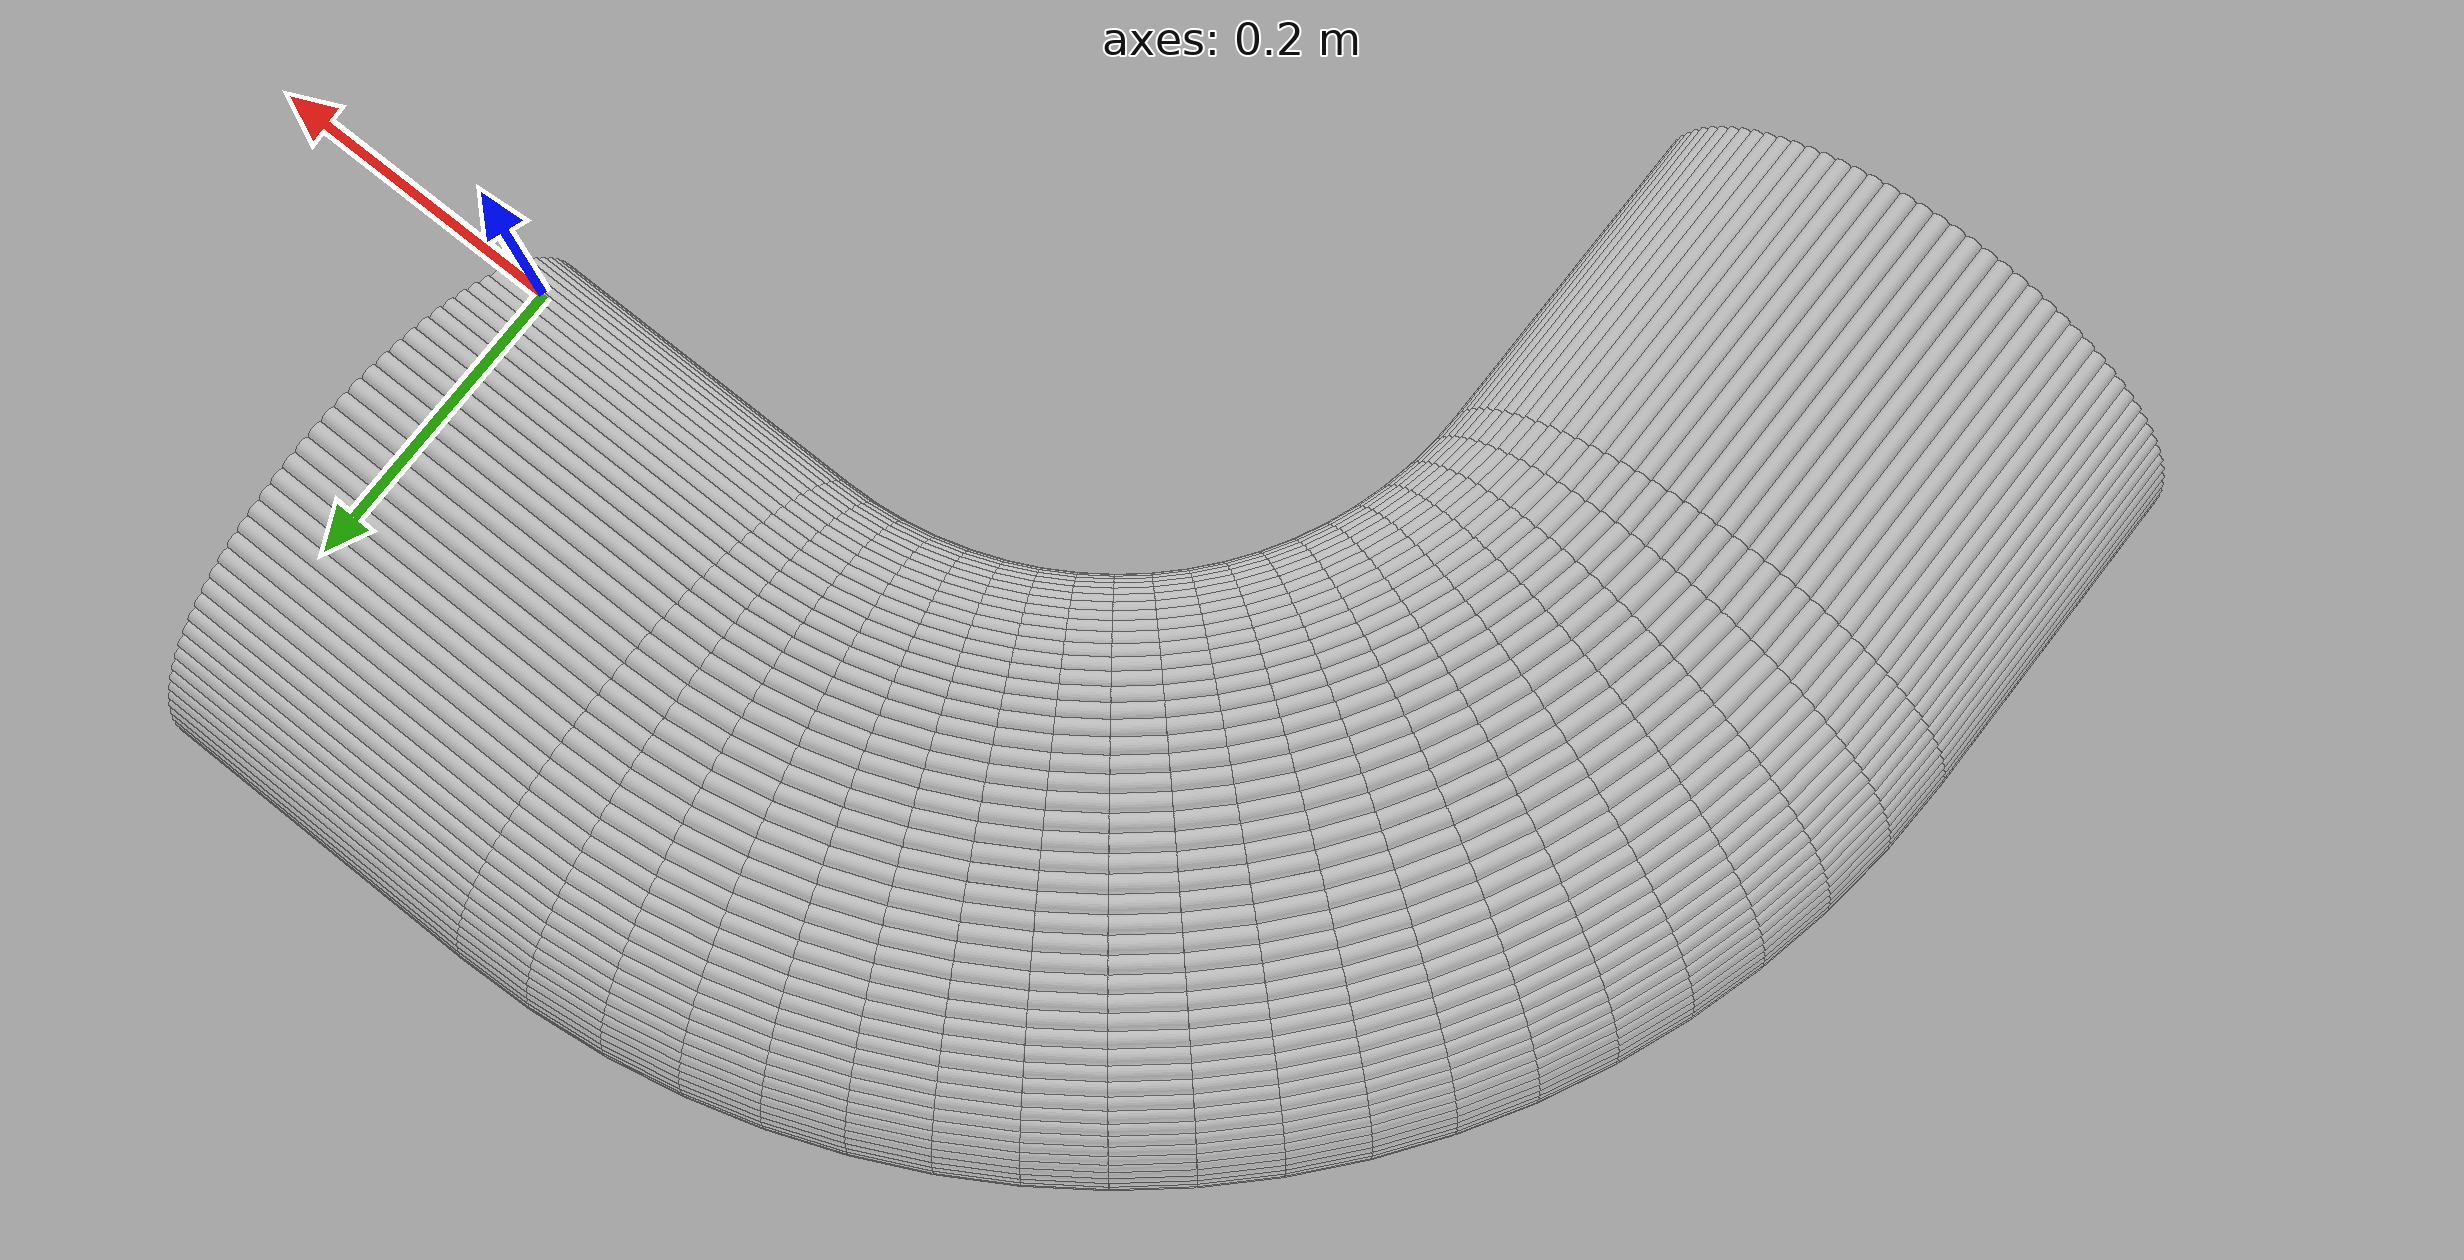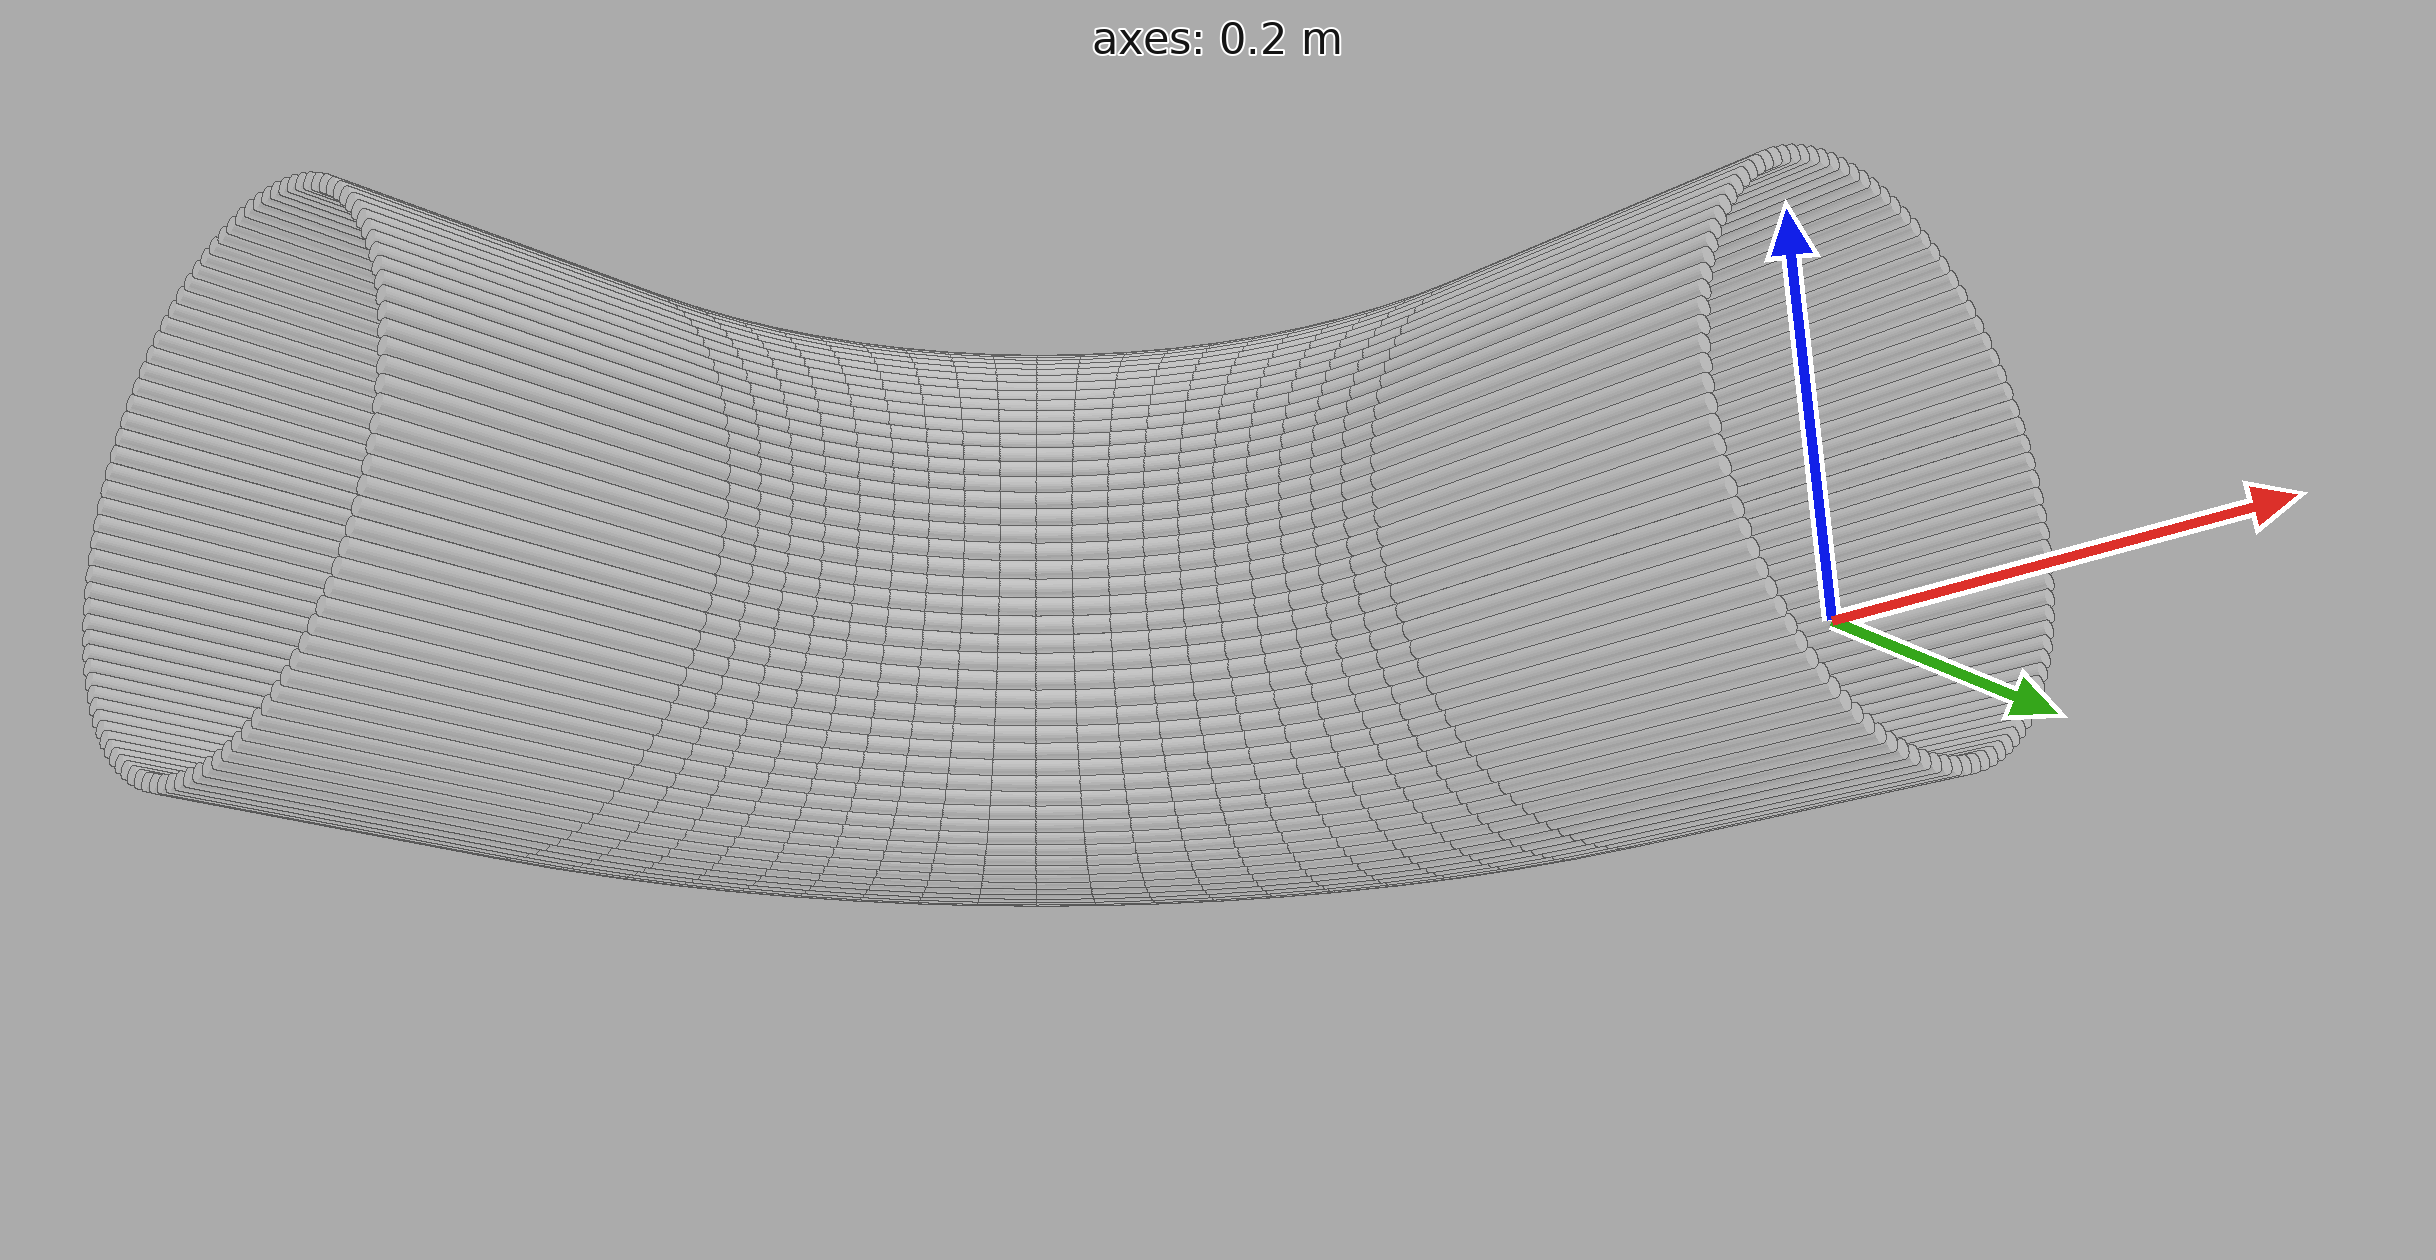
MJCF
<?xml version="1.0" encoding="utf-8"?>
<mujoco>
   <worldbody>
   <body pos="-0.25 -0.24 -0.02" euler="0 0 90">
      <geom euler=" 0 10 0 " fromto="0.56 -0.2 0.16 0.56 0 0.16" rgba="1 1 1 0.35"
            size="0.0050257"
            type="cylinder"/>
      <geom euler=" 0 20 0 " fromto="0.55968 -0.2 0.17005 0.55968 0 0.17005"
            rgba="1 1 1 0.35"
            size="0.0050257"
            type="cylinder"/>
      <geom euler=" 0 30 0 " fromto="0.55874 -0.2 0.18005 0.55874 0 0.18005"
            rgba="1 1 1 0.35"
            size="0.0050257"
            type="cylinder"/>
      <geom euler=" 0 40 0 " fromto="0.55717 -0.2 0.18998 0.55717 0 0.18998"
            rgba="1 1 1 0.35"
            size="0.0050257"
            type="cylinder"/>
      <geom euler=" 0 50 0 " fromto="0.55497 -0.2 0.19979 0.55497 0 0.19979"
            rgba="1 1 1 0.35"
            size="0.0050257"
            type="cylinder"/>
      <geom euler=" 0 60 0 " fromto="0.55217 -0.2 0.20944 0.55217 0 0.20944"
            rgba="1 1 1 0.35"
            size="0.0050257"
            type="cylinder"/>
      <geom euler=" 0 70 0 " fromto="0.54876 -0.2 0.2189 0.54876 0 0.2189"
            rgba="1 1 1 0.35"
            size="0.0050257"
            type="cylinder"/>
      <geom euler=" 0 80 0 " fromto="0.54477 -0.2 0.22812 0.54477 0 0.22812"
            rgba="1 1 1 0.35"
            size="0.0050257"
            type="cylinder"/>
      <geom euler=" 0 90 0 " fromto="0.54021 -0.2 0.23708 0.54021 0 0.23708"
            rgba="1 1 1 0.35"
            size="0.0050257"
            type="cylinder"/>
      <geom euler=" 0 100 0 " fromto="0.53509 -0.2 0.24573 0.53509 0 0.24573"
            rgba="1 1 1 0.35"
            size="0.0050257"
            type="cylinder"/>
      <geom euler=" 0 110 0 " fromto="0.52944 -0.2 0.25405 0.52944 0 0.25405"
            rgba="1 1 1 0.35"
            size="0.0050257"
            type="cylinder"/>
      <geom euler=" 0 120 0 " fromto="0.52328 -0.2 0.26199 0.52328 0 0.26199"
            rgba="1 1 1 0.35"
            size="0.0050257"
            type="cylinder"/>
      <geom euler=" 0 130 0 " fromto="0.51663 -0.2 0.26953 0.51663 0 0.26953"
            rgba="1 1 1 0.35"
            size="0.0050257"
            type="cylinder"/>
      <geom euler=" 0 140 0 " fromto="0.50953 -0.2 0.27663 0.50953 0 0.27663"
            rgba="1 1 1 0.35"
            size="0.0050257"
            type="cylinder"/>
      <geom euler=" 0 150 0 " fromto="0.50199 -0.2 0.28328 0.50199 0 0.28328"
            rgba="1 1 1 0.35"
            size="0.0050257"
            type="cylinder"/>
      <geom euler=" 0 160 0 " fromto="0.49405 -0.2 0.28944 0.49405 0 0.28944"
            rgba="1 1 1 0.35"
            size="0.0050257"
            type="cylinder"/>
      <geom euler=" 0 170 0 " fromto="0.48573 -0.2 0.29509 0.48573 0 0.29509"
            rgba="1 1 1 0.35"
            size="0.0050257"
            type="cylinder"/>
      <geom euler=" 0 180 0 " fromto="0.47708 -0.2 0.30021 0.47708 0 0.30021"
            rgba="1 1 1 0.35"
            size="0.0050257"
            type="cylinder"/>
      <geom euler=" 0 190 0 " fromto="0.46812 -0.2 0.30477 0.46812 0 0.30477"
            rgba="1 1 1 0.35"
            size="0.0050257"
            type="cylinder"/>
      <geom euler=" 0 200 0 " fromto="0.4589 -0.2 0.30876 0.4589 0 0.30876"
            rgba="1 1 1 0.35"
            size="0.0050257"
            type="cylinder"/>
      <geom euler=" 0 210 0 " fromto="0.44944 -0.2 0.31217 0.44944 0 0.31217"
            rgba="1 1 1 0.35"
            size="0.0050257"
            type="cylinder"/>
      <geom euler=" 0 220 0 " fromto="0.43979 -0.2 0.31497 0.43979 0 0.31497"
            rgba="1 1 1 0.35"
            size="0.0050257"
            type="cylinder"/>
      <geom euler=" 0 230 0 " fromto="0.42998 -0.2 0.31717 0.42998 0 0.31717"
            rgba="1 1 1 0.35"
            size="0.0050257"
            type="cylinder"/>
      <geom euler=" 0 240 0 " fromto="0.42005 -0.2 0.31874 0.42005 0 0.31874"
            rgba="1 1 1 0.35"
            size="0.0050257"
            type="cylinder"/>
      <geom euler=" 0 250 0 " fromto="0.41005 -0.2 0.31968 0.41005 0 0.31968"
            rgba="1 1 1 0.35"
            size="0.0050257"
            type="cylinder"/>
      <geom euler=" 0 260 0 " fromto="0.4 -0.2 0.32 0.4 0 0.32" rgba="1 1 1 0.35"
            size="0.0050257"
            type="cylinder"/>
      <geom euler=" 0 270 0 " fromto="0.38995 -0.2 0.31968 0.38995 0 0.31968"
            rgba="1 1 1 0.35"
            size="0.0050257"
            type="cylinder"/>
      <geom euler=" 0 280 0 " fromto="0.37995 -0.2 0.31874 0.37995 0 0.31874"
            rgba="1 1 1 0.35"
            size="0.0050257"
            type="cylinder"/>
      <geom euler=" 0 290 0 " fromto="0.37002 -0.2 0.31717 0.37002 0 0.31717"
            rgba="1 1 1 0.35"
            size="0.0050257"
            type="cylinder"/>
      <geom euler=" 0 300 0 " fromto="0.36021 -0.2 0.31497 0.36021 0 0.31497"
            rgba="1 1 1 0.35"
            size="0.0050257"
            type="cylinder"/>
      <geom euler=" 0 310 0 " fromto="0.35056 -0.2 0.31217 0.35056 0 0.31217"
            rgba="1 1 1 0.35"
            size="0.0050257"
            type="cylinder"/>
      <geom euler=" 0 320 0 " fromto="0.3411 -0.2 0.30876 0.3411 0 0.30876"
            rgba="1 1 1 0.35"
            size="0.0050257"
            type="cylinder"/>
      <geom euler=" 0 330 0 " fromto="0.33188 -0.2 0.30477 0.33188 0 0.30477"
            rgba="1 1 1 0.35"
            size="0.0050257"
            type="cylinder"/>
      <geom euler=" 0 340 0 " fromto="0.32292 -0.2 0.30021 0.32292 0 0.30021"
            rgba="1 1 1 0.35"
            size="0.0050257"
            type="cylinder"/>
      <geom euler=" 0 350 0 " fromto="0.31427 -0.2 0.29509 0.31427 0 0.29509"
            rgba="1 1 1 0.35"
            size="0.0050257"
            type="cylinder"/>
      <geom euler=" 0 360 0 " fromto="0.30595 -0.2 0.28944 0.30595 0 0.28944"
            rgba="1 1 1 0.35"
            size="0.0050257"
            type="cylinder"/>
      <geom euler=" 0 370 0 " fromto="0.29801 -0.2 0.28328 0.29801 0 0.28328"
            rgba="1 1 1 0.35"
            size="0.0050257"
            type="cylinder"/>
      <geom euler=" 0 380 0 " fromto="0.29047 -0.2 0.27663 0.29047 0 0.27663"
            rgba="1 1 1 0.35"
            size="0.0050257"
            type="cylinder"/>
      <geom euler=" 0 390 0 " fromto="0.28337 -0.2 0.26953 0.28337 0 0.26953"
            rgba="1 1 1 0.35"
            size="0.0050257"
            type="cylinder"/>
      <geom euler=" 0 400 0 " fromto="0.27672 -0.2 0.26199 0.27672 0 0.26199"
            rgba="1 1 1 0.35"
            size="0.0050257"
            type="cylinder"/>
      <geom euler=" 0 410 0 " fromto="0.27056 -0.2 0.25405 0.27056 0 0.25405"
            rgba="1 1 1 0.35"
            size="0.0050257"
            type="cylinder"/>
      <geom euler=" 0 420 0 " fromto="0.26491 -0.2 0.24573 0.26491 0 0.24573"
            rgba="1 1 1 0.35"
            size="0.0050257"
            type="cylinder"/>
      <geom euler=" 0 430 0 " fromto="0.25979 -0.2 0.23708 0.25979 0 0.23708"
            rgba="1 1 1 0.35"
            size="0.0050257"
            type="cylinder"/>
      <geom euler=" 0 440 0 " fromto="0.25523 -0.2 0.22812 0.25523 0 0.22812"
            rgba="1 1 1 0.35"
            size="0.0050257"
            type="cylinder"/>
      <geom euler=" 0 450 0 " fromto="0.25124 -0.2 0.2189 0.25124 0 0.2189"
            rgba="1 1 1 0.35"
            size="0.0050257"
            type="cylinder"/>
      <geom euler=" 0 460 0 " fromto="0.24783 -0.2 0.20944 0.24783 0 0.20944"
            rgba="1 1 1 0.35"
            size="0.0050257"
            type="cylinder"/>
      <geom euler=" 0 470 0 " fromto="0.24503 -0.2 0.19979 0.24503 0 0.19979"
            rgba="1 1 1 0.35"
            size="0.0050257"
            type="cylinder"/>
      <geom euler=" 0 480 0 " fromto="0.24283 -0.2 0.18998 0.24283 0 0.18998"
            rgba="1 1 1 0.35"
            size="0.0050257"
            type="cylinder"/>
      <geom euler=" 0 490 0 " fromto="0.24126 -0.2 0.18005 0.24126 0 0.18005"
            rgba="1 1 1 0.35"
            size="0.0050257"
            type="cylinder"/>
      <geom euler=" 0 500 0 " fromto="0.24032 -0.2 0.17005 0.24032 0 0.17005"
            rgba="1 1 1 0.35"
            size="0.0050257"
            type="cylinder"/>
      <geom euler=" 0 510 0 " fromto="0.24 -0.2 0.16 0.24 0 0.16" rgba="1 1 1 0.35"
            size="0.0050257"
            type="cylinder"/>
      <geom euler=" 0 520 0 " fromto="0.24032 -0.2 0.14995 0.24032 0 0.14995"
            rgba="1 1 1 0.35"
            size="0.0050257"
            type="cylinder"/>
      <geom euler=" 0 530 0 " fromto="0.24126 -0.2 0.13995 0.24126 0 0.13995"
            rgba="1 1 1 0.35"
            size="0.0050257"
            type="cylinder"/>
      <geom euler=" 0 540 0 " fromto="0.24283 -0.2 0.13002 0.24283 0 0.13002"
            rgba="1 1 1 0.35"
            size="0.0050257"
            type="cylinder"/>
      <geom euler=" 0 550 0 " fromto="0.24503 -0.2 0.12021 0.24503 0 0.12021"
            rgba="1 1 1 0.35"
            size="0.0050257"
            type="cylinder"/>
      <geom euler=" 0 560 0 " fromto="0.24783 -0.2 0.11056 0.24783 0 0.11056"
            rgba="1 1 1 0.35"
            size="0.0050257"
            type="cylinder"/>
      <geom euler=" 0 570 0 " fromto="0.25124 -0.2 0.1011 0.25124 0 0.1011"
            rgba="1 1 1 0.35"
            size="0.0050257"
            type="cylinder"/>
      <geom euler=" 0 580 0 " fromto="0.25523 -0.2 0.091875 0.25523 0 0.091875"
            rgba="1 1 1 0.35"
            size="0.0050257"
            type="cylinder"/>
      <geom euler=" 0 590 0 " fromto="0.25979 -0.2 0.082919 0.25979 0 0.082919"
            rgba="1 1 1 0.35"
            size="0.0050257"
            type="cylinder"/>
      <geom euler=" 0 600 0 " fromto="0.26491 -0.2 0.074268 0.26491 0 0.074268"
            rgba="1 1 1 0.35"
            size="0.0050257"
            type="cylinder"/>
      <geom euler=" 0 610 0 " fromto="0.27056 -0.2 0.065954 0.27056 0 0.065954"
            rgba="1 1 1 0.35"
            size="0.0050257"
            type="cylinder"/>
      <geom euler=" 0 620 0 " fromto="0.27672 -0.2 0.058012 0.27672 0 0.058012"
            rgba="1 1 1 0.35"
            size="0.0050257"
            type="cylinder"/>
      <geom euler=" 0 630 0 " fromto="0.28337 -0.2 0.050472 0.28337 0 0.050472"
            rgba="1 1 1 0.35"
            size="0.0050257"
            type="cylinder"/>
      <geom euler=" 0 640 0 " fromto="0.29047 -0.2 0.043365 0.29047 0 0.043365"
            rgba="1 1 1 0.35"
            size="0.0050257"
            type="cylinder"/>
      <geom euler=" 0 650 0 " fromto="0.29801 -0.2 0.036718 0.29801 0 0.036718"
            rgba="1 1 1 0.35"
            size="0.0050257"
            type="cylinder"/>
      <geom euler=" 0 660 0 " fromto="0.30595 -0.2 0.030557 0.30595 0 0.030557"
            rgba="1 1 1 0.35"
            size="0.0050257"
            type="cylinder"/>
      <geom euler=" 0 670 0 " fromto="0.31427 -0.2 0.024908 0.31427 0 0.024908"
            rgba="1 1 1 0.35"
            size="0.0050257"
            type="cylinder"/>
      <geom euler=" 0 680 0 " fromto="0.32292 -0.2 0.019791 0.32292 0 0.019791"
            rgba="1 1 1 0.35"
            size="0.0050257"
            type="cylinder"/>
      <geom euler=" 0 690 0 " fromto="0.33188 -0.2 0.015228 0.33188 0 0.015228"
            rgba="1 1 1 0.35"
            size="0.0050257"
            type="cylinder"/>
      <geom euler=" 0 700 0 " fromto="0.3411 -0.2 0.011236 0.3411 0 0.011236"
            rgba="1 1 1 0.35"
            size="0.0050257"
            type="cylinder"/>
      <geom euler=" 0 710 0 " fromto="0.35056 -0.2 0.007831 0.35056 0 0.007831"
            rgba="1 1 1 0.35"
            size="0.0050257"
            type="cylinder"/>
      <geom euler=" 0 720 0 " fromto="0.36021 -0.2 0.0050267 0.36021 0 0.0050267"
            rgba="1 1 1 0.35"
            size="0.0050257"
            type="cylinder"/>
      <geom euler=" 0 730 0 " fromto="0.37002 -0.2 0.002834 0.37002 0 0.002834"
            rgba="1 1 1 0.35"
            size="0.0050257"
            type="cylinder"/>
      <geom euler=" 0 740 0 " fromto="0.37995 -0.2 0.0012616 0.37995 0 0.0012616"
            rgba="1 1 1 0.35"
            size="0.0050257"
            type="cylinder"/>
      <geom euler=" 0 750 0 " fromto="0.38995 -0.2 0.00031572 0.38995 0 0.00031572"
            rgba="1 1 1 0.35"
            size="0.0050257"
            type="cylinder"/>
      <geom euler=" 0 760 0 " fromto="0.4 -0.2 0 0.4 0 0" rgba="1 1 1 0.35"
            size="0.0050257"
            type="cylinder"/>
      <geom euler=" 0 770 0 " fromto="0.41005 -0.2 0.00031572 0.41005 0 0.00031572"
            rgba="1 1 1 0.35"
            size="0.0050257"
            type="cylinder"/>
      <geom euler=" 0 780 0 " fromto="0.42005 -0.2 0.0012616 0.42005 0 0.0012616"
            rgba="1 1 1 0.35"
            size="0.0050257"
            type="cylinder"/>
      <geom euler=" 0 790 0 " fromto="0.42998 -0.2 0.002834 0.42998 0 0.002834"
            rgba="1 1 1 0.35"
            size="0.0050257"
            type="cylinder"/>
      <geom euler=" 0 800 0 " fromto="0.43979 -0.2 0.0050267 0.43979 0 0.0050267"
            rgba="1 1 1 0.35"
            size="0.0050257"
            type="cylinder"/>
      <geom euler=" 0 810 0 " fromto="0.44944 -0.2 0.007831 0.44944 0 0.007831"
            rgba="1 1 1 0.35"
            size="0.0050257"
            type="cylinder"/>
      <geom euler=" 0 820 0 " fromto="0.4589 -0.2 0.011236 0.4589 0 0.011236"
            rgba="1 1 1 0.35"
            size="0.0050257"
            type="cylinder"/>
      <geom euler=" 0 830 0 " fromto="0.46812 -0.2 0.015228 0.46812 0 0.015228"
            rgba="1 1 1 0.35"
            size="0.0050257"
            type="cylinder"/>
      <geom euler=" 0 840 0 " fromto="0.47708 -0.2 0.019791 0.47708 0 0.019791"
            rgba="1 1 1 0.35"
            size="0.0050257"
            type="cylinder"/>
      <geom euler=" 0 850 0 " fromto="0.48573 -0.2 0.024908 0.48573 0 0.024908"
            rgba="1 1 1 0.35"
            size="0.0050257"
            type="cylinder"/>
      <geom euler=" 0 860 0 " fromto="0.49405 -0.2 0.030557 0.49405 0 0.030557"
            rgba="1 1 1 0.35"
            size="0.0050257"
            type="cylinder"/>
      <geom euler=" 0 870 0 " fromto="0.50199 -0.2 0.036718 0.50199 0 0.036718"
            rgba="1 1 1 0.35"
            size="0.0050257"
            type="cylinder"/>
      <geom euler=" 0 880 0 " fromto="0.50953 -0.2 0.043365 0.50953 0 0.043365"
            rgba="1 1 1 0.35"
            size="0.0050257"
            type="cylinder"/>
      <geom euler=" 0 890 0 " fromto="0.51663 -0.2 0.050472 0.51663 0 0.050472"
            rgba="1 1 1 0.35"
            size="0.0050257"
            type="cylinder"/>
      <geom euler=" 0 900 0 " fromto="0.52328 -0.2 0.058012 0.52328 0 0.058012"
            rgba="1 1 1 0.35"
            size="0.0050257"
            type="cylinder"/>
      <geom euler=" 0 910 0 " fromto="0.52944 -0.2 0.065954 0.52944 0 0.065954"
            rgba="1 1 1 0.35"
            size="0.0050257"
            type="cylinder"/>
      <geom euler=" 0 920 0 " fromto="0.53509 -0.2 0.074268 0.53509 0 0.074268"
            rgba="1 1 1 0.35"
            size="0.0050257"
            type="cylinder"/>
      <geom euler=" 0 930 0 " fromto="0.54021 -0.2 0.082919 0.54021 0 0.082919"
            rgba="1 1 1 0.35"
            size="0.0050257"
            type="cylinder"/>
      <geom euler=" 0 940 0 " fromto="0.54477 -0.2 0.091875 0.54477 0 0.091875"
            rgba="1 1 1 0.35"
            size="0.0050257"
            type="cylinder"/>
      <geom euler=" 0 950 0 " fromto="0.54876 -0.2 0.1011 0.54876 0 0.1011"
            rgba="1 1 1 0.35"
            size="0.0050257"
            type="cylinder"/>
      <geom euler=" 0 960 0 " fromto="0.55217 -0.2 0.11056 0.55217 0 0.11056"
            rgba="1 1 1 0.35"
            size="0.0050257"
            type="cylinder"/>
      <geom euler=" 0 970 0 " fromto="0.55497 -0.2 0.12021 0.55497 0 0.12021"
            rgba="1 1 1 0.35"
            size="0.0050257"
            type="cylinder"/>
      <geom euler=" 0 980 0 " fromto="0.55717 -0.2 0.13002 0.55717 0 0.13002"
            rgba="1 1 1 0.35"
            size="0.0050257"
            type="cylinder"/>
      <geom euler=" 0 990 0 " fromto="0.55874 -0.2 0.13995 0.55874 0 0.13995"
            rgba="1 1 1 0.35"
            size="0.0050257"
            type="cylinder"/>
      <geom euler=" 0 1000 0 " fromto="0.55968 -0.2 0.14995 0.55968 0 0.14995"
            rgba="1 1 1 0.35"
            size="0.0050257"
            type="cylinder"/>
      <geom euler=" 0 10 0 " fromto="0.56 0 0.16 0.55809 0.046244 0.16" rgba="1 1 1 0.35"
            size="0.0050257"
            type="cylinder"/>
      <geom euler=" 0 20 0 " fromto="0.55968 0 0.17005 0.55777 0.046218 0.17005"
            rgba="1 1 1 0.35"
            size="0.0050257"
            type="cylinder"/>
      <geom euler=" 0 30 0 " fromto="0.55874 0 0.18005 0.55683 0.04614 0.18005"
            rgba="1 1 1 0.35"
            size="0.0050257"
            type="cylinder"/>
      <geom euler=" 0 40 0 " fromto="0.55717 0 0.18998 0.55526 0.04601 0.18998"
            rgba="1 1 1 0.35"
            size="0.0050257"
            type="cylinder"/>
      <geom euler=" 0 50 0 " fromto="0.55497 0 0.19979 0.55308 0.045829 0.19979"
            rgba="1 1 1 0.35"
            size="0.0050257"
            type="cylinder"/>
      <geom euler=" 0 60 0 " fromto="0.55217 0 0.20944 0.55028 0.045598 0.20944"
            rgba="1 1 1 0.35"
            size="0.0050257"
            type="cylinder"/>
      <geom euler=" 0 70 0 " fromto="0.54876 0 0.2189 0.54689 0.045317 0.2189"
            rgba="1 1 1 0.35"
            size="0.0050257"
            type="cylinder"/>
      <geom euler=" 0 80 0 " fromto="0.54477 0 0.22812 0.54291 0.044987 0.22812"
            rgba="1 1 1 0.35"
            size="0.0050257"
            type="cylinder"/>
      <geom euler=" 0 90 0 " fromto="0.54021 0 0.23708 0.53836 0.04461 0.23708"
            rgba="1 1 1 0.35"
            size="0.0050257"
            type="cylinder"/>
      <geom euler=" 0 100 0 " fromto="0.53509 0 0.24573 0.53326 0.044188 0.24573"
            rgba="1 1 1 0.35"
            size="0.0050257"
            type="cylinder"/>
      <geom euler=" 0 110 0 " fromto="0.52944 0 0.25405 0.52763 0.043721 0.25405"
            rgba="1 1 1 0.35"
            size="0.0050257"
            type="cylinder"/>
      <geom euler=" 0 120 0 " fromto="0.52328 0 0.26199 0.52149 0.043212 0.26199"
            rgba="1 1 1 0.35"
            size="0.0050257"
            type="cylinder"/>
      <geom euler=" 0 130 0 " fromto="0.51663 0 0.26953 0.51487 0.042663 0.26953"
            rgba="1 1 1 0.35"
            size="0.0050257"
            type="cylinder"/>
      <geom euler=" 0 140 0 " fromto="0.50953 0 0.27663 0.50779 0.042076 0.27663"
            rgba="1 1 1 0.35"
            size="0.0050257"
            type="cylinder"/>
      <geom euler=" 0 150 0 " fromto="0.50199 0 0.28328 0.50027 0.041454 0.28328"
            rgba="1 1 1 0.35"
            size="0.0050257"
            type="cylinder"/>
      <geom euler=" 0 160 0 " fromto="0.49405 0 0.28944 0.49236 0.040798 0.28944"
            rgba="1 1 1 0.35"
            size="0.0050257"
            type="cylinder"/>
      <geom euler=" 0 170 0 " fromto="0.48573 0 0.29509 0.48407 0.040111 0.29509"
            rgba="1 1 1 0.35"
            size="0.0050257"
            type="cylinder"/>
      <geom euler=" 0 180 0 " fromto="0.47708 0 0.30021 0.47545 0.039397 0.30021"
            rgba="1 1 1 0.35"
            size="0.0050257"
            type="cylinder"/>
      <geom euler=" 0 190 0 " fromto="0.46812 0 0.30477 0.46653 0.038657 0.30477"
            rgba="1 1 1 0.35"
            size="0.0050257"
            type="cylinder"/>
      <geom euler=" 0 200 0 " fromto="0.4589 0 0.30876 0.45733 0.037896 0.30876"
            rgba="1 1 1 0.35"
            size="0.0050257"
            type="cylinder"/>
      <geom euler=" 0 210 0 " fromto="0.44944 0 0.31217 0.44791 0.037115 0.31217"
            rgba="1 1 1 0.35"
            size="0.0050257"
            type="cylinder"/>
      <geom euler=" 0 220 0 " fromto="0.43979 0 0.31497 0.43829 0.036318 0.31497"
            rgba="1 1 1 0.35"
            size="0.0050257"
            type="cylinder"/>
      <geom euler=" 0 230 0 " fromto="0.42998 0 0.31717 0.42851 0.035508 0.31717"
            rgba="1 1 1 0.35"
            size="0.0050257"
            type="cylinder"/>
      <geom euler=" 0 240 0 " fromto="0.42005 0 0.31874 0.41862 0.034688 0.31874"
            rgba="1 1 1 0.35"
            size="0.0050257"
            type="cylinder"/>
      <geom euler=" 0 250 0 " fromto="0.41005 0 0.31968 0.40865 0.033861 0.31968"
            rgba="1 1 1 0.35"
            size="0.0050257"
            type="cylinder"/>
      <geom euler=" 0 260 0 " fromto="0.4 0 0.32 0.39863 0.033032 0.32" rgba="1 1 1 0.35"
            size="0.0050257"
            type="cylinder"/>
      <geom euler=" 0 270 0 " fromto="0.38995 0 0.31968 0.38862 0.032202 0.31968"
            rgba="1 1 1 0.35"
            size="0.0050257"
            type="cylinder"/>
      <geom euler=" 0 280 0 " fromto="0.37995 0 0.31874 0.37865 0.031376 0.31874"
            rgba="1 1 1 0.35"
            size="0.0050257"
            type="cylinder"/>
      <geom euler=" 0 290 0 " fromto="0.37002 0 0.31717 0.36876 0.030556 0.31717"
            rgba="1 1 1 0.35"
            size="0.0050257"
            type="cylinder"/>
      <geom euler=" 0 300 0 " fromto="0.36021 0 0.31497 0.35898 0.029746 0.31497"
            rgba="1 1 1 0.35"
            size="0.0050257"
            type="cylinder"/>
      <geom euler=" 0 310 0 " fromto="0.35056 0 0.31217 0.34936 0.028949 0.31217"
            rgba="1 1 1 0.35"
            size="0.0050257"
            type="cylinder"/>
      <geom euler=" 0 320 0 " fromto="0.3411 0 0.30876 0.33994 0.028168 0.30876"
            rgba="1 1 1 0.35"
            size="0.0050257"
            type="cylinder"/>
      <geom euler=" 0 330 0 " fromto="0.33188 0 0.30477 0.33074 0.027406 0.30477"
            rgba="1 1 1 0.35"
            size="0.0050257"
            type="cylinder"/>
      <geom euler=" 0 340 0 " fromto="0.32292 0 0.30021 0.32182 0.026666 0.30021"
            rgba="1 1 1 0.35"
            size="0.0050257"
            type="cylinder"/>
      <geom euler=" 0 350 0 " fromto="0.31427 0 0.29509 0.31319 0.025952 0.29509"
            rgba="1 1 1 0.35"
            size="0.0050257"
            type="cylinder"/>
      <geom euler=" 0 360 0 " fromto="0.30595 0 0.28944 0.30491 0.025266 0.28944"
            rgba="1 1 1 0.35"
            size="0.0050257"
            type="cylinder"/>
      <geom euler=" 0 370 0 " fromto="0.29801 0 0.28328 0.29699 0.02461 0.28328"
            rgba="1 1 1 0.35"
            size="0.0050257"
            type="cylinder"/>
      <geom euler=" 0 380 0 " fromto="0.29047 0 0.27663 0.28948 0.023987 0.27663"
            rgba="1 1 1 0.35"
            size="0.0050257"
            type="cylinder"/>
      <geom euler=" 0 390 0 " fromto="0.28337 0 0.26953 0.2824 0.0234 0.26953"
            rgba="1 1 1 0.35"
            size="0.0050257"
            type="cylinder"/>
      <geom euler=" 0 400 0 " fromto="0.27672 0 0.26199 0.27577 0.022851 0.26199"
            rgba="1 1 1 0.35"
            size="0.0050257"
            type="cylinder"/>
      <geom euler=" 0 410 0 " fromto="0.27056 0 0.25405 0.26963 0.022342 0.25405"
            rgba="1 1 1 0.35"
            size="0.0050257"
            type="cylinder"/>
      <geom euler=" 0 420 0 " fromto="0.26491 0 0.24573 0.264 0.021876 0.24573"
            rgba="1 1 1 0.35"
            size="0.0050257"
            type="cylinder"/>
      <geom euler=" 0 430 0 " fromto="0.25979 0 0.23708 0.2589 0.021453 0.23708"
            rgba="1 1 1 0.35"
            size="0.0050257"
            type="cylinder"/>
      <geom euler=" 0 440 0 " fromto="0.25523 0 0.22812 0.25436 0.021077 0.22812"
            rgba="1 1 1 0.35"
            size="0.0050257"
            type="cylinder"/>
      <geom euler=" 0 450 0 " fromto="0.25124 0 0.2189 0.25038 0.020747 0.2189"
            rgba="1 1 1 0.35"
            size="0.0050257"
            type="cylinder"/>
      <geom euler=" 0 460 0 " fromto="0.24783 0 0.20944 0.24698 0.020466 0.20944"
            rgba="1 1 1 0.35"
            size="0.0050257"
            type="cylinder"/>
      <geom euler=" 0 470 0 " fromto="0.24503 0 0.19979 0.24419 0.020234 0.19979"
            rgba="1 1 1 0.35"
            size="0.0050257"
            type="cylinder"/>
      <geom euler=" 0 480 0 " fromto="0.24283 0 0.18998 0.242 0.020053 0.18998"
            rgba="1 1 1 0.35"
            size="0.0050257"
            type="cylinder"/>
      <geom euler=" 0 490 0 " fromto="0.24126 0 0.18005 0.24044 0.019923 0.18005"
            rgba="1 1 1 0.35"
            size="0.0050257"
            type="cylinder"/>
      <geom euler=" 0 500 0 " fromto="0.24032 0 0.17005 0.23949 0.019845 0.17005"
            rgba="1 1 1 0.35"
            size="0.0050257"
            type="cylinder"/>
      <geom euler=" 0 510 0 " fromto="0.24 0 0.16 0.23918 0.019819 0.16" rgba="1 1 1 0.35"
            size="0.0050257"
            type="cylinder"/>
      <geom euler=" 0 520 0 " fromto="0.24032 0 0.14995 0.23949 0.019845 0.14995"
            rgba="1 1 1 0.35"
            size="0.0050257"
            type="cylinder"/>
      <geom euler=" 0 530 0 " fromto="0.24126 0 0.13995 0.24044 0.019923 0.13995"
            rgba="1 1 1 0.35"
            size="0.0050257"
            type="cylinder"/>
      <geom euler=" 0 540 0 " fromto="0.24283 0 0.13002 0.242 0.020053 0.13002"
            rgba="1 1 1 0.35"
            size="0.0050257"
            type="cylinder"/>
      <geom euler=" 0 550 0 " fromto="0.24503 0 0.12021 0.24419 0.020234 0.12021"
            rgba="1 1 1 0.35"
            size="0.0050257"
            type="cylinder"/>
      <geom euler=" 0 560 0 " fromto="0.24783 0 0.11056 0.24698 0.020466 0.11056"
            rgba="1 1 1 0.35"
            size="0.0050257"
            type="cylinder"/>
      <geom euler=" 0 570 0 " fromto="0.25124 0 0.1011 0.25038 0.020747 0.1011"
            rgba="1 1 1 0.35"
            size="0.0050257"
            type="cylinder"/>
      <geom euler=" 0 580 0 " fromto="0.25523 0 0.091875 0.25436 0.021077 0.091875"
            rgba="1 1 1 0.35"
            size="0.0050257"
            type="cylinder"/>
      <geom euler=" 0 590 0 " fromto="0.25979 0 0.082919 0.2589 0.021453 0.082919"
            rgba="1 1 1 0.35"
            size="0.0050257"
            type="cylinder"/>
      <geom euler=" 0 600 0 " fromto="0.26491 0 0.074268 0.264 0.021876 0.074268"
            rgba="1 1 1 0.35"
            size="0.0050257"
            type="cylinder"/>
      <geom euler=" 0 610 0 " fromto="0.27056 0 0.065954 0.26963 0.022342 0.065954"
            rgba="1 1 1 0.35"
            size="0.0050257"
            type="cylinder"/>
      <geom euler=" 0 620 0 " fromto="0.27672 0 0.058012 0.27577 0.022851 0.058012"
            rgba="1 1 1 0.35"
            size="0.0050257"
            type="cylinder"/>
      <geom euler=" 0 630 0 " fromto="0.28337 0 0.050472 0.2824 0.0234 0.050472"
            rgba="1 1 1 0.35"
            size="0.0050257"
            type="cylinder"/>
      <geom euler=" 0 640 0 " fromto="0.29047 0 0.043365 0.28948 0.023987 0.043365"
            rgba="1 1 1 0.35"
            size="0.0050257"
            type="cylinder"/>
      <geom euler=" 0 650 0 " fromto="0.29801 0 0.036718 0.29699 0.02461 0.036718"
            rgba="1 1 1 0.35"
            size="0.0050257"
            type="cylinder"/>
      <geom euler=" 0 660 0 " fromto="0.30595 0 0.030557 0.30491 0.025266 0.030557"
            rgba="1 1 1 0.35"
            size="0.0050257"
            type="cylinder"/>
      <geom euler=" 0 670 0 " fromto="0.31427 0 0.024908 0.31319 0.025952 0.024908"
            rgba="1 1 1 0.35"
            size="0.0050257"
            type="cylinder"/>
      <geom euler=" 0 680 0 " fromto="0.32292 0 0.019791 0.32182 0.026666 0.019791"
            rgba="1 1 1 0.35"
            size="0.0050257"
            type="cylinder"/>
      <geom euler=" 0 690 0 " fromto="0.33188 0 0.015228 0.33074 0.027406 0.015228"
            rgba="1 1 1 0.35"
            size="0.0050257"
            type="cylinder"/>
      <geom euler=" 0 700 0 " fromto="0.3411 0 0.011236 0.33994 0.028168 0.011236"
            rgba="1 1 1 0.35"
            size="0.0050257"
            type="cylinder"/>
      <geom euler=" 0 710 0 " fromto="0.35056 0 0.007831 0.34936 0.028949 0.007831"
            rgba="1 1 1 0.35"
            size="0.0050257"
            type="cylinder"/>
      <geom euler=" 0 720 0 " fromto="0.36021 0 0.0050267 0.35898 0.029746 0.0050267"
            rgba="1 1 1 0.35"
            size="0.0050257"
            type="cylinder"/>
      <geom euler=" 0 730 0 " fromto="0.37002 0 0.002834 0.36876 0.030556 0.002834"
            rgba="1 1 1 0.35"
            size="0.0050257"
            type="cylinder"/>
      <geom euler=" 0 740 0 " fromto="0.37995 0 0.0012616 0.37865 0.031376 0.0012616"
            rgba="1 1 1 0.35"
            size="0.0050257"
            type="cylinder"/>
      <geom euler=" 0 750 0 " fromto="0.38995 0 0.00031572 0.38862 0.032202 0.00031572"
            rgba="1 1 1 0.35"
            size="0.0050257"
            type="cylinder"/>
      <geom euler=" 0 760 0 " fromto="0.4 0 0 0.39863 0.033032 0" rgba="1 1 1 0.35"
            size="0.0050257"
            type="cylinder"/>
      <geom euler=" 0 770 0 " fromto="0.41005 0 0.00031572 0.40865 0.033861 0.00031572"
            rgba="1 1 1 0.35"
            size="0.0050257"
            type="cylinder"/>
      <geom euler=" 0 780 0 " fromto="0.42005 0 0.0012616 0.41862 0.034688 0.0012616"
            rgba="1 1 1 0.35"
            size="0.0050257"
            type="cylinder"/>
      <geom euler=" 0 790 0 " fromto="0.42998 0 0.002834 0.42851 0.035508 0.002834"
            rgba="1 1 1 0.35"
            size="0.0050257"
            type="cylinder"/>
      <geom euler=" 0 800 0 " fromto="0.43979 0 0.0050267 0.43829 0.036318 0.0050267"
            rgba="1 1 1 0.35"
            size="0.0050257"
            type="cylinder"/>
      <geom euler=" 0 810 0 " fromto="0.44944 0 0.007831 0.44791 0.037115 0.007831"
            rgba="1 1 1 0.35"
            size="0.0050257"
            type="cylinder"/>
      <geom euler=" 0 820 0 " fromto="0.4589 0 0.011236 0.45733 0.037896 0.011236"
            rgba="1 1 1 0.35"
            size="0.0050257"
            type="cylinder"/>
      <geom euler=" 0 830 0 " fromto="0.46812 0 0.015228 0.46653 0.038657 0.015228"
            rgba="1 1 1 0.35"
            size="0.0050257"
            type="cylinder"/>
      <geom euler=" 0 840 0 " fromto="0.47708 0 0.019791 0.47545 0.039397 0.019791"
            rgba="1 1 1 0.35"
            size="0.0050257"
            type="cylinder"/>
      <geom euler=" 0 850 0 " fromto="0.48573 0 0.024908 0.48407 0.040111 0.024908"
            rgba="1 1 1 0.35"
            size="0.0050257"
            type="cylinder"/>
      <geom euler=" 0 860 0 " fromto="0.49405 0 0.030557 0.49236 0.040798 0.030557"
            rgba="1 1 1 0.35"
            size="0.0050257"
            type="cylinder"/>
      <geom euler=" 0 870 0 " fromto="0.50199 0 0.036718 0.50027 0.041454 0.036718"
            rgba="1 1 1 0.35"
            size="0.0050257"
            type="cylinder"/>
      <geom euler=" 0 880 0 " fromto="0.50953 0 0.043365 0.50779 0.042076 0.043365"
            rgba="1 1 1 0.35"
            size="0.0050257"
            type="cylinder"/>
      <geom euler=" 0 890 0 " fromto="0.51663 0 0.050472 0.51487 0.042663 0.050472"
            rgba="1 1 1 0.35"
            size="0.0050257"
            type="cylinder"/>
      <geom euler=" 0 900 0 " fromto="0.52328 0 0.058012 0.52149 0.043212 0.058012"
            rgba="1 1 1 0.35"
            size="0.0050257"
            type="cylinder"/>
      <geom euler=" 0 910 0 " fromto="0.52944 0 0.065954 0.52763 0.043721 0.065954"
            rgba="1 1 1 0.35"
            size="0.0050257"
            type="cylinder"/>
      <geom euler=" 0 920 0 " fromto="0.53509 0 0.074268 0.53326 0.044188 0.074268"
            rgba="1 1 1 0.35"
            size="0.0050257"
            type="cylinder"/>
      <geom euler=" 0 930 0 " fromto="0.54021 0 0.082919 0.53836 0.04461 0.082919"
            rgba="1 1 1 0.35"
            size="0.0050257"
            type="cylinder"/>
      <geom euler=" 0 940 0 " fromto="0.54477 0 0.091875 0.54291 0.044987 0.091875"
            rgba="1 1 1 0.35"
            size="0.0050257"
            type="cylinder"/>
      <geom euler=" 0 950 0 " fromto="0.54876 0 0.1011 0.54689 0.045317 0.1011"
            rgba="1 1 1 0.35"
            size="0.0050257"
            type="cylinder"/>
      <geom euler=" 0 960 0 " fromto="0.55217 0 0.11056 0.55028 0.045598 0.11056"
            rgba="1 1 1 0.35"
            size="0.0050257"
            type="cylinder"/>
      <geom euler=" 0 970 0 " fromto="0.55497 0 0.12021 0.55308 0.045829 0.12021"
            rgba="1 1 1 0.35"
            size="0.0050257"
            type="cylinder"/>
      <geom euler=" 0 980 0 " fromto="0.55717 0 0.13002 0.55526 0.04601 0.13002"
            rgba="1 1 1 0.35"
            size="0.0050257"
            type="cylinder"/>
      <geom euler=" 0 990 0 " fromto="0.55874 0 0.13995 0.55683 0.04614 0.13995"
            rgba="1 1 1 0.35"
            size="0.0050257"
            type="cylinder"/>
      <geom euler=" 0 1000 0 " fromto="0.55968 0 0.14995 0.55777 0.046218 0.14995"
            rgba="1 1 1 0.35"
            size="0.0050257"
            type="cylinder"/>
      <geom euler=" 0 10 0 " fromto="0.55809 0.046244 0.16 0.55236 0.092173 0.16"
            rgba="1 1 1 0.35"
            size="0.0050257"
            type="cylinder"/>
      <geom euler=" 0 20 0 " fromto="0.55777 0.046218 0.17005 0.55205 0.092121 0.17005"
            rgba="1 1 1 0.35"
            size="0.0050257"
            type="cylinder"/>
      <geom euler=" 0 30 0 " fromto="0.55683 0.04614 0.18005 0.55112 0.091965 0.18005"
            rgba="1 1 1 0.35"
            size="0.0050257"
            type="cylinder"/>
      <geom euler=" 0 40 0 " fromto="0.55526 0.04601 0.18998 0.54957 0.091707 0.18998"
            rgba="1 1 1 0.35"
            size="0.0050257"
            type="cylinder"/>
      <geom euler=" 0 50 0 " fromto="0.55308 0.045829 0.19979 0.5474 0.091346 0.19979"
            rgba="1 1 1 0.35"
            size="0.0050257"
            type="cylinder"/>
      <geom euler=" 0 60 0 " fromto="0.55028 0.045598 0.20944 0.54464 0.090884 0.20944"
            rgba="1 1 1 0.35"
            size="0.0050257"
            type="cylinder"/>
      <geom euler=" 0 70 0 " fromto="0.54689 0.045317 0.2189 0.54128 0.090324 0.2189"
            rgba="1 1 1 0.35"
            size="0.0050257"
            type="cylinder"/>
      <geom euler=" 0 80 0 " fromto="0.54291 0.044987 0.22812 0.53734 0.089667 0.22812"
            rgba="1 1 1 0.35"
            size="0.0050257"
            type="cylinder"/>
      <geom euler=" 0 90 0 " fromto="0.53836 0.04461 0.23708 0.53284 0.088915 0.23708"
            rgba="1 1 1 0.35"
            size="0.0050257"
            type="cylinder"/>
      <geom euler=" 0 100 0 " fromto="0.53326 0.044188 0.24573 0.52779 0.088073 0.24573"
            rgba="1 1 1 0.35"
            size="0.0050257"
            type="cylinder"/>
      <geom euler=" 0 110 0 " fromto="0.52763 0.043721 0.25405 0.52222 0.087143 0.25405"
            rgba="1 1 1 0.35"
            size="0.0050257"
            type="cylinder"/>
      <geom euler=" 0 120 0 " fromto="0.52149 0.043212 0.26199 0.51615 0.086129 0.26199"
            rgba="1 1 1 0.35"
            size="0.0050257"
            type="cylinder"/>
      <geom euler=" 0 130 0 " fromto="0.51487 0.042663 0.26953 0.50959 0.085035 0.26953"
            rgba="1 1 1 0.35"
            size="0.0050257"
            type="cylinder"/>
      <geom euler=" 0 140 0 " fromto="0.50779 0.042076 0.27663 0.50258 0.083865 0.27663"
            rgba="1 1 1 0.35"
            size="0.0050257"
            type="cylinder"/>
      <geom euler=" 0 150 0 " fromto="0.50027 0.041454 0.28328 0.49514 0.082624 0.28328"
            rgba="1 1 1 0.35"
            size="0.0050257"
            type="cylinder"/>
      <geom euler=" 0 160 0 " fromto="0.49236 0.040798 0.28944 0.48731 0.081317 0.28944"
            rgba="1 1 1 0.35"
            size="0.0050257"
            type="cylinder"/>
      <geom euler=" 0 170 0 " fromto="0.48407 0.040111 0.29509 0.47911 0.079949 0.29509"
            rgba="1 1 1 0.35"
            size="0.0050257"
            type="cylinder"/>
      <geom euler=" 0 180 0 " fromto="0.47545 0.039397 0.30021 0.47057 0.078525 0.30021"
            rgba="1 1 1 0.35"
            size="0.0050257"
            type="cylinder"/>
      <geom euler=" 0 190 0 " fromto="0.46653 0.038657 0.30477 0.46174 0.077051 0.30477"
            rgba="1 1 1 0.35"
            size="0.0050257"
            type="cylinder"/>
      <geom euler=" 0 200 0 " fromto="0.45733 0.037896 0.30876 0.45264 0.075532 0.30876"
            rgba="1 1 1 0.35"
            size="0.0050257"
            type="cylinder"/>
      <geom euler=" 0 210 0 " fromto="0.44791 0.037115 0.31217 0.44331 0.073976 0.31217"
            rgba="1 1 1 0.35"
            size="0.0050257"
            type="cylinder"/>
      <geom euler=" 0 220 0 " fromto="0.43829 0.036318 0.31497 0.43379 0.072387 0.31497"
            rgba="1 1 1 0.35"
            size="0.0050257"
            type="cylinder"/>
      <geom euler=" 0 230 0 " fromto="0.42851 0.035508 0.31717 0.42412 0.070773 0.31717"
            rgba="1 1 1 0.35"
            size="0.0050257"
            type="cylinder"/>
      <geom euler=" 0 240 0 " fromto="0.41862 0.034688 0.31874 0.41432 0.069139 0.31874"
            rgba="1 1 1 0.35"
            size="0.0050257"
            type="cylinder"/>
      <geom euler=" 0 250 0 " fromto="0.40865 0.033861 0.31968 0.40445 0.067491 0.31968"
            rgba="1 1 1 0.35"
            size="0.0050257"
            type="cylinder"/>
      <geom euler=" 0 260 0 " fromto="0.39863 0.033032 0.32 0.39454 0.065838 0.32"
            rgba="1 1 1 0.35"
            size="0.0050257"
            type="cylinder"/>
      <geom euler=" 0 270 0 " fromto="0.38862 0.032202 0.31968 0.38464 0.064184 0.31968"
            rgba="1 1 1 0.35"
            size="0.0050257"
            type="cylinder"/>
      <geom euler=" 0 280 0 " fromto="0.37865 0.031376 0.31874 0.37476 0.062537 0.31874"
            rgba="1 1 1 0.35"
            size="0.0050257"
            type="cylinder"/>
      <geom euler=" 0 290 0 " fromto="0.36876 0.030556 0.31717 0.36497 0.060903 0.31717"
            rgba="1 1 1 0.35"
            size="0.0050257"
            type="cylinder"/>
      <geom euler=" 0 300 0 " fromto="0.35898 0.029746 0.31497 0.3553 0.059289 0.31497"
            rgba="1 1 1 0.35"
            size="0.0050257"
            type="cylinder"/>
      <geom euler=" 0 310 0 " fromto="0.34936 0.028949 0.31217 0.34578 0.0577 0.31217"
            rgba="1 1 1 0.35"
            size="0.0050257"
            type="cylinder"/>
      <geom euler=" 0 320 0 " fromto="0.33994 0.028168 0.30876 0.33645 0.056143 0.30876"
            rgba="1 1 1 0.35"
            size="0.0050257"
            type="cylinder"/>
      <geom euler=" 0 330 0 " fromto="0.33074 0.027406 0.30477 0.32735 0.054625 0.30477"
            rgba="1 1 1 0.35"
            size="0.0050257"
            type="cylinder"/>
      <geom euler=" 0 340 0 " fromto="0.32182 0.026666 0.30021 0.31852 0.053151 0.30021"
            rgba="1 1 1 0.35"
            size="0.0050257"
            type="cylinder"/>
      <geom euler=" 0 350 0 " fromto="0.31319 0.025952 0.29509 0.30998 0.051727 0.29509"
            rgba="1 1 1 0.35"
            size="0.0050257"
            type="cylinder"/>
      <geom euler=" 0 360 0 " fromto="0.30491 0.025266 0.28944 0.30178 0.050358 0.28944"
            rgba="1 1 1 0.35"
            size="0.0050257"
            type="cylinder"/>
      <geom euler=" 0 370 0 " fromto="0.29699 0.02461 0.28328 0.29395 0.049051 0.28328"
            rgba="1 1 1 0.35"
            size="0.0050257"
            type="cylinder"/>
      <geom euler=" 0 380 0 " fromto="0.28948 0.023987 0.27663 0.28651 0.04781 0.27663"
            rgba="1 1 1 0.35"
            size="0.0050257"
            type="cylinder"/>
      <geom euler=" 0 390 0 " fromto="0.2824 0.0234 0.26953 0.2795 0.04664 0.26953"
            rgba="1 1 1 0.35"
            size="0.0050257"
            type="cylinder"/>
      <geom euler=" 0 400 0 " fromto="0.27577 0.022851 0.26199 0.27294 0.045546 0.26199"
            rgba="1 1 1 0.35"
            size="0.0050257"
            type="cylinder"/>
      <geom euler=" 0 410 0 " fromto="0.26963 0.022342 0.25405 0.26687 0.044532 0.25405"
            rgba="1 1 1 0.35"
            size="0.0050257"
            type="cylinder"/>
      <geom euler=" 0 420 0 " fromto="0.264 0.021876 0.24573 0.26129 0.043602 0.24573"
            rgba="1 1 1 0.35"
            size="0.0050257"
            type="cylinder"/>
      <geom euler=" 0 430 0 " fromto="0.2589 0.021453 0.23708 0.25625 0.04276 0.23708"
            rgba="1 1 1 0.35"
            size="0.0050257"
            type="cylinder"/>
      <geom euler=" 0 440 0 " fromto="0.25436 0.021077 0.22812 0.25175 0.042009 0.22812"
            rgba="1 1 1 0.35"
            size="0.0050257"
            type="cylinder"/>
      <geom euler=" 0 450 0 " fromto="0.25038 0.020747 0.2189 0.24781 0.041352 0.2189"
            rgba="1 1 1 0.35"
            size="0.0050257"
            type="cylinder"/>
      <geom euler=" 0 460 0 " fromto="0.24698 0.020466 0.20944 0.24445 0.040792 0.20944"
            rgba="1 1 1 0.35"
            size="0.0050257"
            type="cylinder"/>
      <geom euler=" 0 470 0 " fromto="0.24419 0.020234 0.19979 0.24168 0.04033 0.19979"
            rgba="1 1 1 0.35"
            size="0.0050257"
            type="cylinder"/>
      <geom euler=" 0 480 0 " fromto="0.242 0.020053 0.18998 0.23952 0.039969 0.18998"
            rgba="1 1 1 0.35"
            size="0.0050257"
            type="cylinder"/>
      <geom euler=" 0 490 0 " fromto="0.24044 0.019923 0.18005 0.23797 0.03971 0.18005"
            rgba="1 1 1 0.35"
            size="0.0050257"
            type="cylinder"/>
      <geom euler=" 0 500 0 " fromto="0.23949 0.019845 0.17005 0.23704 0.039555 0.17005"
            rgba="1 1 1 0.35"
            size="0.0050257"
            type="cylinder"/>
      <geom euler=" 0 510 0 " fromto="0.23918 0.019819 0.16 0.23673 0.039503 0.16"
            rgba="1 1 1 0.35"
            size="0.0050257"
            type="cylinder"/>
      <geom euler=" 0 520 0 " fromto="0.23949 0.019845 0.14995 0.23704 0.039555 0.14995"
            rgba="1 1 1 0.35"
            size="0.0050257"
            type="cylinder"/>
      <geom euler=" 0 530 0 " fromto="0.24044 0.019923 0.13995 0.23797 0.03971 0.13995"
            rgba="1 1 1 0.35"
            size="0.0050257"
            type="cylinder"/>
      <geom euler=" 0 540 0 " fromto="0.242 0.020053 0.13002 0.23952 0.039969 0.13002"
            rgba="1 1 1 0.35"
            size="0.0050257"
            type="cylinder"/>
      <geom euler=" 0 550 0 " fromto="0.24419 0.020234 0.12021 0.24168 0.04033 0.12021"
            rgba="1 1 1 0.35"
            size="0.0050257"
            type="cylinder"/>
      <geom euler=" 0 560 0 " fromto="0.24698 0.020466 0.11056 0.24445 0.040792 0.11056"
            rgba="1 1 1 0.35"
            size="0.0050257"
            type="cylinder"/>
      <geom euler=" 0 570 0 " fromto="0.25038 0.020747 0.1011 0.24781 0.041352 0.1011"
            rgba="1 1 1 0.35"
            size="0.0050257"
            type="cylinder"/>
      <geom euler=" 0 580 0 " fromto="0.25436 0.021077 0.091875 0.25175 0.042009 0.091875"
            rgba="1 1 1 0.35"
            size="0.0050257"
            type="cylinder"/>
      <geom euler=" 0 590 0 " fromto="0.2589 0.021453 0.082919 0.25625 0.04276 0.082919"
            rgba="1 1 1 0.35"
            size="0.0050257"
            type="cylinder"/>
      <geom euler=" 0 600 0 " fromto="0.264 0.021876 0.074268 0.26129 0.043602 0.074268"
            rgba="1 1 1 0.35"
            size="0.0050257"
            type="cylinder"/>
      <geom euler=" 0 610 0 " fromto="0.26963 0.022342 0.065954 0.26687 0.044532 0.065954"
            rgba="1 1 1 0.35"
            size="0.0050257"
            type="cylinder"/>
      <geom euler=" 0 620 0 " fromto="0.27577 0.022851 0.058012 0.27294 0.045546 0.058012"
            rgba="1 1 1 0.35"
            size="0.0050257"
            type="cylinder"/>
      <geom euler=" 0 630 0 " fromto="0.2824 0.0234 0.050472 0.2795 0.04664 0.050472"
            rgba="1 1 1 0.35"
            size="0.0050257"
            type="cylinder"/>
      <geom euler=" 0 640 0 " fromto="0.28948 0.023987 0.043365 0.28651 0.04781 0.043365"
            rgba="1 1 1 0.35"
            size="0.0050257"
            type="cylinder"/>
      <geom euler=" 0 650 0 " fromto="0.29699 0.02461 0.036718 0.29395 0.049051 0.036718"
            rgba="1 1 1 0.35"
            size="0.0050257"
            type="cylinder"/>
      <geom euler=" 0 660 0 " fromto="0.30491 0.025266 0.030557 0.30178 0.050358 0.030557"
            rgba="1 1 1 0.35"
            size="0.0050257"
            type="cylinder"/>
      <geom euler=" 0 670 0 " fromto="0.31319 0.025952 0.024908 0.30998 0.051727 0.024908"
            rgba="1 1 1 0.35"
            size="0.0050257"
            type="cylinder"/>
      <geom euler=" 0 680 0 " fromto="0.32182 0.026666 0.019791 0.31852 0.053151 0.019791"
            rgba="1 1 1 0.35"
            size="0.0050257"
            type="cylinder"/>
      <geom euler=" 0 690 0 " fromto="0.33074 0.027406 0.015228 0.32735 0.054625 0.015228"
            rgba="1 1 1 0.35"
            size="0.0050257"
            type="cylinder"/>
      <geom euler=" 0 700 0 " fromto="0.33994 0.028168 0.011236 0.33645 0.056143 0.011236"
            rgba="1 1 1 0.35"
            size="0.0050257"
            type="cylinder"/>
      <geom euler=" 0 710 0 " fromto="0.34936 0.028949 0.007831 0.34578 0.0577 0.007831"
            rgba="1 1 1 0.35"
            size="0.0050257"
            type="cylinder"/>
      <geom euler=" 0 720 0 " fromto="0.35898 0.029746 0.0050267 0.3553 0.059289 0.0050267"
            rgba="1 1 1 0.35"
            size="0.0050257"
            type="cylinder"/>
      <geom euler=" 0 730 0 " fromto="0.36876 0.030556 0.002834 0.36497 0.060903 0.002834"
            rgba="1 1 1 0.35"
            size="0.0050257"
            type="cylinder"/>
      <geom euler=" 0 740 0 "
            fromto="0.37865 0.031376 0.0012616 0.37476 0.062537 0.0012616"
            rgba="1 1 1 0.35"
            size="0.0050257"
            type="cylinder"/>
      <geom euler=" 0 750 0 "
            fromto="0.38862 0.032202 0.00031572 0.38464 0.064184 0.00031572"
            rgba="1 1 1 0.35"
            size="0.0050257"
            type="cylinder"/>
      <geom euler=" 0 760 0 " fromto="0.39863 0.033032 0 0.39454 0.065838 0"
            rgba="1 1 1 0.35"
            size="0.0050257"
            type="cylinder"/>
      <geom euler=" 0 770 0 "
            fromto="0.40865 0.033861 0.00031572 0.40445 0.067491 0.00031572"
            rgba="1 1 1 0.35"
            size="0.0050257"
            type="cylinder"/>
      <geom euler=" 0 780 0 "
            fromto="0.41862 0.034688 0.0012616 0.41432 0.069139 0.0012616"
            rgba="1 1 1 0.35"
            size="0.0050257"
            type="cylinder"/>
      <geom euler=" 0 790 0 " fromto="0.42851 0.035508 0.002834 0.42412 0.070773 0.002834"
            rgba="1 1 1 0.35"
            size="0.0050257"
            type="cylinder"/>
      <geom euler=" 0 800 0 "
            fromto="0.43829 0.036318 0.0050267 0.43379 0.072387 0.0050267"
            rgba="1 1 1 0.35"
            size="0.0050257"
            type="cylinder"/>
      <geom euler=" 0 810 0 " fromto="0.44791 0.037115 0.007831 0.44331 0.073976 0.007831"
            rgba="1 1 1 0.35"
            size="0.0050257"
            type="cylinder"/>
      <geom euler=" 0 820 0 " fromto="0.45733 0.037896 0.011236 0.45264 0.075532 0.011236"
            rgba="1 1 1 0.35"
            size="0.0050257"
            type="cylinder"/>
      <geom euler=" 0 830 0 " fromto="0.46653 0.038657 0.015228 0.46174 0.077051 0.015228"
            rgba="1 1 1 0.35"
            size="0.0050257"
            type="cylinder"/>
      <geom euler=" 0 840 0 " fromto="0.47545 0.039397 0.019791 0.47057 0.078525 0.019791"
            rgba="1 1 1 0.35"
            size="0.0050257"
            type="cylinder"/>
      <geom euler=" 0 850 0 " fromto="0.48407 0.040111 0.024908 0.47911 0.079949 0.024908"
            rgba="1 1 1 0.35"
            size="0.0050257"
            type="cylinder"/>
      <geom euler=" 0 860 0 " fromto="0.49236 0.040798 0.030557 0.48731 0.081317 0.030557"
            rgba="1 1 1 0.35"
            size="0.0050257"
            type="cylinder"/>
      <geom euler=" 0 870 0 " fromto="0.50027 0.041454 0.036718 0.49514 0.082624 0.036718"
            rgba="1 1 1 0.35"
            size="0.0050257"
            type="cylinder"/>
      <geom euler=" 0 880 0 " fromto="0.50779 0.042076 0.043365 0.50258 0.083865 0.043365"
            rgba="1 1 1 0.35"
            size="0.0050257"
            type="cylinder"/>
      <geom euler=" 0 890 0 " fromto="0.51487 0.042663 0.050472 0.50959 0.085035 0.050472"
            rgba="1 1 1 0.35"
            size="0.0050257"
            type="cylinder"/>
      <geom euler=" 0 900 0 " fromto="0.52149 0.043212 0.058012 0.51615 0.086129 0.058012"
            rgba="1 1 1 0.35"
            size="0.0050257"
            type="cylinder"/>
      <geom euler=" 0 910 0 " fromto="0.52763 0.043721 0.065954 0.52222 0.087143 0.065954"
            rgba="1 1 1 0.35"
            size="0.0050257"
            type="cylinder"/>
      <geom euler=" 0 920 0 " fromto="0.53326 0.044188 0.074268 0.52779 0.088073 0.074268"
            rgba="1 1 1 0.35"
            size="0.0050257"
            type="cylinder"/>
      <geom euler=" 0 930 0 " fromto="0.53836 0.04461 0.082919 0.53284 0.088915 0.082919"
            rgba="1 1 1 0.35"
            size="0.0050257"
            type="cylinder"/>
      <geom euler=" 0 940 0 " fromto="0.54291 0.044987 0.091875 0.53734 0.089667 0.091875"
            rgba="1 1 1 0.35"
            size="0.0050257"
            type="cylinder"/>
      <geom euler=" 0 950 0 " fromto="0.54689 0.045317 0.1011 0.54128 0.090324 0.1011"
            rgba="1 1 1 0.35"
            size="0.0050257"
            type="cylinder"/>
      <geom euler=" 0 960 0 " fromto="0.55028 0.045598 0.11056 0.54464 0.090884 0.11056"
            rgba="1 1 1 0.35"
            size="0.0050257"
            type="cylinder"/>
      <geom euler=" 0 970 0 " fromto="0.55308 0.045829 0.12021 0.5474 0.091346 0.12021"
            rgba="1 1 1 0.35"
            size="0.0050257"
            type="cylinder"/>
      <geom euler=" 0 980 0 " fromto="0.55526 0.04601 0.13002 0.54957 0.091707 0.13002"
            rgba="1 1 1 0.35"
            size="0.0050257"
            type="cylinder"/>
      <geom euler=" 0 990 0 " fromto="0.55683 0.04614 0.13995 0.55112 0.091965 0.13995"
            rgba="1 1 1 0.35"
            size="0.0050257"
            type="cylinder"/>
      <geom euler=" 0 1000 0 " fromto="0.55777 0.046218 0.14995 0.55205 0.092121 0.14995"
            rgba="1 1 1 0.35"
            size="0.0050257"
            type="cylinder"/>
      <geom euler=" 0 10 0 " fromto="0.55236 0.092173 0.16 0.54286 0.13747 0.16"
            rgba="1 1 1 0.35"
            size="0.0050257"
            type="cylinder"/>
      <geom euler=" 0 20 0 " fromto="0.55205 0.092121 0.17005 0.54256 0.13739 0.17005"
            rgba="1 1 1 0.35"
            size="0.0050257"
            type="cylinder"/>
      <geom euler=" 0 30 0 " fromto="0.55112 0.091965 0.18005 0.54164 0.13716 0.18005"
            rgba="1 1 1 0.35"
            size="0.0050257"
            type="cylinder"/>
      <geom euler=" 0 40 0 " fromto="0.54957 0.091707 0.18998 0.54012 0.13678 0.18998"
            rgba="1 1 1 0.35"
            size="0.0050257"
            type="cylinder"/>
      <geom euler=" 0 50 0 " fromto="0.5474 0.091346 0.19979 0.53799 0.13624 0.19979"
            rgba="1 1 1 0.35"
            size="0.0050257"
            type="cylinder"/>
      <geom euler=" 0 60 0 " fromto="0.54464 0.090884 0.20944 0.53527 0.13555 0.20944"
            rgba="1 1 1 0.35"
            size="0.0050257"
            type="cylinder"/>
      <geom euler=" 0 70 0 " fromto="0.54128 0.090324 0.2189 0.53197 0.13471 0.2189"
            rgba="1 1 1 0.35"
            size="0.0050257"
            type="cylinder"/>
      <geom euler=" 0 80 0 " fromto="0.53734 0.089667 0.22812 0.5281 0.13373 0.22812"
            rgba="1 1 1 0.35"
            size="0.0050257"
            type="cylinder"/>
      <geom euler=" 0 90 0 " fromto="0.53284 0.088915 0.23708 0.52368 0.13261 0.23708"
            rgba="1 1 1 0.35"
            size="0.0050257"
            type="cylinder"/>
      <geom euler=" 0 100 0 " fromto="0.52779 0.088073 0.24573 0.51872 0.13136 0.24573"
            rgba="1 1 1 0.35"
            size="0.0050257"
            type="cylinder"/>
      <geom euler=" 0 110 0 " fromto="0.52222 0.087143 0.25405 0.51324 0.12997 0.25405"
            rgba="1 1 1 0.35"
            size="0.0050257"
            type="cylinder"/>
      <geom euler=" 0 120 0 " fromto="0.51615 0.086129 0.26199 0.50727 0.12846 0.26199"
            rgba="1 1 1 0.35"
            size="0.0050257"
            type="cylinder"/>
      <geom euler=" 0 130 0 " fromto="0.50959 0.085035 0.26953 0.50083 0.12683 0.26953"
            rgba="1 1 1 0.35"
            size="0.0050257"
            type="cylinder"/>
      <geom euler=" 0 140 0 " fromto="0.50258 0.083865 0.27663 0.49394 0.12508 0.27663"
            rgba="1 1 1 0.35"
            size="0.0050257"
            type="cylinder"/>
      <geom euler=" 0 150 0 " fromto="0.49514 0.082624 0.28328 0.48663 0.12323 0.28328"
            rgba="1 1 1 0.35"
            size="0.0050257"
            type="cylinder"/>
      <geom euler=" 0 160 0 " fromto="0.48731 0.081317 0.28944 0.47893 0.12128 0.28944"
            rgba="1 1 1 0.35"
            size="0.0050257"
            type="cylinder"/>
      <geom euler=" 0 170 0 " fromto="0.47911 0.079949 0.29509 0.47087 0.11924 0.29509"
            rgba="1 1 1 0.35"
            size="0.0050257"
            type="cylinder"/>
      <geom euler=" 0 180 0 " fromto="0.47057 0.078525 0.30021 0.46248 0.11712 0.30021"
            rgba="1 1 1 0.35"
            size="0.0050257"
            type="cylinder"/>
      <geom euler=" 0 190 0 " fromto="0.46174 0.077051 0.30477 0.4538 0.11492 0.30477"
            rgba="1 1 1 0.35"
            size="0.0050257"
            type="cylinder"/>
      <geom euler=" 0 200 0 " fromto="0.45264 0.075532 0.30876 0.44486 0.11265 0.30876"
            rgba="1 1 1 0.35"
            size="0.0050257"
            type="cylinder"/>
      <geom euler=" 0 210 0 " fromto="0.44331 0.073976 0.31217 0.43569 0.11033 0.31217"
            rgba="1 1 1 0.35"
            size="0.0050257"
            type="cylinder"/>
      <geom euler=" 0 220 0 " fromto="0.43379 0.072387 0.31497 0.42633 0.10796 0.31497"
            rgba="1 1 1 0.35"
            size="0.0050257"
            type="cylinder"/>
      <geom euler=" 0 230 0 " fromto="0.42412 0.070773 0.31717 0.41682 0.10555 0.31717"
            rgba="1 1 1 0.35"
            size="0.0050257"
            type="cylinder"/>
      <geom euler=" 0 240 0 " fromto="0.41432 0.069139 0.31874 0.4072 0.10312 0.31874"
            rgba="1 1 1 0.35"
            size="0.0050257"
            type="cylinder"/>
      <geom euler=" 0 250 0 " fromto="0.40445 0.067491 0.31968 0.3975 0.10066 0.31968"
            rgba="1 1 1 0.35"
            size="0.0050257"
            type="cylinder"/>
      <geom euler=" 0 260 0 " fromto="0.39454 0.065838 0.32 0.38776 0.098194 0.32"
            rgba="1 1 1 0.35"
            size="0.0050257"
            type="cylinder"/>
      <geom euler=" 0 270 0 " fromto="0.38464 0.064184 0.31968 0.37802 0.095728 0.31968"
            rgba="1 1 1 0.35"
            size="0.0050257"
            type="cylinder"/>
      <geom euler=" 0 280 0 " fromto="0.37476 0.062537 0.31874 0.36832 0.093271 0.31874"
            rgba="1 1 1 0.35"
            size="0.0050257"
            type="cylinder"/>
      <geom euler=" 0 290 0 " fromto="0.36497 0.060903 0.31717 0.3587 0.090834 0.31717"
            rgba="1 1 1 0.35"
            size="0.0050257"
            type="cylinder"/>
      <geom euler=" 0 300 0 " fromto="0.3553 0.059289 0.31497 0.34919 0.088426 0.31497"
            rgba="1 1 1 0.35"
            size="0.0050257"
            type="cylinder"/>
      <geom euler=" 0 310 0 " fromto="0.34578 0.0577 0.31217 0.33983 0.086057 0.31217"
            rgba="1 1 1 0.35"
            size="0.0050257"
            type="cylinder"/>
      <geom euler=" 0 320 0 " fromto="0.33645 0.056143 0.30876 0.33066 0.083735 0.30876"
            rgba="1 1 1 0.35"
            size="0.0050257"
            type="cylinder"/>
      <geom euler=" 0 330 0 " fromto="0.32735 0.054625 0.30477 0.32172 0.081471 0.30477"
            rgba="1 1 1 0.35"
            size="0.0050257"
            type="cylinder"/>
      <geom euler=" 0 340 0 " fromto="0.31852 0.053151 0.30021 0.31304 0.079272 0.30021"
            rgba="1 1 1 0.35"
            size="0.0050257"
            type="cylinder"/>
      <geom euler=" 0 350 0 " fromto="0.30998 0.051727 0.29509 0.30465 0.077148 0.29509"
            rgba="1 1 1 0.35"
            size="0.0050257"
            type="cylinder"/>
      <geom euler=" 0 360 0 " fromto="0.30178 0.050358 0.28944 0.29659 0.075107 0.28944"
            rgba="1 1 1 0.35"
            size="0.0050257"
            type="cylinder"/>
      <geom euler=" 0 370 0 " fromto="0.29395 0.049051 0.28328 0.28889 0.073158 0.28328"
            rgba="1 1 1 0.35"
            size="0.0050257"
            type="cylinder"/>
      <geom euler=" 0 380 0 " fromto="0.28651 0.04781 0.27663 0.28158 0.071307 0.27663"
            rgba="1 1 1 0.35"
            size="0.0050257"
            type="cylinder"/>
      <geom euler=" 0 390 0 " fromto="0.2795 0.04664 0.26953 0.27469 0.069562 0.26953"
            rgba="1 1 1 0.35"
            size="0.0050257"
            type="cylinder"/>
      <geom euler=" 0 400 0 " fromto="0.27294 0.045546 0.26199 0.26825 0.06793 0.26199"
            rgba="1 1 1 0.35"
            size="0.0050257"
            type="cylinder"/>
      <geom euler=" 0 410 0 " fromto="0.26687 0.044532 0.25405 0.26228 0.066418 0.25405"
            rgba="1 1 1 0.35"
            size="0.0050257"
            type="cylinder"/>
      <geom euler=" 0 420 0 " fromto="0.26129 0.043602 0.24573 0.2568 0.065031 0.24573"
            rgba="1 1 1 0.35"
            size="0.0050257"
            type="cylinder"/>
      <geom euler=" 0 430 0 " fromto="0.25625 0.04276 0.23708 0.25184 0.063775 0.23708"
            rgba="1 1 1 0.35"
            size="0.0050257"
            type="cylinder"/>
      <geom euler=" 0 440 0 " fromto="0.25175 0.042009 0.22812 0.24742 0.062655 0.22812"
            rgba="1 1 1 0.35"
            size="0.0050257"
            type="cylinder"/>
      <geom euler=" 0 450 0 " fromto="0.24781 0.041352 0.2189 0.24355 0.061675 0.2189"
            rgba="1 1 1 0.35"
            size="0.0050257"
            type="cylinder"/>
      <geom euler=" 0 460 0 " fromto="0.24445 0.040792 0.20944 0.24025 0.060839 0.20944"
            rgba="1 1 1 0.35"
            size="0.0050257"
            type="cylinder"/>
      <geom euler=" 0 470 0 " fromto="0.24168 0.04033 0.19979 0.23753 0.06015 0.19979"
            rgba="1 1 1 0.35"
            size="0.0050257"
            type="cylinder"/>
      <geom euler=" 0 480 0 " fromto="0.23952 0.039969 0.18998 0.2354 0.059612 0.18998"
            rgba="1 1 1 0.35"
            size="0.0050257"
            type="cylinder"/>
      <geom euler=" 0 490 0 " fromto="0.23797 0.03971 0.18005 0.23388 0.059226 0.18005"
            rgba="1 1 1 0.35"
            size="0.0050257"
            type="cylinder"/>
      <geom euler=" 0 500 0 " fromto="0.23704 0.039555 0.17005 0.23296 0.058994 0.17005"
            rgba="1 1 1 0.35"
            size="0.0050257"
            type="cylinder"/>
      <geom euler=" 0 510 0 " fromto="0.23673 0.039503 0.16 0.23266 0.058917 0.16"
            rgba="1 1 1 0.35"
            size="0.0050257"
            type="cylinder"/>
      <geom euler=" 0 520 0 " fromto="0.23704 0.039555 0.14995 0.23296 0.058994 0.14995"
            rgba="1 1 1 0.35"
            size="0.0050257"
            type="cylinder"/>
      <geom euler=" 0 530 0 " fromto="0.23797 0.03971 0.13995 0.23388 0.059226 0.13995"
            rgba="1 1 1 0.35"
            size="0.0050257"
            type="cylinder"/>
      <geom euler=" 0 540 0 " fromto="0.23952 0.039969 0.13002 0.2354 0.059612 0.13002"
            rgba="1 1 1 0.35"
            size="0.0050257"
            type="cylinder"/>
      <geom euler=" 0 550 0 " fromto="0.24168 0.04033 0.12021 0.23753 0.06015 0.12021"
            rgba="1 1 1 0.35"
            size="0.0050257"
            type="cylinder"/>
      <geom euler=" 0 560 0 " fromto="0.24445 0.040792 0.11056 0.24025 0.060839 0.11056"
            rgba="1 1 1 0.35"
            size="0.0050257"
            type="cylinder"/>
      <geom euler=" 0 570 0 " fromto="0.24781 0.041352 0.1011 0.24355 0.061675 0.1011"
            rgba="1 1 1 0.35"
            size="0.0050257"
            type="cylinder"/>
      <geom euler=" 0 580 0 " fromto="0.25175 0.042009 0.091875 0.24742 0.062655 0.091875"
            rgba="1 1 1 0.35"
            size="0.0050257"
            type="cylinder"/>
      <geom euler=" 0 590 0 " fromto="0.25625 0.04276 0.082919 0.25184 0.063775 0.082919"
            rgba="1 1 1 0.35"
            size="0.0050257"
            type="cylinder"/>
      <geom euler=" 0 600 0 " fromto="0.26129 0.043602 0.074268 0.2568 0.065031 0.074268"
            rgba="1 1 1 0.35"
            size="0.0050257"
            type="cylinder"/>
      <geom euler=" 0 610 0 " fromto="0.26687 0.044532 0.065954 0.26228 0.066418 0.065954"
            rgba="1 1 1 0.35"
            size="0.0050257"
            type="cylinder"/>
      <geom euler=" 0 620 0 " fromto="0.27294 0.045546 0.058012 0.26825 0.06793 0.058012"
            rgba="1 1 1 0.35"
            size="0.0050257"
            type="cylinder"/>
      <geom euler=" 0 630 0 " fromto="0.2795 0.04664 0.050472 0.27469 0.069562 0.050472"
            rgba="1 1 1 0.35"
            size="0.0050257"
            type="cylinder"/>
      <geom euler=" 0 640 0 " fromto="0.28651 0.04781 0.043365 0.28158 0.071307 0.043365"
            rgba="1 1 1 0.35"
            size="0.0050257"
            type="cylinder"/>
      <geom euler=" 0 650 0 " fromto="0.29395 0.049051 0.036718 0.28889 0.073158 0.036718"
            rgba="1 1 1 0.35"
            size="0.0050257"
            type="cylinder"/>
      <geom euler=" 0 660 0 " fromto="0.30178 0.050358 0.030557 0.29659 0.075107 0.030557"
            rgba="1 1 1 0.35"
            size="0.0050257"
            type="cylinder"/>
      <geom euler=" 0 670 0 " fromto="0.30998 0.051727 0.024908 0.30465 0.077148 0.024908"
            rgba="1 1 1 0.35"
            size="0.0050257"
            type="cylinder"/>
      <geom euler=" 0 680 0 " fromto="0.31852 0.053151 0.019791 0.31304 0.079272 0.019791"
            rgba="1 1 1 0.35"
            size="0.0050257"
            type="cylinder"/>
      <geom euler=" 0 690 0 " fromto="0.32735 0.054625 0.015228 0.32172 0.081471 0.015228"
            rgba="1 1 1 0.35"
            size="0.0050257"
            type="cylinder"/>
      <geom euler=" 0 700 0 " fromto="0.33645 0.056143 0.011236 0.33066 0.083735 0.011236"
            rgba="1 1 1 0.35"
            size="0.0050257"
            type="cylinder"/>
      <geom euler=" 0 710 0 " fromto="0.34578 0.0577 0.007831 0.33983 0.086057 0.007831"
            rgba="1 1 1 0.35"
            size="0.0050257"
            type="cylinder"/>
      <geom euler=" 0 720 0 " fromto="0.3553 0.059289 0.0050267 0.34919 0.088426 0.0050267"
            rgba="1 1 1 0.35"
            size="0.0050257"
            type="cylinder"/>
      <geom euler=" 0 730 0 " fromto="0.36497 0.060903 0.002834 0.3587 0.090834 0.002834"
            rgba="1 1 1 0.35"
            size="0.0050257"
            type="cylinder"/>
      <geom euler=" 0 740 0 "
            fromto="0.37476 0.062537 0.0012616 0.36832 0.093271 0.0012616"
            rgba="1 1 1 0.35"
            size="0.0050257"
            type="cylinder"/>
      <geom euler=" 0 750 0 "
            fromto="0.38464 0.064184 0.00031572 0.37802 0.095728 0.00031572"
            rgba="1 1 1 0.35"
            size="0.0050257"
            type="cylinder"/>
      <geom euler=" 0 760 0 " fromto="0.39454 0.065838 0 0.38776 0.098194 0"
            rgba="1 1 1 0.35"
            size="0.0050257"
            type="cylinder"/>
      <geom euler=" 0 770 0 "
            fromto="0.40445 0.067491 0.00031572 0.3975 0.10066 0.00031572"
            rgba="1 1 1 0.35"
            size="0.0050257"
            type="cylinder"/>
      <geom euler=" 0 780 0 " fromto="0.41432 0.069139 0.0012616 0.4072 0.10312 0.0012616"
            rgba="1 1 1 0.35"
            size="0.0050257"
            type="cylinder"/>
      <geom euler=" 0 790 0 " fromto="0.42412 0.070773 0.002834 0.41682 0.10555 0.002834"
            rgba="1 1 1 0.35"
            size="0.0050257"
            type="cylinder"/>
      <geom euler=" 0 800 0 " fromto="0.43379 0.072387 0.0050267 0.42633 0.10796 0.0050267"
            rgba="1 1 1 0.35"
            size="0.0050257"
            type="cylinder"/>
      <geom euler=" 0 810 0 " fromto="0.44331 0.073976 0.007831 0.43569 0.11033 0.007831"
            rgba="1 1 1 0.35"
            size="0.0050257"
            type="cylinder"/>
      <geom euler=" 0 820 0 " fromto="0.45264 0.075532 0.011236 0.44486 0.11265 0.011236"
            rgba="1 1 1 0.35"
            size="0.0050257"
            type="cylinder"/>
      <geom euler=" 0 830 0 " fromto="0.46174 0.077051 0.015228 0.4538 0.11492 0.015228"
            rgba="1 1 1 0.35"
            size="0.0050257"
            type="cylinder"/>
      <geom euler=" 0 840 0 " fromto="0.47057 0.078525 0.019791 0.46248 0.11712 0.019791"
            rgba="1 1 1 0.35"
            size="0.0050257"
            type="cylinder"/>
      <geom euler=" 0 850 0 " fromto="0.47911 0.079949 0.024908 0.47087 0.11924 0.024908"
            rgba="1 1 1 0.35"
            size="0.0050257"
            type="cylinder"/>
      <geom euler=" 0 860 0 " fromto="0.48731 0.081317 0.030557 0.47893 0.12128 0.030557"
            rgba="1 1 1 0.35"
            size="0.0050257"
            type="cylinder"/>
      <geom euler=" 0 870 0 " fromto="0.49514 0.082624 0.036718 0.48663 0.12323 0.036718"
            rgba="1 1 1 0.35"
            size="0.0050257"
            type="cylinder"/>
      <geom euler=" 0 880 0 " fromto="0.50258 0.083865 0.043365 0.49394 0.12508 0.043365"
            rgba="1 1 1 0.35"
            size="0.0050257"
            type="cylinder"/>
      <geom euler=" 0 890 0 " fromto="0.50959 0.085035 0.050472 0.50083 0.12683 0.050472"
            rgba="1 1 1 0.35"
            size="0.0050257"
            type="cylinder"/>
      <geom euler=" 0 900 0 " fromto="0.51615 0.086129 0.058012 0.50727 0.12846 0.058012"
            rgba="1 1 1 0.35"
            size="0.0050257"
            type="cylinder"/>
      <geom euler=" 0 910 0 " fromto="0.52222 0.087143 0.065954 0.51324 0.12997 0.065954"
            rgba="1 1 1 0.35"
            size="0.0050257"
            type="cylinder"/>
      <geom euler=" 0 920 0 " fromto="0.52779 0.088073 0.074268 0.51872 0.13136 0.074268"
            rgba="1 1 1 0.35"
            size="0.0050257"
            type="cylinder"/>
      <geom euler=" 0 930 0 " fromto="0.53284 0.088915 0.082919 0.52368 0.13261 0.082919"
            rgba="1 1 1 0.35"
            size="0.0050257"
            type="cylinder"/>
      <geom euler=" 0 940 0 " fromto="0.53734 0.089667 0.091875 0.5281 0.13373 0.091875"
            rgba="1 1 1 0.35"
            size="0.0050257"
            type="cylinder"/>
      <geom euler=" 0 950 0 " fromto="0.54128 0.090324 0.1011 0.53197 0.13471 0.1011"
            rgba="1 1 1 0.35"
            size="0.0050257"
            type="cylinder"/>
      <geom euler=" 0 960 0 " fromto="0.54464 0.090884 0.11056 0.53527 0.13555 0.11056"
            rgba="1 1 1 0.35"
            size="0.0050257"
            type="cylinder"/>
      <geom euler=" 0 970 0 " fromto="0.5474 0.091346 0.12021 0.53799 0.13624 0.12021"
            rgba="1 1 1 0.35"
            size="0.0050257"
            type="cylinder"/>
      <geom euler=" 0 980 0 " fromto="0.54957 0.091707 0.13002 0.54012 0.13678 0.13002"
            rgba="1 1 1 0.35"
            size="0.0050257"
            type="cylinder"/>
      <geom euler=" 0 990 0 " fromto="0.55112 0.091965 0.13995 0.54164 0.13716 0.13995"
            rgba="1 1 1 0.35"
            size="0.0050257"
            type="cylinder"/>
      <geom euler=" 0 1000 0 " fromto="0.55205 0.092121 0.14995 0.54256 0.13739 0.14995"
            rgba="1 1 1 0.35"
            size="0.0050257"
            type="cylinder"/>
      <geom euler=" 0 10 0 " fromto="0.54286 0.13747 0.16 0.52966 0.18183 0.16"
            rgba="1 1 1 0.35"
            size="0.0050257"
            type="cylinder"/>
      <geom euler=" 0 20 0 " fromto="0.54256 0.13739 0.17005 0.52936 0.18173 0.17005"
            rgba="1 1 1 0.35"
            size="0.0050257"
            type="cylinder"/>
      <geom euler=" 0 30 0 " fromto="0.54164 0.13716 0.18005 0.52846 0.18142 0.18005"
            rgba="1 1 1 0.35"
            size="0.0050257"
            type="cylinder"/>
      <geom euler=" 0 40 0 " fromto="0.54012 0.13678 0.18998 0.52698 0.18091 0.18998"
            rgba="1 1 1 0.35"
            size="0.0050257"
            type="cylinder"/>
      <geom euler=" 0 50 0 " fromto="0.53799 0.13624 0.19979 0.5249 0.1802 0.19979"
            rgba="1 1 1 0.35"
            size="0.0050257"
            type="cylinder"/>
      <geom euler=" 0 60 0 " fromto="0.53527 0.13555 0.20944 0.52225 0.17929 0.20944"
            rgba="1 1 1 0.35"
            size="0.0050257"
            type="cylinder"/>
      <geom euler=" 0 70 0 " fromto="0.53197 0.13471 0.2189 0.51903 0.17818 0.2189"
            rgba="1 1 1 0.35"
            size="0.0050257"
            type="cylinder"/>
      <geom euler=" 0 80 0 " fromto="0.5281 0.13373 0.22812 0.51526 0.17689 0.22812"
            rgba="1 1 1 0.35"
            size="0.0050257"
            type="cylinder"/>
      <geom euler=" 0 90 0 " fromto="0.52368 0.13261 0.23708 0.51094 0.17541 0.23708"
            rgba="1 1 1 0.35"
            size="0.0050257"
            type="cylinder"/>
      <geom euler=" 0 100 0 " fromto="0.51872 0.13136 0.24573 0.5061 0.17374 0.24573"
            rgba="1 1 1 0.35"
            size="0.0050257"
            type="cylinder"/>
      <geom euler=" 0 110 0 " fromto="0.51324 0.12997 0.25405 0.50076 0.17191 0.25405"
            rgba="1 1 1 0.35"
            size="0.0050257"
            type="cylinder"/>
      <geom euler=" 0 120 0 " fromto="0.50727 0.12846 0.26199 0.49493 0.16991 0.26199"
            rgba="1 1 1 0.35"
            size="0.0050257"
            type="cylinder"/>
      <geom euler=" 0 130 0 " fromto="0.50083 0.12683 0.26953 0.48864 0.16775 0.26953"
            rgba="1 1 1 0.35"
            size="0.0050257"
            type="cylinder"/>
      <geom euler=" 0 140 0 " fromto="0.49394 0.12508 0.27663 0.48192 0.16544 0.27663"
            rgba="1 1 1 0.35"
            size="0.0050257"
            type="cylinder"/>
      <geom euler=" 0 150 0 " fromto="0.48663 0.12323 0.28328 0.47479 0.163 0.28328"
            rgba="1 1 1 0.35"
            size="0.0050257"
            type="cylinder"/>
      <geom euler=" 0 160 0 " fromto="0.47893 0.12128 0.28944 0.46728 0.16042 0.28944"
            rgba="1 1 1 0.35"
            size="0.0050257"
            type="cylinder"/>
      <geom euler=" 0 170 0 " fromto="0.47087 0.11924 0.29509 0.45941 0.15772 0.29509"
            rgba="1 1 1 0.35"
            size="0.0050257"
            type="cylinder"/>
      <geom euler=" 0 180 0 " fromto="0.46248 0.11712 0.30021 0.45123 0.15491 0.30021"
            rgba="1 1 1 0.35"
            size="0.0050257"
            type="cylinder"/>
      <geom euler=" 0 190 0 " fromto="0.4538 0.11492 0.30477 0.44276 0.152 0.30477"
            rgba="1 1 1 0.35"
            size="0.0050257"
            type="cylinder"/>
      <geom euler=" 0 200 0 " fromto="0.44486 0.11265 0.30876 0.43404 0.149 0.30876"
            rgba="1 1 1 0.35"
            size="0.0050257"
            type="cylinder"/>
      <geom euler=" 0 210 0 " fromto="0.43569 0.11033 0.31217 0.42509 0.14593 0.31217"
            rgba="1 1 1 0.35"
            size="0.0050257"
            type="cylinder"/>
      <geom euler=" 0 220 0 " fromto="0.42633 0.10796 0.31497 0.41596 0.1428 0.31497"
            rgba="1 1 1 0.35"
            size="0.0050257"
            type="cylinder"/>
      <geom euler=" 0 230 0 " fromto="0.41682 0.10555 0.31717 0.40668 0.13961 0.31717"
            rgba="1 1 1 0.35"
            size="0.0050257"
            type="cylinder"/>
      <geom euler=" 0 240 0 " fromto="0.4072 0.10312 0.31874 0.39729 0.13639 0.31874"
            rgba="1 1 1 0.35"
            size="0.0050257"
            type="cylinder"/>
      <geom euler=" 0 250 0 " fromto="0.3975 0.10066 0.31968 0.38783 0.13314 0.31968"
            rgba="1 1 1 0.35"
            size="0.0050257"
            type="cylinder"/>
      <geom euler=" 0 260 0 " fromto="0.38776 0.098194 0.32 0.37833 0.12988 0.32"
            rgba="1 1 1 0.35"
            size="0.0050257"
            type="cylinder"/>
      <geom euler=" 0 270 0 " fromto="0.37802 0.095728 0.31968 0.36882 0.12662 0.31968"
            rgba="1 1 1 0.35"
            size="0.0050257"
            type="cylinder"/>
      <geom euler=" 0 280 0 " fromto="0.36832 0.093271 0.31874 0.35936 0.12337 0.31874"
            rgba="1 1 1 0.35"
            size="0.0050257"
            type="cylinder"/>
      <geom euler=" 0 290 0 " fromto="0.3587 0.090834 0.31717 0.34997 0.12014 0.31717"
            rgba="1 1 1 0.35"
            size="0.0050257"
            type="cylinder"/>
      <geom euler=" 0 300 0 " fromto="0.34919 0.088426 0.31497 0.34069 0.11696 0.31497"
            rgba="1 1 1 0.35"
            size="0.0050257"
            type="cylinder"/>
      <geom euler=" 0 310 0 " fromto="0.33983 0.086057 0.31217 0.33156 0.11383 0.31217"
            rgba="1 1 1 0.35"
            size="0.0050257"
            type="cylinder"/>
      <geom euler=" 0 320 0 " fromto="0.33066 0.083735 0.30876 0.32262 0.11076 0.30876"
            rgba="1 1 1 0.35"
            size="0.0050257"
            type="cylinder"/>
      <geom euler=" 0 330 0 " fromto="0.32172 0.081471 0.30477 0.31389 0.10776 0.30477"
            rgba="1 1 1 0.35"
            size="0.0050257"
            type="cylinder"/>
      <geom euler=" 0 340 0 " fromto="0.31304 0.079272 0.30021 0.30542 0.10485 0.30021"
            rgba="1 1 1 0.35"
            size="0.0050257"
            type="cylinder"/>
      <geom euler=" 0 350 0 " fromto="0.30465 0.077148 0.29509 0.29724 0.10204 0.29509"
            rgba="1 1 1 0.35"
            size="0.0050257"
            type="cylinder"/>
      <geom euler=" 0 360 0 " fromto="0.29659 0.075107 0.28944 0.28938 0.099343 0.28944"
            rgba="1 1 1 0.35"
            size="0.0050257"
            type="cylinder"/>
      <geom euler=" 0 370 0 " fromto="0.28889 0.073158 0.28328 0.28187 0.096764 0.28328"
            rgba="1 1 1 0.35"
            size="0.0050257"
            type="cylinder"/>
      <geom euler=" 0 380 0 " fromto="0.28158 0.071307 0.27663 0.27473 0.094316 0.27663"
            rgba="1 1 1 0.35"
            size="0.0050257"
            type="cylinder"/>
      <geom euler=" 0 390 0 " fromto="0.27469 0.069562 0.26953 0.26801 0.092008 0.26953"
            rgba="1 1 1 0.35"
            size="0.0050257"
            type="cylinder"/>
      <geom euler=" 0 400 0 " fromto="0.26825 0.06793 0.26199 0.26172 0.08985 0.26199"
            rgba="1 1 1 0.35"
            size="0.0050257"
            type="cylinder"/>
      <geom euler=" 0 410 0 " fromto="0.26228 0.066418 0.25405 0.2559 0.08785 0.25405"
            rgba="1 1 1 0.35"
            size="0.0050257"
            type="cylinder"/>
      <geom euler=" 0 420 0 " fromto="0.2568 0.065031 0.24573 0.25055 0.086015 0.24573"
            rgba="1 1 1 0.35"
            size="0.0050257"
            type="cylinder"/>
      <geom euler=" 0 430 0 " fromto="0.25184 0.063775 0.23708 0.24571 0.084354 0.23708"
            rgba="1 1 1 0.35"
            size="0.0050257"
            type="cylinder"/>
      <geom euler=" 0 440 0 " fromto="0.24742 0.062655 0.22812 0.2414 0.082872 0.22812"
            rgba="1 1 1 0.35"
            size="0.0050257"
            type="cylinder"/>
      <geom euler=" 0 450 0 " fromto="0.24355 0.061675 0.2189 0.23762 0.081576 0.2189"
            rgba="1 1 1 0.35"
            size="0.0050257"
            type="cylinder"/>
      <geom euler=" 0 460 0 " fromto="0.24025 0.060839 0.20944 0.2344 0.080471 0.20944"
            rgba="1 1 1 0.35"
            size="0.0050257"
            type="cylinder"/>
      <geom euler=" 0 470 0 " fromto="0.23753 0.06015 0.19979 0.23175 0.07956 0.19979"
            rgba="1 1 1 0.35"
            size="0.0050257"
            type="cylinder"/>
      <geom euler=" 0 480 0 " fromto="0.2354 0.059612 0.18998 0.22968 0.078848 0.18998"
            rgba="1 1 1 0.35"
            size="0.0050257"
            type="cylinder"/>
      <geom euler=" 0 490 0 " fromto="0.23388 0.059226 0.18005 0.22819 0.078338 0.18005"
            rgba="1 1 1 0.35"
            size="0.0050257"
            type="cylinder"/>
      <geom euler=" 0 500 0 " fromto="0.23296 0.058994 0.17005 0.22729 0.07803 0.17005"
            rgba="1 1 1 0.35"
            size="0.0050257"
            type="cylinder"/>
      <geom euler=" 0 510 0 " fromto="0.23266 0.058917 0.16 0.227 0.077928 0.16"
            rgba="1 1 1 0.35"
            size="0.0050257"
            type="cylinder"/>
      <geom euler=" 0 520 0 " fromto="0.23296 0.058994 0.14995 0.22729 0.07803 0.14995"
            rgba="1 1 1 0.35"
            size="0.0050257"
            type="cylinder"/>
      <geom euler=" 0 530 0 " fromto="0.23388 0.059226 0.13995 0.22819 0.078338 0.13995"
            rgba="1 1 1 0.35"
            size="0.0050257"
            type="cylinder"/>
      <geom euler=" 0 540 0 " fromto="0.2354 0.059612 0.13002 0.22968 0.078848 0.13002"
            rgba="1 1 1 0.35"
            size="0.0050257"
            type="cylinder"/>
      <geom euler=" 0 550 0 " fromto="0.23753 0.06015 0.12021 0.23175 0.07956 0.12021"
            rgba="1 1 1 0.35"
            size="0.0050257"
            type="cylinder"/>
      <geom euler=" 0 560 0 " fromto="0.24025 0.060839 0.11056 0.2344 0.080471 0.11056"
            rgba="1 1 1 0.35"
            size="0.0050257"
            type="cylinder"/>
      <geom euler=" 0 570 0 " fromto="0.24355 0.061675 0.1011 0.23762 0.081576 0.1011"
            rgba="1 1 1 0.35"
            size="0.0050257"
            type="cylinder"/>
      <geom euler=" 0 580 0 " fromto="0.24742 0.062655 0.091875 0.2414 0.082872 0.091875"
            rgba="1 1 1 0.35"
            size="0.0050257"
            type="cylinder"/>
      <geom euler=" 0 590 0 " fromto="0.25184 0.063775 0.082919 0.24571 0.084354 0.082919"
            rgba="1 1 1 0.35"
            size="0.0050257"
            type="cylinder"/>
      <geom euler=" 0 600 0 " fromto="0.2568 0.065031 0.074268 0.25055 0.086015 0.074268"
            rgba="1 1 1 0.35"
            size="0.0050257"
            type="cylinder"/>
      <geom euler=" 0 610 0 " fromto="0.26228 0.066418 0.065954 0.2559 0.08785 0.065954"
            rgba="1 1 1 0.35"
            size="0.0050257"
            type="cylinder"/>
      <geom euler=" 0 620 0 " fromto="0.26825 0.06793 0.058012 0.26172 0.08985 0.058012"
            rgba="1 1 1 0.35"
            size="0.0050257"
            type="cylinder"/>
      <geom euler=" 0 630 0 " fromto="0.27469 0.069562 0.050472 0.26801 0.092008 0.050472"
            rgba="1 1 1 0.35"
            size="0.0050257"
            type="cylinder"/>
      <geom euler=" 0 640 0 " fromto="0.28158 0.071307 0.043365 0.27473 0.094316 0.043365"
            rgba="1 1 1 0.35"
            size="0.0050257"
            type="cylinder"/>
      <geom euler=" 0 650 0 " fromto="0.28889 0.073158 0.036718 0.28187 0.096764 0.036718"
            rgba="1 1 1 0.35"
            size="0.0050257"
            type="cylinder"/>
      <geom euler=" 0 660 0 " fromto="0.29659 0.075107 0.030557 0.28938 0.099343 0.030557"
            rgba="1 1 1 0.35"
            size="0.0050257"
            type="cylinder"/>
      <geom euler=" 0 670 0 " fromto="0.30465 0.077148 0.024908 0.29724 0.10204 0.024908"
            rgba="1 1 1 0.35"
            size="0.0050257"
            type="cylinder"/>
      <geom euler=" 0 680 0 " fromto="0.31304 0.079272 0.019791 0.30542 0.10485 0.019791"
            rgba="1 1 1 0.35"
            size="0.0050257"
            type="cylinder"/>
      <geom euler=" 0 690 0 " fromto="0.32172 0.081471 0.015228 0.31389 0.10776 0.015228"
            rgba="1 1 1 0.35"
            size="0.0050257"
            type="cylinder"/>
      <geom euler=" 0 700 0 " fromto="0.33066 0.083735 0.011236 0.32262 0.11076 0.011236"
            rgba="1 1 1 0.35"
            size="0.0050257"
            type="cylinder"/>
      <geom euler=" 0 710 0 " fromto="0.33983 0.086057 0.007831 0.33156 0.11383 0.007831"
            rgba="1 1 1 0.35"
            size="0.0050257"
            type="cylinder"/>
      <geom euler=" 0 720 0 " fromto="0.34919 0.088426 0.0050267 0.34069 0.11696 0.0050267"
            rgba="1 1 1 0.35"
            size="0.0050257"
            type="cylinder"/>
      <geom euler=" 0 730 0 " fromto="0.3587 0.090834 0.002834 0.34997 0.12014 0.002834"
            rgba="1 1 1 0.35"
            size="0.0050257"
            type="cylinder"/>
      <geom euler=" 0 740 0 " fromto="0.36832 0.093271 0.0012616 0.35936 0.12337 0.0012616"
            rgba="1 1 1 0.35"
            size="0.0050257"
            type="cylinder"/>
      <geom euler=" 0 750 0 "
            fromto="0.37802 0.095728 0.00031572 0.36882 0.12662 0.00031572"
            rgba="1 1 1 0.35"
            size="0.0050257"
            type="cylinder"/>
      <geom euler=" 0 760 0 " fromto="0.38776 0.098194 0 0.37833 0.12988 0"
            rgba="1 1 1 0.35"
            size="0.0050257"
            type="cylinder"/>
      <geom euler=" 0 770 0 " fromto="0.3975 0.10066 0.00031572 0.38783 0.13314 0.00031572"
            rgba="1 1 1 0.35"
            size="0.0050257"
            type="cylinder"/>
      <geom euler=" 0 780 0 " fromto="0.4072 0.10312 0.0012616 0.39729 0.13639 0.0012616"
            rgba="1 1 1 0.35"
            size="0.0050257"
            type="cylinder"/>
      <geom euler=" 0 790 0 " fromto="0.41682 0.10555 0.002834 0.40668 0.13961 0.002834"
            rgba="1 1 1 0.35"
            size="0.0050257"
            type="cylinder"/>
      <geom euler=" 0 800 0 " fromto="0.42633 0.10796 0.0050267 0.41596 0.1428 0.0050267"
            rgba="1 1 1 0.35"
            size="0.0050257"
            type="cylinder"/>
      <geom euler=" 0 810 0 " fromto="0.43569 0.11033 0.007831 0.42509 0.14593 0.007831"
            rgba="1 1 1 0.35"
            size="0.0050257"
            type="cylinder"/>
      <geom euler=" 0 820 0 " fromto="0.44486 0.11265 0.011236 0.43404 0.149 0.011236"
            rgba="1 1 1 0.35"
            size="0.0050257"
            type="cylinder"/>
      <geom euler=" 0 830 0 " fromto="0.4538 0.11492 0.015228 0.44276 0.152 0.015228"
            rgba="1 1 1 0.35"
            size="0.0050257"
            type="cylinder"/>
      <geom euler=" 0 840 0 " fromto="0.46248 0.11712 0.019791 0.45123 0.15491 0.019791"
            rgba="1 1 1 0.35"
            size="0.0050257"
            type="cylinder"/>
      <geom euler=" 0 850 0 " fromto="0.47087 0.11924 0.024908 0.45941 0.15772 0.024908"
            rgba="1 1 1 0.35"
            size="0.0050257"
            type="cylinder"/>
      <geom euler=" 0 860 0 " fromto="0.47893 0.12128 0.030557 0.46728 0.16042 0.030557"
            rgba="1 1 1 0.35"
            size="0.0050257"
            type="cylinder"/>
      <geom euler=" 0 870 0 " fromto="0.48663 0.12323 0.036718 0.47479 0.163 0.036718"
            rgba="1 1 1 0.35"
            size="0.0050257"
            type="cylinder"/>
      <geom euler=" 0 880 0 " fromto="0.49394 0.12508 0.043365 0.48192 0.16544 0.043365"
            rgba="1 1 1 0.35"
            size="0.0050257"
            type="cylinder"/>
      <geom euler=" 0 890 0 " fromto="0.50083 0.12683 0.050472 0.48864 0.16775 0.050472"
            rgba="1 1 1 0.35"
            size="0.0050257"
            type="cylinder"/>
      <geom euler=" 0 900 0 " fromto="0.50727 0.12846 0.058012 0.49493 0.16991 0.058012"
            rgba="1 1 1 0.35"
            size="0.0050257"
            type="cylinder"/>
      <geom euler=" 0 910 0 " fromto="0.51324 0.12997 0.065954 0.50076 0.17191 0.065954"
            rgba="1 1 1 0.35"
            size="0.0050257"
            type="cylinder"/>
      <geom euler=" 0 920 0 " fromto="0.51872 0.13136 0.074268 0.5061 0.17374 0.074268"
            rgba="1 1 1 0.35"
            size="0.0050257"
            type="cylinder"/>
      <geom euler=" 0 930 0 " fromto="0.52368 0.13261 0.082919 0.51094 0.17541 0.082919"
            rgba="1 1 1 0.35"
            size="0.0050257"
            type="cylinder"/>
      <geom euler=" 0 940 0 " fromto="0.5281 0.13373 0.091875 0.51526 0.17689 0.091875"
            rgba="1 1 1 0.35"
            size="0.0050257"
            type="cylinder"/>
      <geom euler=" 0 950 0 " fromto="0.53197 0.13471 0.1011 0.51903 0.17818 0.1011"
            rgba="1 1 1 0.35"
            size="0.0050257"
            type="cylinder"/>
      <geom euler=" 0 960 0 " fromto="0.53527 0.13555 0.11056 0.52225 0.17929 0.11056"
            rgba="1 1 1 0.35"
            size="0.0050257"
            type="cylinder"/>
      <geom euler=" 0 970 0 " fromto="0.53799 0.13624 0.12021 0.5249 0.1802 0.12021"
            rgba="1 1 1 0.35"
            size="0.0050257"
            type="cylinder"/>
      <geom euler=" 0 980 0 " fromto="0.54012 0.13678 0.13002 0.52698 0.18091 0.13002"
            rgba="1 1 1 0.35"
            size="0.0050257"
            type="cylinder"/>
      <geom euler=" 0 990 0 " fromto="0.54164 0.13716 0.13995 0.52846 0.18142 0.13995"
            rgba="1 1 1 0.35"
            size="0.0050257"
            type="cylinder"/>
      <geom euler=" 0 1000 0 " fromto="0.54256 0.13739 0.14995 0.52936 0.18173 0.14995"
            rgba="1 1 1 0.35"
            size="0.0050257"
            type="cylinder"/>
      <geom euler=" 0 10 0 " fromto="0.52966 0.18183 0.16 0.51283 0.22495 0.16"
            rgba="1 1 1 0.35"
            size="0.0050257"
            type="cylinder"/>
      <geom euler=" 0 20 0 " fromto="0.52936 0.18173 0.17005 0.51254 0.22482 0.17005"
            rgba="1 1 1 0.35"
            size="0.0050257"
            type="cylinder"/>
      <geom euler=" 0 30 0 " fromto="0.52846 0.18142 0.18005 0.51168 0.22444 0.18005"
            rgba="1 1 1 0.35"
            size="0.0050257"
            type="cylinder"/>
      <geom euler=" 0 40 0 " fromto="0.52698 0.18091 0.18998 0.51024 0.22381 0.18998"
            rgba="1 1 1 0.35"
            size="0.0050257"
            type="cylinder"/>
      <geom euler=" 0 50 0 " fromto="0.5249 0.1802 0.19979 0.50823 0.22293 0.19979"
            rgba="1 1 1 0.35"
            size="0.0050257"
            type="cylinder"/>
      <geom euler=" 0 60 0 " fromto="0.52225 0.17929 0.20944 0.50566 0.2218 0.20944"
            rgba="1 1 1 0.35"
            size="0.0050257"
            type="cylinder"/>
      <geom euler=" 0 70 0 " fromto="0.51903 0.17818 0.2189 0.50254 0.22044 0.2189"
            rgba="1 1 1 0.35"
            size="0.0050257"
            type="cylinder"/>
      <geom euler=" 0 80 0 " fromto="0.51526 0.17689 0.22812 0.49889 0.21883 0.22812"
            rgba="1 1 1 0.35"
            size="0.0050257"
            type="cylinder"/>
      <geom euler=" 0 90 0 " fromto="0.51094 0.17541 0.23708 0.49471 0.217 0.23708"
            rgba="1 1 1 0.35"
            size="0.0050257"
            type="cylinder"/>
      <geom euler=" 0 100 0 " fromto="0.5061 0.17374 0.24573 0.49002 0.21494 0.24573"
            rgba="1 1 1 0.35"
            size="0.0050257"
            type="cylinder"/>
      <geom euler=" 0 110 0 " fromto="0.50076 0.17191 0.25405 0.48485 0.21267 0.25405"
            rgba="1 1 1 0.35"
            size="0.0050257"
            type="cylinder"/>
      <geom euler=" 0 120 0 " fromto="0.49493 0.16991 0.26199 0.47921 0.2102 0.26199"
            rgba="1 1 1 0.35"
            size="0.0050257"
            type="cylinder"/>
      <geom euler=" 0 130 0 " fromto="0.48864 0.16775 0.26953 0.47312 0.20753 0.26953"
            rgba="1 1 1 0.35"
            size="0.0050257"
            type="cylinder"/>
      <geom euler=" 0 140 0 " fromto="0.48192 0.16544 0.27663 0.46661 0.20467 0.27663"
            rgba="1 1 1 0.35"
            size="0.0050257"
            type="cylinder"/>
      <geom euler=" 0 150 0 " fromto="0.47479 0.163 0.28328 0.45971 0.20165 0.28328"
            rgba="1 1 1 0.35"
            size="0.0050257"
            type="cylinder"/>
      <geom euler=" 0 160 0 " fromto="0.46728 0.16042 0.28944 0.45243 0.19846 0.28944"
            rgba="1 1 1 0.35"
            size="0.0050257"
            type="cylinder"/>
      <geom euler=" 0 170 0 " fromto="0.45941 0.15772 0.29509 0.44482 0.19512 0.29509"
            rgba="1 1 1 0.35"
            size="0.0050257"
            type="cylinder"/>
      <geom euler=" 0 180 0 " fromto="0.45123 0.15491 0.30021 0.4369 0.19164 0.30021"
            rgba="1 1 1 0.35"
            size="0.0050257"
            type="cylinder"/>
      <geom euler=" 0 190 0 " fromto="0.44276 0.152 0.30477 0.4287 0.18804 0.30477"
            rgba="1 1 1 0.35"
            size="0.0050257"
            type="cylinder"/>
      <geom euler=" 0 200 0 " fromto="0.43404 0.149 0.30876 0.42025 0.18434 0.30876"
            rgba="1 1 1 0.35"
            size="0.0050257"
            type="cylinder"/>
      <geom euler=" 0 210 0 " fromto="0.42509 0.14593 0.31217 0.41159 0.18054 0.31217"
            rgba="1 1 1 0.35"
            size="0.0050257"
            type="cylinder"/>
      <geom euler=" 0 220 0 " fromto="0.41596 0.1428 0.31497 0.40275 0.17666 0.31497"
            rgba="1 1 1 0.35"
            size="0.0050257"
            type="cylinder"/>
      <geom euler=" 0 230 0 " fromto="0.40668 0.13961 0.31717 0.39377 0.17272 0.31717"
            rgba="1 1 1 0.35"
            size="0.0050257"
            type="cylinder"/>
      <geom euler=" 0 240 0 " fromto="0.39729 0.13639 0.31874 0.38467 0.16873 0.31874"
            rgba="1 1 1 0.35"
            size="0.0050257"
            type="cylinder"/>
      <geom euler=" 0 250 0 " fromto="0.38783 0.13314 0.31968 0.37551 0.16471 0.31968"
            rgba="1 1 1 0.35"
            size="0.0050257"
            type="cylinder"/>
      <geom euler=" 0 260 0 " fromto="0.37833 0.12988 0.32 0.36631 0.16068 0.32"
            rgba="1 1 1 0.35"
            size="0.0050257"
            type="cylinder"/>
      <geom euler=" 0 270 0 " fromto="0.36882 0.12662 0.31968 0.35711 0.15664 0.31968"
            rgba="1 1 1 0.35"
            size="0.0050257"
            type="cylinder"/>
      <geom euler=" 0 280 0 " fromto="0.35936 0.12337 0.31874 0.34795 0.15262 0.31874"
            rgba="1 1 1 0.35"
            size="0.0050257"
            type="cylinder"/>
      <geom euler=" 0 290 0 " fromto="0.34997 0.12014 0.31717 0.33885 0.14863 0.31717"
            rgba="1 1 1 0.35"
            size="0.0050257"
            type="cylinder"/>
      <geom euler=" 0 300 0 " fromto="0.34069 0.11696 0.31497 0.32987 0.14469 0.31497"
            rgba="1 1 1 0.35"
            size="0.0050257"
            type="cylinder"/>
      <geom euler=" 0 310 0 " fromto="0.33156 0.11383 0.31217 0.32103 0.14082 0.31217"
            rgba="1 1 1 0.35"
            size="0.0050257"
            type="cylinder"/>
      <geom euler=" 0 320 0 " fromto="0.32262 0.11076 0.30876 0.31237 0.13702 0.30876"
            rgba="1 1 1 0.35"
            size="0.0050257"
            type="cylinder"/>
      <geom euler=" 0 330 0 " fromto="0.31389 0.10776 0.30477 0.30392 0.13331 0.30477"
            rgba="1 1 1 0.35"
            size="0.0050257"
            type="cylinder"/>
      <geom euler=" 0 340 0 " fromto="0.30542 0.10485 0.30021 0.29572 0.12972 0.30021"
            rgba="1 1 1 0.35"
            size="0.0050257"
            type="cylinder"/>
      <geom euler=" 0 350 0 " fromto="0.29724 0.10204 0.29509 0.2878 0.12624 0.29509"
            rgba="1 1 1 0.35"
            size="0.0050257"
            type="cylinder"/>
      <geom euler=" 0 360 0 " fromto="0.28938 0.099343 0.28944 0.28018 0.1229 0.28944"
            rgba="1 1 1 0.35"
            size="0.0050257"
            type="cylinder"/>
      <geom euler=" 0 370 0 " fromto="0.28187 0.096764 0.28328 0.27291 0.11971 0.28328"
            rgba="1 1 1 0.35"
            size="0.0050257"
            type="cylinder"/>
      <geom euler=" 0 380 0 " fromto="0.27473 0.094316 0.27663 0.26601 0.11668 0.27663"
            rgba="1 1 1 0.35"
            size="0.0050257"
            type="cylinder"/>
      <geom euler=" 0 390 0 " fromto="0.26801 0.092008 0.26953 0.2595 0.11383 0.26953"
            rgba="1 1 1 0.35"
            size="0.0050257"
            type="cylinder"/>
      <geom euler=" 0 400 0 " fromto="0.26172 0.08985 0.26199 0.25341 0.11116 0.26199"
            rgba="1 1 1 0.35"
            size="0.0050257"
            type="cylinder"/>
      <geom euler=" 0 410 0 " fromto="0.2559 0.08785 0.25405 0.24777 0.10868 0.25405"
            rgba="1 1 1 0.35"
            size="0.0050257"
            type="cylinder"/>
      <geom euler=" 0 420 0 " fromto="0.25055 0.086015 0.24573 0.2426 0.10641 0.24573"
            rgba="1 1 1 0.35"
            size="0.0050257"
            type="cylinder"/>
      <geom euler=" 0 430 0 " fromto="0.24571 0.084354 0.23708 0.23791 0.10436 0.23708"
            rgba="1 1 1 0.35"
            size="0.0050257"
            type="cylinder"/>
      <geom euler=" 0 440 0 " fromto="0.2414 0.082872 0.22812 0.23373 0.10252 0.22812"
            rgba="1 1 1 0.35"
            size="0.0050257"
            type="cylinder"/>
      <geom euler=" 0 450 0 " fromto="0.23762 0.081576 0.2189 0.23008 0.10092 0.2189"
            rgba="1 1 1 0.35"
            size="0.0050257"
            type="cylinder"/>
      <geom euler=" 0 460 0 " fromto="0.2344 0.080471 0.20944 0.22696 0.099553 0.20944"
            rgba="1 1 1 0.35"
            size="0.0050257"
            type="cylinder"/>
      <geom euler=" 0 470 0 " fromto="0.23175 0.07956 0.19979 0.22439 0.098426 0.19979"
            rgba="1 1 1 0.35"
            size="0.0050257"
            type="cylinder"/>
      <geom euler=" 0 480 0 " fromto="0.22968 0.078848 0.18998 0.22238 0.097545 0.18998"
            rgba="1 1 1 0.35"
            size="0.0050257"
            type="cylinder"/>
      <geom euler=" 0 490 0 " fromto="0.22819 0.078338 0.18005 0.22094 0.096914 0.18005"
            rgba="1 1 1 0.35"
            size="0.0050257"
            type="cylinder"/>
      <geom euler=" 0 500 0 " fromto="0.22729 0.07803 0.17005 0.22007 0.096534 0.17005"
            rgba="1 1 1 0.35"
            size="0.0050257"
            type="cylinder"/>
      <geom euler=" 0 510 0 " fromto="0.227 0.077928 0.16 0.21979 0.096407 0.16"
            rgba="1 1 1 0.35"
            size="0.0050257"
            type="cylinder"/>
      <geom euler=" 0 520 0 " fromto="0.22729 0.07803 0.14995 0.22007 0.096534 0.14995"
            rgba="1 1 1 0.35"
            size="0.0050257"
            type="cylinder"/>
      <geom euler=" 0 530 0 " fromto="0.22819 0.078338 0.13995 0.22094 0.096914 0.13995"
            rgba="1 1 1 0.35"
            size="0.0050257"
            type="cylinder"/>
      <geom euler=" 0 540 0 " fromto="0.22968 0.078848 0.13002 0.22238 0.097545 0.13002"
            rgba="1 1 1 0.35"
            size="0.0050257"
            type="cylinder"/>
      <geom euler=" 0 550 0 " fromto="0.23175 0.07956 0.12021 0.22439 0.098426 0.12021"
            rgba="1 1 1 0.35"
            size="0.0050257"
            type="cylinder"/>
      <geom euler=" 0 560 0 " fromto="0.2344 0.080471 0.11056 0.22696 0.099553 0.11056"
            rgba="1 1 1 0.35"
            size="0.0050257"
            type="cylinder"/>
      <geom euler=" 0 570 0 " fromto="0.23762 0.081576 0.1011 0.23008 0.10092 0.1011"
            rgba="1 1 1 0.35"
            size="0.0050257"
            type="cylinder"/>
      <geom euler=" 0 580 0 " fromto="0.2414 0.082872 0.091875 0.23373 0.10252 0.091875"
            rgba="1 1 1 0.35"
            size="0.0050257"
            type="cylinder"/>
      <geom euler=" 0 590 0 " fromto="0.24571 0.084354 0.082919 0.23791 0.10436 0.082919"
            rgba="1 1 1 0.35"
            size="0.0050257"
            type="cylinder"/>
      <geom euler=" 0 600 0 " fromto="0.25055 0.086015 0.074268 0.2426 0.10641 0.074268"
            rgba="1 1 1 0.35"
            size="0.0050257"
            type="cylinder"/>
      <geom euler=" 0 610 0 " fromto="0.2559 0.08785 0.065954 0.24777 0.10868 0.065954"
            rgba="1 1 1 0.35"
            size="0.0050257"
            type="cylinder"/>
      <geom euler=" 0 620 0 " fromto="0.26172 0.08985 0.058012 0.25341 0.11116 0.058012"
            rgba="1 1 1 0.35"
            size="0.0050257"
            type="cylinder"/>
      <geom euler=" 0 630 0 " fromto="0.26801 0.092008 0.050472 0.2595 0.11383 0.050472"
            rgba="1 1 1 0.35"
            size="0.0050257"
            type="cylinder"/>
      <geom euler=" 0 640 0 " fromto="0.27473 0.094316 0.043365 0.26601 0.11668 0.043365"
            rgba="1 1 1 0.35"
            size="0.0050257"
            type="cylinder"/>
      <geom euler=" 0 650 0 " fromto="0.28187 0.096764 0.036718 0.27291 0.11971 0.036718"
            rgba="1 1 1 0.35"
            size="0.0050257"
            type="cylinder"/>
      <geom euler=" 0 660 0 " fromto="0.28938 0.099343 0.030557 0.28018 0.1229 0.030557"
            rgba="1 1 1 0.35"
            size="0.0050257"
            type="cylinder"/>
      <geom euler=" 0 670 0 " fromto="0.29724 0.10204 0.024908 0.2878 0.12624 0.024908"
            rgba="1 1 1 0.35"
            size="0.0050257"
            type="cylinder"/>
      <geom euler=" 0 680 0 " fromto="0.30542 0.10485 0.019791 0.29572 0.12972 0.019791"
            rgba="1 1 1 0.35"
            size="0.0050257"
            type="cylinder"/>
      <geom euler=" 0 690 0 " fromto="0.31389 0.10776 0.015228 0.30392 0.13331 0.015228"
            rgba="1 1 1 0.35"
            size="0.0050257"
            type="cylinder"/>
      <geom euler=" 0 700 0 " fromto="0.32262 0.11076 0.011236 0.31237 0.13702 0.011236"
            rgba="1 1 1 0.35"
            size="0.0050257"
            type="cylinder"/>
      <geom euler=" 0 710 0 " fromto="0.33156 0.11383 0.007831 0.32103 0.14082 0.007831"
            rgba="1 1 1 0.35"
            size="0.0050257"
            type="cylinder"/>
      <geom euler=" 0 720 0 " fromto="0.34069 0.11696 0.0050267 0.32987 0.14469 0.0050267"
            rgba="1 1 1 0.35"
            size="0.0050257"
            type="cylinder"/>
      <geom euler=" 0 730 0 " fromto="0.34997 0.12014 0.002834 0.33885 0.14863 0.002834"
            rgba="1 1 1 0.35"
            size="0.0050257"
            type="cylinder"/>
      <geom euler=" 0 740 0 " fromto="0.35936 0.12337 0.0012616 0.34795 0.15262 0.0012616"
            rgba="1 1 1 0.35"
            size="0.0050257"
            type="cylinder"/>
      <geom euler=" 0 750 0 "
            fromto="0.36882 0.12662 0.00031572 0.35711 0.15664 0.00031572"
            rgba="1 1 1 0.35"
            size="0.0050257"
            type="cylinder"/>
      <geom euler=" 0 760 0 " fromto="0.37833 0.12988 0 0.36631 0.16068 0"
            rgba="1 1 1 0.35"
            size="0.0050257"
            type="cylinder"/>
      <geom euler=" 0 770 0 "
            fromto="0.38783 0.13314 0.00031572 0.37551 0.16471 0.00031572"
            rgba="1 1 1 0.35"
            size="0.0050257"
            type="cylinder"/>
      <geom euler=" 0 780 0 " fromto="0.39729 0.13639 0.0012616 0.38467 0.16873 0.0012616"
            rgba="1 1 1 0.35"
            size="0.0050257"
            type="cylinder"/>
      <geom euler=" 0 790 0 " fromto="0.40668 0.13961 0.002834 0.39377 0.17272 0.002834"
            rgba="1 1 1 0.35"
            size="0.0050257"
            type="cylinder"/>
      <geom euler=" 0 800 0 " fromto="0.41596 0.1428 0.0050267 0.40275 0.17666 0.0050267"
            rgba="1 1 1 0.35"
            size="0.0050257"
            type="cylinder"/>
      <geom euler=" 0 810 0 " fromto="0.42509 0.14593 0.007831 0.41159 0.18054 0.007831"
            rgba="1 1 1 0.35"
            size="0.0050257"
            type="cylinder"/>
      <geom euler=" 0 820 0 " fromto="0.43404 0.149 0.011236 0.42025 0.18434 0.011236"
            rgba="1 1 1 0.35"
            size="0.0050257"
            type="cylinder"/>
      <geom euler=" 0 830 0 " fromto="0.44276 0.152 0.015228 0.4287 0.18804 0.015228"
            rgba="1 1 1 0.35"
            size="0.0050257"
            type="cylinder"/>
      <geom euler=" 0 840 0 " fromto="0.45123 0.15491 0.019791 0.4369 0.19164 0.019791"
            rgba="1 1 1 0.35"
            size="0.0050257"
            type="cylinder"/>
      <geom euler=" 0 850 0 " fromto="0.45941 0.15772 0.024908 0.44482 0.19512 0.024908"
            rgba="1 1 1 0.35"
            size="0.0050257"
            type="cylinder"/>
      <geom euler=" 0 860 0 " fromto="0.46728 0.16042 0.030557 0.45243 0.19846 0.030557"
            rgba="1 1 1 0.35"
            size="0.0050257"
            type="cylinder"/>
      <geom euler=" 0 870 0 " fromto="0.47479 0.163 0.036718 0.45971 0.20165 0.036718"
            rgba="1 1 1 0.35"
            size="0.0050257"
            type="cylinder"/>
      <geom euler=" 0 880 0 " fromto="0.48192 0.16544 0.043365 0.46661 0.20467 0.043365"
            rgba="1 1 1 0.35"
            size="0.0050257"
            type="cylinder"/>
      <geom euler=" 0 890 0 " fromto="0.48864 0.16775 0.050472 0.47312 0.20753 0.050472"
            rgba="1 1 1 0.35"
            size="0.0050257"
            type="cylinder"/>
      <geom euler=" 0 900 0 " fromto="0.49493 0.16991 0.058012 0.47921 0.2102 0.058012"
            rgba="1 1 1 0.35"
            size="0.0050257"
            type="cylinder"/>
      <geom euler=" 0 910 0 " fromto="0.50076 0.17191 0.065954 0.48485 0.21267 0.065954"
            rgba="1 1 1 0.35"
            size="0.0050257"
            type="cylinder"/>
      <geom euler=" 0 920 0 " fromto="0.5061 0.17374 0.074268 0.49002 0.21494 0.074268"
            rgba="1 1 1 0.35"
            size="0.0050257"
            type="cylinder"/>
      <geom euler=" 0 930 0 " fromto="0.51094 0.17541 0.082919 0.49471 0.217 0.082919"
            rgba="1 1 1 0.35"
            size="0.0050257"
            type="cylinder"/>
      <geom euler=" 0 940 0 " fromto="0.51526 0.17689 0.091875 0.49889 0.21883 0.091875"
            rgba="1 1 1 0.35"
            size="0.0050257"
            type="cylinder"/>
      <geom euler=" 0 950 0 " fromto="0.51903 0.17818 0.1011 0.50254 0.22044 0.1011"
            rgba="1 1 1 0.35"
            size="0.0050257"
            type="cylinder"/>
      <geom euler=" 0 960 0 " fromto="0.52225 0.17929 0.11056 0.50566 0.2218 0.11056"
            rgba="1 1 1 0.35"
            size="0.0050257"
            type="cylinder"/>
      <geom euler=" 0 970 0 " fromto="0.5249 0.1802 0.12021 0.50823 0.22293 0.12021"
            rgba="1 1 1 0.35"
            size="0.0050257"
            type="cylinder"/>
      <geom euler=" 0 980 0 " fromto="0.52698 0.18091 0.13002 0.51024 0.22381 0.13002"
            rgba="1 1 1 0.35"
            size="0.0050257"
            type="cylinder"/>
      <geom euler=" 0 990 0 " fromto="0.52846 0.18142 0.13995 0.51168 0.22444 0.13995"
            rgba="1 1 1 0.35"
            size="0.0050257"
            type="cylinder"/>
      <geom euler=" 0 1000 0 " fromto="0.52936 0.18173 0.14995 0.51254 0.22482 0.14995"
            rgba="1 1 1 0.35"
            size="0.0050257"
            type="cylinder"/>
      <geom euler=" 0 10 0 " fromto="0.51283 0.22495 0.16 0.49251 0.26653 0.16"
            rgba="1 1 1 0.35"
            size="0.0050257"
            type="cylinder"/>
      <geom euler=" 0 20 0 " fromto="0.51254 0.22482 0.17005 0.49223 0.26638 0.17005"
            rgba="1 1 1 0.35"
            size="0.0050257"
            type="cylinder"/>
      <geom euler=" 0 30 0 " fromto="0.51168 0.22444 0.18005 0.4914 0.26593 0.18005"
            rgba="1 1 1 0.35"
            size="0.0050257"
            type="cylinder"/>
      <geom euler=" 0 40 0 " fromto="0.51024 0.22381 0.18998 0.49001 0.26518 0.18998"
            rgba="1 1 1 0.35"
            size="0.0050257"
            type="cylinder"/>
      <geom euler=" 0 50 0 " fromto="0.50823 0.22293 0.19979 0.48808 0.26414 0.19979"
            rgba="1 1 1 0.35"
            size="0.0050257"
            type="cylinder"/>
      <geom euler=" 0 60 0 " fromto="0.50566 0.2218 0.20944 0.48562 0.2628 0.20944"
            rgba="1 1 1 0.35"
            size="0.0050257"
            type="cylinder"/>
      <geom euler=" 0 70 0 " fromto="0.50254 0.22044 0.2189 0.48262 0.26118 0.2189"
            rgba="1 1 1 0.35"
            size="0.0050257"
            type="cylinder"/>
      <geom euler=" 0 80 0 " fromto="0.49889 0.21883 0.22812 0.47911 0.25928 0.22812"
            rgba="1 1 1 0.35"
            size="0.0050257"
            type="cylinder"/>
      <geom euler=" 0 90 0 " fromto="0.49471 0.217 0.23708 0.4751 0.25711 0.23708"
            rgba="1 1 1 0.35"
            size="0.0050257"
            type="cylinder"/>
      <geom euler=" 0 100 0 " fromto="0.49002 0.21494 0.24573 0.4706 0.25468 0.24573"
            rgba="1 1 1 0.35"
            size="0.0050257"
            type="cylinder"/>
      <geom euler=" 0 110 0 " fromto="0.48485 0.21267 0.25405 0.46563 0.25199 0.25405"
            rgba="1 1 1 0.35"
            size="0.0050257"
            type="cylinder"/>
      <geom euler=" 0 120 0 " fromto="0.47921 0.2102 0.26199 0.46021 0.24905 0.26199"
            rgba="1 1 1 0.35"
            size="0.0050257"
            type="cylinder"/>
      <geom euler=" 0 130 0 " fromto="0.47312 0.20753 0.26953 0.45437 0.24589 0.26953"
            rgba="1 1 1 0.35"
            size="0.0050257"
            type="cylinder"/>
      <geom euler=" 0 140 0 " fromto="0.46661 0.20467 0.27663 0.44812 0.24251 0.27663"
            rgba="1 1 1 0.35"
            size="0.0050257"
            type="cylinder"/>
      <geom euler=" 0 150 0 " fromto="0.45971 0.20165 0.28328 0.44149 0.23892 0.28328"
            rgba="1 1 1 0.35"
            size="0.0050257"
            type="cylinder"/>
      <geom euler=" 0 160 0 " fromto="0.45243 0.19846 0.28944 0.4345 0.23514 0.28944"
            rgba="1 1 1 0.35"
            size="0.0050257"
            type="cylinder"/>
      <geom euler=" 0 170 0 " fromto="0.44482 0.19512 0.29509 0.42719 0.23118 0.29509"
            rgba="1 1 1 0.35"
            size="0.0050257"
            type="cylinder"/>
      <geom euler=" 0 180 0 " fromto="0.4369 0.19164 0.30021 0.41958 0.22707 0.30021"
            rgba="1 1 1 0.35"
            size="0.0050257"
            type="cylinder"/>
      <geom euler=" 0 190 0 " fromto="0.4287 0.18804 0.30477 0.4117 0.2228 0.30477"
            rgba="1 1 1 0.35"
            size="0.0050257"
            type="cylinder"/>
      <geom euler=" 0 200 0 " fromto="0.42025 0.18434 0.30876 0.40359 0.21841 0.30876"
            rgba="1 1 1 0.35"
            size="0.0050257"
            type="cylinder"/>
      <geom euler=" 0 210 0 " fromto="0.41159 0.18054 0.31217 0.39527 0.21391 0.31217"
            rgba="1 1 1 0.35"
            size="0.0050257"
            type="cylinder"/>
      <geom euler=" 0 220 0 " fromto="0.40275 0.17666 0.31497 0.38678 0.20932 0.31497"
            rgba="1 1 1 0.35"
            size="0.0050257"
            type="cylinder"/>
      <geom euler=" 0 230 0 " fromto="0.39377 0.17272 0.31717 0.37816 0.20465 0.31717"
            rgba="1 1 1 0.35"
            size="0.0050257"
            type="cylinder"/>
      <geom euler=" 0 240 0 " fromto="0.38467 0.16873 0.31874 0.36943 0.19992 0.31874"
            rgba="1 1 1 0.35"
            size="0.0050257"
            type="cylinder"/>
      <geom euler=" 0 250 0 " fromto="0.37551 0.16471 0.31968 0.36063 0.19516 0.31968"
            rgba="1 1 1 0.35"
            size="0.0050257"
            type="cylinder"/>
      <geom euler=" 0 260 0 " fromto="0.36631 0.16068 0.32 0.35179 0.19038 0.32"
            rgba="1 1 1 0.35"
            size="0.0050257"
            type="cylinder"/>
      <geom euler=" 0 270 0 " fromto="0.35711 0.15664 0.31968 0.34295 0.1856 0.31968"
            rgba="1 1 1 0.35"
            size="0.0050257"
            type="cylinder"/>
      <geom euler=" 0 280 0 " fromto="0.34795 0.15262 0.31874 0.33415 0.18083 0.31874"
            rgba="1 1 1 0.35"
            size="0.0050257"
            type="cylinder"/>
      <geom euler=" 0 290 0 " fromto="0.33885 0.14863 0.31717 0.32542 0.17611 0.31717"
            rgba="1 1 1 0.35"
            size="0.0050257"
            type="cylinder"/>
      <geom euler=" 0 300 0 " fromto="0.32987 0.14469 0.31497 0.31679 0.17144 0.31497"
            rgba="1 1 1 0.35"
            size="0.0050257"
            type="cylinder"/>
      <geom euler=" 0 310 0 " fromto="0.32103 0.14082 0.31217 0.30831 0.16685 0.31217"
            rgba="1 1 1 0.35"
            size="0.0050257"
            type="cylinder"/>
      <geom euler=" 0 320 0 " fromto="0.31237 0.13702 0.30876 0.29999 0.16235 0.30876"
            rgba="1 1 1 0.35"
            size="0.0050257"
            type="cylinder"/>
      <geom euler=" 0 330 0 " fromto="0.30392 0.13331 0.30477 0.29188 0.15796 0.30477"
            rgba="1 1 1 0.35"
            size="0.0050257"
            type="cylinder"/>
      <geom euler=" 0 340 0 " fromto="0.29572 0.12972 0.30021 0.284 0.15369 0.30021"
            rgba="1 1 1 0.35"
            size="0.0050257"
            type="cylinder"/>
      <geom euler=" 0 350 0 " fromto="0.2878 0.12624 0.29509 0.27639 0.14957 0.29509"
            rgba="1 1 1 0.35"
            size="0.0050257"
            type="cylinder"/>
      <geom euler=" 0 360 0 " fromto="0.28018 0.1229 0.28944 0.26908 0.14562 0.28944"
            rgba="1 1 1 0.35"
            size="0.0050257"
            type="cylinder"/>
      <geom euler=" 0 370 0 " fromto="0.27291 0.11971 0.28328 0.26209 0.14184 0.28328"
            rgba="1 1 1 0.35"
            size="0.0050257"
            type="cylinder"/>
      <geom euler=" 0 380 0 " fromto="0.26601 0.11668 0.27663 0.25546 0.13825 0.27663"
            rgba="1 1 1 0.35"
            size="0.0050257"
            type="cylinder"/>
      <geom euler=" 0 390 0 " fromto="0.2595 0.11383 0.26953 0.24921 0.13487 0.26953"
            rgba="1 1 1 0.35"
            size="0.0050257"
            type="cylinder"/>
      <geom euler=" 0 400 0 " fromto="0.25341 0.11116 0.26199 0.24337 0.1317 0.26199"
            rgba="1 1 1 0.35"
            size="0.0050257"
            type="cylinder"/>
      <geom euler=" 0 410 0 " fromto="0.24777 0.10868 0.25405 0.23795 0.12877 0.25405"
            rgba="1 1 1 0.35"
            size="0.0050257"
            type="cylinder"/>
      <geom euler=" 0 420 0 " fromto="0.2426 0.10641 0.24573 0.23298 0.12608 0.24573"
            rgba="1 1 1 0.35"
            size="0.0050257"
            type="cylinder"/>
      <geom euler=" 0 430 0 " fromto="0.23791 0.10436 0.23708 0.22848 0.12365 0.23708"
            rgba="1 1 1 0.35"
            size="0.0050257"
            type="cylinder"/>
      <geom euler=" 0 440 0 " fromto="0.23373 0.10252 0.22812 0.22447 0.12147 0.22812"
            rgba="1 1 1 0.35"
            size="0.0050257"
            type="cylinder"/>
      <geom euler=" 0 450 0 " fromto="0.23008 0.10092 0.2189 0.22096 0.11958 0.2189"
            rgba="1 1 1 0.35"
            size="0.0050257"
            type="cylinder"/>
      <geom euler=" 0 460 0 " fromto="0.22696 0.099553 0.20944 0.21796 0.11795 0.20944"
            rgba="1 1 1 0.35"
            size="0.0050257"
            type="cylinder"/>
      <geom euler=" 0 470 0 " fromto="0.22439 0.098426 0.19979 0.21549 0.11662 0.19979"
            rgba="1 1 1 0.35"
            size="0.0050257"
            type="cylinder"/>
      <geom euler=" 0 480 0 " fromto="0.22238 0.097545 0.18998 0.21357 0.11558 0.18998"
            rgba="1 1 1 0.35"
            size="0.0050257"
            type="cylinder"/>
      <geom euler=" 0 490 0 " fromto="0.22094 0.096914 0.18005 0.21218 0.11483 0.18005"
            rgba="1 1 1 0.35"
            size="0.0050257"
            type="cylinder"/>
      <geom euler=" 0 500 0 " fromto="0.22007 0.096534 0.17005 0.21135 0.11438 0.17005"
            rgba="1 1 1 0.35"
            size="0.0050257"
            type="cylinder"/>
      <geom euler=" 0 510 0 " fromto="0.21979 0.096407 0.16 0.21107 0.11423 0.16"
            rgba="1 1 1 0.35"
            size="0.0050257"
            type="cylinder"/>
      <geom euler=" 0 520 0 " fromto="0.22007 0.096534 0.14995 0.21135 0.11438 0.14995"
            rgba="1 1 1 0.35"
            size="0.0050257"
            type="cylinder"/>
      <geom euler=" 0 530 0 " fromto="0.22094 0.096914 0.13995 0.21218 0.11483 0.13995"
            rgba="1 1 1 0.35"
            size="0.0050257"
            type="cylinder"/>
      <geom euler=" 0 540 0 " fromto="0.22238 0.097545 0.13002 0.21357 0.11558 0.13002"
            rgba="1 1 1 0.35"
            size="0.0050257"
            type="cylinder"/>
      <geom euler=" 0 550 0 " fromto="0.22439 0.098426 0.12021 0.21549 0.11662 0.12021"
            rgba="1 1 1 0.35"
            size="0.0050257"
            type="cylinder"/>
      <geom euler=" 0 560 0 " fromto="0.22696 0.099553 0.11056 0.21796 0.11795 0.11056"
            rgba="1 1 1 0.35"
            size="0.0050257"
            type="cylinder"/>
      <geom euler=" 0 570 0 " fromto="0.23008 0.10092 0.1011 0.22096 0.11958 0.1011"
            rgba="1 1 1 0.35"
            size="0.0050257"
            type="cylinder"/>
      <geom euler=" 0 580 0 " fromto="0.23373 0.10252 0.091875 0.22447 0.12147 0.091875"
            rgba="1 1 1 0.35"
            size="0.0050257"
            type="cylinder"/>
      <geom euler=" 0 590 0 " fromto="0.23791 0.10436 0.082919 0.22848 0.12365 0.082919"
            rgba="1 1 1 0.35"
            size="0.0050257"
            type="cylinder"/>
      <geom euler=" 0 600 0 " fromto="0.2426 0.10641 0.074268 0.23298 0.12608 0.074268"
            rgba="1 1 1 0.35"
            size="0.0050257"
            type="cylinder"/>
      <geom euler=" 0 610 0 " fromto="0.24777 0.10868 0.065954 0.23795 0.12877 0.065954"
            rgba="1 1 1 0.35"
            size="0.0050257"
            type="cylinder"/>
      <geom euler=" 0 620 0 " fromto="0.25341 0.11116 0.058012 0.24337 0.1317 0.058012"
            rgba="1 1 1 0.35"
            size="0.0050257"
            type="cylinder"/>
      <geom euler=" 0 630 0 " fromto="0.2595 0.11383 0.050472 0.24921 0.13487 0.050472"
            rgba="1 1 1 0.35"
            size="0.0050257"
            type="cylinder"/>
      <geom euler=" 0 640 0 " fromto="0.26601 0.11668 0.043365 0.25546 0.13825 0.043365"
            rgba="1 1 1 0.35"
            size="0.0050257"
            type="cylinder"/>
      <geom euler=" 0 650 0 " fromto="0.27291 0.11971 0.036718 0.26209 0.14184 0.036718"
            rgba="1 1 1 0.35"
            size="0.0050257"
            type="cylinder"/>
      <geom euler=" 0 660 0 " fromto="0.28018 0.1229 0.030557 0.26908 0.14562 0.030557"
            rgba="1 1 1 0.35"
            size="0.0050257"
            type="cylinder"/>
      <geom euler=" 0 670 0 " fromto="0.2878 0.12624 0.024908 0.27639 0.14957 0.024908"
            rgba="1 1 1 0.35"
            size="0.0050257"
            type="cylinder"/>
      <geom euler=" 0 680 0 " fromto="0.29572 0.12972 0.019791 0.284 0.15369 0.019791"
            rgba="1 1 1 0.35"
            size="0.0050257"
            type="cylinder"/>
      <geom euler=" 0 690 0 " fromto="0.30392 0.13331 0.015228 0.29188 0.15796 0.015228"
            rgba="1 1 1 0.35"
            size="0.0050257"
            type="cylinder"/>
      <geom euler=" 0 700 0 " fromto="0.31237 0.13702 0.011236 0.29999 0.16235 0.011236"
            rgba="1 1 1 0.35"
            size="0.0050257"
            type="cylinder"/>
      <geom euler=" 0 710 0 " fromto="0.32103 0.14082 0.007831 0.30831 0.16685 0.007831"
            rgba="1 1 1 0.35"
            size="0.0050257"
            type="cylinder"/>
      <geom euler=" 0 720 0 " fromto="0.32987 0.14469 0.0050267 0.31679 0.17144 0.0050267"
            rgba="1 1 1 0.35"
            size="0.0050257"
            type="cylinder"/>
      <geom euler=" 0 730 0 " fromto="0.33885 0.14863 0.002834 0.32542 0.17611 0.002834"
            rgba="1 1 1 0.35"
            size="0.0050257"
            type="cylinder"/>
      <geom euler=" 0 740 0 " fromto="0.34795 0.15262 0.0012616 0.33415 0.18083 0.0012616"
            rgba="1 1 1 0.35"
            size="0.0050257"
            type="cylinder"/>
      <geom euler=" 0 750 0 " fromto="0.35711 0.15664 0.00031572 0.34295 0.1856 0.00031572"
            rgba="1 1 1 0.35"
            size="0.0050257"
            type="cylinder"/>
      <geom euler=" 0 760 0 " fromto="0.36631 0.16068 0 0.35179 0.19038 0"
            rgba="1 1 1 0.35"
            size="0.0050257"
            type="cylinder"/>
      <geom euler=" 0 770 0 "
            fromto="0.37551 0.16471 0.00031572 0.36063 0.19516 0.00031572"
            rgba="1 1 1 0.35"
            size="0.0050257"
            type="cylinder"/>
      <geom euler=" 0 780 0 " fromto="0.38467 0.16873 0.0012616 0.36943 0.19992 0.0012616"
            rgba="1 1 1 0.35"
            size="0.0050257"
            type="cylinder"/>
      <geom euler=" 0 790 0 " fromto="0.39377 0.17272 0.002834 0.37816 0.20465 0.002834"
            rgba="1 1 1 0.35"
            size="0.0050257"
            type="cylinder"/>
      <geom euler=" 0 800 0 " fromto="0.40275 0.17666 0.0050267 0.38678 0.20932 0.0050267"
            rgba="1 1 1 0.35"
            size="0.0050257"
            type="cylinder"/>
      <geom euler=" 0 810 0 " fromto="0.41159 0.18054 0.007831 0.39527 0.21391 0.007831"
            rgba="1 1 1 0.35"
            size="0.0050257"
            type="cylinder"/>
      <geom euler=" 0 820 0 " fromto="0.42025 0.18434 0.011236 0.40359 0.21841 0.011236"
            rgba="1 1 1 0.35"
            size="0.0050257"
            type="cylinder"/>
      <geom euler=" 0 830 0 " fromto="0.4287 0.18804 0.015228 0.4117 0.2228 0.015228"
            rgba="1 1 1 0.35"
            size="0.0050257"
            type="cylinder"/>
      <geom euler=" 0 840 0 " fromto="0.4369 0.19164 0.019791 0.41958 0.22707 0.019791"
            rgba="1 1 1 0.35"
            size="0.0050257"
            type="cylinder"/>
      <geom euler=" 0 850 0 " fromto="0.44482 0.19512 0.024908 0.42719 0.23118 0.024908"
            rgba="1 1 1 0.35"
            size="0.0050257"
            type="cylinder"/>
      <geom euler=" 0 860 0 " fromto="0.45243 0.19846 0.030557 0.4345 0.23514 0.030557"
            rgba="1 1 1 0.35"
            size="0.0050257"
            type="cylinder"/>
      <geom euler=" 0 870 0 " fromto="0.45971 0.20165 0.036718 0.44149 0.23892 0.036718"
            rgba="1 1 1 0.35"
            size="0.0050257"
            type="cylinder"/>
      <geom euler=" 0 880 0 " fromto="0.46661 0.20467 0.043365 0.44812 0.24251 0.043365"
            rgba="1 1 1 0.35"
            size="0.0050257"
            type="cylinder"/>
      <geom euler=" 0 890 0 " fromto="0.47312 0.20753 0.050472 0.45437 0.24589 0.050472"
            rgba="1 1 1 0.35"
            size="0.0050257"
            type="cylinder"/>
      <geom euler=" 0 900 0 " fromto="0.47921 0.2102 0.058012 0.46021 0.24905 0.058012"
            rgba="1 1 1 0.35"
            size="0.0050257"
            type="cylinder"/>
      <geom euler=" 0 910 0 " fromto="0.48485 0.21267 0.065954 0.46563 0.25199 0.065954"
            rgba="1 1 1 0.35"
            size="0.0050257"
            type="cylinder"/>
      <geom euler=" 0 920 0 " fromto="0.49002 0.21494 0.074268 0.4706 0.25468 0.074268"
            rgba="1 1 1 0.35"
            size="0.0050257"
            type="cylinder"/>
      <geom euler=" 0 930 0 " fromto="0.49471 0.217 0.082919 0.4751 0.25711 0.082919"
            rgba="1 1 1 0.35"
            size="0.0050257"
            type="cylinder"/>
      <geom euler=" 0 940 0 " fromto="0.49889 0.21883 0.091875 0.47911 0.25928 0.091875"
            rgba="1 1 1 0.35"
            size="0.0050257"
            type="cylinder"/>
      <geom euler=" 0 950 0 " fromto="0.50254 0.22044 0.1011 0.48262 0.26118 0.1011"
            rgba="1 1 1 0.35"
            size="0.0050257"
            type="cylinder"/>
      <geom euler=" 0 960 0 " fromto="0.50566 0.2218 0.11056 0.48562 0.2628 0.11056"
            rgba="1 1 1 0.35"
            size="0.0050257"
            type="cylinder"/>
      <geom euler=" 0 970 0 " fromto="0.50823 0.22293 0.12021 0.48808 0.26414 0.12021"
            rgba="1 1 1 0.35"
            size="0.0050257"
            type="cylinder"/>
      <geom euler=" 0 980 0 " fromto="0.51024 0.22381 0.13002 0.49001 0.26518 0.13002"
            rgba="1 1 1 0.35"
            size="0.0050257"
            type="cylinder"/>
      <geom euler=" 0 990 0 " fromto="0.51168 0.22444 0.13995 0.4914 0.26593 0.13995"
            rgba="1 1 1 0.35"
            size="0.0050257"
            type="cylinder"/>
      <geom euler=" 0 1000 0 " fromto="0.51254 0.22482 0.14995 0.49223 0.26638 0.14995"
            rgba="1 1 1 0.35"
            size="0.0050257"
            type="cylinder"/>
      <geom euler=" 0 10 0 " fromto="0.49251 0.26653 0.16 0.46881 0.30629 0.16"
            rgba="1 1 1 0.35"
            size="0.0050257"
            type="cylinder"/>
      <geom euler=" 0 20 0 " fromto="0.49223 0.26638 0.17005 0.46855 0.30612 0.17005"
            rgba="1 1 1 0.35"
            size="0.0050257"
            type="cylinder"/>
      <geom euler=" 0 30 0 " fromto="0.4914 0.26593 0.18005 0.46776 0.3056 0.18005"
            rgba="1 1 1 0.35"
            size="0.0050257"
            type="cylinder"/>
      <geom euler=" 0 40 0 " fromto="0.49001 0.26518 0.18998 0.46644 0.30474 0.18998"
            rgba="1 1 1 0.35"
            size="0.0050257"
            type="cylinder"/>
      <geom euler=" 0 50 0 " fromto="0.48808 0.26414 0.19979 0.46461 0.30354 0.19979"
            rgba="1 1 1 0.35"
            size="0.0050257"
            type="cylinder"/>
      <geom euler=" 0 60 0 " fromto="0.48562 0.2628 0.20944 0.46226 0.30201 0.20944"
            rgba="1 1 1 0.35"
            size="0.0050257"
            type="cylinder"/>
      <geom euler=" 0 70 0 " fromto="0.48262 0.26118 0.2189 0.45941 0.30015 0.2189"
            rgba="1 1 1 0.35"
            size="0.0050257"
            type="cylinder"/>
      <geom euler=" 0 80 0 " fromto="0.47911 0.25928 0.22812 0.45607 0.29796 0.22812"
            rgba="1 1 1 0.35"
            size="0.0050257"
            type="cylinder"/>
      <geom euler=" 0 90 0 " fromto="0.4751 0.25711 0.23708 0.45224 0.29547 0.23708"
            rgba="1 1 1 0.35"
            size="0.0050257"
            type="cylinder"/>
      <geom euler=" 0 100 0 " fromto="0.4706 0.25468 0.24573 0.44796 0.29267 0.24573"
            rgba="1 1 1 0.35"
            size="0.0050257"
            type="cylinder"/>
      <geom euler=" 0 110 0 " fromto="0.46563 0.25199 0.25405 0.44323 0.28958 0.25405"
            rgba="1 1 1 0.35"
            size="0.0050257"
            type="cylinder"/>
      <geom euler=" 0 120 0 " fromto="0.46021 0.24905 0.26199 0.43807 0.28621 0.26199"
            rgba="1 1 1 0.35"
            size="0.0050257"
            type="cylinder"/>
      <geom euler=" 0 130 0 " fromto="0.45437 0.24589 0.26953 0.43251 0.28257 0.26953"
            rgba="1 1 1 0.35"
            size="0.0050257"
            type="cylinder"/>
      <geom euler=" 0 140 0 " fromto="0.44812 0.24251 0.27663 0.42656 0.27869 0.27663"
            rgba="1 1 1 0.35"
            size="0.0050257"
            type="cylinder"/>
      <geom euler=" 0 150 0 " fromto="0.44149 0.23892 0.28328 0.42025 0.27456 0.28328"
            rgba="1 1 1 0.35"
            size="0.0050257"
            type="cylinder"/>
      <geom euler=" 0 160 0 " fromto="0.4345 0.23514 0.28944 0.4136 0.27022 0.28944"
            rgba="1 1 1 0.35"
            size="0.0050257"
            type="cylinder"/>
      <geom euler=" 0 170 0 " fromto="0.42719 0.23118 0.29509 0.40664 0.26567 0.29509"
            rgba="1 1 1 0.35"
            size="0.0050257"
            type="cylinder"/>
      <geom euler=" 0 180 0 " fromto="0.41958 0.22707 0.30021 0.3994 0.26094 0.30021"
            rgba="1 1 1 0.35"
            size="0.0050257"
            type="cylinder"/>
      <geom euler=" 0 190 0 " fromto="0.4117 0.2228 0.30477 0.3919 0.25604 0.30477"
            rgba="1 1 1 0.35"
            size="0.0050257"
            type="cylinder"/>
      <geom euler=" 0 200 0 " fromto="0.40359 0.21841 0.30876 0.38418 0.25099 0.30876"
            rgba="1 1 1 0.35"
            size="0.0050257"
            type="cylinder"/>
      <geom euler=" 0 210 0 " fromto="0.39527 0.21391 0.31217 0.37626 0.24582 0.31217"
            rgba="1 1 1 0.35"
            size="0.0050257"
            type="cylinder"/>
      <geom euler=" 0 220 0 " fromto="0.38678 0.20932 0.31497 0.36818 0.24054 0.31497"
            rgba="1 1 1 0.35"
            size="0.0050257"
            type="cylinder"/>
      <geom euler=" 0 230 0 " fromto="0.37816 0.20465 0.31717 0.35997 0.23518 0.31717"
            rgba="1 1 1 0.35"
            size="0.0050257"
            type="cylinder"/>
      <geom euler=" 0 240 0 " fromto="0.36943 0.19992 0.31874 0.35165 0.22975 0.31874"
            rgba="1 1 1 0.35"
            size="0.0050257"
            type="cylinder"/>
      <geom euler=" 0 250 0 " fromto="0.36063 0.19516 0.31968 0.34328 0.22427 0.31968"
            rgba="1 1 1 0.35"
            size="0.0050257"
            type="cylinder"/>
      <geom euler=" 0 260 0 " fromto="0.35179 0.19038 0.32 0.33487 0.21878 0.32"
            rgba="1 1 1 0.35"
            size="0.0050257"
            type="cylinder"/>
      <geom euler=" 0 270 0 " fromto="0.34295 0.1856 0.31968 0.32646 0.21328 0.31968"
            rgba="1 1 1 0.35"
            size="0.0050257"
            type="cylinder"/>
      <geom euler=" 0 280 0 " fromto="0.33415 0.18083 0.31874 0.31808 0.20781 0.31874"
            rgba="1 1 1 0.35"
            size="0.0050257"
            type="cylinder"/>
      <geom euler=" 0 290 0 " fromto="0.32542 0.17611 0.31717 0.30977 0.20238 0.31717"
            rgba="1 1 1 0.35"
            size="0.0050257"
            type="cylinder"/>
      <geom euler=" 0 300 0 " fromto="0.31679 0.17144 0.31497 0.30156 0.19702 0.31497"
            rgba="1 1 1 0.35"
            size="0.0050257"
            type="cylinder"/>
      <geom euler=" 0 310 0 " fromto="0.30831 0.16685 0.31217 0.29347 0.19174 0.31217"
            rgba="1 1 1 0.35"
            size="0.0050257"
            type="cylinder"/>
      <geom euler=" 0 320 0 " fromto="0.29999 0.16235 0.30876 0.28556 0.18656 0.30876"
            rgba="1 1 1 0.35"
            size="0.0050257"
            type="cylinder"/>
      <geom euler=" 0 330 0 " fromto="0.29188 0.15796 0.30477 0.27783 0.18152 0.30477"
            rgba="1 1 1 0.35"
            size="0.0050257"
            type="cylinder"/>
      <geom euler=" 0 340 0 " fromto="0.284 0.15369 0.30021 0.27034 0.17662 0.30021"
            rgba="1 1 1 0.35"
            size="0.0050257"
            type="cylinder"/>
      <geom euler=" 0 350 0 " fromto="0.27639 0.14957 0.29509 0.26309 0.17189 0.29509"
            rgba="1 1 1 0.35"
            size="0.0050257"
            type="cylinder"/>
      <geom euler=" 0 360 0 " fromto="0.26908 0.14562 0.28944 0.25613 0.16734 0.28944"
            rgba="1 1 1 0.35"
            size="0.0050257"
            type="cylinder"/>
      <geom euler=" 0 370 0 " fromto="0.26209 0.14184 0.28328 0.24949 0.163 0.28328"
            rgba="1 1 1 0.35"
            size="0.0050257"
            type="cylinder"/>
      <geom euler=" 0 380 0 " fromto="0.25546 0.13825 0.27663 0.24317 0.15887 0.27663"
            rgba="1 1 1 0.35"
            size="0.0050257"
            type="cylinder"/>
      <geom euler=" 0 390 0 " fromto="0.24921 0.13487 0.26953 0.23722 0.15499 0.26953"
            rgba="1 1 1 0.35"
            size="0.0050257"
            type="cylinder"/>
      <geom euler=" 0 400 0 " fromto="0.24337 0.1317 0.26199 0.23166 0.15135 0.26199"
            rgba="1 1 1 0.35"
            size="0.0050257"
            type="cylinder"/>
      <geom euler=" 0 410 0 " fromto="0.23795 0.12877 0.25405 0.2265 0.14798 0.25405"
            rgba="1 1 1 0.35"
            size="0.0050257"
            type="cylinder"/>
      <geom euler=" 0 420 0 " fromto="0.23298 0.12608 0.24573 0.22177 0.14489 0.24573"
            rgba="1 1 1 0.35"
            size="0.0050257"
            type="cylinder"/>
      <geom euler=" 0 430 0 " fromto="0.22848 0.12365 0.23708 0.21749 0.14209 0.23708"
            rgba="1 1 1 0.35"
            size="0.0050257"
            type="cylinder"/>
      <geom euler=" 0 440 0 " fromto="0.22447 0.12147 0.22812 0.21367 0.1396 0.22812"
            rgba="1 1 1 0.35"
            size="0.0050257"
            type="cylinder"/>
      <geom euler=" 0 450 0 " fromto="0.22096 0.11958 0.2189 0.21033 0.13741 0.2189"
            rgba="1 1 1 0.35"
            size="0.0050257"
            type="cylinder"/>
      <geom euler=" 0 460 0 " fromto="0.21796 0.11795 0.20944 0.20748 0.13555 0.20944"
            rgba="1 1 1 0.35"
            size="0.0050257"
            type="cylinder"/>
      <geom euler=" 0 470 0 " fromto="0.21549 0.11662 0.19979 0.20513 0.13402 0.19979"
            rgba="1 1 1 0.35"
            size="0.0050257"
            type="cylinder"/>
      <geom euler=" 0 480 0 " fromto="0.21357 0.11558 0.18998 0.20329 0.13282 0.18998"
            rgba="1 1 1 0.35"
            size="0.0050257"
            type="cylinder"/>
      <geom euler=" 0 490 0 " fromto="0.21218 0.11483 0.18005 0.20198 0.13196 0.18005"
            rgba="1 1 1 0.35"
            size="0.0050257"
            type="cylinder"/>
      <geom euler=" 0 500 0 " fromto="0.21135 0.11438 0.17005 0.20118 0.13144 0.17005"
            rgba="1 1 1 0.35"
            size="0.0050257"
            type="cylinder"/>
      <geom euler=" 0 510 0 " fromto="0.21107 0.11423 0.16 0.20092 0.13127 0.16"
            rgba="1 1 1 0.35"
            size="0.0050257"
            type="cylinder"/>
      <geom euler=" 0 520 0 " fromto="0.21135 0.11438 0.14995 0.20118 0.13144 0.14995"
            rgba="1 1 1 0.35"
            size="0.0050257"
            type="cylinder"/>
      <geom euler=" 0 530 0 " fromto="0.21218 0.11483 0.13995 0.20198 0.13196 0.13995"
            rgba="1 1 1 0.35"
            size="0.0050257"
            type="cylinder"/>
      <geom euler=" 0 540 0 " fromto="0.21357 0.11558 0.13002 0.20329 0.13282 0.13002"
            rgba="1 1 1 0.35"
            size="0.0050257"
            type="cylinder"/>
      <geom euler=" 0 550 0 " fromto="0.21549 0.11662 0.12021 0.20513 0.13402 0.12021"
            rgba="1 1 1 0.35"
            size="0.0050257"
            type="cylinder"/>
      <geom euler=" 0 560 0 " fromto="0.21796 0.11795 0.11056 0.20748 0.13555 0.11056"
            rgba="1 1 1 0.35"
            size="0.0050257"
            type="cylinder"/>
      <geom euler=" 0 570 0 " fromto="0.22096 0.11958 0.1011 0.21033 0.13741 0.1011"
            rgba="1 1 1 0.35"
            size="0.0050257"
            type="cylinder"/>
      <geom euler=" 0 580 0 " fromto="0.22447 0.12147 0.091875 0.21367 0.1396 0.091875"
            rgba="1 1 1 0.35"
            size="0.0050257"
            type="cylinder"/>
      <geom euler=" 0 590 0 " fromto="0.22848 0.12365 0.082919 0.21749 0.14209 0.082919"
            rgba="1 1 1 0.35"
            size="0.0050257"
            type="cylinder"/>
      <geom euler=" 0 600 0 " fromto="0.23298 0.12608 0.074268 0.22177 0.14489 0.074268"
            rgba="1 1 1 0.35"
            size="0.0050257"
            type="cylinder"/>
      <geom euler=" 0 610 0 " fromto="0.23795 0.12877 0.065954 0.2265 0.14798 0.065954"
            rgba="1 1 1 0.35"
            size="0.0050257"
            type="cylinder"/>
      <geom euler=" 0 620 0 " fromto="0.24337 0.1317 0.058012 0.23166 0.15135 0.058012"
            rgba="1 1 1 0.35"
            size="0.0050257"
            type="cylinder"/>
      <geom euler=" 0 630 0 " fromto="0.24921 0.13487 0.050472 0.23722 0.15499 0.050472"
            rgba="1 1 1 0.35"
            size="0.0050257"
            type="cylinder"/>
      <geom euler=" 0 640 0 " fromto="0.25546 0.13825 0.043365 0.24317 0.15887 0.043365"
            rgba="1 1 1 0.35"
            size="0.0050257"
            type="cylinder"/>
      <geom euler=" 0 650 0 " fromto="0.26209 0.14184 0.036718 0.24949 0.163 0.036718"
            rgba="1 1 1 0.35"
            size="0.0050257"
            type="cylinder"/>
      <geom euler=" 0 660 0 " fromto="0.26908 0.14562 0.030557 0.25613 0.16734 0.030557"
            rgba="1 1 1 0.35"
            size="0.0050257"
            type="cylinder"/>
      <geom euler=" 0 670 0 " fromto="0.27639 0.14957 0.024908 0.26309 0.17189 0.024908"
            rgba="1 1 1 0.35"
            size="0.0050257"
            type="cylinder"/>
      <geom euler=" 0 680 0 " fromto="0.284 0.15369 0.019791 0.27034 0.17662 0.019791"
            rgba="1 1 1 0.35"
            size="0.0050257"
            type="cylinder"/>
      <geom euler=" 0 690 0 " fromto="0.29188 0.15796 0.015228 0.27783 0.18152 0.015228"
            rgba="1 1 1 0.35"
            size="0.0050257"
            type="cylinder"/>
      <geom euler=" 0 700 0 " fromto="0.29999 0.16235 0.011236 0.28556 0.18656 0.011236"
            rgba="1 1 1 0.35"
            size="0.0050257"
            type="cylinder"/>
      <geom euler=" 0 710 0 " fromto="0.30831 0.16685 0.007831 0.29347 0.19174 0.007831"
            rgba="1 1 1 0.35"
            size="0.0050257"
            type="cylinder"/>
      <geom euler=" 0 720 0 " fromto="0.31679 0.17144 0.0050267 0.30156 0.19702 0.0050267"
            rgba="1 1 1 0.35"
            size="0.0050257"
            type="cylinder"/>
      <geom euler=" 0 730 0 " fromto="0.32542 0.17611 0.002834 0.30977 0.20238 0.002834"
            rgba="1 1 1 0.35"
            size="0.0050257"
            type="cylinder"/>
      <geom euler=" 0 740 0 " fromto="0.33415 0.18083 0.0012616 0.31808 0.20781 0.0012616"
            rgba="1 1 1 0.35"
            size="0.0050257"
            type="cylinder"/>
      <geom euler=" 0 750 0 " fromto="0.34295 0.1856 0.00031572 0.32646 0.21328 0.00031572"
            rgba="1 1 1 0.35"
            size="0.0050257"
            type="cylinder"/>
      <geom euler=" 0 760 0 " fromto="0.35179 0.19038 0 0.33487 0.21878 0"
            rgba="1 1 1 0.35"
            size="0.0050257"
            type="cylinder"/>
      <geom euler=" 0 770 0 "
            fromto="0.36063 0.19516 0.00031572 0.34328 0.22427 0.00031572"
            rgba="1 1 1 0.35"
            size="0.0050257"
            type="cylinder"/>
      <geom euler=" 0 780 0 " fromto="0.36943 0.19992 0.0012616 0.35165 0.22975 0.0012616"
            rgba="1 1 1 0.35"
            size="0.0050257"
            type="cylinder"/>
      <geom euler=" 0 790 0 " fromto="0.37816 0.20465 0.002834 0.35997 0.23518 0.002834"
            rgba="1 1 1 0.35"
            size="0.0050257"
            type="cylinder"/>
      <geom euler=" 0 800 0 " fromto="0.38678 0.20932 0.0050267 0.36818 0.24054 0.0050267"
            rgba="1 1 1 0.35"
            size="0.0050257"
            type="cylinder"/>
      <geom euler=" 0 810 0 " fromto="0.39527 0.21391 0.007831 0.37626 0.24582 0.007831"
            rgba="1 1 1 0.35"
            size="0.0050257"
            type="cylinder"/>
      <geom euler=" 0 820 0 " fromto="0.40359 0.21841 0.011236 0.38418 0.25099 0.011236"
            rgba="1 1 1 0.35"
            size="0.0050257"
            type="cylinder"/>
      <geom euler=" 0 830 0 " fromto="0.4117 0.2228 0.015228 0.3919 0.25604 0.015228"
            rgba="1 1 1 0.35"
            size="0.0050257"
            type="cylinder"/>
      <geom euler=" 0 840 0 " fromto="0.41958 0.22707 0.019791 0.3994 0.26094 0.019791"
            rgba="1 1 1 0.35"
            size="0.0050257"
            type="cylinder"/>
      <geom euler=" 0 850 0 " fromto="0.42719 0.23118 0.024908 0.40664 0.26567 0.024908"
            rgba="1 1 1 0.35"
            size="0.0050257"
            type="cylinder"/>
      <geom euler=" 0 860 0 " fromto="0.4345 0.23514 0.030557 0.4136 0.27022 0.030557"
            rgba="1 1 1 0.35"
            size="0.0050257"
            type="cylinder"/>
      <geom euler=" 0 870 0 " fromto="0.44149 0.23892 0.036718 0.42025 0.27456 0.036718"
            rgba="1 1 1 0.35"
            size="0.0050257"
            type="cylinder"/>
      <geom euler=" 0 880 0 " fromto="0.44812 0.24251 0.043365 0.42656 0.27869 0.043365"
            rgba="1 1 1 0.35"
            size="0.0050257"
            type="cylinder"/>
      <geom euler=" 0 890 0 " fromto="0.45437 0.24589 0.050472 0.43251 0.28257 0.050472"
            rgba="1 1 1 0.35"
            size="0.0050257"
            type="cylinder"/>
      <geom euler=" 0 900 0 " fromto="0.46021 0.24905 0.058012 0.43807 0.28621 0.058012"
            rgba="1 1 1 0.35"
            size="0.0050257"
            type="cylinder"/>
      <geom euler=" 0 910 0 " fromto="0.46563 0.25199 0.065954 0.44323 0.28958 0.065954"
            rgba="1 1 1 0.35"
            size="0.0050257"
            type="cylinder"/>
      <geom euler=" 0 920 0 " fromto="0.4706 0.25468 0.074268 0.44796 0.29267 0.074268"
            rgba="1 1 1 0.35"
            size="0.0050257"
            type="cylinder"/>
      <geom euler=" 0 930 0 " fromto="0.4751 0.25711 0.082919 0.45224 0.29547 0.082919"
            rgba="1 1 1 0.35"
            size="0.0050257"
            type="cylinder"/>
      <geom euler=" 0 940 0 " fromto="0.47911 0.25928 0.091875 0.45607 0.29796 0.091875"
            rgba="1 1 1 0.35"
            size="0.0050257"
            type="cylinder"/>
      <geom euler=" 0 950 0 " fromto="0.48262 0.26118 0.1011 0.45941 0.30015 0.1011"
            rgba="1 1 1 0.35"
            size="0.0050257"
            type="cylinder"/>
      <geom euler=" 0 960 0 " fromto="0.48562 0.2628 0.11056 0.46226 0.30201 0.11056"
            rgba="1 1 1 0.35"
            size="0.0050257"
            type="cylinder"/>
      <geom euler=" 0 970 0 " fromto="0.48808 0.26414 0.12021 0.46461 0.30354 0.12021"
            rgba="1 1 1 0.35"
            size="0.0050257"
            type="cylinder"/>
      <geom euler=" 0 980 0 " fromto="0.49001 0.26518 0.13002 0.46644 0.30474 0.13002"
            rgba="1 1 1 0.35"
            size="0.0050257"
            type="cylinder"/>
      <geom euler=" 0 990 0 " fromto="0.4914 0.26593 0.13995 0.46776 0.3056 0.13995"
            rgba="1 1 1 0.35"
            size="0.0050257"
            type="cylinder"/>
      <geom euler=" 0 1000 0 " fromto="0.49223 0.26638 0.14995 0.46855 0.30612 0.14995"
            rgba="1 1 1 0.35"
            size="0.0050257"
            type="cylinder"/>
      <geom euler=" 0 10 0 " fromto="0.46881 0.30629 0.16 0.44192 0.34396 0.16"
            rgba="1 1 1 0.35"
            size="0.0050257"
            type="cylinder"/>
      <geom euler=" 0 20 0 " fromto="0.46855 0.30612 0.17005 0.44167 0.34377 0.17005"
            rgba="1 1 1 0.35"
            size="0.0050257"
            type="cylinder"/>
      <geom euler=" 0 30 0 " fromto="0.46776 0.3056 0.18005 0.44092 0.34318 0.18005"
            rgba="1 1 1 0.35"
            size="0.0050257"
            type="cylinder"/>
      <geom euler=" 0 40 0 " fromto="0.46644 0.30474 0.18998 0.43968 0.34222 0.18998"
            rgba="1 1 1 0.35"
            size="0.0050257"
            type="cylinder"/>
      <geom euler=" 0 50 0 " fromto="0.46461 0.30354 0.19979 0.43795 0.34087 0.19979"
            rgba="1 1 1 0.35"
            size="0.0050257"
            type="cylinder"/>
      <geom euler=" 0 60 0 " fromto="0.46226 0.30201 0.20944 0.43574 0.33915 0.20944"
            rgba="1 1 1 0.35"
            size="0.0050257"
            type="cylinder"/>
      <geom euler=" 0 70 0 " fromto="0.45941 0.30015 0.2189 0.43305 0.33706 0.2189"
            rgba="1 1 1 0.35"
            size="0.0050257"
            type="cylinder"/>
      <geom euler=" 0 80 0 " fromto="0.45607 0.29796 0.22812 0.4299 0.33461 0.22812"
            rgba="1 1 1 0.35"
            size="0.0050257"
            type="cylinder"/>
      <geom euler=" 0 90 0 " fromto="0.45224 0.29547 0.23708 0.4263 0.3318 0.23708"
            rgba="1 1 1 0.35"
            size="0.0050257"
            type="cylinder"/>
      <geom euler=" 0 100 0 " fromto="0.44796 0.29267 0.24573 0.42226 0.32866 0.24573"
            rgba="1 1 1 0.35"
            size="0.0050257"
            type="cylinder"/>
      <geom euler=" 0 110 0 " fromto="0.44323 0.28958 0.25405 0.4178 0.32519 0.25405"
            rgba="1 1 1 0.35"
            size="0.0050257"
            type="cylinder"/>
      <geom euler=" 0 120 0 " fromto="0.43807 0.28621 0.26199 0.41294 0.32141 0.26199"
            rgba="1 1 1 0.35"
            size="0.0050257"
            type="cylinder"/>
      <geom euler=" 0 130 0 " fromto="0.43251 0.28257 0.26953 0.4077 0.31732 0.26953"
            rgba="1 1 1 0.35"
            size="0.0050257"
            type="cylinder"/>
      <geom euler=" 0 140 0 " fromto="0.42656 0.27869 0.27663 0.40209 0.31296 0.27663"
            rgba="1 1 1 0.35"
            size="0.0050257"
            type="cylinder"/>
      <geom euler=" 0 150 0 " fromto="0.42025 0.27456 0.28328 0.39614 0.30833 0.28328"
            rgba="1 1 1 0.35"
            size="0.0050257"
            type="cylinder"/>
      <geom euler=" 0 160 0 " fromto="0.4136 0.27022 0.28944 0.38987 0.30345 0.28944"
            rgba="1 1 1 0.35"
            size="0.0050257"
            type="cylinder"/>
      <geom euler=" 0 170 0 " fromto="0.40664 0.26567 0.29509 0.38331 0.29834 0.29509"
            rgba="1 1 1 0.35"
            size="0.0050257"
            type="cylinder"/>
      <geom euler=" 0 180 0 " fromto="0.3994 0.26094 0.30021 0.37648 0.29303 0.30021"
            rgba="1 1 1 0.35"
            size="0.0050257"
            type="cylinder"/>
      <geom euler=" 0 190 0 " fromto="0.3919 0.25604 0.30477 0.36942 0.28753 0.30477"
            rgba="1 1 1 0.35"
            size="0.0050257"
            type="cylinder"/>
      <geom euler=" 0 200 0 " fromto="0.38418 0.25099 0.30876 0.36214 0.28186 0.30876"
            rgba="1 1 1 0.35"
            size="0.0050257"
            type="cylinder"/>
      <geom euler=" 0 210 0 " fromto="0.37626 0.24582 0.31217 0.35467 0.27605 0.31217"
            rgba="1 1 1 0.35"
            size="0.0050257"
            type="cylinder"/>
      <geom euler=" 0 220 0 " fromto="0.36818 0.24054 0.31497 0.34706 0.27012 0.31497"
            rgba="1 1 1 0.35"
            size="0.0050257"
            type="cylinder"/>
      <geom euler=" 0 230 0 " fromto="0.35997 0.23518 0.31717 0.33932 0.2641 0.31717"
            rgba="1 1 1 0.35"
            size="0.0050257"
            type="cylinder"/>
      <geom euler=" 0 240 0 " fromto="0.35165 0.22975 0.31874 0.33148 0.258 0.31874"
            rgba="1 1 1 0.35"
            size="0.0050257"
            type="cylinder"/>
      <geom euler=" 0 250 0 " fromto="0.34328 0.22427 0.31968 0.32358 0.25186 0.31968"
            rgba="1 1 1 0.35"
            size="0.0050257"
            type="cylinder"/>
      <geom euler=" 0 260 0 " fromto="0.33487 0.21878 0.32 0.31566 0.24569 0.32"
            rgba="1 1 1 0.35"
            size="0.0050257"
            type="cylinder"/>
      <geom euler=" 0 270 0 " fromto="0.32646 0.21328 0.31968 0.30773 0.23951 0.31968"
            rgba="1 1 1 0.35"
            size="0.0050257"
            type="cylinder"/>
      <geom euler=" 0 280 0 " fromto="0.31808 0.20781 0.31874 0.29983 0.23337 0.31874"
            rgba="1 1 1 0.35"
            size="0.0050257"
            type="cylinder"/>
      <geom euler=" 0 290 0 " fromto="0.30977 0.20238 0.31717 0.292 0.22727 0.31717"
            rgba="1 1 1 0.35"
            size="0.0050257"
            type="cylinder"/>
      <geom euler=" 0 300 0 " fromto="0.30156 0.19702 0.31497 0.28426 0.22125 0.31497"
            rgba="1 1 1 0.35"
            size="0.0050257"
            type="cylinder"/>
      <geom euler=" 0 310 0 " fromto="0.29347 0.19174 0.31217 0.27664 0.21532 0.31217"
            rgba="1 1 1 0.35"
            size="0.0050257"
            type="cylinder"/>
      <geom euler=" 0 320 0 " fromto="0.28556 0.18656 0.30876 0.26918 0.20951 0.30876"
            rgba="1 1 1 0.35"
            size="0.0050257"
            type="cylinder"/>
      <geom euler=" 0 330 0 " fromto="0.27783 0.18152 0.30477 0.2619 0.20384 0.30477"
            rgba="1 1 1 0.35"
            size="0.0050257"
            type="cylinder"/>
      <geom euler=" 0 340 0 " fromto="0.27034 0.17662 0.30021 0.25483 0.19834 0.30021"
            rgba="1 1 1 0.35"
            size="0.0050257"
            type="cylinder"/>
      <geom euler=" 0 350 0 " fromto="0.26309 0.17189 0.29509 0.248 0.19303 0.29509"
            rgba="1 1 1 0.35"
            size="0.0050257"
            type="cylinder"/>
      <geom euler=" 0 360 0 " fromto="0.25613 0.16734 0.28944 0.24144 0.18792 0.28944"
            rgba="1 1 1 0.35"
            size="0.0050257"
            type="cylinder"/>
      <geom euler=" 0 370 0 " fromto="0.24949 0.163 0.28328 0.23517 0.18304 0.28328"
            rgba="1 1 1 0.35"
            size="0.0050257"
            type="cylinder"/>
      <geom euler=" 0 380 0 " fromto="0.24317 0.15887 0.27663 0.22922 0.17841 0.27663"
            rgba="1 1 1 0.35"
            size="0.0050257"
            type="cylinder"/>
      <geom euler=" 0 390 0 " fromto="0.23722 0.15499 0.26953 0.22361 0.17405 0.26953"
            rgba="1 1 1 0.35"
            size="0.0050257"
            type="cylinder"/>
      <geom euler=" 0 400 0 " fromto="0.23166 0.15135 0.26199 0.21837 0.16996 0.26199"
            rgba="1 1 1 0.35"
            size="0.0050257"
            type="cylinder"/>
      <geom euler=" 0 410 0 " fromto="0.2265 0.14798 0.25405 0.21351 0.16618 0.25405"
            rgba="1 1 1 0.35"
            size="0.0050257"
            type="cylinder"/>
      <geom euler=" 0 420 0 " fromto="0.22177 0.14489 0.24573 0.20905 0.16271 0.24573"
            rgba="1 1 1 0.35"
            size="0.0050257"
            type="cylinder"/>
      <geom euler=" 0 430 0 " fromto="0.21749 0.14209 0.23708 0.20501 0.15957 0.23708"
            rgba="1 1 1 0.35"
            size="0.0050257"
            type="cylinder"/>
      <geom euler=" 0 440 0 " fromto="0.21367 0.1396 0.22812 0.20141 0.15676 0.22812"
            rgba="1 1 1 0.35"
            size="0.0050257"
            type="cylinder"/>
      <geom euler=" 0 450 0 " fromto="0.21033 0.13741 0.2189 0.19826 0.15431 0.2189"
            rgba="1 1 1 0.35"
            size="0.0050257"
            type="cylinder"/>
      <geom euler=" 0 460 0 " fromto="0.20748 0.13555 0.20944 0.19557 0.15222 0.20944"
            rgba="1 1 1 0.35"
            size="0.0050257"
            type="cylinder"/>
      <geom euler=" 0 470 0 " fromto="0.20513 0.13402 0.19979 0.19336 0.1505 0.19979"
            rgba="1 1 1 0.35"
            size="0.0050257"
            type="cylinder"/>
      <geom euler=" 0 480 0 " fromto="0.20329 0.13282 0.18998 0.19163 0.14915 0.18998"
            rgba="1 1 1 0.35"
            size="0.0050257"
            type="cylinder"/>
      <geom euler=" 0 490 0 " fromto="0.20198 0.13196 0.18005 0.19039 0.14819 0.18005"
            rgba="1 1 1 0.35"
            size="0.0050257"
            type="cylinder"/>
      <geom euler=" 0 500 0 " fromto="0.20118 0.13144 0.17005 0.18964 0.1476 0.17005"
            rgba="1 1 1 0.35"
            size="0.0050257"
            type="cylinder"/>
      <geom euler=" 0 510 0 " fromto="0.20092 0.13127 0.16 0.18939 0.14741 0.16"
            rgba="1 1 1 0.35"
            size="0.0050257"
            type="cylinder"/>
      <geom euler=" 0 520 0 " fromto="0.20118 0.13144 0.14995 0.18964 0.1476 0.14995"
            rgba="1 1 1 0.35"
            size="0.0050257"
            type="cylinder"/>
      <geom euler=" 0 530 0 " fromto="0.20198 0.13196 0.13995 0.19039 0.14819 0.13995"
            rgba="1 1 1 0.35"
            size="0.0050257"
            type="cylinder"/>
      <geom euler=" 0 540 0 " fromto="0.20329 0.13282 0.13002 0.19163 0.14915 0.13002"
            rgba="1 1 1 0.35"
            size="0.0050257"
            type="cylinder"/>
      <geom euler=" 0 550 0 " fromto="0.20513 0.13402 0.12021 0.19336 0.1505 0.12021"
            rgba="1 1 1 0.35"
            size="0.0050257"
            type="cylinder"/>
      <geom euler=" 0 560 0 " fromto="0.20748 0.13555 0.11056 0.19557 0.15222 0.11056"
            rgba="1 1 1 0.35"
            size="0.0050257"
            type="cylinder"/>
      <geom euler=" 0 570 0 " fromto="0.21033 0.13741 0.1011 0.19826 0.15431 0.1011"
            rgba="1 1 1 0.35"
            size="0.0050257"
            type="cylinder"/>
      <geom euler=" 0 580 0 " fromto="0.21367 0.1396 0.091875 0.20141 0.15676 0.091875"
            rgba="1 1 1 0.35"
            size="0.0050257"
            type="cylinder"/>
      <geom euler=" 0 590 0 " fromto="0.21749 0.14209 0.082919 0.20501 0.15957 0.082919"
            rgba="1 1 1 0.35"
            size="0.0050257"
            type="cylinder"/>
      <geom euler=" 0 600 0 " fromto="0.22177 0.14489 0.074268 0.20905 0.16271 0.074268"
            rgba="1 1 1 0.35"
            size="0.0050257"
            type="cylinder"/>
      <geom euler=" 0 610 0 " fromto="0.2265 0.14798 0.065954 0.21351 0.16618 0.065954"
            rgba="1 1 1 0.35"
            size="0.0050257"
            type="cylinder"/>
      <geom euler=" 0 620 0 " fromto="0.23166 0.15135 0.058012 0.21837 0.16996 0.058012"
            rgba="1 1 1 0.35"
            size="0.0050257"
            type="cylinder"/>
      <geom euler=" 0 630 0 " fromto="0.23722 0.15499 0.050472 0.22361 0.17405 0.050472"
            rgba="1 1 1 0.35"
            size="0.0050257"
            type="cylinder"/>
      <geom euler=" 0 640 0 " fromto="0.24317 0.15887 0.043365 0.22922 0.17841 0.043365"
            rgba="1 1 1 0.35"
            size="0.0050257"
            type="cylinder"/>
      <geom euler=" 0 650 0 " fromto="0.24949 0.163 0.036718 0.23517 0.18304 0.036718"
            rgba="1 1 1 0.35"
            size="0.0050257"
            type="cylinder"/>
      <geom euler=" 0 660 0 " fromto="0.25613 0.16734 0.030557 0.24144 0.18792 0.030557"
            rgba="1 1 1 0.35"
            size="0.0050257"
            type="cylinder"/>
      <geom euler=" 0 670 0 " fromto="0.26309 0.17189 0.024908 0.248 0.19303 0.024908"
            rgba="1 1 1 0.35"
            size="0.0050257"
            type="cylinder"/>
      <geom euler=" 0 680 0 " fromto="0.27034 0.17662 0.019791 0.25483 0.19834 0.019791"
            rgba="1 1 1 0.35"
            size="0.0050257"
            type="cylinder"/>
      <geom euler=" 0 690 0 " fromto="0.27783 0.18152 0.015228 0.2619 0.20384 0.015228"
            rgba="1 1 1 0.35"
            size="0.0050257"
            type="cylinder"/>
      <geom euler=" 0 700 0 " fromto="0.28556 0.18656 0.011236 0.26918 0.20951 0.011236"
            rgba="1 1 1 0.35"
            size="0.0050257"
            type="cylinder"/>
      <geom euler=" 0 710 0 " fromto="0.29347 0.19174 0.007831 0.27664 0.21532 0.007831"
            rgba="1 1 1 0.35"
            size="0.0050257"
            type="cylinder"/>
      <geom euler=" 0 720 0 " fromto="0.30156 0.19702 0.0050267 0.28426 0.22125 0.0050267"
            rgba="1 1 1 0.35"
            size="0.0050257"
            type="cylinder"/>
      <geom euler=" 0 730 0 " fromto="0.30977 0.20238 0.002834 0.292 0.22727 0.002834"
            rgba="1 1 1 0.35"
            size="0.0050257"
            type="cylinder"/>
      <geom euler=" 0 740 0 " fromto="0.31808 0.20781 0.0012616 0.29983 0.23337 0.0012616"
            rgba="1 1 1 0.35"
            size="0.0050257"
            type="cylinder"/>
      <geom euler=" 0 750 0 "
            fromto="0.32646 0.21328 0.00031572 0.30773 0.23951 0.00031572"
            rgba="1 1 1 0.35"
            size="0.0050257"
            type="cylinder"/>
      <geom euler=" 0 760 0 " fromto="0.33487 0.21878 0 0.31566 0.24569 0"
            rgba="1 1 1 0.35"
            size="0.0050257"
            type="cylinder"/>
      <geom euler=" 0 770 0 "
            fromto="0.34328 0.22427 0.00031572 0.32358 0.25186 0.00031572"
            rgba="1 1 1 0.35"
            size="0.0050257"
            type="cylinder"/>
      <geom euler=" 0 780 0 " fromto="0.35165 0.22975 0.0012616 0.33148 0.258 0.0012616"
            rgba="1 1 1 0.35"
            size="0.0050257"
            type="cylinder"/>
      <geom euler=" 0 790 0 " fromto="0.35997 0.23518 0.002834 0.33932 0.2641 0.002834"
            rgba="1 1 1 0.35"
            size="0.0050257"
            type="cylinder"/>
      <geom euler=" 0 800 0 " fromto="0.36818 0.24054 0.0050267 0.34706 0.27012 0.0050267"
            rgba="1 1 1 0.35"
            size="0.0050257"
            type="cylinder"/>
      <geom euler=" 0 810 0 " fromto="0.37626 0.24582 0.007831 0.35467 0.27605 0.007831"
            rgba="1 1 1 0.35"
            size="0.0050257"
            type="cylinder"/>
      <geom euler=" 0 820 0 " fromto="0.38418 0.25099 0.011236 0.36214 0.28186 0.011236"
            rgba="1 1 1 0.35"
            size="0.0050257"
            type="cylinder"/>
      <geom euler=" 0 830 0 " fromto="0.3919 0.25604 0.015228 0.36942 0.28753 0.015228"
            rgba="1 1 1 0.35"
            size="0.0050257"
            type="cylinder"/>
      <geom euler=" 0 840 0 " fromto="0.3994 0.26094 0.019791 0.37648 0.29303 0.019791"
            rgba="1 1 1 0.35"
            size="0.0050257"
            type="cylinder"/>
      <geom euler=" 0 850 0 " fromto="0.40664 0.26567 0.024908 0.38331 0.29834 0.024908"
            rgba="1 1 1 0.35"
            size="0.0050257"
            type="cylinder"/>
      <geom euler=" 0 860 0 " fromto="0.4136 0.27022 0.030557 0.38987 0.30345 0.030557"
            rgba="1 1 1 0.35"
            size="0.0050257"
            type="cylinder"/>
      <geom euler=" 0 870 0 " fromto="0.42025 0.27456 0.036718 0.39614 0.30833 0.036718"
            rgba="1 1 1 0.35"
            size="0.0050257"
            type="cylinder"/>
      <geom euler=" 0 880 0 " fromto="0.42656 0.27869 0.043365 0.40209 0.31296 0.043365"
            rgba="1 1 1 0.35"
            size="0.0050257"
            type="cylinder"/>
      <geom euler=" 0 890 0 " fromto="0.43251 0.28257 0.050472 0.4077 0.31732 0.050472"
            rgba="1 1 1 0.35"
            size="0.0050257"
            type="cylinder"/>
      <geom euler=" 0 900 0 " fromto="0.43807 0.28621 0.058012 0.41294 0.32141 0.058012"
            rgba="1 1 1 0.35"
            size="0.0050257"
            type="cylinder"/>
      <geom euler=" 0 910 0 " fromto="0.44323 0.28958 0.065954 0.4178 0.32519 0.065954"
            rgba="1 1 1 0.35"
            size="0.0050257"
            type="cylinder"/>
      <geom euler=" 0 920 0 " fromto="0.44796 0.29267 0.074268 0.42226 0.32866 0.074268"
            rgba="1 1 1 0.35"
            size="0.0050257"
            type="cylinder"/>
      <geom euler=" 0 930 0 " fromto="0.45224 0.29547 0.082919 0.4263 0.3318 0.082919"
            rgba="1 1 1 0.35"
            size="0.0050257"
            type="cylinder"/>
      <geom euler=" 0 940 0 " fromto="0.45607 0.29796 0.091875 0.4299 0.33461 0.091875"
            rgba="1 1 1 0.35"
            size="0.0050257"
            type="cylinder"/>
      <geom euler=" 0 950 0 " fromto="0.45941 0.30015 0.1011 0.43305 0.33706 0.1011"
            rgba="1 1 1 0.35"
            size="0.0050257"
            type="cylinder"/>
      <geom euler=" 0 960 0 " fromto="0.46226 0.30201 0.11056 0.43574 0.33915 0.11056"
            rgba="1 1 1 0.35"
            size="0.0050257"
            type="cylinder"/>
      <geom euler=" 0 970 0 " fromto="0.46461 0.30354 0.12021 0.43795 0.34087 0.12021"
            rgba="1 1 1 0.35"
            size="0.0050257"
            type="cylinder"/>
      <geom euler=" 0 980 0 " fromto="0.46644 0.30474 0.13002 0.43968 0.34222 0.13002"
            rgba="1 1 1 0.35"
            size="0.0050257"
            type="cylinder"/>
      <geom euler=" 0 990 0 " fromto="0.46776 0.3056 0.13995 0.44092 0.34318 0.13995"
            rgba="1 1 1 0.35"
            size="0.0050257"
            type="cylinder"/>
      <geom euler=" 0 1000 0 " fromto="0.46855 0.30612 0.14995 0.44167 0.34377 0.14995"
            rgba="1 1 1 0.35"
            size="0.0050257"
            type="cylinder"/>
      <geom euler=" 0 10 0 " fromto="0.44192 0.34396 0.16 0.41201 0.37928 0.16"
            rgba="1 1 1 0.35"
            size="0.0050257"
            type="cylinder"/>
      <geom euler=" 0 20 0 " fromto="0.44167 0.34377 0.17005 0.41177 0.37906 0.17005"
            rgba="1 1 1 0.35"
            size="0.0050257"
            type="cylinder"/>
      <geom euler=" 0 30 0 " fromto="0.44092 0.34318 0.18005 0.41108 0.37842 0.18005"
            rgba="1 1 1 0.35"
            size="0.0050257"
            type="cylinder"/>
      <geom euler=" 0 40 0 " fromto="0.43968 0.34222 0.18998 0.40992 0.37736 0.18998"
            rgba="1 1 1 0.35"
            size="0.0050257"
            type="cylinder"/>
      <geom euler=" 0 50 0 " fromto="0.43795 0.34087 0.19979 0.40831 0.37587 0.19979"
            rgba="1 1 1 0.35"
            size="0.0050257"
            type="cylinder"/>
      <geom euler=" 0 60 0 " fromto="0.43574 0.33915 0.20944 0.40624 0.37397 0.20944"
            rgba="1 1 1 0.35"
            size="0.0050257"
            type="cylinder"/>
      <geom euler=" 0 70 0 " fromto="0.43305 0.33706 0.2189 0.40374 0.37167 0.2189"
            rgba="1 1 1 0.35"
            size="0.0050257"
            type="cylinder"/>
      <geom euler=" 0 80 0 " fromto="0.4299 0.33461 0.22812 0.4008 0.36896 0.22812"
            rgba="1 1 1 0.35"
            size="0.0050257"
            type="cylinder"/>
      <geom euler=" 0 90 0 " fromto="0.4263 0.3318 0.23708 0.39744 0.36587 0.23708"
            rgba="1 1 1 0.35"
            size="0.0050257"
            type="cylinder"/>
      <geom euler=" 0 100 0 " fromto="0.42226 0.32866 0.24573 0.39368 0.36241 0.24573"
            rgba="1 1 1 0.35"
            size="0.0050257"
            type="cylinder"/>
      <geom euler=" 0 110 0 " fromto="0.4178 0.32519 0.25405 0.38952 0.35858 0.25405"
            rgba="1 1 1 0.35"
            size="0.0050257"
            type="cylinder"/>
      <geom euler=" 0 120 0 " fromto="0.41294 0.32141 0.26199 0.38499 0.35441 0.26199"
            rgba="1 1 1 0.35"
            size="0.0050257"
            type="cylinder"/>
      <geom euler=" 0 130 0 " fromto="0.4077 0.31732 0.26953 0.3801 0.34991 0.26953"
            rgba="1 1 1 0.35"
            size="0.0050257"
            type="cylinder"/>
      <geom euler=" 0 140 0 " fromto="0.40209 0.31296 0.27663 0.37487 0.34509 0.27663"
            rgba="1 1 1 0.35"
            size="0.0050257"
            type="cylinder"/>
      <geom euler=" 0 150 0 " fromto="0.39614 0.30833 0.28328 0.36932 0.33999 0.28328"
            rgba="1 1 1 0.35"
            size="0.0050257"
            type="cylinder"/>
      <geom euler=" 0 160 0 " fromto="0.38987 0.30345 0.28944 0.36348 0.33461 0.28944"
            rgba="1 1 1 0.35"
            size="0.0050257"
            type="cylinder"/>
      <geom euler=" 0 170 0 " fromto="0.38331 0.29834 0.29509 0.35736 0.32898 0.29509"
            rgba="1 1 1 0.35"
            size="0.0050257"
            type="cylinder"/>
      <geom euler=" 0 180 0 " fromto="0.37648 0.29303 0.30021 0.351 0.32312 0.30021"
            rgba="1 1 1 0.35"
            size="0.0050257"
            type="cylinder"/>
      <geom euler=" 0 190 0 " fromto="0.36942 0.28753 0.30477 0.34441 0.31705 0.30477"
            rgba="1 1 1 0.35"
            size="0.0050257"
            type="cylinder"/>
      <geom euler=" 0 200 0 " fromto="0.36214 0.28186 0.30876 0.33762 0.3108 0.30876"
            rgba="1 1 1 0.35"
            size="0.0050257"
            type="cylinder"/>
      <geom euler=" 0 210 0 " fromto="0.35467 0.27605 0.31217 0.33067 0.3044 0.31217"
            rgba="1 1 1 0.35"
            size="0.0050257"
            type="cylinder"/>
      <geom euler=" 0 220 0 " fromto="0.34706 0.27012 0.31497 0.32356 0.29786 0.31497"
            rgba="1 1 1 0.35"
            size="0.0050257"
            type="cylinder"/>
      <geom euler=" 0 230 0 " fromto="0.33932 0.2641 0.31717 0.31635 0.29122 0.31717"
            rgba="1 1 1 0.35"
            size="0.0050257"
            type="cylinder"/>
      <geom euler=" 0 240 0 " fromto="0.33148 0.258 0.31874 0.30904 0.28449 0.31874"
            rgba="1 1 1 0.35"
            size="0.0050257"
            type="cylinder"/>
      <geom euler=" 0 250 0 " fromto="0.32358 0.25186 0.31968 0.30168 0.27772 0.31968"
            rgba="1 1 1 0.35"
            size="0.0050257"
            type="cylinder"/>
      <geom euler=" 0 260 0 " fromto="0.31566 0.24569 0.32 0.29429 0.27091 0.32"
            rgba="1 1 1 0.35"
            size="0.0050257"
            type="cylinder"/>
      <geom euler=" 0 270 0 " fromto="0.30773 0.23951 0.31968 0.2869 0.26411 0.31968"
            rgba="1 1 1 0.35"
            size="0.0050257"
            type="cylinder"/>
      <geom euler=" 0 280 0 " fromto="0.29983 0.23337 0.31874 0.27954 0.25733 0.31874"
            rgba="1 1 1 0.35"
            size="0.0050257"
            type="cylinder"/>
      <geom euler=" 0 290 0 " fromto="0.292 0.22727 0.31717 0.27223 0.25061 0.31717"
            rgba="1 1 1 0.35"
            size="0.0050257"
            type="cylinder"/>
      <geom euler=" 0 300 0 " fromto="0.28426 0.22125 0.31497 0.26501 0.24396 0.31497"
            rgba="1 1 1 0.35"
            size="0.0050257"
            type="cylinder"/>
      <geom euler=" 0 310 0 " fromto="0.27664 0.21532 0.31217 0.25791 0.23743 0.31217"
            rgba="1 1 1 0.35"
            size="0.0050257"
            type="cylinder"/>
      <geom euler=" 0 320 0 " fromto="0.26918 0.20951 0.30876 0.25096 0.23102 0.30876"
            rgba="1 1 1 0.35"
            size="0.0050257"
            type="cylinder"/>
      <geom euler=" 0 330 0 " fromto="0.2619 0.20384 0.30477 0.24417 0.22477 0.30477"
            rgba="1 1 1 0.35"
            size="0.0050257"
            type="cylinder"/>
      <geom euler=" 0 340 0 " fromto="0.25483 0.19834 0.30021 0.23758 0.21871 0.30021"
            rgba="1 1 1 0.35"
            size="0.0050257"
            type="cylinder"/>
      <geom euler=" 0 350 0 " fromto="0.248 0.19303 0.29509 0.23121 0.21285 0.29509"
            rgba="1 1 1 0.35"
            size="0.0050257"
            type="cylinder"/>
      <geom euler=" 0 360 0 " fromto="0.24144 0.18792 0.28944 0.2251 0.20722 0.28944"
            rgba="1 1 1 0.35"
            size="0.0050257"
            type="cylinder"/>
      <geom euler=" 0 370 0 " fromto="0.23517 0.18304 0.28328 0.21925 0.20184 0.28328"
            rgba="1 1 1 0.35"
            size="0.0050257"
            type="cylinder"/>
      <geom euler=" 0 380 0 " fromto="0.22922 0.17841 0.27663 0.21371 0.19673 0.27663"
            rgba="1 1 1 0.35"
            size="0.0050257"
            type="cylinder"/>
      <geom euler=" 0 390 0 " fromto="0.22361 0.17405 0.26953 0.20848 0.19192 0.26953"
            rgba="1 1 1 0.35"
            size="0.0050257"
            type="cylinder"/>
      <geom euler=" 0 400 0 " fromto="0.21837 0.16996 0.26199 0.20359 0.18742 0.26199"
            rgba="1 1 1 0.35"
            size="0.0050257"
            type="cylinder"/>
      <geom euler=" 0 410 0 " fromto="0.21351 0.16618 0.25405 0.19906 0.18324 0.25405"
            rgba="1 1 1 0.35"
            size="0.0050257"
            type="cylinder"/>
      <geom euler=" 0 420 0 " fromto="0.20905 0.16271 0.24573 0.1949 0.17942 0.24573"
            rgba="1 1 1 0.35"
            size="0.0050257"
            type="cylinder"/>
      <geom euler=" 0 430 0 " fromto="0.20501 0.15957 0.23708 0.19113 0.17595 0.23708"
            rgba="1 1 1 0.35"
            size="0.0050257"
            type="cylinder"/>
      <geom euler=" 0 440 0 " fromto="0.20141 0.15676 0.22812 0.18778 0.17286 0.22812"
            rgba="1 1 1 0.35"
            size="0.0050257"
            type="cylinder"/>
      <geom euler=" 0 450 0 " fromto="0.19826 0.15431 0.2189 0.18484 0.17016 0.2189"
            rgba="1 1 1 0.35"
            size="0.0050257"
            type="cylinder"/>
      <geom euler=" 0 460 0 " fromto="0.19557 0.15222 0.20944 0.18234 0.16785 0.20944"
            rgba="1 1 1 0.35"
            size="0.0050257"
            type="cylinder"/>
      <geom euler=" 0 470 0 " fromto="0.19336 0.1505 0.19979 0.18027 0.16595 0.19979"
            rgba="1 1 1 0.35"
            size="0.0050257"
            type="cylinder"/>
      <geom euler=" 0 480 0 " fromto="0.19163 0.14915 0.18998 0.17866 0.16447 0.18998"
            rgba="1 1 1 0.35"
            size="0.0050257"
            type="cylinder"/>
      <geom euler=" 0 490 0 " fromto="0.19039 0.14819 0.18005 0.1775 0.1634 0.18005"
            rgba="1 1 1 0.35"
            size="0.0050257"
            type="cylinder"/>
      <geom euler=" 0 500 0 " fromto="0.18964 0.1476 0.17005 0.17681 0.16276 0.17005"
            rgba="1 1 1 0.35"
            size="0.0050257"
            type="cylinder"/>
      <geom euler=" 0 510 0 " fromto="0.18939 0.14741 0.16 0.17657 0.16255 0.16"
            rgba="1 1 1 0.35"
            size="0.0050257"
            type="cylinder"/>
      <geom euler=" 0 520 0 " fromto="0.18964 0.1476 0.14995 0.17681 0.16276 0.14995"
            rgba="1 1 1 0.35"
            size="0.0050257"
            type="cylinder"/>
      <geom euler=" 0 530 0 " fromto="0.19039 0.14819 0.13995 0.1775 0.1634 0.13995"
            rgba="1 1 1 0.35"
            size="0.0050257"
            type="cylinder"/>
      <geom euler=" 0 540 0 " fromto="0.19163 0.14915 0.13002 0.17866 0.16447 0.13002"
            rgba="1 1 1 0.35"
            size="0.0050257"
            type="cylinder"/>
      <geom euler=" 0 550 0 " fromto="0.19336 0.1505 0.12021 0.18027 0.16595 0.12021"
            rgba="1 1 1 0.35"
            size="0.0050257"
            type="cylinder"/>
      <geom euler=" 0 560 0 " fromto="0.19557 0.15222 0.11056 0.18234 0.16785 0.11056"
            rgba="1 1 1 0.35"
            size="0.0050257"
            type="cylinder"/>
      <geom euler=" 0 570 0 " fromto="0.19826 0.15431 0.1011 0.18484 0.17016 0.1011"
            rgba="1 1 1 0.35"
            size="0.0050257"
            type="cylinder"/>
      <geom euler=" 0 580 0 " fromto="0.20141 0.15676 0.091875 0.18778 0.17286 0.091875"
            rgba="1 1 1 0.35"
            size="0.0050257"
            type="cylinder"/>
      <geom euler=" 0 590 0 " fromto="0.20501 0.15957 0.082919 0.19113 0.17595 0.082919"
            rgba="1 1 1 0.35"
            size="0.0050257"
            type="cylinder"/>
      <geom euler=" 0 600 0 " fromto="0.20905 0.16271 0.074268 0.1949 0.17942 0.074268"
            rgba="1 1 1 0.35"
            size="0.0050257"
            type="cylinder"/>
      <geom euler=" 0 610 0 " fromto="0.21351 0.16618 0.065954 0.19906 0.18324 0.065954"
            rgba="1 1 1 0.35"
            size="0.0050257"
            type="cylinder"/>
      <geom euler=" 0 620 0 " fromto="0.21837 0.16996 0.058012 0.20359 0.18742 0.058012"
            rgba="1 1 1 0.35"
            size="0.0050257"
            type="cylinder"/>
      <geom euler=" 0 630 0 " fromto="0.22361 0.17405 0.050472 0.20848 0.19192 0.050472"
            rgba="1 1 1 0.35"
            size="0.0050257"
            type="cylinder"/>
      <geom euler=" 0 640 0 " fromto="0.22922 0.17841 0.043365 0.21371 0.19673 0.043365"
            rgba="1 1 1 0.35"
            size="0.0050257"
            type="cylinder"/>
      <geom euler=" 0 650 0 " fromto="0.23517 0.18304 0.036718 0.21925 0.20184 0.036718"
            rgba="1 1 1 0.35"
            size="0.0050257"
            type="cylinder"/>
      <geom euler=" 0 660 0 " fromto="0.24144 0.18792 0.030557 0.2251 0.20722 0.030557"
            rgba="1 1 1 0.35"
            size="0.0050257"
            type="cylinder"/>
      <geom euler=" 0 670 0 " fromto="0.248 0.19303 0.024908 0.23121 0.21285 0.024908"
            rgba="1 1 1 0.35"
            size="0.0050257"
            type="cylinder"/>
      <geom euler=" 0 680 0 " fromto="0.25483 0.19834 0.019791 0.23758 0.21871 0.019791"
            rgba="1 1 1 0.35"
            size="0.0050257"
            type="cylinder"/>
      <geom euler=" 0 690 0 " fromto="0.2619 0.20384 0.015228 0.24417 0.22477 0.015228"
            rgba="1 1 1 0.35"
            size="0.0050257"
            type="cylinder"/>
      <geom euler=" 0 700 0 " fromto="0.26918 0.20951 0.011236 0.25096 0.23102 0.011236"
            rgba="1 1 1 0.35"
            size="0.0050257"
            type="cylinder"/>
      <geom euler=" 0 710 0 " fromto="0.27664 0.21532 0.007831 0.25791 0.23743 0.007831"
            rgba="1 1 1 0.35"
            size="0.0050257"
            type="cylinder"/>
      <geom euler=" 0 720 0 " fromto="0.28426 0.22125 0.0050267 0.26501 0.24396 0.0050267"
            rgba="1 1 1 0.35"
            size="0.0050257"
            type="cylinder"/>
      <geom euler=" 0 730 0 " fromto="0.292 0.22727 0.002834 0.27223 0.25061 0.002834"
            rgba="1 1 1 0.35"
            size="0.0050257"
            type="cylinder"/>
      <geom euler=" 0 740 0 " fromto="0.29983 0.23337 0.0012616 0.27954 0.25733 0.0012616"
            rgba="1 1 1 0.35"
            size="0.0050257"
            type="cylinder"/>
      <geom euler=" 0 750 0 " fromto="0.30773 0.23951 0.00031572 0.2869 0.26411 0.00031572"
            rgba="1 1 1 0.35"
            size="0.0050257"
            type="cylinder"/>
      <geom euler=" 0 760 0 " fromto="0.31566 0.24569 0 0.29429 0.27091 0"
            rgba="1 1 1 0.35"
            size="0.0050257"
            type="cylinder"/>
      <geom euler=" 0 770 0 "
            fromto="0.32358 0.25186 0.00031572 0.30168 0.27772 0.00031572"
            rgba="1 1 1 0.35"
            size="0.0050257"
            type="cylinder"/>
      <geom euler=" 0 780 0 " fromto="0.33148 0.258 0.0012616 0.30904 0.28449 0.0012616"
            rgba="1 1 1 0.35"
            size="0.0050257"
            type="cylinder"/>
      <geom euler=" 0 790 0 " fromto="0.33932 0.2641 0.002834 0.31635 0.29122 0.002834"
            rgba="1 1 1 0.35"
            size="0.0050257"
            type="cylinder"/>
      <geom euler=" 0 800 0 " fromto="0.34706 0.27012 0.0050267 0.32356 0.29786 0.0050267"
            rgba="1 1 1 0.35"
            size="0.0050257"
            type="cylinder"/>
      <geom euler=" 0 810 0 " fromto="0.35467 0.27605 0.007831 0.33067 0.3044 0.007831"
            rgba="1 1 1 0.35"
            size="0.0050257"
            type="cylinder"/>
      <geom euler=" 0 820 0 " fromto="0.36214 0.28186 0.011236 0.33762 0.3108 0.011236"
            rgba="1 1 1 0.35"
            size="0.0050257"
            type="cylinder"/>
      <geom euler=" 0 830 0 " fromto="0.36942 0.28753 0.015228 0.34441 0.31705 0.015228"
            rgba="1 1 1 0.35"
            size="0.0050257"
            type="cylinder"/>
      <geom euler=" 0 840 0 " fromto="0.37648 0.29303 0.019791 0.351 0.32312 0.019791"
            rgba="1 1 1 0.35"
            size="0.0050257"
            type="cylinder"/>
      <geom euler=" 0 850 0 " fromto="0.38331 0.29834 0.024908 0.35736 0.32898 0.024908"
            rgba="1 1 1 0.35"
            size="0.0050257"
            type="cylinder"/>
      <geom euler=" 0 860 0 " fromto="0.38987 0.30345 0.030557 0.36348 0.33461 0.030557"
            rgba="1 1 1 0.35"
            size="0.0050257"
            type="cylinder"/>
      <geom euler=" 0 870 0 " fromto="0.39614 0.30833 0.036718 0.36932 0.33999 0.036718"
            rgba="1 1 1 0.35"
            size="0.0050257"
            type="cylinder"/>
      <geom euler=" 0 880 0 " fromto="0.40209 0.31296 0.043365 0.37487 0.34509 0.043365"
            rgba="1 1 1 0.35"
            size="0.0050257"
            type="cylinder"/>
      <geom euler=" 0 890 0 " fromto="0.4077 0.31732 0.050472 0.3801 0.34991 0.050472"
            rgba="1 1 1 0.35"
            size="0.0050257"
            type="cylinder"/>
      <geom euler=" 0 900 0 " fromto="0.41294 0.32141 0.058012 0.38499 0.35441 0.058012"
            rgba="1 1 1 0.35"
            size="0.0050257"
            type="cylinder"/>
      <geom euler=" 0 910 0 " fromto="0.4178 0.32519 0.065954 0.38952 0.35858 0.065954"
            rgba="1 1 1 0.35"
            size="0.0050257"
            type="cylinder"/>
      <geom euler=" 0 920 0 " fromto="0.42226 0.32866 0.074268 0.39368 0.36241 0.074268"
            rgba="1 1 1 0.35"
            size="0.0050257"
            type="cylinder"/>
      <geom euler=" 0 930 0 " fromto="0.4263 0.3318 0.082919 0.39744 0.36587 0.082919"
            rgba="1 1 1 0.35"
            size="0.0050257"
            type="cylinder"/>
      <geom euler=" 0 940 0 " fromto="0.4299 0.33461 0.091875 0.4008 0.36896 0.091875"
            rgba="1 1 1 0.35"
            size="0.0050257"
            type="cylinder"/>
      <geom euler=" 0 950 0 " fromto="0.43305 0.33706 0.1011 0.40374 0.37167 0.1011"
            rgba="1 1 1 0.35"
            size="0.0050257"
            type="cylinder"/>
      <geom euler=" 0 960 0 " fromto="0.43574 0.33915 0.11056 0.40624 0.37397 0.11056"
            rgba="1 1 1 0.35"
            size="0.0050257"
            type="cylinder"/>
      <geom euler=" 0 970 0 " fromto="0.43795 0.34087 0.12021 0.40831 0.37587 0.12021"
            rgba="1 1 1 0.35"
            size="0.0050257"
            type="cylinder"/>
      <geom euler=" 0 980 0 " fromto="0.43968 0.34222 0.13002 0.40992 0.37736 0.13002"
            rgba="1 1 1 0.35"
            size="0.0050257"
            type="cylinder"/>
      <geom euler=" 0 990 0 " fromto="0.44092 0.34318 0.13995 0.41108 0.37842 0.13995"
            rgba="1 1 1 0.35"
            size="0.0050257"
            type="cylinder"/>
      <geom euler=" 0 1000 0 " fromto="0.44167 0.34377 0.14995 0.41177 0.37906 0.14995"
            rgba="1 1 1 0.35"
            size="0.0050257"
            type="cylinder"/>
      <geom euler=" 0 10 0 " fromto="0.41201 0.37928 0.16 0.37928 0.41201 0.16"
            rgba="1 1 1 0.35"
            size="0.0050257"
            type="cylinder"/>
      <geom euler=" 0 20 0 " fromto="0.41177 0.37906 0.17005 0.37906 0.41177 0.17005"
            rgba="1 1 1 0.35"
            size="0.0050257"
            type="cylinder"/>
      <geom euler=" 0 30 0 " fromto="0.41108 0.37842 0.18005 0.37842 0.41108 0.18005"
            rgba="1 1 1 0.35"
            size="0.0050257"
            type="cylinder"/>
      <geom euler=" 0 40 0 " fromto="0.40992 0.37736 0.18998 0.37736 0.40992 0.18998"
            rgba="1 1 1 0.35"
            size="0.0050257"
            type="cylinder"/>
      <geom euler=" 0 50 0 " fromto="0.40831 0.37587 0.19979 0.37587 0.40831 0.19979"
            rgba="1 1 1 0.35"
            size="0.0050257"
            type="cylinder"/>
      <geom euler=" 0 60 0 " fromto="0.40624 0.37397 0.20944 0.37397 0.40624 0.20944"
            rgba="1 1 1 0.35"
            size="0.0050257"
            type="cylinder"/>
      <geom euler=" 0 70 0 " fromto="0.40374 0.37167 0.2189 0.37167 0.40374 0.2189"
            rgba="1 1 1 0.35"
            size="0.0050257"
            type="cylinder"/>
      <geom euler=" 0 80 0 " fromto="0.4008 0.36896 0.22812 0.36896 0.4008 0.22812"
            rgba="1 1 1 0.35"
            size="0.0050257"
            type="cylinder"/>
      <geom euler=" 0 90 0 " fromto="0.39744 0.36587 0.23708 0.36587 0.39744 0.23708"
            rgba="1 1 1 0.35"
            size="0.0050257"
            type="cylinder"/>
      <geom euler=" 0 100 0 " fromto="0.39368 0.36241 0.24573 0.36241 0.39368 0.24573"
            rgba="1 1 1 0.35"
            size="0.0050257"
            type="cylinder"/>
      <geom euler=" 0 110 0 " fromto="0.38952 0.35858 0.25405 0.35858 0.38952 0.25405"
            rgba="1 1 1 0.35"
            size="0.0050257"
            type="cylinder"/>
      <geom euler=" 0 120 0 " fromto="0.38499 0.35441 0.26199 0.35441 0.38499 0.26199"
            rgba="1 1 1 0.35"
            size="0.0050257"
            type="cylinder"/>
      <geom euler=" 0 130 0 " fromto="0.3801 0.34991 0.26953 0.34991 0.3801 0.26953"
            rgba="1 1 1 0.35"
            size="0.0050257"
            type="cylinder"/>
      <geom euler=" 0 140 0 " fromto="0.37487 0.34509 0.27663 0.34509 0.37487 0.27663"
            rgba="1 1 1 0.35"
            size="0.0050257"
            type="cylinder"/>
      <geom euler=" 0 150 0 " fromto="0.36932 0.33999 0.28328 0.33999 0.36932 0.28328"
            rgba="1 1 1 0.35"
            size="0.0050257"
            type="cylinder"/>
      <geom euler=" 0 160 0 " fromto="0.36348 0.33461 0.28944 0.33461 0.36348 0.28944"
            rgba="1 1 1 0.35"
            size="0.0050257"
            type="cylinder"/>
      <geom euler=" 0 170 0 " fromto="0.35736 0.32898 0.29509 0.32898 0.35736 0.29509"
            rgba="1 1 1 0.35"
            size="0.0050257"
            type="cylinder"/>
      <geom euler=" 0 180 0 " fromto="0.351 0.32312 0.30021 0.32312 0.351 0.30021"
            rgba="1 1 1 0.35"
            size="0.0050257"
            type="cylinder"/>
      <geom euler=" 0 190 0 " fromto="0.34441 0.31705 0.30477 0.31705 0.34441 0.30477"
            rgba="1 1 1 0.35"
            size="0.0050257"
            type="cylinder"/>
      <geom euler=" 0 200 0 " fromto="0.33762 0.3108 0.30876 0.3108 0.33762 0.30876"
            rgba="1 1 1 0.35"
            size="0.0050257"
            type="cylinder"/>
      <geom euler=" 0 210 0 " fromto="0.33067 0.3044 0.31217 0.3044 0.33067 0.31217"
            rgba="1 1 1 0.35"
            size="0.0050257"
            type="cylinder"/>
      <geom euler=" 0 220 0 " fromto="0.32356 0.29786 0.31497 0.29786 0.32356 0.31497"
            rgba="1 1 1 0.35"
            size="0.0050257"
            type="cylinder"/>
      <geom euler=" 0 230 0 " fromto="0.31635 0.29122 0.31717 0.29122 0.31635 0.31717"
            rgba="1 1 1 0.35"
            size="0.0050257"
            type="cylinder"/>
      <geom euler=" 0 240 0 " fromto="0.30904 0.28449 0.31874 0.28449 0.30904 0.31874"
            rgba="1 1 1 0.35"
            size="0.0050257"
            type="cylinder"/>
      <geom euler=" 0 250 0 " fromto="0.30168 0.27772 0.31968 0.27772 0.30168 0.31968"
            rgba="1 1 1 0.35"
            size="0.0050257"
            type="cylinder"/>
      <geom euler=" 0 260 0 " fromto="0.29429 0.27091 0.32 0.27091 0.29429 0.32"
            rgba="1 1 1 0.35"
            size="0.0050257"
            type="cylinder"/>
      <geom euler=" 0 270 0 " fromto="0.2869 0.26411 0.31968 0.26411 0.2869 0.31968"
            rgba="1 1 1 0.35"
            size="0.0050257"
            type="cylinder"/>
      <geom euler=" 0 280 0 " fromto="0.27954 0.25733 0.31874 0.25733 0.27954 0.31874"
            rgba="1 1 1 0.35"
            size="0.0050257"
            type="cylinder"/>
      <geom euler=" 0 290 0 " fromto="0.27223 0.25061 0.31717 0.25061 0.27223 0.31717"
            rgba="1 1 1 0.35"
            size="0.0050257"
            type="cylinder"/>
      <geom euler=" 0 300 0 " fromto="0.26501 0.24396 0.31497 0.24396 0.26501 0.31497"
            rgba="1 1 1 0.35"
            size="0.0050257"
            type="cylinder"/>
      <geom euler=" 0 310 0 " fromto="0.25791 0.23743 0.31217 0.23743 0.25791 0.31217"
            rgba="1 1 1 0.35"
            size="0.0050257"
            type="cylinder"/>
      <geom euler=" 0 320 0 " fromto="0.25096 0.23102 0.30876 0.23102 0.25096 0.30876"
            rgba="1 1 1 0.35"
            size="0.0050257"
            type="cylinder"/>
      <geom euler=" 0 330 0 " fromto="0.24417 0.22477 0.30477 0.22477 0.24417 0.30477"
            rgba="1 1 1 0.35"
            size="0.0050257"
            type="cylinder"/>
      <geom euler=" 0 340 0 " fromto="0.23758 0.21871 0.30021 0.21871 0.23758 0.30021"
            rgba="1 1 1 0.35"
            size="0.0050257"
            type="cylinder"/>
      <geom euler=" 0 350 0 " fromto="0.23121 0.21285 0.29509 0.21285 0.23121 0.29509"
            rgba="1 1 1 0.35"
            size="0.0050257"
            type="cylinder"/>
      <geom euler=" 0 360 0 " fromto="0.2251 0.20722 0.28944 0.20722 0.2251 0.28944"
            rgba="1 1 1 0.35"
            size="0.0050257"
            type="cylinder"/>
      <geom euler=" 0 370 0 " fromto="0.21925 0.20184 0.28328 0.20184 0.21925 0.28328"
            rgba="1 1 1 0.35"
            size="0.0050257"
            type="cylinder"/>
      <geom euler=" 0 380 0 " fromto="0.21371 0.19673 0.27663 0.19673 0.21371 0.27663"
            rgba="1 1 1 0.35"
            size="0.0050257"
            type="cylinder"/>
      <geom euler=" 0 390 0 " fromto="0.20848 0.19192 0.26953 0.19192 0.20848 0.26953"
            rgba="1 1 1 0.35"
            size="0.0050257"
            type="cylinder"/>
      <geom euler=" 0 400 0 " fromto="0.20359 0.18742 0.26199 0.18742 0.20359 0.26199"
            rgba="1 1 1 0.35"
            size="0.0050257"
            type="cylinder"/>
      <geom euler=" 0 410 0 " fromto="0.19906 0.18324 0.25405 0.18324 0.19906 0.25405"
            rgba="1 1 1 0.35"
            size="0.0050257"
            type="cylinder"/>
      <geom euler=" 0 420 0 " fromto="0.1949 0.17942 0.24573 0.17942 0.1949 0.24573"
            rgba="1 1 1 0.35"
            size="0.0050257"
            type="cylinder"/>
      <geom euler=" 0 430 0 " fromto="0.19113 0.17595 0.23708 0.17595 0.19113 0.23708"
            rgba="1 1 1 0.35"
            size="0.0050257"
            type="cylinder"/>
      <geom euler=" 0 440 0 " fromto="0.18778 0.17286 0.22812 0.17286 0.18778 0.22812"
            rgba="1 1 1 0.35"
            size="0.0050257"
            type="cylinder"/>
      <geom euler=" 0 450 0 " fromto="0.18484 0.17016 0.2189 0.17016 0.18484 0.2189"
            rgba="1 1 1 0.35"
            size="0.0050257"
            type="cylinder"/>
      <geom euler=" 0 460 0 " fromto="0.18234 0.16785 0.20944 0.16785 0.18234 0.20944"
            rgba="1 1 1 0.35"
            size="0.0050257"
            type="cylinder"/>
      <geom euler=" 0 470 0 " fromto="0.18027 0.16595 0.19979 0.16595 0.18027 0.19979"
            rgba="1 1 1 0.35"
            size="0.0050257"
            type="cylinder"/>
      <geom euler=" 0 480 0 " fromto="0.17866 0.16447 0.18998 0.16447 0.17866 0.18998"
            rgba="1 1 1 0.35"
            size="0.0050257"
            type="cylinder"/>
      <geom euler=" 0 490 0 " fromto="0.1775 0.1634 0.18005 0.1634 0.1775 0.18005"
            rgba="1 1 1 0.35"
            size="0.0050257"
            type="cylinder"/>
      <geom euler=" 0 500 0 " fromto="0.17681 0.16276 0.17005 0.16276 0.17681 0.17005"
            rgba="1 1 1 0.35"
            size="0.0050257"
            type="cylinder"/>
      <geom euler=" 0 510 0 " fromto="0.17657 0.16255 0.16 0.16255 0.17657 0.16"
            rgba="1 1 1 0.35"
            size="0.0050257"
            type="cylinder"/>
      <geom euler=" 0 520 0 " fromto="0.17681 0.16276 0.14995 0.16276 0.17681 0.14995"
            rgba="1 1 1 0.35"
            size="0.0050257"
            type="cylinder"/>
      <geom euler=" 0 530 0 " fromto="0.1775 0.1634 0.13995 0.1634 0.1775 0.13995"
            rgba="1 1 1 0.35"
            size="0.0050257"
            type="cylinder"/>
      <geom euler=" 0 540 0 " fromto="0.17866 0.16447 0.13002 0.16447 0.17866 0.13002"
            rgba="1 1 1 0.35"
            size="0.0050257"
            type="cylinder"/>
      <geom euler=" 0 550 0 " fromto="0.18027 0.16595 0.12021 0.16595 0.18027 0.12021"
            rgba="1 1 1 0.35"
            size="0.0050257"
            type="cylinder"/>
      <geom euler=" 0 560 0 " fromto="0.18234 0.16785 0.11056 0.16785 0.18234 0.11056"
            rgba="1 1 1 0.35"
            size="0.0050257"
            type="cylinder"/>
      <geom euler=" 0 570 0 " fromto="0.18484 0.17016 0.1011 0.17016 0.18484 0.1011"
            rgba="1 1 1 0.35"
            size="0.0050257"
            type="cylinder"/>
      <geom euler=" 0 580 0 " fromto="0.18778 0.17286 0.091875 0.17286 0.18778 0.091875"
            rgba="1 1 1 0.35"
            size="0.0050257"
            type="cylinder"/>
      <geom euler=" 0 590 0 " fromto="0.19113 0.17595 0.082919 0.17595 0.19113 0.082919"
            rgba="1 1 1 0.35"
            size="0.0050257"
            type="cylinder"/>
      <geom euler=" 0 600 0 " fromto="0.1949 0.17942 0.074268 0.17942 0.1949 0.074268"
            rgba="1 1 1 0.35"
            size="0.0050257"
            type="cylinder"/>
      <geom euler=" 0 610 0 " fromto="0.19906 0.18324 0.065954 0.18324 0.19906 0.065954"
            rgba="1 1 1 0.35"
            size="0.0050257"
            type="cylinder"/>
      <geom euler=" 0 620 0 " fromto="0.20359 0.18742 0.058012 0.18742 0.20359 0.058012"
            rgba="1 1 1 0.35"
            size="0.0050257"
            type="cylinder"/>
      <geom euler=" 0 630 0 " fromto="0.20848 0.19192 0.050472 0.19192 0.20848 0.050472"
            rgba="1 1 1 0.35"
            size="0.0050257"
            type="cylinder"/>
      <geom euler=" 0 640 0 " fromto="0.21371 0.19673 0.043365 0.19673 0.21371 0.043365"
            rgba="1 1 1 0.35"
            size="0.0050257"
            type="cylinder"/>
      <geom euler=" 0 650 0 " fromto="0.21925 0.20184 0.036718 0.20184 0.21925 0.036718"
            rgba="1 1 1 0.35"
            size="0.0050257"
            type="cylinder"/>
      <geom euler=" 0 660 0 " fromto="0.2251 0.20722 0.030557 0.20722 0.2251 0.030557"
            rgba="1 1 1 0.35"
            size="0.0050257"
            type="cylinder"/>
      <geom euler=" 0 670 0 " fromto="0.23121 0.21285 0.024908 0.21285 0.23121 0.024908"
            rgba="1 1 1 0.35"
            size="0.0050257"
            type="cylinder"/>
      <geom euler=" 0 680 0 " fromto="0.23758 0.21871 0.019791 0.21871 0.23758 0.019791"
            rgba="1 1 1 0.35"
            size="0.0050257"
            type="cylinder"/>
      <geom euler=" 0 690 0 " fromto="0.24417 0.22477 0.015228 0.22477 0.24417 0.015228"
            rgba="1 1 1 0.35"
            size="0.0050257"
            type="cylinder"/>
      <geom euler=" 0 700 0 " fromto="0.25096 0.23102 0.011236 0.23102 0.25096 0.011236"
            rgba="1 1 1 0.35"
            size="0.0050257"
            type="cylinder"/>
      <geom euler=" 0 710 0 " fromto="0.25791 0.23743 0.007831 0.23743 0.25791 0.007831"
            rgba="1 1 1 0.35"
            size="0.0050257"
            type="cylinder"/>
      <geom euler=" 0 720 0 " fromto="0.26501 0.24396 0.0050267 0.24396 0.26501 0.0050267"
            rgba="1 1 1 0.35"
            size="0.0050257"
            type="cylinder"/>
      <geom euler=" 0 730 0 " fromto="0.27223 0.25061 0.002834 0.25061 0.27223 0.002834"
            rgba="1 1 1 0.35"
            size="0.0050257"
            type="cylinder"/>
      <geom euler=" 0 740 0 " fromto="0.27954 0.25733 0.0012616 0.25733 0.27954 0.0012616"
            rgba="1 1 1 0.35"
            size="0.0050257"
            type="cylinder"/>
      <geom euler=" 0 750 0 " fromto="0.2869 0.26411 0.00031572 0.26411 0.2869 0.00031572"
            rgba="1 1 1 0.35"
            size="0.0050257"
            type="cylinder"/>
      <geom euler=" 0 760 0 " fromto="0.29429 0.27091 0 0.27091 0.29429 0"
            rgba="1 1 1 0.35"
            size="0.0050257"
            type="cylinder"/>
      <geom euler=" 0 770 0 "
            fromto="0.30168 0.27772 0.00031572 0.27772 0.30168 0.00031572"
            rgba="1 1 1 0.35"
            size="0.0050257"
            type="cylinder"/>
      <geom euler=" 0 780 0 " fromto="0.30904 0.28449 0.0012616 0.28449 0.30904 0.0012616"
            rgba="1 1 1 0.35"
            size="0.0050257"
            type="cylinder"/>
      <geom euler=" 0 790 0 " fromto="0.31635 0.29122 0.002834 0.29122 0.31635 0.002834"
            rgba="1 1 1 0.35"
            size="0.0050257"
            type="cylinder"/>
      <geom euler=" 0 800 0 " fromto="0.32356 0.29786 0.0050267 0.29786 0.32356 0.0050267"
            rgba="1 1 1 0.35"
            size="0.0050257"
            type="cylinder"/>
      <geom euler=" 0 810 0 " fromto="0.33067 0.3044 0.007831 0.3044 0.33067 0.007831"
            rgba="1 1 1 0.35"
            size="0.0050257"
            type="cylinder"/>
      <geom euler=" 0 820 0 " fromto="0.33762 0.3108 0.011236 0.3108 0.33762 0.011236"
            rgba="1 1 1 0.35"
            size="0.0050257"
            type="cylinder"/>
      <geom euler=" 0 830 0 " fromto="0.34441 0.31705 0.015228 0.31705 0.34441 0.015228"
            rgba="1 1 1 0.35"
            size="0.0050257"
            type="cylinder"/>
      <geom euler=" 0 840 0 " fromto="0.351 0.32312 0.019791 0.32312 0.351 0.019791"
            rgba="1 1 1 0.35"
            size="0.0050257"
            type="cylinder"/>
      <geom euler=" 0 850 0 " fromto="0.35736 0.32898 0.024908 0.32898 0.35736 0.024908"
            rgba="1 1 1 0.35"
            size="0.0050257"
            type="cylinder"/>
      <geom euler=" 0 860 0 " fromto="0.36348 0.33461 0.030557 0.33461 0.36348 0.030557"
            rgba="1 1 1 0.35"
            size="0.0050257"
            type="cylinder"/>
      <geom euler=" 0 870 0 " fromto="0.36932 0.33999 0.036718 0.33999 0.36932 0.036718"
            rgba="1 1 1 0.35"
            size="0.0050257"
            type="cylinder"/>
      <geom euler=" 0 880 0 " fromto="0.37487 0.34509 0.043365 0.34509 0.37487 0.043365"
            rgba="1 1 1 0.35"
            size="0.0050257"
            type="cylinder"/>
      <geom euler=" 0 890 0 " fromto="0.3801 0.34991 0.050472 0.34991 0.3801 0.050472"
            rgba="1 1 1 0.35"
            size="0.0050257"
            type="cylinder"/>
      <geom euler=" 0 900 0 " fromto="0.38499 0.35441 0.058012 0.35441 0.38499 0.058012"
            rgba="1 1 1 0.35"
            size="0.0050257"
            type="cylinder"/>
      <geom euler=" 0 910 0 " fromto="0.38952 0.35858 0.065954 0.35858 0.38952 0.065954"
            rgba="1 1 1 0.35"
            size="0.0050257"
            type="cylinder"/>
      <geom euler=" 0 920 0 " fromto="0.39368 0.36241 0.074268 0.36241 0.39368 0.074268"
            rgba="1 1 1 0.35"
            size="0.0050257"
            type="cylinder"/>
      <geom euler=" 0 930 0 " fromto="0.39744 0.36587 0.082919 0.36587 0.39744 0.082919"
            rgba="1 1 1 0.35"
            size="0.0050257"
            type="cylinder"/>
      <geom euler=" 0 940 0 " fromto="0.4008 0.36896 0.091875 0.36896 0.4008 0.091875"
            rgba="1 1 1 0.35"
            size="0.0050257"
            type="cylinder"/>
      <geom euler=" 0 950 0 " fromto="0.40374 0.37167 0.1011 0.37167 0.40374 0.1011"
            rgba="1 1 1 0.35"
            size="0.0050257"
            type="cylinder"/>
      <geom euler=" 0 960 0 " fromto="0.40624 0.37397 0.11056 0.37397 0.40624 0.11056"
            rgba="1 1 1 0.35"
            size="0.0050257"
            type="cylinder"/>
      <geom euler=" 0 970 0 " fromto="0.40831 0.37587 0.12021 0.37587 0.40831 0.12021"
            rgba="1 1 1 0.35"
            size="0.0050257"
            type="cylinder"/>
      <geom euler=" 0 980 0 " fromto="0.40992 0.37736 0.13002 0.37736 0.40992 0.13002"
            rgba="1 1 1 0.35"
            size="0.0050257"
            type="cylinder"/>
      <geom euler=" 0 990 0 " fromto="0.41108 0.37842 0.13995 0.37842 0.41108 0.13995"
            rgba="1 1 1 0.35"
            size="0.0050257"
            type="cylinder"/>
      <geom euler=" 0 1000 0 " fromto="0.41177 0.37906 0.14995 0.37906 0.41177 0.14995"
            rgba="1 1 1 0.35"
            size="0.0050257"
            type="cylinder"/>
      <geom euler=" 0 10 0 " fromto="0.37928 0.41201 0.16 0.34396 0.44192 0.16"
            rgba="1 1 1 0.35"
            size="0.0050257"
            type="cylinder"/>
      <geom euler=" 0 20 0 " fromto="0.37906 0.41177 0.17005 0.34377 0.44167 0.17005"
            rgba="1 1 1 0.35"
            size="0.0050257"
            type="cylinder"/>
      <geom euler=" 0 30 0 " fromto="0.37842 0.41108 0.18005 0.34318 0.44092 0.18005"
            rgba="1 1 1 0.35"
            size="0.0050257"
            type="cylinder"/>
      <geom euler=" 0 40 0 " fromto="0.37736 0.40992 0.18998 0.34222 0.43968 0.18998"
            rgba="1 1 1 0.35"
            size="0.0050257"
            type="cylinder"/>
      <geom euler=" 0 50 0 " fromto="0.37587 0.40831 0.19979 0.34087 0.43795 0.19979"
            rgba="1 1 1 0.35"
            size="0.0050257"
            type="cylinder"/>
      <geom euler=" 0 60 0 " fromto="0.37397 0.40624 0.20944 0.33915 0.43574 0.20944"
            rgba="1 1 1 0.35"
            size="0.0050257"
            type="cylinder"/>
      <geom euler=" 0 70 0 " fromto="0.37167 0.40374 0.2189 0.33706 0.43305 0.2189"
            rgba="1 1 1 0.35"
            size="0.0050257"
            type="cylinder"/>
      <geom euler=" 0 80 0 " fromto="0.36896 0.4008 0.22812 0.33461 0.4299 0.22812"
            rgba="1 1 1 0.35"
            size="0.0050257"
            type="cylinder"/>
      <geom euler=" 0 90 0 " fromto="0.36587 0.39744 0.23708 0.3318 0.4263 0.23708"
            rgba="1 1 1 0.35"
            size="0.0050257"
            type="cylinder"/>
      <geom euler=" 0 100 0 " fromto="0.36241 0.39368 0.24573 0.32866 0.42226 0.24573"
            rgba="1 1 1 0.35"
            size="0.0050257"
            type="cylinder"/>
      <geom euler=" 0 110 0 " fromto="0.35858 0.38952 0.25405 0.32519 0.4178 0.25405"
            rgba="1 1 1 0.35"
            size="0.0050257"
            type="cylinder"/>
      <geom euler=" 0 120 0 " fromto="0.35441 0.38499 0.26199 0.32141 0.41294 0.26199"
            rgba="1 1 1 0.35"
            size="0.0050257"
            type="cylinder"/>
      <geom euler=" 0 130 0 " fromto="0.34991 0.3801 0.26953 0.31732 0.4077 0.26953"
            rgba="1 1 1 0.35"
            size="0.0050257"
            type="cylinder"/>
      <geom euler=" 0 140 0 " fromto="0.34509 0.37487 0.27663 0.31296 0.40209 0.27663"
            rgba="1 1 1 0.35"
            size="0.0050257"
            type="cylinder"/>
      <geom euler=" 0 150 0 " fromto="0.33999 0.36932 0.28328 0.30833 0.39614 0.28328"
            rgba="1 1 1 0.35"
            size="0.0050257"
            type="cylinder"/>
      <geom euler=" 0 160 0 " fromto="0.33461 0.36348 0.28944 0.30345 0.38987 0.28944"
            rgba="1 1 1 0.35"
            size="0.0050257"
            type="cylinder"/>
      <geom euler=" 0 170 0 " fromto="0.32898 0.35736 0.29509 0.29834 0.38331 0.29509"
            rgba="1 1 1 0.35"
            size="0.0050257"
            type="cylinder"/>
      <geom euler=" 0 180 0 " fromto="0.32312 0.351 0.30021 0.29303 0.37648 0.30021"
            rgba="1 1 1 0.35"
            size="0.0050257"
            type="cylinder"/>
      <geom euler=" 0 190 0 " fromto="0.31705 0.34441 0.30477 0.28753 0.36942 0.30477"
            rgba="1 1 1 0.35"
            size="0.0050257"
            type="cylinder"/>
      <geom euler=" 0 200 0 " fromto="0.3108 0.33762 0.30876 0.28186 0.36214 0.30876"
            rgba="1 1 1 0.35"
            size="0.0050257"
            type="cylinder"/>
      <geom euler=" 0 210 0 " fromto="0.3044 0.33067 0.31217 0.27605 0.35467 0.31217"
            rgba="1 1 1 0.35"
            size="0.0050257"
            type="cylinder"/>
      <geom euler=" 0 220 0 " fromto="0.29786 0.32356 0.31497 0.27012 0.34706 0.31497"
            rgba="1 1 1 0.35"
            size="0.0050257"
            type="cylinder"/>
      <geom euler=" 0 230 0 " fromto="0.29122 0.31635 0.31717 0.2641 0.33932 0.31717"
            rgba="1 1 1 0.35"
            size="0.0050257"
            type="cylinder"/>
      <geom euler=" 0 240 0 " fromto="0.28449 0.30904 0.31874 0.258 0.33148 0.31874"
            rgba="1 1 1 0.35"
            size="0.0050257"
            type="cylinder"/>
      <geom euler=" 0 250 0 " fromto="0.27772 0.30168 0.31968 0.25186 0.32358 0.31968"
            rgba="1 1 1 0.35"
            size="0.0050257"
            type="cylinder"/>
      <geom euler=" 0 260 0 " fromto="0.27091 0.29429 0.32 0.24569 0.31566 0.32"
            rgba="1 1 1 0.35"
            size="0.0050257"
            type="cylinder"/>
      <geom euler=" 0 270 0 " fromto="0.26411 0.2869 0.31968 0.23951 0.30773 0.31968"
            rgba="1 1 1 0.35"
            size="0.0050257"
            type="cylinder"/>
      <geom euler=" 0 280 0 " fromto="0.25733 0.27954 0.31874 0.23337 0.29983 0.31874"
            rgba="1 1 1 0.35"
            size="0.0050257"
            type="cylinder"/>
      <geom euler=" 0 290 0 " fromto="0.25061 0.27223 0.31717 0.22727 0.292 0.31717"
            rgba="1 1 1 0.35"
            size="0.0050257"
            type="cylinder"/>
      <geom euler=" 0 300 0 " fromto="0.24396 0.26501 0.31497 0.22125 0.28426 0.31497"
            rgba="1 1 1 0.35"
            size="0.0050257"
            type="cylinder"/>
      <geom euler=" 0 310 0 " fromto="0.23743 0.25791 0.31217 0.21532 0.27664 0.31217"
            rgba="1 1 1 0.35"
            size="0.0050257"
            type="cylinder"/>
      <geom euler=" 0 320 0 " fromto="0.23102 0.25096 0.30876 0.20951 0.26918 0.30876"
            rgba="1 1 1 0.35"
            size="0.0050257"
            type="cylinder"/>
      <geom euler=" 0 330 0 " fromto="0.22477 0.24417 0.30477 0.20384 0.2619 0.30477"
            rgba="1 1 1 0.35"
            size="0.0050257"
            type="cylinder"/>
      <geom euler=" 0 340 0 " fromto="0.21871 0.23758 0.30021 0.19834 0.25483 0.30021"
            rgba="1 1 1 0.35"
            size="0.0050257"
            type="cylinder"/>
      <geom euler=" 0 350 0 " fromto="0.21285 0.23121 0.29509 0.19303 0.248 0.29509"
            rgba="1 1 1 0.35"
            size="0.0050257"
            type="cylinder"/>
      <geom euler=" 0 360 0 " fromto="0.20722 0.2251 0.28944 0.18792 0.24144 0.28944"
            rgba="1 1 1 0.35"
            size="0.0050257"
            type="cylinder"/>
      <geom euler=" 0 370 0 " fromto="0.20184 0.21925 0.28328 0.18304 0.23517 0.28328"
            rgba="1 1 1 0.35"
            size="0.0050257"
            type="cylinder"/>
      <geom euler=" 0 380 0 " fromto="0.19673 0.21371 0.27663 0.17841 0.22922 0.27663"
            rgba="1 1 1 0.35"
            size="0.0050257"
            type="cylinder"/>
      <geom euler=" 0 390 0 " fromto="0.19192 0.20848 0.26953 0.17405 0.22361 0.26953"
            rgba="1 1 1 0.35"
            size="0.0050257"
            type="cylinder"/>
      <geom euler=" 0 400 0 " fromto="0.18742 0.20359 0.26199 0.16996 0.21837 0.26199"
            rgba="1 1 1 0.35"
            size="0.0050257"
            type="cylinder"/>
      <geom euler=" 0 410 0 " fromto="0.18324 0.19906 0.25405 0.16618 0.21351 0.25405"
            rgba="1 1 1 0.35"
            size="0.0050257"
            type="cylinder"/>
      <geom euler=" 0 420 0 " fromto="0.17942 0.1949 0.24573 0.16271 0.20905 0.24573"
            rgba="1 1 1 0.35"
            size="0.0050257"
            type="cylinder"/>
      <geom euler=" 0 430 0 " fromto="0.17595 0.19113 0.23708 0.15957 0.20501 0.23708"
            rgba="1 1 1 0.35"
            size="0.0050257"
            type="cylinder"/>
      <geom euler=" 0 440 0 " fromto="0.17286 0.18778 0.22812 0.15676 0.20141 0.22812"
            rgba="1 1 1 0.35"
            size="0.0050257"
            type="cylinder"/>
      <geom euler=" 0 450 0 " fromto="0.17016 0.18484 0.2189 0.15431 0.19826 0.2189"
            rgba="1 1 1 0.35"
            size="0.0050257"
            type="cylinder"/>
      <geom euler=" 0 460 0 " fromto="0.16785 0.18234 0.20944 0.15222 0.19557 0.20944"
            rgba="1 1 1 0.35"
            size="0.0050257"
            type="cylinder"/>
      <geom euler=" 0 470 0 " fromto="0.16595 0.18027 0.19979 0.1505 0.19336 0.19979"
            rgba="1 1 1 0.35"
            size="0.0050257"
            type="cylinder"/>
      <geom euler=" 0 480 0 " fromto="0.16447 0.17866 0.18998 0.14915 0.19163 0.18998"
            rgba="1 1 1 0.35"
            size="0.0050257"
            type="cylinder"/>
      <geom euler=" 0 490 0 " fromto="0.1634 0.1775 0.18005 0.14819 0.19039 0.18005"
            rgba="1 1 1 0.35"
            size="0.0050257"
            type="cylinder"/>
      <geom euler=" 0 500 0 " fromto="0.16276 0.17681 0.17005 0.1476 0.18964 0.17005"
            rgba="1 1 1 0.35"
            size="0.0050257"
            type="cylinder"/>
      <geom euler=" 0 510 0 " fromto="0.16255 0.17657 0.16 0.14741 0.18939 0.16"
            rgba="1 1 1 0.35"
            size="0.0050257"
            type="cylinder"/>
      <geom euler=" 0 520 0 " fromto="0.16276 0.17681 0.14995 0.1476 0.18964 0.14995"
            rgba="1 1 1 0.35"
            size="0.0050257"
            type="cylinder"/>
      <geom euler=" 0 530 0 " fromto="0.1634 0.1775 0.13995 0.14819 0.19039 0.13995"
            rgba="1 1 1 0.35"
            size="0.0050257"
            type="cylinder"/>
      <geom euler=" 0 540 0 " fromto="0.16447 0.17866 0.13002 0.14915 0.19163 0.13002"
            rgba="1 1 1 0.35"
            size="0.0050257"
            type="cylinder"/>
      <geom euler=" 0 550 0 " fromto="0.16595 0.18027 0.12021 0.1505 0.19336 0.12021"
            rgba="1 1 1 0.35"
            size="0.0050257"
            type="cylinder"/>
      <geom euler=" 0 560 0 " fromto="0.16785 0.18234 0.11056 0.15222 0.19557 0.11056"
            rgba="1 1 1 0.35"
            size="0.0050257"
            type="cylinder"/>
      <geom euler=" 0 570 0 " fromto="0.17016 0.18484 0.1011 0.15431 0.19826 0.1011"
            rgba="1 1 1 0.35"
            size="0.0050257"
            type="cylinder"/>
      <geom euler=" 0 580 0 " fromto="0.17286 0.18778 0.091875 0.15676 0.20141 0.091875"
            rgba="1 1 1 0.35"
            size="0.0050257"
            type="cylinder"/>
      <geom euler=" 0 590 0 " fromto="0.17595 0.19113 0.082919 0.15957 0.20501 0.082919"
            rgba="1 1 1 0.35"
            size="0.0050257"
            type="cylinder"/>
      <geom euler=" 0 600 0 " fromto="0.17942 0.1949 0.074268 0.16271 0.20905 0.074268"
            rgba="1 1 1 0.35"
            size="0.0050257"
            type="cylinder"/>
      <geom euler=" 0 610 0 " fromto="0.18324 0.19906 0.065954 0.16618 0.21351 0.065954"
            rgba="1 1 1 0.35"
            size="0.0050257"
            type="cylinder"/>
      <geom euler=" 0 620 0 " fromto="0.18742 0.20359 0.058012 0.16996 0.21837 0.058012"
            rgba="1 1 1 0.35"
            size="0.0050257"
            type="cylinder"/>
      <geom euler=" 0 630 0 " fromto="0.19192 0.20848 0.050472 0.17405 0.22361 0.050472"
            rgba="1 1 1 0.35"
            size="0.0050257"
            type="cylinder"/>
      <geom euler=" 0 640 0 " fromto="0.19673 0.21371 0.043365 0.17841 0.22922 0.043365"
            rgba="1 1 1 0.35"
            size="0.0050257"
            type="cylinder"/>
      <geom euler=" 0 650 0 " fromto="0.20184 0.21925 0.036718 0.18304 0.23517 0.036718"
            rgba="1 1 1 0.35"
            size="0.0050257"
            type="cylinder"/>
      <geom euler=" 0 660 0 " fromto="0.20722 0.2251 0.030557 0.18792 0.24144 0.030557"
            rgba="1 1 1 0.35"
            size="0.0050257"
            type="cylinder"/>
      <geom euler=" 0 670 0 " fromto="0.21285 0.23121 0.024908 0.19303 0.248 0.024908"
            rgba="1 1 1 0.35"
            size="0.0050257"
            type="cylinder"/>
      <geom euler=" 0 680 0 " fromto="0.21871 0.23758 0.019791 0.19834 0.25483 0.019791"
            rgba="1 1 1 0.35"
            size="0.0050257"
            type="cylinder"/>
      <geom euler=" 0 690 0 " fromto="0.22477 0.24417 0.015228 0.20384 0.2619 0.015228"
            rgba="1 1 1 0.35"
            size="0.0050257"
            type="cylinder"/>
      <geom euler=" 0 700 0 " fromto="0.23102 0.25096 0.011236 0.20951 0.26918 0.011236"
            rgba="1 1 1 0.35"
            size="0.0050257"
            type="cylinder"/>
      <geom euler=" 0 710 0 " fromto="0.23743 0.25791 0.007831 0.21532 0.27664 0.007831"
            rgba="1 1 1 0.35"
            size="0.0050257"
            type="cylinder"/>
      <geom euler=" 0 720 0 " fromto="0.24396 0.26501 0.0050267 0.22125 0.28426 0.0050267"
            rgba="1 1 1 0.35"
            size="0.0050257"
            type="cylinder"/>
      <geom euler=" 0 730 0 " fromto="0.25061 0.27223 0.002834 0.22727 0.292 0.002834"
            rgba="1 1 1 0.35"
            size="0.0050257"
            type="cylinder"/>
      <geom euler=" 0 740 0 " fromto="0.25733 0.27954 0.0012616 0.23337 0.29983 0.0012616"
            rgba="1 1 1 0.35"
            size="0.0050257"
            type="cylinder"/>
      <geom euler=" 0 750 0 " fromto="0.26411 0.2869 0.00031572 0.23951 0.30773 0.00031572"
            rgba="1 1 1 0.35"
            size="0.0050257"
            type="cylinder"/>
      <geom euler=" 0 760 0 " fromto="0.27091 0.29429 0 0.24569 0.31566 0"
            rgba="1 1 1 0.35"
            size="0.0050257"
            type="cylinder"/>
      <geom euler=" 0 770 0 "
            fromto="0.27772 0.30168 0.00031572 0.25186 0.32358 0.00031572"
            rgba="1 1 1 0.35"
            size="0.0050257"
            type="cylinder"/>
      <geom euler=" 0 780 0 " fromto="0.28449 0.30904 0.0012616 0.258 0.33148 0.0012616"
            rgba="1 1 1 0.35"
            size="0.0050257"
            type="cylinder"/>
      <geom euler=" 0 790 0 " fromto="0.29122 0.31635 0.002834 0.2641 0.33932 0.002834"
            rgba="1 1 1 0.35"
            size="0.0050257"
            type="cylinder"/>
      <geom euler=" 0 800 0 " fromto="0.29786 0.32356 0.0050267 0.27012 0.34706 0.0050267"
            rgba="1 1 1 0.35"
            size="0.0050257"
            type="cylinder"/>
      <geom euler=" 0 810 0 " fromto="0.3044 0.33067 0.007831 0.27605 0.35467 0.007831"
            rgba="1 1 1 0.35"
            size="0.0050257"
            type="cylinder"/>
      <geom euler=" 0 820 0 " fromto="0.3108 0.33762 0.011236 0.28186 0.36214 0.011236"
            rgba="1 1 1 0.35"
            size="0.0050257"
            type="cylinder"/>
      <geom euler=" 0 830 0 " fromto="0.31705 0.34441 0.015228 0.28753 0.36942 0.015228"
            rgba="1 1 1 0.35"
            size="0.0050257"
            type="cylinder"/>
      <geom euler=" 0 840 0 " fromto="0.32312 0.351 0.019791 0.29303 0.37648 0.019791"
            rgba="1 1 1 0.35"
            size="0.0050257"
            type="cylinder"/>
      <geom euler=" 0 850 0 " fromto="0.32898 0.35736 0.024908 0.29834 0.38331 0.024908"
            rgba="1 1 1 0.35"
            size="0.0050257"
            type="cylinder"/>
      <geom euler=" 0 860 0 " fromto="0.33461 0.36348 0.030557 0.30345 0.38987 0.030557"
            rgba="1 1 1 0.35"
            size="0.0050257"
            type="cylinder"/>
      <geom euler=" 0 870 0 " fromto="0.33999 0.36932 0.036718 0.30833 0.39614 0.036718"
            rgba="1 1 1 0.35"
            size="0.0050257"
            type="cylinder"/>
      <geom euler=" 0 880 0 " fromto="0.34509 0.37487 0.043365 0.31296 0.40209 0.043365"
            rgba="1 1 1 0.35"
            size="0.0050257"
            type="cylinder"/>
      <geom euler=" 0 890 0 " fromto="0.34991 0.3801 0.050472 0.31732 0.4077 0.050472"
            rgba="1 1 1 0.35"
            size="0.0050257"
            type="cylinder"/>
      <geom euler=" 0 900 0 " fromto="0.35441 0.38499 0.058012 0.32141 0.41294 0.058012"
            rgba="1 1 1 0.35"
            size="0.0050257"
            type="cylinder"/>
      <geom euler=" 0 910 0 " fromto="0.35858 0.38952 0.065954 0.32519 0.4178 0.065954"
            rgba="1 1 1 0.35"
            size="0.0050257"
            type="cylinder"/>
      <geom euler=" 0 920 0 " fromto="0.36241 0.39368 0.074268 0.32866 0.42226 0.074268"
            rgba="1 1 1 0.35"
            size="0.0050257"
            type="cylinder"/>
      <geom euler=" 0 930 0 " fromto="0.36587 0.39744 0.082919 0.3318 0.4263 0.082919"
            rgba="1 1 1 0.35"
            size="0.0050257"
            type="cylinder"/>
      <geom euler=" 0 940 0 " fromto="0.36896 0.4008 0.091875 0.33461 0.4299 0.091875"
            rgba="1 1 1 0.35"
            size="0.0050257"
            type="cylinder"/>
      <geom euler=" 0 950 0 " fromto="0.37167 0.40374 0.1011 0.33706 0.43305 0.1011"
            rgba="1 1 1 0.35"
            size="0.0050257"
            type="cylinder"/>
      <geom euler=" 0 960 0 " fromto="0.37397 0.40624 0.11056 0.33915 0.43574 0.11056"
            rgba="1 1 1 0.35"
            size="0.0050257"
            type="cylinder"/>
      <geom euler=" 0 970 0 " fromto="0.37587 0.40831 0.12021 0.34087 0.43795 0.12021"
            rgba="1 1 1 0.35"
            size="0.0050257"
            type="cylinder"/>
      <geom euler=" 0 980 0 " fromto="0.37736 0.40992 0.13002 0.34222 0.43968 0.13002"
            rgba="1 1 1 0.35"
            size="0.0050257"
            type="cylinder"/>
      <geom euler=" 0 990 0 " fromto="0.37842 0.41108 0.13995 0.34318 0.44092 0.13995"
            rgba="1 1 1 0.35"
            size="0.0050257"
            type="cylinder"/>
      <geom euler=" 0 1000 0 " fromto="0.37906 0.41177 0.14995 0.34377 0.44167 0.14995"
            rgba="1 1 1 0.35"
            size="0.0050257"
            type="cylinder"/>
      <geom euler=" 0 10 0 " fromto="0.34396 0.44192 0.16 0.30629 0.46881 0.16"
            rgba="1 1 1 0.35"
            size="0.0050257"
            type="cylinder"/>
      <geom euler=" 0 20 0 " fromto="0.34377 0.44167 0.17005 0.30612 0.46855 0.17005"
            rgba="1 1 1 0.35"
            size="0.0050257"
            type="cylinder"/>
      <geom euler=" 0 30 0 " fromto="0.34318 0.44092 0.18005 0.3056 0.46776 0.18005"
            rgba="1 1 1 0.35"
            size="0.0050257"
            type="cylinder"/>
      <geom euler=" 0 40 0 " fromto="0.34222 0.43968 0.18998 0.30474 0.46644 0.18998"
            rgba="1 1 1 0.35"
            size="0.0050257"
            type="cylinder"/>
      <geom euler=" 0 50 0 " fromto="0.34087 0.43795 0.19979 0.30354 0.46461 0.19979"
            rgba="1 1 1 0.35"
            size="0.0050257"
            type="cylinder"/>
      <geom euler=" 0 60 0 " fromto="0.33915 0.43574 0.20944 0.30201 0.46226 0.20944"
            rgba="1 1 1 0.35"
            size="0.0050257"
            type="cylinder"/>
      <geom euler=" 0 70 0 " fromto="0.33706 0.43305 0.2189 0.30015 0.45941 0.2189"
            rgba="1 1 1 0.35"
            size="0.0050257"
            type="cylinder"/>
      <geom euler=" 0 80 0 " fromto="0.33461 0.4299 0.22812 0.29796 0.45607 0.22812"
            rgba="1 1 1 0.35"
            size="0.0050257"
            type="cylinder"/>
      <geom euler=" 0 90 0 " fromto="0.3318 0.4263 0.23708 0.29547 0.45224 0.23708"
            rgba="1 1 1 0.35"
            size="0.0050257"
            type="cylinder"/>
      <geom euler=" 0 100 0 " fromto="0.32866 0.42226 0.24573 0.29267 0.44796 0.24573"
            rgba="1 1 1 0.35"
            size="0.0050257"
            type="cylinder"/>
      <geom euler=" 0 110 0 " fromto="0.32519 0.4178 0.25405 0.28958 0.44323 0.25405"
            rgba="1 1 1 0.35"
            size="0.0050257"
            type="cylinder"/>
      <geom euler=" 0 120 0 " fromto="0.32141 0.41294 0.26199 0.28621 0.43807 0.26199"
            rgba="1 1 1 0.35"
            size="0.0050257"
            type="cylinder"/>
      <geom euler=" 0 130 0 " fromto="0.31732 0.4077 0.26953 0.28257 0.43251 0.26953"
            rgba="1 1 1 0.35"
            size="0.0050257"
            type="cylinder"/>
      <geom euler=" 0 140 0 " fromto="0.31296 0.40209 0.27663 0.27869 0.42656 0.27663"
            rgba="1 1 1 0.35"
            size="0.0050257"
            type="cylinder"/>
      <geom euler=" 0 150 0 " fromto="0.30833 0.39614 0.28328 0.27456 0.42025 0.28328"
            rgba="1 1 1 0.35"
            size="0.0050257"
            type="cylinder"/>
      <geom euler=" 0 160 0 " fromto="0.30345 0.38987 0.28944 0.27022 0.4136 0.28944"
            rgba="1 1 1 0.35"
            size="0.0050257"
            type="cylinder"/>
      <geom euler=" 0 170 0 " fromto="0.29834 0.38331 0.29509 0.26567 0.40664 0.29509"
            rgba="1 1 1 0.35"
            size="0.0050257"
            type="cylinder"/>
      <geom euler=" 0 180 0 " fromto="0.29303 0.37648 0.30021 0.26094 0.3994 0.30021"
            rgba="1 1 1 0.35"
            size="0.0050257"
            type="cylinder"/>
      <geom euler=" 0 190 0 " fromto="0.28753 0.36942 0.30477 0.25604 0.3919 0.30477"
            rgba="1 1 1 0.35"
            size="0.0050257"
            type="cylinder"/>
      <geom euler=" 0 200 0 " fromto="0.28186 0.36214 0.30876 0.25099 0.38418 0.30876"
            rgba="1 1 1 0.35"
            size="0.0050257"
            type="cylinder"/>
      <geom euler=" 0 210 0 " fromto="0.27605 0.35467 0.31217 0.24582 0.37626 0.31217"
            rgba="1 1 1 0.35"
            size="0.0050257"
            type="cylinder"/>
      <geom euler=" 0 220 0 " fromto="0.27012 0.34706 0.31497 0.24054 0.36818 0.31497"
            rgba="1 1 1 0.35"
            size="0.0050257"
            type="cylinder"/>
      <geom euler=" 0 230 0 " fromto="0.2641 0.33932 0.31717 0.23518 0.35997 0.31717"
            rgba="1 1 1 0.35"
            size="0.0050257"
            type="cylinder"/>
      <geom euler=" 0 240 0 " fromto="0.258 0.33148 0.31874 0.22975 0.35165 0.31874"
            rgba="1 1 1 0.35"
            size="0.0050257"
            type="cylinder"/>
      <geom euler=" 0 250 0 " fromto="0.25186 0.32358 0.31968 0.22427 0.34328 0.31968"
            rgba="1 1 1 0.35"
            size="0.0050257"
            type="cylinder"/>
      <geom euler=" 0 260 0 " fromto="0.24569 0.31566 0.32 0.21878 0.33487 0.32"
            rgba="1 1 1 0.35"
            size="0.0050257"
            type="cylinder"/>
      <geom euler=" 0 270 0 " fromto="0.23951 0.30773 0.31968 0.21328 0.32646 0.31968"
            rgba="1 1 1 0.35"
            size="0.0050257"
            type="cylinder"/>
      <geom euler=" 0 280 0 " fromto="0.23337 0.29983 0.31874 0.20781 0.31808 0.31874"
            rgba="1 1 1 0.35"
            size="0.0050257"
            type="cylinder"/>
      <geom euler=" 0 290 0 " fromto="0.22727 0.292 0.31717 0.20238 0.30977 0.31717"
            rgba="1 1 1 0.35"
            size="0.0050257"
            type="cylinder"/>
      <geom euler=" 0 300 0 " fromto="0.22125 0.28426 0.31497 0.19702 0.30156 0.31497"
            rgba="1 1 1 0.35"
            size="0.0050257"
            type="cylinder"/>
      <geom euler=" 0 310 0 " fromto="0.21532 0.27664 0.31217 0.19174 0.29347 0.31217"
            rgba="1 1 1 0.35"
            size="0.0050257"
            type="cylinder"/>
      <geom euler=" 0 320 0 " fromto="0.20951 0.26918 0.30876 0.18656 0.28556 0.30876"
            rgba="1 1 1 0.35"
            size="0.0050257"
            type="cylinder"/>
      <geom euler=" 0 330 0 " fromto="0.20384 0.2619 0.30477 0.18152 0.27783 0.30477"
            rgba="1 1 1 0.35"
            size="0.0050257"
            type="cylinder"/>
      <geom euler=" 0 340 0 " fromto="0.19834 0.25483 0.30021 0.17662 0.27034 0.30021"
            rgba="1 1 1 0.35"
            size="0.0050257"
            type="cylinder"/>
      <geom euler=" 0 350 0 " fromto="0.19303 0.248 0.29509 0.17189 0.26309 0.29509"
            rgba="1 1 1 0.35"
            size="0.0050257"
            type="cylinder"/>
      <geom euler=" 0 360 0 " fromto="0.18792 0.24144 0.28944 0.16734 0.25613 0.28944"
            rgba="1 1 1 0.35"
            size="0.0050257"
            type="cylinder"/>
      <geom euler=" 0 370 0 " fromto="0.18304 0.23517 0.28328 0.163 0.24949 0.28328"
            rgba="1 1 1 0.35"
            size="0.0050257"
            type="cylinder"/>
      <geom euler=" 0 380 0 " fromto="0.17841 0.22922 0.27663 0.15887 0.24317 0.27663"
            rgba="1 1 1 0.35"
            size="0.0050257"
            type="cylinder"/>
      <geom euler=" 0 390 0 " fromto="0.17405 0.22361 0.26953 0.15499 0.23722 0.26953"
            rgba="1 1 1 0.35"
            size="0.0050257"
            type="cylinder"/>
      <geom euler=" 0 400 0 " fromto="0.16996 0.21837 0.26199 0.15135 0.23166 0.26199"
            rgba="1 1 1 0.35"
            size="0.0050257"
            type="cylinder"/>
      <geom euler=" 0 410 0 " fromto="0.16618 0.21351 0.25405 0.14798 0.2265 0.25405"
            rgba="1 1 1 0.35"
            size="0.0050257"
            type="cylinder"/>
      <geom euler=" 0 420 0 " fromto="0.16271 0.20905 0.24573 0.14489 0.22177 0.24573"
            rgba="1 1 1 0.35"
            size="0.0050257"
            type="cylinder"/>
      <geom euler=" 0 430 0 " fromto="0.15957 0.20501 0.23708 0.14209 0.21749 0.23708"
            rgba="1 1 1 0.35"
            size="0.0050257"
            type="cylinder"/>
      <geom euler=" 0 440 0 " fromto="0.15676 0.20141 0.22812 0.1396 0.21367 0.22812"
            rgba="1 1 1 0.35"
            size="0.0050257"
            type="cylinder"/>
      <geom euler=" 0 450 0 " fromto="0.15431 0.19826 0.2189 0.13741 0.21033 0.2189"
            rgba="1 1 1 0.35"
            size="0.0050257"
            type="cylinder"/>
      <geom euler=" 0 460 0 " fromto="0.15222 0.19557 0.20944 0.13555 0.20748 0.20944"
            rgba="1 1 1 0.35"
            size="0.0050257"
            type="cylinder"/>
      <geom euler=" 0 470 0 " fromto="0.1505 0.19336 0.19979 0.13402 0.20513 0.19979"
            rgba="1 1 1 0.35"
            size="0.0050257"
            type="cylinder"/>
      <geom euler=" 0 480 0 " fromto="0.14915 0.19163 0.18998 0.13282 0.20329 0.18998"
            rgba="1 1 1 0.35"
            size="0.0050257"
            type="cylinder"/>
      <geom euler=" 0 490 0 " fromto="0.14819 0.19039 0.18005 0.13196 0.20198 0.18005"
            rgba="1 1 1 0.35"
            size="0.0050257"
            type="cylinder"/>
      <geom euler=" 0 500 0 " fromto="0.1476 0.18964 0.17005 0.13144 0.20118 0.17005"
            rgba="1 1 1 0.35"
            size="0.0050257"
            type="cylinder"/>
      <geom euler=" 0 510 0 " fromto="0.14741 0.18939 0.16 0.13127 0.20092 0.16"
            rgba="1 1 1 0.35"
            size="0.0050257"
            type="cylinder"/>
      <geom euler=" 0 520 0 " fromto="0.1476 0.18964 0.14995 0.13144 0.20118 0.14995"
            rgba="1 1 1 0.35"
            size="0.0050257"
            type="cylinder"/>
      <geom euler=" 0 530 0 " fromto="0.14819 0.19039 0.13995 0.13196 0.20198 0.13995"
            rgba="1 1 1 0.35"
            size="0.0050257"
            type="cylinder"/>
      <geom euler=" 0 540 0 " fromto="0.14915 0.19163 0.13002 0.13282 0.20329 0.13002"
            rgba="1 1 1 0.35"
            size="0.0050257"
            type="cylinder"/>
      <geom euler=" 0 550 0 " fromto="0.1505 0.19336 0.12021 0.13402 0.20513 0.12021"
            rgba="1 1 1 0.35"
            size="0.0050257"
            type="cylinder"/>
      <geom euler=" 0 560 0 " fromto="0.15222 0.19557 0.11056 0.13555 0.20748 0.11056"
            rgba="1 1 1 0.35"
            size="0.0050257"
            type="cylinder"/>
      <geom euler=" 0 570 0 " fromto="0.15431 0.19826 0.1011 0.13741 0.21033 0.1011"
            rgba="1 1 1 0.35"
            size="0.0050257"
            type="cylinder"/>
      <geom euler=" 0 580 0 " fromto="0.15676 0.20141 0.091875 0.1396 0.21367 0.091875"
            rgba="1 1 1 0.35"
            size="0.0050257"
            type="cylinder"/>
      <geom euler=" 0 590 0 " fromto="0.15957 0.20501 0.082919 0.14209 0.21749 0.082919"
            rgba="1 1 1 0.35"
            size="0.0050257"
            type="cylinder"/>
      <geom euler=" 0 600 0 " fromto="0.16271 0.20905 0.074268 0.14489 0.22177 0.074268"
            rgba="1 1 1 0.35"
            size="0.0050257"
            type="cylinder"/>
      <geom euler=" 0 610 0 " fromto="0.16618 0.21351 0.065954 0.14798 0.2265 0.065954"
            rgba="1 1 1 0.35"
            size="0.0050257"
            type="cylinder"/>
      <geom euler=" 0 620 0 " fromto="0.16996 0.21837 0.058012 0.15135 0.23166 0.058012"
            rgba="1 1 1 0.35"
            size="0.0050257"
            type="cylinder"/>
      <geom euler=" 0 630 0 " fromto="0.17405 0.22361 0.050472 0.15499 0.23722 0.050472"
            rgba="1 1 1 0.35"
            size="0.0050257"
            type="cylinder"/>
      <geom euler=" 0 640 0 " fromto="0.17841 0.22922 0.043365 0.15887 0.24317 0.043365"
            rgba="1 1 1 0.35"
            size="0.0050257"
            type="cylinder"/>
      <geom euler=" 0 650 0 " fromto="0.18304 0.23517 0.036718 0.163 0.24949 0.036718"
            rgba="1 1 1 0.35"
            size="0.0050257"
            type="cylinder"/>
      <geom euler=" 0 660 0 " fromto="0.18792 0.24144 0.030557 0.16734 0.25613 0.030557"
            rgba="1 1 1 0.35"
            size="0.0050257"
            type="cylinder"/>
      <geom euler=" 0 670 0 " fromto="0.19303 0.248 0.024908 0.17189 0.26309 0.024908"
            rgba="1 1 1 0.35"
            size="0.0050257"
            type="cylinder"/>
      <geom euler=" 0 680 0 " fromto="0.19834 0.25483 0.019791 0.17662 0.27034 0.019791"
            rgba="1 1 1 0.35"
            size="0.0050257"
            type="cylinder"/>
      <geom euler=" 0 690 0 " fromto="0.20384 0.2619 0.015228 0.18152 0.27783 0.015228"
            rgba="1 1 1 0.35"
            size="0.0050257"
            type="cylinder"/>
      <geom euler=" 0 700 0 " fromto="0.20951 0.26918 0.011236 0.18656 0.28556 0.011236"
            rgba="1 1 1 0.35"
            size="0.0050257"
            type="cylinder"/>
      <geom euler=" 0 710 0 " fromto="0.21532 0.27664 0.007831 0.19174 0.29347 0.007831"
            rgba="1 1 1 0.35"
            size="0.0050257"
            type="cylinder"/>
      <geom euler=" 0 720 0 " fromto="0.22125 0.28426 0.0050267 0.19702 0.30156 0.0050267"
            rgba="1 1 1 0.35"
            size="0.0050257"
            type="cylinder"/>
      <geom euler=" 0 730 0 " fromto="0.22727 0.292 0.002834 0.20238 0.30977 0.002834"
            rgba="1 1 1 0.35"
            size="0.0050257"
            type="cylinder"/>
      <geom euler=" 0 740 0 " fromto="0.23337 0.29983 0.0012616 0.20781 0.31808 0.0012616"
            rgba="1 1 1 0.35"
            size="0.0050257"
            type="cylinder"/>
      <geom euler=" 0 750 0 "
            fromto="0.23951 0.30773 0.00031572 0.21328 0.32646 0.00031572"
            rgba="1 1 1 0.35"
            size="0.0050257"
            type="cylinder"/>
      <geom euler=" 0 760 0 " fromto="0.24569 0.31566 0 0.21878 0.33487 0"
            rgba="1 1 1 0.35"
            size="0.0050257"
            type="cylinder"/>
      <geom euler=" 0 770 0 "
            fromto="0.25186 0.32358 0.00031572 0.22427 0.34328 0.00031572"
            rgba="1 1 1 0.35"
            size="0.0050257"
            type="cylinder"/>
      <geom euler=" 0 780 0 " fromto="0.258 0.33148 0.0012616 0.22975 0.35165 0.0012616"
            rgba="1 1 1 0.35"
            size="0.0050257"
            type="cylinder"/>
      <geom euler=" 0 790 0 " fromto="0.2641 0.33932 0.002834 0.23518 0.35997 0.002834"
            rgba="1 1 1 0.35"
            size="0.0050257"
            type="cylinder"/>
      <geom euler=" 0 800 0 " fromto="0.27012 0.34706 0.0050267 0.24054 0.36818 0.0050267"
            rgba="1 1 1 0.35"
            size="0.0050257"
            type="cylinder"/>
      <geom euler=" 0 810 0 " fromto="0.27605 0.35467 0.007831 0.24582 0.37626 0.007831"
            rgba="1 1 1 0.35"
            size="0.0050257"
            type="cylinder"/>
      <geom euler=" 0 820 0 " fromto="0.28186 0.36214 0.011236 0.25099 0.38418 0.011236"
            rgba="1 1 1 0.35"
            size="0.0050257"
            type="cylinder"/>
      <geom euler=" 0 830 0 " fromto="0.28753 0.36942 0.015228 0.25604 0.3919 0.015228"
            rgba="1 1 1 0.35"
            size="0.0050257"
            type="cylinder"/>
      <geom euler=" 0 840 0 " fromto="0.29303 0.37648 0.019791 0.26094 0.3994 0.019791"
            rgba="1 1 1 0.35"
            size="0.0050257"
            type="cylinder"/>
      <geom euler=" 0 850 0 " fromto="0.29834 0.38331 0.024908 0.26567 0.40664 0.024908"
            rgba="1 1 1 0.35"
            size="0.0050257"
            type="cylinder"/>
      <geom euler=" 0 860 0 " fromto="0.30345 0.38987 0.030557 0.27022 0.4136 0.030557"
            rgba="1 1 1 0.35"
            size="0.0050257"
            type="cylinder"/>
      <geom euler=" 0 870 0 " fromto="0.30833 0.39614 0.036718 0.27456 0.42025 0.036718"
            rgba="1 1 1 0.35"
            size="0.0050257"
            type="cylinder"/>
      <geom euler=" 0 880 0 " fromto="0.31296 0.40209 0.043365 0.27869 0.42656 0.043365"
            rgba="1 1 1 0.35"
            size="0.0050257"
            type="cylinder"/>
      <geom euler=" 0 890 0 " fromto="0.31732 0.4077 0.050472 0.28257 0.43251 0.050472"
            rgba="1 1 1 0.35"
            size="0.0050257"
            type="cylinder"/>
      <geom euler=" 0 900 0 " fromto="0.32141 0.41294 0.058012 0.28621 0.43807 0.058012"
            rgba="1 1 1 0.35"
            size="0.0050257"
            type="cylinder"/>
      <geom euler=" 0 910 0 " fromto="0.32519 0.4178 0.065954 0.28958 0.44323 0.065954"
            rgba="1 1 1 0.35"
            size="0.0050257"
            type="cylinder"/>
      <geom euler=" 0 920 0 " fromto="0.32866 0.42226 0.074268 0.29267 0.44796 0.074268"
            rgba="1 1 1 0.35"
            size="0.0050257"
            type="cylinder"/>
      <geom euler=" 0 930 0 " fromto="0.3318 0.4263 0.082919 0.29547 0.45224 0.082919"
            rgba="1 1 1 0.35"
            size="0.0050257"
            type="cylinder"/>
      <geom euler=" 0 940 0 " fromto="0.33461 0.4299 0.091875 0.29796 0.45607 0.091875"
            rgba="1 1 1 0.35"
            size="0.0050257"
            type="cylinder"/>
      <geom euler=" 0 950 0 " fromto="0.33706 0.43305 0.1011 0.30015 0.45941 0.1011"
            rgba="1 1 1 0.35"
            size="0.0050257"
            type="cylinder"/>
      <geom euler=" 0 960 0 " fromto="0.33915 0.43574 0.11056 0.30201 0.46226 0.11056"
            rgba="1 1 1 0.35"
            size="0.0050257"
            type="cylinder"/>
      <geom euler=" 0 970 0 " fromto="0.34087 0.43795 0.12021 0.30354 0.46461 0.12021"
            rgba="1 1 1 0.35"
            size="0.0050257"
            type="cylinder"/>
      <geom euler=" 0 980 0 " fromto="0.34222 0.43968 0.13002 0.30474 0.46644 0.13002"
            rgba="1 1 1 0.35"
            size="0.0050257"
            type="cylinder"/>
      <geom euler=" 0 990 0 " fromto="0.34318 0.44092 0.13995 0.3056 0.46776 0.13995"
            rgba="1 1 1 0.35"
            size="0.0050257"
            type="cylinder"/>
      <geom euler=" 0 1000 0 " fromto="0.34377 0.44167 0.14995 0.30612 0.46855 0.14995"
            rgba="1 1 1 0.35"
            size="0.0050257"
            type="cylinder"/>
      <geom euler=" 0 10 0 " fromto="0.30629 0.46881 0.16 0.26653 0.49251 0.16"
            rgba="1 1 1 0.35"
            size="0.0050257"
            type="cylinder"/>
      <geom euler=" 0 20 0 " fromto="0.30612 0.46855 0.17005 0.26638 0.49223 0.17005"
            rgba="1 1 1 0.35"
            size="0.0050257"
            type="cylinder"/>
      <geom euler=" 0 30 0 " fromto="0.3056 0.46776 0.18005 0.26593 0.4914 0.18005"
            rgba="1 1 1 0.35"
            size="0.0050257"
            type="cylinder"/>
      <geom euler=" 0 40 0 " fromto="0.30474 0.46644 0.18998 0.26518 0.49001 0.18998"
            rgba="1 1 1 0.35"
            size="0.0050257"
            type="cylinder"/>
      <geom euler=" 0 50 0 " fromto="0.30354 0.46461 0.19979 0.26414 0.48808 0.19979"
            rgba="1 1 1 0.35"
            size="0.0050257"
            type="cylinder"/>
      <geom euler=" 0 60 0 " fromto="0.30201 0.46226 0.20944 0.2628 0.48562 0.20944"
            rgba="1 1 1 0.35"
            size="0.0050257"
            type="cylinder"/>
      <geom euler=" 0 70 0 " fromto="0.30015 0.45941 0.2189 0.26118 0.48262 0.2189"
            rgba="1 1 1 0.35"
            size="0.0050257"
            type="cylinder"/>
      <geom euler=" 0 80 0 " fromto="0.29796 0.45607 0.22812 0.25928 0.47911 0.22812"
            rgba="1 1 1 0.35"
            size="0.0050257"
            type="cylinder"/>
      <geom euler=" 0 90 0 " fromto="0.29547 0.45224 0.23708 0.25711 0.4751 0.23708"
            rgba="1 1 1 0.35"
            size="0.0050257"
            type="cylinder"/>
      <geom euler=" 0 100 0 " fromto="0.29267 0.44796 0.24573 0.25468 0.4706 0.24573"
            rgba="1 1 1 0.35"
            size="0.0050257"
            type="cylinder"/>
      <geom euler=" 0 110 0 " fromto="0.28958 0.44323 0.25405 0.25199 0.46563 0.25405"
            rgba="1 1 1 0.35"
            size="0.0050257"
            type="cylinder"/>
      <geom euler=" 0 120 0 " fromto="0.28621 0.43807 0.26199 0.24905 0.46021 0.26199"
            rgba="1 1 1 0.35"
            size="0.0050257"
            type="cylinder"/>
      <geom euler=" 0 130 0 " fromto="0.28257 0.43251 0.26953 0.24589 0.45437 0.26953"
            rgba="1 1 1 0.35"
            size="0.0050257"
            type="cylinder"/>
      <geom euler=" 0 140 0 " fromto="0.27869 0.42656 0.27663 0.24251 0.44812 0.27663"
            rgba="1 1 1 0.35"
            size="0.0050257"
            type="cylinder"/>
      <geom euler=" 0 150 0 " fromto="0.27456 0.42025 0.28328 0.23892 0.44149 0.28328"
            rgba="1 1 1 0.35"
            size="0.0050257"
            type="cylinder"/>
      <geom euler=" 0 160 0 " fromto="0.27022 0.4136 0.28944 0.23514 0.4345 0.28944"
            rgba="1 1 1 0.35"
            size="0.0050257"
            type="cylinder"/>
      <geom euler=" 0 170 0 " fromto="0.26567 0.40664 0.29509 0.23118 0.42719 0.29509"
            rgba="1 1 1 0.35"
            size="0.0050257"
            type="cylinder"/>
      <geom euler=" 0 180 0 " fromto="0.26094 0.3994 0.30021 0.22707 0.41958 0.30021"
            rgba="1 1 1 0.35"
            size="0.0050257"
            type="cylinder"/>
      <geom euler=" 0 190 0 " fromto="0.25604 0.3919 0.30477 0.2228 0.4117 0.30477"
            rgba="1 1 1 0.35"
            size="0.0050257"
            type="cylinder"/>
      <geom euler=" 0 200 0 " fromto="0.25099 0.38418 0.30876 0.21841 0.40359 0.30876"
            rgba="1 1 1 0.35"
            size="0.0050257"
            type="cylinder"/>
      <geom euler=" 0 210 0 " fromto="0.24582 0.37626 0.31217 0.21391 0.39527 0.31217"
            rgba="1 1 1 0.35"
            size="0.0050257"
            type="cylinder"/>
      <geom euler=" 0 220 0 " fromto="0.24054 0.36818 0.31497 0.20932 0.38678 0.31497"
            rgba="1 1 1 0.35"
            size="0.0050257"
            type="cylinder"/>
      <geom euler=" 0 230 0 " fromto="0.23518 0.35997 0.31717 0.20465 0.37816 0.31717"
            rgba="1 1 1 0.35"
            size="0.0050257"
            type="cylinder"/>
      <geom euler=" 0 240 0 " fromto="0.22975 0.35165 0.31874 0.19992 0.36943 0.31874"
            rgba="1 1 1 0.35"
            size="0.0050257"
            type="cylinder"/>
      <geom euler=" 0 250 0 " fromto="0.22427 0.34328 0.31968 0.19516 0.36063 0.31968"
            rgba="1 1 1 0.35"
            size="0.0050257"
            type="cylinder"/>
      <geom euler=" 0 260 0 " fromto="0.21878 0.33487 0.32 0.19038 0.35179 0.32"
            rgba="1 1 1 0.35"
            size="0.0050257"
            type="cylinder"/>
      <geom euler=" 0 270 0 " fromto="0.21328 0.32646 0.31968 0.1856 0.34295 0.31968"
            rgba="1 1 1 0.35"
            size="0.0050257"
            type="cylinder"/>
      <geom euler=" 0 280 0 " fromto="0.20781 0.31808 0.31874 0.18083 0.33415 0.31874"
            rgba="1 1 1 0.35"
            size="0.0050257"
            type="cylinder"/>
      <geom euler=" 0 290 0 " fromto="0.20238 0.30977 0.31717 0.17611 0.32542 0.31717"
            rgba="1 1 1 0.35"
            size="0.0050257"
            type="cylinder"/>
      <geom euler=" 0 300 0 " fromto="0.19702 0.30156 0.31497 0.17144 0.31679 0.31497"
            rgba="1 1 1 0.35"
            size="0.0050257"
            type="cylinder"/>
      <geom euler=" 0 310 0 " fromto="0.19174 0.29347 0.31217 0.16685 0.30831 0.31217"
            rgba="1 1 1 0.35"
            size="0.0050257"
            type="cylinder"/>
      <geom euler=" 0 320 0 " fromto="0.18656 0.28556 0.30876 0.16235 0.29999 0.30876"
            rgba="1 1 1 0.35"
            size="0.0050257"
            type="cylinder"/>
      <geom euler=" 0 330 0 " fromto="0.18152 0.27783 0.30477 0.15796 0.29188 0.30477"
            rgba="1 1 1 0.35"
            size="0.0050257"
            type="cylinder"/>
      <geom euler=" 0 340 0 " fromto="0.17662 0.27034 0.30021 0.15369 0.284 0.30021"
            rgba="1 1 1 0.35"
            size="0.0050257"
            type="cylinder"/>
      <geom euler=" 0 350 0 " fromto="0.17189 0.26309 0.29509 0.14957 0.27639 0.29509"
            rgba="1 1 1 0.35"
            size="0.0050257"
            type="cylinder"/>
      <geom euler=" 0 360 0 " fromto="0.16734 0.25613 0.28944 0.14562 0.26908 0.28944"
            rgba="1 1 1 0.35"
            size="0.0050257"
            type="cylinder"/>
      <geom euler=" 0 370 0 " fromto="0.163 0.24949 0.28328 0.14184 0.26209 0.28328"
            rgba="1 1 1 0.35"
            size="0.0050257"
            type="cylinder"/>
      <geom euler=" 0 380 0 " fromto="0.15887 0.24317 0.27663 0.13825 0.25546 0.27663"
            rgba="1 1 1 0.35"
            size="0.0050257"
            type="cylinder"/>
      <geom euler=" 0 390 0 " fromto="0.15499 0.23722 0.26953 0.13487 0.24921 0.26953"
            rgba="1 1 1 0.35"
            size="0.0050257"
            type="cylinder"/>
      <geom euler=" 0 400 0 " fromto="0.15135 0.23166 0.26199 0.1317 0.24337 0.26199"
            rgba="1 1 1 0.35"
            size="0.0050257"
            type="cylinder"/>
      <geom euler=" 0 410 0 " fromto="0.14798 0.2265 0.25405 0.12877 0.23795 0.25405"
            rgba="1 1 1 0.35"
            size="0.0050257"
            type="cylinder"/>
      <geom euler=" 0 420 0 " fromto="0.14489 0.22177 0.24573 0.12608 0.23298 0.24573"
            rgba="1 1 1 0.35"
            size="0.0050257"
            type="cylinder"/>
      <geom euler=" 0 430 0 " fromto="0.14209 0.21749 0.23708 0.12365 0.22848 0.23708"
            rgba="1 1 1 0.35"
            size="0.0050257"
            type="cylinder"/>
      <geom euler=" 0 440 0 " fromto="0.1396 0.21367 0.22812 0.12147 0.22447 0.22812"
            rgba="1 1 1 0.35"
            size="0.0050257"
            type="cylinder"/>
      <geom euler=" 0 450 0 " fromto="0.13741 0.21033 0.2189 0.11958 0.22096 0.2189"
            rgba="1 1 1 0.35"
            size="0.0050257"
            type="cylinder"/>
      <geom euler=" 0 460 0 " fromto="0.13555 0.20748 0.20944 0.11795 0.21796 0.20944"
            rgba="1 1 1 0.35"
            size="0.0050257"
            type="cylinder"/>
      <geom euler=" 0 470 0 " fromto="0.13402 0.20513 0.19979 0.11662 0.21549 0.19979"
            rgba="1 1 1 0.35"
            size="0.0050257"
            type="cylinder"/>
      <geom euler=" 0 480 0 " fromto="0.13282 0.20329 0.18998 0.11558 0.21357 0.18998"
            rgba="1 1 1 0.35"
            size="0.0050257"
            type="cylinder"/>
      <geom euler=" 0 490 0 " fromto="0.13196 0.20198 0.18005 0.11483 0.21218 0.18005"
            rgba="1 1 1 0.35"
            size="0.0050257"
            type="cylinder"/>
      <geom euler=" 0 500 0 " fromto="0.13144 0.20118 0.17005 0.11438 0.21135 0.17005"
            rgba="1 1 1 0.35"
            size="0.0050257"
            type="cylinder"/>
      <geom euler=" 0 510 0 " fromto="0.13127 0.20092 0.16 0.11423 0.21107 0.16"
            rgba="1 1 1 0.35"
            size="0.0050257"
            type="cylinder"/>
      <geom euler=" 0 520 0 " fromto="0.13144 0.20118 0.14995 0.11438 0.21135 0.14995"
            rgba="1 1 1 0.35"
            size="0.0050257"
            type="cylinder"/>
      <geom euler=" 0 530 0 " fromto="0.13196 0.20198 0.13995 0.11483 0.21218 0.13995"
            rgba="1 1 1 0.35"
            size="0.0050257"
            type="cylinder"/>
      <geom euler=" 0 540 0 " fromto="0.13282 0.20329 0.13002 0.11558 0.21357 0.13002"
            rgba="1 1 1 0.35"
            size="0.0050257"
            type="cylinder"/>
      <geom euler=" 0 550 0 " fromto="0.13402 0.20513 0.12021 0.11662 0.21549 0.12021"
            rgba="1 1 1 0.35"
            size="0.0050257"
            type="cylinder"/>
      <geom euler=" 0 560 0 " fromto="0.13555 0.20748 0.11056 0.11795 0.21796 0.11056"
            rgba="1 1 1 0.35"
            size="0.0050257"
            type="cylinder"/>
      <geom euler=" 0 570 0 " fromto="0.13741 0.21033 0.1011 0.11958 0.22096 0.1011"
            rgba="1 1 1 0.35"
            size="0.0050257"
            type="cylinder"/>
      <geom euler=" 0 580 0 " fromto="0.1396 0.21367 0.091875 0.12147 0.22447 0.091875"
            rgba="1 1 1 0.35"
            size="0.0050257"
            type="cylinder"/>
      <geom euler=" 0 590 0 " fromto="0.14209 0.21749 0.082919 0.12365 0.22848 0.082919"
            rgba="1 1 1 0.35"
            size="0.0050257"
            type="cylinder"/>
      <geom euler=" 0 600 0 " fromto="0.14489 0.22177 0.074268 0.12608 0.23298 0.074268"
            rgba="1 1 1 0.35"
            size="0.0050257"
            type="cylinder"/>
      <geom euler=" 0 610 0 " fromto="0.14798 0.2265 0.065954 0.12877 0.23795 0.065954"
            rgba="1 1 1 0.35"
            size="0.0050257"
            type="cylinder"/>
      <geom euler=" 0 620 0 " fromto="0.15135 0.23166 0.058012 0.1317 0.24337 0.058012"
            rgba="1 1 1 0.35"
            size="0.0050257"
            type="cylinder"/>
      <geom euler=" 0 630 0 " fromto="0.15499 0.23722 0.050472 0.13487 0.24921 0.050472"
            rgba="1 1 1 0.35"
            size="0.0050257"
            type="cylinder"/>
      <geom euler=" 0 640 0 " fromto="0.15887 0.24317 0.043365 0.13825 0.25546 0.043365"
            rgba="1 1 1 0.35"
            size="0.0050257"
            type="cylinder"/>
      <geom euler=" 0 650 0 " fromto="0.163 0.24949 0.036718 0.14184 0.26209 0.036718"
            rgba="1 1 1 0.35"
            size="0.0050257"
            type="cylinder"/>
      <geom euler=" 0 660 0 " fromto="0.16734 0.25613 0.030557 0.14562 0.26908 0.030557"
            rgba="1 1 1 0.35"
            size="0.0050257"
            type="cylinder"/>
      <geom euler=" 0 670 0 " fromto="0.17189 0.26309 0.024908 0.14957 0.27639 0.024908"
            rgba="1 1 1 0.35"
            size="0.0050257"
            type="cylinder"/>
      <geom euler=" 0 680 0 " fromto="0.17662 0.27034 0.019791 0.15369 0.284 0.019791"
            rgba="1 1 1 0.35"
            size="0.0050257"
            type="cylinder"/>
      <geom euler=" 0 690 0 " fromto="0.18152 0.27783 0.015228 0.15796 0.29188 0.015228"
            rgba="1 1 1 0.35"
            size="0.0050257"
            type="cylinder"/>
      <geom euler=" 0 700 0 " fromto="0.18656 0.28556 0.011236 0.16235 0.29999 0.011236"
            rgba="1 1 1 0.35"
            size="0.0050257"
            type="cylinder"/>
      <geom euler=" 0 710 0 " fromto="0.19174 0.29347 0.007831 0.16685 0.30831 0.007831"
            rgba="1 1 1 0.35"
            size="0.0050257"
            type="cylinder"/>
      <geom euler=" 0 720 0 " fromto="0.19702 0.30156 0.0050267 0.17144 0.31679 0.0050267"
            rgba="1 1 1 0.35"
            size="0.0050257"
            type="cylinder"/>
      <geom euler=" 0 730 0 " fromto="0.20238 0.30977 0.002834 0.17611 0.32542 0.002834"
            rgba="1 1 1 0.35"
            size="0.0050257"
            type="cylinder"/>
      <geom euler=" 0 740 0 " fromto="0.20781 0.31808 0.0012616 0.18083 0.33415 0.0012616"
            rgba="1 1 1 0.35"
            size="0.0050257"
            type="cylinder"/>
      <geom euler=" 0 750 0 " fromto="0.21328 0.32646 0.00031572 0.1856 0.34295 0.00031572"
            rgba="1 1 1 0.35"
            size="0.0050257"
            type="cylinder"/>
      <geom euler=" 0 760 0 " fromto="0.21878 0.33487 0 0.19038 0.35179 0"
            rgba="1 1 1 0.35"
            size="0.0050257"
            type="cylinder"/>
      <geom euler=" 0 770 0 "
            fromto="0.22427 0.34328 0.00031572 0.19516 0.36063 0.00031572"
            rgba="1 1 1 0.35"
            size="0.0050257"
            type="cylinder"/>
      <geom euler=" 0 780 0 " fromto="0.22975 0.35165 0.0012616 0.19992 0.36943 0.0012616"
            rgba="1 1 1 0.35"
            size="0.0050257"
            type="cylinder"/>
      <geom euler=" 0 790 0 " fromto="0.23518 0.35997 0.002834 0.20465 0.37816 0.002834"
            rgba="1 1 1 0.35"
            size="0.0050257"
            type="cylinder"/>
      <geom euler=" 0 800 0 " fromto="0.24054 0.36818 0.0050267 0.20932 0.38678 0.0050267"
            rgba="1 1 1 0.35"
            size="0.0050257"
            type="cylinder"/>
      <geom euler=" 0 810 0 " fromto="0.24582 0.37626 0.007831 0.21391 0.39527 0.007831"
            rgba="1 1 1 0.35"
            size="0.0050257"
            type="cylinder"/>
      <geom euler=" 0 820 0 " fromto="0.25099 0.38418 0.011236 0.21841 0.40359 0.011236"
            rgba="1 1 1 0.35"
            size="0.0050257"
            type="cylinder"/>
      <geom euler=" 0 830 0 " fromto="0.25604 0.3919 0.015228 0.2228 0.4117 0.015228"
            rgba="1 1 1 0.35"
            size="0.0050257"
            type="cylinder"/>
      <geom euler=" 0 840 0 " fromto="0.26094 0.3994 0.019791 0.22707 0.41958 0.019791"
            rgba="1 1 1 0.35"
            size="0.0050257"
            type="cylinder"/>
      <geom euler=" 0 850 0 " fromto="0.26567 0.40664 0.024908 0.23118 0.42719 0.024908"
            rgba="1 1 1 0.35"
            size="0.0050257"
            type="cylinder"/>
      <geom euler=" 0 860 0 " fromto="0.27022 0.4136 0.030557 0.23514 0.4345 0.030557"
            rgba="1 1 1 0.35"
            size="0.0050257"
            type="cylinder"/>
      <geom euler=" 0 870 0 " fromto="0.27456 0.42025 0.036718 0.23892 0.44149 0.036718"
            rgba="1 1 1 0.35"
            size="0.0050257"
            type="cylinder"/>
      <geom euler=" 0 880 0 " fromto="0.27869 0.42656 0.043365 0.24251 0.44812 0.043365"
            rgba="1 1 1 0.35"
            size="0.0050257"
            type="cylinder"/>
      <geom euler=" 0 890 0 " fromto="0.28257 0.43251 0.050472 0.24589 0.45437 0.050472"
            rgba="1 1 1 0.35"
            size="0.0050257"
            type="cylinder"/>
      <geom euler=" 0 900 0 " fromto="0.28621 0.43807 0.058012 0.24905 0.46021 0.058012"
            rgba="1 1 1 0.35"
            size="0.0050257"
            type="cylinder"/>
      <geom euler=" 0 910 0 " fromto="0.28958 0.44323 0.065954 0.25199 0.46563 0.065954"
            rgba="1 1 1 0.35"
            size="0.0050257"
            type="cylinder"/>
      <geom euler=" 0 920 0 " fromto="0.29267 0.44796 0.074268 0.25468 0.4706 0.074268"
            rgba="1 1 1 0.35"
            size="0.0050257"
            type="cylinder"/>
      <geom euler=" 0 930 0 " fromto="0.29547 0.45224 0.082919 0.25711 0.4751 0.082919"
            rgba="1 1 1 0.35"
            size="0.0050257"
            type="cylinder"/>
      <geom euler=" 0 940 0 " fromto="0.29796 0.45607 0.091875 0.25928 0.47911 0.091875"
            rgba="1 1 1 0.35"
            size="0.0050257"
            type="cylinder"/>
      <geom euler=" 0 950 0 " fromto="0.30015 0.45941 0.1011 0.26118 0.48262 0.1011"
            rgba="1 1 1 0.35"
            size="0.0050257"
            type="cylinder"/>
      <geom euler=" 0 960 0 " fromto="0.30201 0.46226 0.11056 0.2628 0.48562 0.11056"
            rgba="1 1 1 0.35"
            size="0.0050257"
            type="cylinder"/>
      <geom euler=" 0 970 0 " fromto="0.30354 0.46461 0.12021 0.26414 0.48808 0.12021"
            rgba="1 1 1 0.35"
            size="0.0050257"
            type="cylinder"/>
      <geom euler=" 0 980 0 " fromto="0.30474 0.46644 0.13002 0.26518 0.49001 0.13002"
            rgba="1 1 1 0.35"
            size="0.0050257"
            type="cylinder"/>
      <geom euler=" 0 990 0 " fromto="0.3056 0.46776 0.13995 0.26593 0.4914 0.13995"
            rgba="1 1 1 0.35"
            size="0.0050257"
            type="cylinder"/>
      <geom euler=" 0 1000 0 " fromto="0.30612 0.46855 0.14995 0.26638 0.49223 0.14995"
            rgba="1 1 1 0.35"
            size="0.0050257"
            type="cylinder"/>
      <geom euler=" 0 10 0 " fromto="0.26653 0.49251 0.16 0.22495 0.51283 0.16"
            rgba="1 1 1 0.35"
            size="0.0050257"
            type="cylinder"/>
      <geom euler=" 0 20 0 " fromto="0.26638 0.49223 0.17005 0.22482 0.51254 0.17005"
            rgba="1 1 1 0.35"
            size="0.0050257"
            type="cylinder"/>
      <geom euler=" 0 30 0 " fromto="0.26593 0.4914 0.18005 0.22444 0.51168 0.18005"
            rgba="1 1 1 0.35"
            size="0.0050257"
            type="cylinder"/>
      <geom euler=" 0 40 0 " fromto="0.26518 0.49001 0.18998 0.22381 0.51024 0.18998"
            rgba="1 1 1 0.35"
            size="0.0050257"
            type="cylinder"/>
      <geom euler=" 0 50 0 " fromto="0.26414 0.48808 0.19979 0.22293 0.50823 0.19979"
            rgba="1 1 1 0.35"
            size="0.0050257"
            type="cylinder"/>
      <geom euler=" 0 60 0 " fromto="0.2628 0.48562 0.20944 0.2218 0.50566 0.20944"
            rgba="1 1 1 0.35"
            size="0.0050257"
            type="cylinder"/>
      <geom euler=" 0 70 0 " fromto="0.26118 0.48262 0.2189 0.22044 0.50254 0.2189"
            rgba="1 1 1 0.35"
            size="0.0050257"
            type="cylinder"/>
      <geom euler=" 0 80 0 " fromto="0.25928 0.47911 0.22812 0.21883 0.49889 0.22812"
            rgba="1 1 1 0.35"
            size="0.0050257"
            type="cylinder"/>
      <geom euler=" 0 90 0 " fromto="0.25711 0.4751 0.23708 0.217 0.49471 0.23708"
            rgba="1 1 1 0.35"
            size="0.0050257"
            type="cylinder"/>
      <geom euler=" 0 100 0 " fromto="0.25468 0.4706 0.24573 0.21494 0.49002 0.24573"
            rgba="1 1 1 0.35"
            size="0.0050257"
            type="cylinder"/>
      <geom euler=" 0 110 0 " fromto="0.25199 0.46563 0.25405 0.21267 0.48485 0.25405"
            rgba="1 1 1 0.35"
            size="0.0050257"
            type="cylinder"/>
      <geom euler=" 0 120 0 " fromto="0.24905 0.46021 0.26199 0.2102 0.47921 0.26199"
            rgba="1 1 1 0.35"
            size="0.0050257"
            type="cylinder"/>
      <geom euler=" 0 130 0 " fromto="0.24589 0.45437 0.26953 0.20753 0.47312 0.26953"
            rgba="1 1 1 0.35"
            size="0.0050257"
            type="cylinder"/>
      <geom euler=" 0 140 0 " fromto="0.24251 0.44812 0.27663 0.20467 0.46661 0.27663"
            rgba="1 1 1 0.35"
            size="0.0050257"
            type="cylinder"/>
      <geom euler=" 0 150 0 " fromto="0.23892 0.44149 0.28328 0.20165 0.45971 0.28328"
            rgba="1 1 1 0.35"
            size="0.0050257"
            type="cylinder"/>
      <geom euler=" 0 160 0 " fromto="0.23514 0.4345 0.28944 0.19846 0.45243 0.28944"
            rgba="1 1 1 0.35"
            size="0.0050257"
            type="cylinder"/>
      <geom euler=" 0 170 0 " fromto="0.23118 0.42719 0.29509 0.19512 0.44482 0.29509"
            rgba="1 1 1 0.35"
            size="0.0050257"
            type="cylinder"/>
      <geom euler=" 0 180 0 " fromto="0.22707 0.41958 0.30021 0.19164 0.4369 0.30021"
            rgba="1 1 1 0.35"
            size="0.0050257"
            type="cylinder"/>
      <geom euler=" 0 190 0 " fromto="0.2228 0.4117 0.30477 0.18804 0.4287 0.30477"
            rgba="1 1 1 0.35"
            size="0.0050257"
            type="cylinder"/>
      <geom euler=" 0 200 0 " fromto="0.21841 0.40359 0.30876 0.18434 0.42025 0.30876"
            rgba="1 1 1 0.35"
            size="0.0050257"
            type="cylinder"/>
      <geom euler=" 0 210 0 " fromto="0.21391 0.39527 0.31217 0.18054 0.41159 0.31217"
            rgba="1 1 1 0.35"
            size="0.0050257"
            type="cylinder"/>
      <geom euler=" 0 220 0 " fromto="0.20932 0.38678 0.31497 0.17666 0.40275 0.31497"
            rgba="1 1 1 0.35"
            size="0.0050257"
            type="cylinder"/>
      <geom euler=" 0 230 0 " fromto="0.20465 0.37816 0.31717 0.17272 0.39377 0.31717"
            rgba="1 1 1 0.35"
            size="0.0050257"
            type="cylinder"/>
      <geom euler=" 0 240 0 " fromto="0.19992 0.36943 0.31874 0.16873 0.38467 0.31874"
            rgba="1 1 1 0.35"
            size="0.0050257"
            type="cylinder"/>
      <geom euler=" 0 250 0 " fromto="0.19516 0.36063 0.31968 0.16471 0.37551 0.31968"
            rgba="1 1 1 0.35"
            size="0.0050257"
            type="cylinder"/>
      <geom euler=" 0 260 0 " fromto="0.19038 0.35179 0.32 0.16068 0.36631 0.32"
            rgba="1 1 1 0.35"
            size="0.0050257"
            type="cylinder"/>
      <geom euler=" 0 270 0 " fromto="0.1856 0.34295 0.31968 0.15664 0.35711 0.31968"
            rgba="1 1 1 0.35"
            size="0.0050257"
            type="cylinder"/>
      <geom euler=" 0 280 0 " fromto="0.18083 0.33415 0.31874 0.15262 0.34795 0.31874"
            rgba="1 1 1 0.35"
            size="0.0050257"
            type="cylinder"/>
      <geom euler=" 0 290 0 " fromto="0.17611 0.32542 0.31717 0.14863 0.33885 0.31717"
            rgba="1 1 1 0.35"
            size="0.0050257"
            type="cylinder"/>
      <geom euler=" 0 300 0 " fromto="0.17144 0.31679 0.31497 0.14469 0.32987 0.31497"
            rgba="1 1 1 0.35"
            size="0.0050257"
            type="cylinder"/>
      <geom euler=" 0 310 0 " fromto="0.16685 0.30831 0.31217 0.14082 0.32103 0.31217"
            rgba="1 1 1 0.35"
            size="0.0050257"
            type="cylinder"/>
      <geom euler=" 0 320 0 " fromto="0.16235 0.29999 0.30876 0.13702 0.31237 0.30876"
            rgba="1 1 1 0.35"
            size="0.0050257"
            type="cylinder"/>
      <geom euler=" 0 330 0 " fromto="0.15796 0.29188 0.30477 0.13331 0.30392 0.30477"
            rgba="1 1 1 0.35"
            size="0.0050257"
            type="cylinder"/>
      <geom euler=" 0 340 0 " fromto="0.15369 0.284 0.30021 0.12972 0.29572 0.30021"
            rgba="1 1 1 0.35"
            size="0.0050257"
            type="cylinder"/>
      <geom euler=" 0 350 0 " fromto="0.14957 0.27639 0.29509 0.12624 0.2878 0.29509"
            rgba="1 1 1 0.35"
            size="0.0050257"
            type="cylinder"/>
      <geom euler=" 0 360 0 " fromto="0.14562 0.26908 0.28944 0.1229 0.28018 0.28944"
            rgba="1 1 1 0.35"
            size="0.0050257"
            type="cylinder"/>
      <geom euler=" 0 370 0 " fromto="0.14184 0.26209 0.28328 0.11971 0.27291 0.28328"
            rgba="1 1 1 0.35"
            size="0.0050257"
            type="cylinder"/>
      <geom euler=" 0 380 0 " fromto="0.13825 0.25546 0.27663 0.11668 0.26601 0.27663"
            rgba="1 1 1 0.35"
            size="0.0050257"
            type="cylinder"/>
      <geom euler=" 0 390 0 " fromto="0.13487 0.24921 0.26953 0.11383 0.2595 0.26953"
            rgba="1 1 1 0.35"
            size="0.0050257"
            type="cylinder"/>
      <geom euler=" 0 400 0 " fromto="0.1317 0.24337 0.26199 0.11116 0.25341 0.26199"
            rgba="1 1 1 0.35"
            size="0.0050257"
            type="cylinder"/>
      <geom euler=" 0 410 0 " fromto="0.12877 0.23795 0.25405 0.10868 0.24777 0.25405"
            rgba="1 1 1 0.35"
            size="0.0050257"
            type="cylinder"/>
      <geom euler=" 0 420 0 " fromto="0.12608 0.23298 0.24573 0.10641 0.2426 0.24573"
            rgba="1 1 1 0.35"
            size="0.0050257"
            type="cylinder"/>
      <geom euler=" 0 430 0 " fromto="0.12365 0.22848 0.23708 0.10436 0.23791 0.23708"
            rgba="1 1 1 0.35"
            size="0.0050257"
            type="cylinder"/>
      <geom euler=" 0 440 0 " fromto="0.12147 0.22447 0.22812 0.10252 0.23373 0.22812"
            rgba="1 1 1 0.35"
            size="0.0050257"
            type="cylinder"/>
      <geom euler=" 0 450 0 " fromto="0.11958 0.22096 0.2189 0.10092 0.23008 0.2189"
            rgba="1 1 1 0.35"
            size="0.0050257"
            type="cylinder"/>
      <geom euler=" 0 460 0 " fromto="0.11795 0.21796 0.20944 0.099553 0.22696 0.20944"
            rgba="1 1 1 0.35"
            size="0.0050257"
            type="cylinder"/>
      <geom euler=" 0 470 0 " fromto="0.11662 0.21549 0.19979 0.098426 0.22439 0.19979"
            rgba="1 1 1 0.35"
            size="0.0050257"
            type="cylinder"/>
      <geom euler=" 0 480 0 " fromto="0.11558 0.21357 0.18998 0.097545 0.22238 0.18998"
            rgba="1 1 1 0.35"
            size="0.0050257"
            type="cylinder"/>
      <geom euler=" 0 490 0 " fromto="0.11483 0.21218 0.18005 0.096914 0.22094 0.18005"
            rgba="1 1 1 0.35"
            size="0.0050257"
            type="cylinder"/>
      <geom euler=" 0 500 0 " fromto="0.11438 0.21135 0.17005 0.096534 0.22007 0.17005"
            rgba="1 1 1 0.35"
            size="0.0050257"
            type="cylinder"/>
      <geom euler=" 0 510 0 " fromto="0.11423 0.21107 0.16 0.096407 0.21979 0.16"
            rgba="1 1 1 0.35"
            size="0.0050257"
            type="cylinder"/>
      <geom euler=" 0 520 0 " fromto="0.11438 0.21135 0.14995 0.096534 0.22007 0.14995"
            rgba="1 1 1 0.35"
            size="0.0050257"
            type="cylinder"/>
      <geom euler=" 0 530 0 " fromto="0.11483 0.21218 0.13995 0.096914 0.22094 0.13995"
            rgba="1 1 1 0.35"
            size="0.0050257"
            type="cylinder"/>
      <geom euler=" 0 540 0 " fromto="0.11558 0.21357 0.13002 0.097545 0.22238 0.13002"
            rgba="1 1 1 0.35"
            size="0.0050257"
            type="cylinder"/>
      <geom euler=" 0 550 0 " fromto="0.11662 0.21549 0.12021 0.098426 0.22439 0.12021"
            rgba="1 1 1 0.35"
            size="0.0050257"
            type="cylinder"/>
      <geom euler=" 0 560 0 " fromto="0.11795 0.21796 0.11056 0.099553 0.22696 0.11056"
            rgba="1 1 1 0.35"
            size="0.0050257"
            type="cylinder"/>
      <geom euler=" 0 570 0 " fromto="0.11958 0.22096 0.1011 0.10092 0.23008 0.1011"
            rgba="1 1 1 0.35"
            size="0.0050257"
            type="cylinder"/>
      <geom euler=" 0 580 0 " fromto="0.12147 0.22447 0.091875 0.10252 0.23373 0.091875"
            rgba="1 1 1 0.35"
            size="0.0050257"
            type="cylinder"/>
      <geom euler=" 0 590 0 " fromto="0.12365 0.22848 0.082919 0.10436 0.23791 0.082919"
            rgba="1 1 1 0.35"
            size="0.0050257"
            type="cylinder"/>
      <geom euler=" 0 600 0 " fromto="0.12608 0.23298 0.074268 0.10641 0.2426 0.074268"
            rgba="1 1 1 0.35"
            size="0.0050257"
            type="cylinder"/>
      <geom euler=" 0 610 0 " fromto="0.12877 0.23795 0.065954 0.10868 0.24777 0.065954"
            rgba="1 1 1 0.35"
            size="0.0050257"
            type="cylinder"/>
      <geom euler=" 0 620 0 " fromto="0.1317 0.24337 0.058012 0.11116 0.25341 0.058012"
            rgba="1 1 1 0.35"
            size="0.0050257"
            type="cylinder"/>
      <geom euler=" 0 630 0 " fromto="0.13487 0.24921 0.050472 0.11383 0.2595 0.050472"
            rgba="1 1 1 0.35"
            size="0.0050257"
            type="cylinder"/>
      <geom euler=" 0 640 0 " fromto="0.13825 0.25546 0.043365 0.11668 0.26601 0.043365"
            rgba="1 1 1 0.35"
            size="0.0050257"
            type="cylinder"/>
      <geom euler=" 0 650 0 " fromto="0.14184 0.26209 0.036718 0.11971 0.27291 0.036718"
            rgba="1 1 1 0.35"
            size="0.0050257"
            type="cylinder"/>
      <geom euler=" 0 660 0 " fromto="0.14562 0.26908 0.030557 0.1229 0.28018 0.030557"
            rgba="1 1 1 0.35"
            size="0.0050257"
            type="cylinder"/>
      <geom euler=" 0 670 0 " fromto="0.14957 0.27639 0.024908 0.12624 0.2878 0.024908"
            rgba="1 1 1 0.35"
            size="0.0050257"
            type="cylinder"/>
      <geom euler=" 0 680 0 " fromto="0.15369 0.284 0.019791 0.12972 0.29572 0.019791"
            rgba="1 1 1 0.35"
            size="0.0050257"
            type="cylinder"/>
      <geom euler=" 0 690 0 " fromto="0.15796 0.29188 0.015228 0.13331 0.30392 0.015228"
            rgba="1 1 1 0.35"
            size="0.0050257"
            type="cylinder"/>
      <geom euler=" 0 700 0 " fromto="0.16235 0.29999 0.011236 0.13702 0.31237 0.011236"
            rgba="1 1 1 0.35"
            size="0.0050257"
            type="cylinder"/>
      <geom euler=" 0 710 0 " fromto="0.16685 0.30831 0.007831 0.14082 0.32103 0.007831"
            rgba="1 1 1 0.35"
            size="0.0050257"
            type="cylinder"/>
      <geom euler=" 0 720 0 " fromto="0.17144 0.31679 0.0050267 0.14469 0.32987 0.0050267"
            rgba="1 1 1 0.35"
            size="0.0050257"
            type="cylinder"/>
      <geom euler=" 0 730 0 " fromto="0.17611 0.32542 0.002834 0.14863 0.33885 0.002834"
            rgba="1 1 1 0.35"
            size="0.0050257"
            type="cylinder"/>
      <geom euler=" 0 740 0 " fromto="0.18083 0.33415 0.0012616 0.15262 0.34795 0.0012616"
            rgba="1 1 1 0.35"
            size="0.0050257"
            type="cylinder"/>
      <geom euler=" 0 750 0 " fromto="0.1856 0.34295 0.00031572 0.15664 0.35711 0.00031572"
            rgba="1 1 1 0.35"
            size="0.0050257"
            type="cylinder"/>
      <geom euler=" 0 760 0 " fromto="0.19038 0.35179 0 0.16068 0.36631 0"
            rgba="1 1 1 0.35"
            size="0.0050257"
            type="cylinder"/>
      <geom euler=" 0 770 0 "
            fromto="0.19516 0.36063 0.00031572 0.16471 0.37551 0.00031572"
            rgba="1 1 1 0.35"
            size="0.0050257"
            type="cylinder"/>
      <geom euler=" 0 780 0 " fromto="0.19992 0.36943 0.0012616 0.16873 0.38467 0.0012616"
            rgba="1 1 1 0.35"
            size="0.0050257"
            type="cylinder"/>
      <geom euler=" 0 790 0 " fromto="0.20465 0.37816 0.002834 0.17272 0.39377 0.002834"
            rgba="1 1 1 0.35"
            size="0.0050257"
            type="cylinder"/>
      <geom euler=" 0 800 0 " fromto="0.20932 0.38678 0.0050267 0.17666 0.40275 0.0050267"
            rgba="1 1 1 0.35"
            size="0.0050257"
            type="cylinder"/>
      <geom euler=" 0 810 0 " fromto="0.21391 0.39527 0.007831 0.18054 0.41159 0.007831"
            rgba="1 1 1 0.35"
            size="0.0050257"
            type="cylinder"/>
      <geom euler=" 0 820 0 " fromto="0.21841 0.40359 0.011236 0.18434 0.42025 0.011236"
            rgba="1 1 1 0.35"
            size="0.0050257"
            type="cylinder"/>
      <geom euler=" 0 830 0 " fromto="0.2228 0.4117 0.015228 0.18804 0.4287 0.015228"
            rgba="1 1 1 0.35"
            size="0.0050257"
            type="cylinder"/>
      <geom euler=" 0 840 0 " fromto="0.22707 0.41958 0.019791 0.19164 0.4369 0.019791"
            rgba="1 1 1 0.35"
            size="0.0050257"
            type="cylinder"/>
      <geom euler=" 0 850 0 " fromto="0.23118 0.42719 0.024908 0.19512 0.44482 0.024908"
            rgba="1 1 1 0.35"
            size="0.0050257"
            type="cylinder"/>
      <geom euler=" 0 860 0 " fromto="0.23514 0.4345 0.030557 0.19846 0.45243 0.030557"
            rgba="1 1 1 0.35"
            size="0.0050257"
            type="cylinder"/>
      <geom euler=" 0 870 0 " fromto="0.23892 0.44149 0.036718 0.20165 0.45971 0.036718"
            rgba="1 1 1 0.35"
            size="0.0050257"
            type="cylinder"/>
      <geom euler=" 0 880 0 " fromto="0.24251 0.44812 0.043365 0.20467 0.46661 0.043365"
            rgba="1 1 1 0.35"
            size="0.0050257"
            type="cylinder"/>
      <geom euler=" 0 890 0 " fromto="0.24589 0.45437 0.050472 0.20753 0.47312 0.050472"
            rgba="1 1 1 0.35"
            size="0.0050257"
            type="cylinder"/>
      <geom euler=" 0 900 0 " fromto="0.24905 0.46021 0.058012 0.2102 0.47921 0.058012"
            rgba="1 1 1 0.35"
            size="0.0050257"
            type="cylinder"/>
      <geom euler=" 0 910 0 " fromto="0.25199 0.46563 0.065954 0.21267 0.48485 0.065954"
            rgba="1 1 1 0.35"
            size="0.0050257"
            type="cylinder"/>
      <geom euler=" 0 920 0 " fromto="0.25468 0.4706 0.074268 0.21494 0.49002 0.074268"
            rgba="1 1 1 0.35"
            size="0.0050257"
            type="cylinder"/>
      <geom euler=" 0 930 0 " fromto="0.25711 0.4751 0.082919 0.217 0.49471 0.082919"
            rgba="1 1 1 0.35"
            size="0.0050257"
            type="cylinder"/>
      <geom euler=" 0 940 0 " fromto="0.25928 0.47911 0.091875 0.21883 0.49889 0.091875"
            rgba="1 1 1 0.35"
            size="0.0050257"
            type="cylinder"/>
      <geom euler=" 0 950 0 " fromto="0.26118 0.48262 0.1011 0.22044 0.50254 0.1011"
            rgba="1 1 1 0.35"
            size="0.0050257"
            type="cylinder"/>
      <geom euler=" 0 960 0 " fromto="0.2628 0.48562 0.11056 0.2218 0.50566 0.11056"
            rgba="1 1 1 0.35"
            size="0.0050257"
            type="cylinder"/>
      <geom euler=" 0 970 0 " fromto="0.26414 0.48808 0.12021 0.22293 0.50823 0.12021"
            rgba="1 1 1 0.35"
            size="0.0050257"
            type="cylinder"/>
      <geom euler=" 0 980 0 " fromto="0.26518 0.49001 0.13002 0.22381 0.51024 0.13002"
            rgba="1 1 1 0.35"
            size="0.0050257"
            type="cylinder"/>
      <geom euler=" 0 990 0 " fromto="0.26593 0.4914 0.13995 0.22444 0.51168 0.13995"
            rgba="1 1 1 0.35"
            size="0.0050257"
            type="cylinder"/>
      <geom euler=" 0 1000 0 " fromto="0.26638 0.49223 0.14995 0.22482 0.51254 0.14995"
            rgba="1 1 1 0.35"
            size="0.0050257"
            type="cylinder"/>
      <geom euler=" 0 10 0 " fromto="0.22495 0.51283 0.16 0.18183 0.52966 0.16"
            rgba="1 1 1 0.35"
            size="0.0050257"
            type="cylinder"/>
      <geom euler=" 0 20 0 " fromto="0.22482 0.51254 0.17005 0.18173 0.52936 0.17005"
            rgba="1 1 1 0.35"
            size="0.0050257"
            type="cylinder"/>
      <geom euler=" 0 30 0 " fromto="0.22444 0.51168 0.18005 0.18142 0.52846 0.18005"
            rgba="1 1 1 0.35"
            size="0.0050257"
            type="cylinder"/>
      <geom euler=" 0 40 0 " fromto="0.22381 0.51024 0.18998 0.18091 0.52698 0.18998"
            rgba="1 1 1 0.35"
            size="0.0050257"
            type="cylinder"/>
      <geom euler=" 0 50 0 " fromto="0.22293 0.50823 0.19979 0.1802 0.5249 0.19979"
            rgba="1 1 1 0.35"
            size="0.0050257"
            type="cylinder"/>
      <geom euler=" 0 60 0 " fromto="0.2218 0.50566 0.20944 0.17929 0.52225 0.20944"
            rgba="1 1 1 0.35"
            size="0.0050257"
            type="cylinder"/>
      <geom euler=" 0 70 0 " fromto="0.22044 0.50254 0.2189 0.17818 0.51903 0.2189"
            rgba="1 1 1 0.35"
            size="0.0050257"
            type="cylinder"/>
      <geom euler=" 0 80 0 " fromto="0.21883 0.49889 0.22812 0.17689 0.51526 0.22812"
            rgba="1 1 1 0.35"
            size="0.0050257"
            type="cylinder"/>
      <geom euler=" 0 90 0 " fromto="0.217 0.49471 0.23708 0.17541 0.51094 0.23708"
            rgba="1 1 1 0.35"
            size="0.0050257"
            type="cylinder"/>
      <geom euler=" 0 100 0 " fromto="0.21494 0.49002 0.24573 0.17374 0.5061 0.24573"
            rgba="1 1 1 0.35"
            size="0.0050257"
            type="cylinder"/>
      <geom euler=" 0 110 0 " fromto="0.21267 0.48485 0.25405 0.17191 0.50076 0.25405"
            rgba="1 1 1 0.35"
            size="0.0050257"
            type="cylinder"/>
      <geom euler=" 0 120 0 " fromto="0.2102 0.47921 0.26199 0.16991 0.49493 0.26199"
            rgba="1 1 1 0.35"
            size="0.0050257"
            type="cylinder"/>
      <geom euler=" 0 130 0 " fromto="0.20753 0.47312 0.26953 0.16775 0.48864 0.26953"
            rgba="1 1 1 0.35"
            size="0.0050257"
            type="cylinder"/>
      <geom euler=" 0 140 0 " fromto="0.20467 0.46661 0.27663 0.16544 0.48192 0.27663"
            rgba="1 1 1 0.35"
            size="0.0050257"
            type="cylinder"/>
      <geom euler=" 0 150 0 " fromto="0.20165 0.45971 0.28328 0.163 0.47479 0.28328"
            rgba="1 1 1 0.35"
            size="0.0050257"
            type="cylinder"/>
      <geom euler=" 0 160 0 " fromto="0.19846 0.45243 0.28944 0.16042 0.46728 0.28944"
            rgba="1 1 1 0.35"
            size="0.0050257"
            type="cylinder"/>
      <geom euler=" 0 170 0 " fromto="0.19512 0.44482 0.29509 0.15772 0.45941 0.29509"
            rgba="1 1 1 0.35"
            size="0.0050257"
            type="cylinder"/>
      <geom euler=" 0 180 0 " fromto="0.19164 0.4369 0.30021 0.15491 0.45123 0.30021"
            rgba="1 1 1 0.35"
            size="0.0050257"
            type="cylinder"/>
      <geom euler=" 0 190 0 " fromto="0.18804 0.4287 0.30477 0.152 0.44276 0.30477"
            rgba="1 1 1 0.35"
            size="0.0050257"
            type="cylinder"/>
      <geom euler=" 0 200 0 " fromto="0.18434 0.42025 0.30876 0.149 0.43404 0.30876"
            rgba="1 1 1 0.35"
            size="0.0050257"
            type="cylinder"/>
      <geom euler=" 0 210 0 " fromto="0.18054 0.41159 0.31217 0.14593 0.42509 0.31217"
            rgba="1 1 1 0.35"
            size="0.0050257"
            type="cylinder"/>
      <geom euler=" 0 220 0 " fromto="0.17666 0.40275 0.31497 0.1428 0.41596 0.31497"
            rgba="1 1 1 0.35"
            size="0.0050257"
            type="cylinder"/>
      <geom euler=" 0 230 0 " fromto="0.17272 0.39377 0.31717 0.13961 0.40668 0.31717"
            rgba="1 1 1 0.35"
            size="0.0050257"
            type="cylinder"/>
      <geom euler=" 0 240 0 " fromto="0.16873 0.38467 0.31874 0.13639 0.39729 0.31874"
            rgba="1 1 1 0.35"
            size="0.0050257"
            type="cylinder"/>
      <geom euler=" 0 250 0 " fromto="0.16471 0.37551 0.31968 0.13314 0.38783 0.31968"
            rgba="1 1 1 0.35"
            size="0.0050257"
            type="cylinder"/>
      <geom euler=" 0 260 0 " fromto="0.16068 0.36631 0.32 0.12988 0.37833 0.32"
            rgba="1 1 1 0.35"
            size="0.0050257"
            type="cylinder"/>
      <geom euler=" 0 270 0 " fromto="0.15664 0.35711 0.31968 0.12662 0.36882 0.31968"
            rgba="1 1 1 0.35"
            size="0.0050257"
            type="cylinder"/>
      <geom euler=" 0 280 0 " fromto="0.15262 0.34795 0.31874 0.12337 0.35936 0.31874"
            rgba="1 1 1 0.35"
            size="0.0050257"
            type="cylinder"/>
      <geom euler=" 0 290 0 " fromto="0.14863 0.33885 0.31717 0.12014 0.34997 0.31717"
            rgba="1 1 1 0.35"
            size="0.0050257"
            type="cylinder"/>
      <geom euler=" 0 300 0 " fromto="0.14469 0.32987 0.31497 0.11696 0.34069 0.31497"
            rgba="1 1 1 0.35"
            size="0.0050257"
            type="cylinder"/>
      <geom euler=" 0 310 0 " fromto="0.14082 0.32103 0.31217 0.11383 0.33156 0.31217"
            rgba="1 1 1 0.35"
            size="0.0050257"
            type="cylinder"/>
      <geom euler=" 0 320 0 " fromto="0.13702 0.31237 0.30876 0.11076 0.32262 0.30876"
            rgba="1 1 1 0.35"
            size="0.0050257"
            type="cylinder"/>
      <geom euler=" 0 330 0 " fromto="0.13331 0.30392 0.30477 0.10776 0.31389 0.30477"
            rgba="1 1 1 0.35"
            size="0.0050257"
            type="cylinder"/>
      <geom euler=" 0 340 0 " fromto="0.12972 0.29572 0.30021 0.10485 0.30542 0.30021"
            rgba="1 1 1 0.35"
            size="0.0050257"
            type="cylinder"/>
      <geom euler=" 0 350 0 " fromto="0.12624 0.2878 0.29509 0.10204 0.29724 0.29509"
            rgba="1 1 1 0.35"
            size="0.0050257"
            type="cylinder"/>
      <geom euler=" 0 360 0 " fromto="0.1229 0.28018 0.28944 0.099343 0.28938 0.28944"
            rgba="1 1 1 0.35"
            size="0.0050257"
            type="cylinder"/>
      <geom euler=" 0 370 0 " fromto="0.11971 0.27291 0.28328 0.096764 0.28187 0.28328"
            rgba="1 1 1 0.35"
            size="0.0050257"
            type="cylinder"/>
      <geom euler=" 0 380 0 " fromto="0.11668 0.26601 0.27663 0.094316 0.27473 0.27663"
            rgba="1 1 1 0.35"
            size="0.0050257"
            type="cylinder"/>
      <geom euler=" 0 390 0 " fromto="0.11383 0.2595 0.26953 0.092008 0.26801 0.26953"
            rgba="1 1 1 0.35"
            size="0.0050257"
            type="cylinder"/>
      <geom euler=" 0 400 0 " fromto="0.11116 0.25341 0.26199 0.08985 0.26172 0.26199"
            rgba="1 1 1 0.35"
            size="0.0050257"
            type="cylinder"/>
      <geom euler=" 0 410 0 " fromto="0.10868 0.24777 0.25405 0.08785 0.2559 0.25405"
            rgba="1 1 1 0.35"
            size="0.0050257"
            type="cylinder"/>
      <geom euler=" 0 420 0 " fromto="0.10641 0.2426 0.24573 0.086015 0.25055 0.24573"
            rgba="1 1 1 0.35"
            size="0.0050257"
            type="cylinder"/>
      <geom euler=" 0 430 0 " fromto="0.10436 0.23791 0.23708 0.084354 0.24571 0.23708"
            rgba="1 1 1 0.35"
            size="0.0050257"
            type="cylinder"/>
      <geom euler=" 0 440 0 " fromto="0.10252 0.23373 0.22812 0.082872 0.2414 0.22812"
            rgba="1 1 1 0.35"
            size="0.0050257"
            type="cylinder"/>
      <geom euler=" 0 450 0 " fromto="0.10092 0.23008 0.2189 0.081576 0.23762 0.2189"
            rgba="1 1 1 0.35"
            size="0.0050257"
            type="cylinder"/>
      <geom euler=" 0 460 0 " fromto="0.099553 0.22696 0.20944 0.080471 0.2344 0.20944"
            rgba="1 1 1 0.35"
            size="0.0050257"
            type="cylinder"/>
      <geom euler=" 0 470 0 " fromto="0.098426 0.22439 0.19979 0.07956 0.23175 0.19979"
            rgba="1 1 1 0.35"
            size="0.0050257"
            type="cylinder"/>
      <geom euler=" 0 480 0 " fromto="0.097545 0.22238 0.18998 0.078848 0.22968 0.18998"
            rgba="1 1 1 0.35"
            size="0.0050257"
            type="cylinder"/>
      <geom euler=" 0 490 0 " fromto="0.096914 0.22094 0.18005 0.078338 0.22819 0.18005"
            rgba="1 1 1 0.35"
            size="0.0050257"
            type="cylinder"/>
      <geom euler=" 0 500 0 " fromto="0.096534 0.22007 0.17005 0.07803 0.22729 0.17005"
            rgba="1 1 1 0.35"
            size="0.0050257"
            type="cylinder"/>
      <geom euler=" 0 510 0 " fromto="0.096407 0.21979 0.16 0.077928 0.227 0.16"
            rgba="1 1 1 0.35"
            size="0.0050257"
            type="cylinder"/>
      <geom euler=" 0 520 0 " fromto="0.096534 0.22007 0.14995 0.07803 0.22729 0.14995"
            rgba="1 1 1 0.35"
            size="0.0050257"
            type="cylinder"/>
      <geom euler=" 0 530 0 " fromto="0.096914 0.22094 0.13995 0.078338 0.22819 0.13995"
            rgba="1 1 1 0.35"
            size="0.0050257"
            type="cylinder"/>
      <geom euler=" 0 540 0 " fromto="0.097545 0.22238 0.13002 0.078848 0.22968 0.13002"
            rgba="1 1 1 0.35"
            size="0.0050257"
            type="cylinder"/>
      <geom euler=" 0 550 0 " fromto="0.098426 0.22439 0.12021 0.07956 0.23175 0.12021"
            rgba="1 1 1 0.35"
            size="0.0050257"
            type="cylinder"/>
      <geom euler=" 0 560 0 " fromto="0.099553 0.22696 0.11056 0.080471 0.2344 0.11056"
            rgba="1 1 1 0.35"
            size="0.0050257"
            type="cylinder"/>
      <geom euler=" 0 570 0 " fromto="0.10092 0.23008 0.1011 0.081576 0.23762 0.1011"
            rgba="1 1 1 0.35"
            size="0.0050257"
            type="cylinder"/>
      <geom euler=" 0 580 0 " fromto="0.10252 0.23373 0.091875 0.082872 0.2414 0.091875"
            rgba="1 1 1 0.35"
            size="0.0050257"
            type="cylinder"/>
      <geom euler=" 0 590 0 " fromto="0.10436 0.23791 0.082919 0.084354 0.24571 0.082919"
            rgba="1 1 1 0.35"
            size="0.0050257"
            type="cylinder"/>
      <geom euler=" 0 600 0 " fromto="0.10641 0.2426 0.074268 0.086015 0.25055 0.074268"
            rgba="1 1 1 0.35"
            size="0.0050257"
            type="cylinder"/>
      <geom euler=" 0 610 0 " fromto="0.10868 0.24777 0.065954 0.08785 0.2559 0.065954"
            rgba="1 1 1 0.35"
            size="0.0050257"
            type="cylinder"/>
      <geom euler=" 0 620 0 " fromto="0.11116 0.25341 0.058012 0.08985 0.26172 0.058012"
            rgba="1 1 1 0.35"
            size="0.0050257"
            type="cylinder"/>
      <geom euler=" 0 630 0 " fromto="0.11383 0.2595 0.050472 0.092008 0.26801 0.050472"
            rgba="1 1 1 0.35"
            size="0.0050257"
            type="cylinder"/>
      <geom euler=" 0 640 0 " fromto="0.11668 0.26601 0.043365 0.094316 0.27473 0.043365"
            rgba="1 1 1 0.35"
            size="0.0050257"
            type="cylinder"/>
      <geom euler=" 0 650 0 " fromto="0.11971 0.27291 0.036718 0.096764 0.28187 0.036718"
            rgba="1 1 1 0.35"
            size="0.0050257"
            type="cylinder"/>
      <geom euler=" 0 660 0 " fromto="0.1229 0.28018 0.030557 0.099343 0.28938 0.030557"
            rgba="1 1 1 0.35"
            size="0.0050257"
            type="cylinder"/>
      <geom euler=" 0 670 0 " fromto="0.12624 0.2878 0.024908 0.10204 0.29724 0.024908"
            rgba="1 1 1 0.35"
            size="0.0050257"
            type="cylinder"/>
      <geom euler=" 0 680 0 " fromto="0.12972 0.29572 0.019791 0.10485 0.30542 0.019791"
            rgba="1 1 1 0.35"
            size="0.0050257"
            type="cylinder"/>
      <geom euler=" 0 690 0 " fromto="0.13331 0.30392 0.015228 0.10776 0.31389 0.015228"
            rgba="1 1 1 0.35"
            size="0.0050257"
            type="cylinder"/>
      <geom euler=" 0 700 0 " fromto="0.13702 0.31237 0.011236 0.11076 0.32262 0.011236"
            rgba="1 1 1 0.35"
            size="0.0050257"
            type="cylinder"/>
      <geom euler=" 0 710 0 " fromto="0.14082 0.32103 0.007831 0.11383 0.33156 0.007831"
            rgba="1 1 1 0.35"
            size="0.0050257"
            type="cylinder"/>
      <geom euler=" 0 720 0 " fromto="0.14469 0.32987 0.0050267 0.11696 0.34069 0.0050267"
            rgba="1 1 1 0.35"
            size="0.0050257"
            type="cylinder"/>
      <geom euler=" 0 730 0 " fromto="0.14863 0.33885 0.002834 0.12014 0.34997 0.002834"
            rgba="1 1 1 0.35"
            size="0.0050257"
            type="cylinder"/>
      <geom euler=" 0 740 0 " fromto="0.15262 0.34795 0.0012616 0.12337 0.35936 0.0012616"
            rgba="1 1 1 0.35"
            size="0.0050257"
            type="cylinder"/>
      <geom euler=" 0 750 0 "
            fromto="0.15664 0.35711 0.00031572 0.12662 0.36882 0.00031572"
            rgba="1 1 1 0.35"
            size="0.0050257"
            type="cylinder"/>
      <geom euler=" 0 760 0 " fromto="0.16068 0.36631 0 0.12988 0.37833 0"
            rgba="1 1 1 0.35"
            size="0.0050257"
            type="cylinder"/>
      <geom euler=" 0 770 0 "
            fromto="0.16471 0.37551 0.00031572 0.13314 0.38783 0.00031572"
            rgba="1 1 1 0.35"
            size="0.0050257"
            type="cylinder"/>
      <geom euler=" 0 780 0 " fromto="0.16873 0.38467 0.0012616 0.13639 0.39729 0.0012616"
            rgba="1 1 1 0.35"
            size="0.0050257"
            type="cylinder"/>
      <geom euler=" 0 790 0 " fromto="0.17272 0.39377 0.002834 0.13961 0.40668 0.002834"
            rgba="1 1 1 0.35"
            size="0.0050257"
            type="cylinder"/>
      <geom euler=" 0 800 0 " fromto="0.17666 0.40275 0.0050267 0.1428 0.41596 0.0050267"
            rgba="1 1 1 0.35"
            size="0.0050257"
            type="cylinder"/>
      <geom euler=" 0 810 0 " fromto="0.18054 0.41159 0.007831 0.14593 0.42509 0.007831"
            rgba="1 1 1 0.35"
            size="0.0050257"
            type="cylinder"/>
      <geom euler=" 0 820 0 " fromto="0.18434 0.42025 0.011236 0.149 0.43404 0.011236"
            rgba="1 1 1 0.35"
            size="0.0050257"
            type="cylinder"/>
      <geom euler=" 0 830 0 " fromto="0.18804 0.4287 0.015228 0.152 0.44276 0.015228"
            rgba="1 1 1 0.35"
            size="0.0050257"
            type="cylinder"/>
      <geom euler=" 0 840 0 " fromto="0.19164 0.4369 0.019791 0.15491 0.45123 0.019791"
            rgba="1 1 1 0.35"
            size="0.0050257"
            type="cylinder"/>
      <geom euler=" 0 850 0 " fromto="0.19512 0.44482 0.024908 0.15772 0.45941 0.024908"
            rgba="1 1 1 0.35"
            size="0.0050257"
            type="cylinder"/>
      <geom euler=" 0 860 0 " fromto="0.19846 0.45243 0.030557 0.16042 0.46728 0.030557"
            rgba="1 1 1 0.35"
            size="0.0050257"
            type="cylinder"/>
      <geom euler=" 0 870 0 " fromto="0.20165 0.45971 0.036718 0.163 0.47479 0.036718"
            rgba="1 1 1 0.35"
            size="0.0050257"
            type="cylinder"/>
      <geom euler=" 0 880 0 " fromto="0.20467 0.46661 0.043365 0.16544 0.48192 0.043365"
            rgba="1 1 1 0.35"
            size="0.0050257"
            type="cylinder"/>
      <geom euler=" 0 890 0 " fromto="0.20753 0.47312 0.050472 0.16775 0.48864 0.050472"
            rgba="1 1 1 0.35"
            size="0.0050257"
            type="cylinder"/>
      <geom euler=" 0 900 0 " fromto="0.2102 0.47921 0.058012 0.16991 0.49493 0.058012"
            rgba="1 1 1 0.35"
            size="0.0050257"
            type="cylinder"/>
      <geom euler=" 0 910 0 " fromto="0.21267 0.48485 0.065954 0.17191 0.50076 0.065954"
            rgba="1 1 1 0.35"
            size="0.0050257"
            type="cylinder"/>
      <geom euler=" 0 920 0 " fromto="0.21494 0.49002 0.074268 0.17374 0.5061 0.074268"
            rgba="1 1 1 0.35"
            size="0.0050257"
            type="cylinder"/>
      <geom euler=" 0 930 0 " fromto="0.217 0.49471 0.082919 0.17541 0.51094 0.082919"
            rgba="1 1 1 0.35"
            size="0.0050257"
            type="cylinder"/>
      <geom euler=" 0 940 0 " fromto="0.21883 0.49889 0.091875 0.17689 0.51526 0.091875"
            rgba="1 1 1 0.35"
            size="0.0050257"
            type="cylinder"/>
      <geom euler=" 0 950 0 " fromto="0.22044 0.50254 0.1011 0.17818 0.51903 0.1011"
            rgba="1 1 1 0.35"
            size="0.0050257"
            type="cylinder"/>
      <geom euler=" 0 960 0 " fromto="0.2218 0.50566 0.11056 0.17929 0.52225 0.11056"
            rgba="1 1 1 0.35"
            size="0.0050257"
            type="cylinder"/>
      <geom euler=" 0 970 0 " fromto="0.22293 0.50823 0.12021 0.1802 0.5249 0.12021"
            rgba="1 1 1 0.35"
            size="0.0050257"
            type="cylinder"/>
      <geom euler=" 0 980 0 " fromto="0.22381 0.51024 0.13002 0.18091 0.52698 0.13002"
            rgba="1 1 1 0.35"
            size="0.0050257"
            type="cylinder"/>
      <geom euler=" 0 990 0 " fromto="0.22444 0.51168 0.13995 0.18142 0.52846 0.13995"
            rgba="1 1 1 0.35"
            size="0.0050257"
            type="cylinder"/>
      <geom euler=" 0 1000 0 " fromto="0.22482 0.51254 0.14995 0.18173 0.52936 0.14995"
            rgba="1 1 1 0.35"
            size="0.0050257"
            type="cylinder"/>
      <geom euler=" 0 10 0 " fromto="0.18183 0.52966 0.16 0.13747 0.54286 0.16"
            rgba="1 1 1 0.35"
            size="0.0050257"
            type="cylinder"/>
      <geom euler=" 0 20 0 " fromto="0.18173 0.52936 0.17005 0.13739 0.54256 0.17005"
            rgba="1 1 1 0.35"
            size="0.0050257"
            type="cylinder"/>
      <geom euler=" 0 30 0 " fromto="0.18142 0.52846 0.18005 0.13716 0.54164 0.18005"
            rgba="1 1 1 0.35"
            size="0.0050257"
            type="cylinder"/>
      <geom euler=" 0 40 0 " fromto="0.18091 0.52698 0.18998 0.13678 0.54012 0.18998"
            rgba="1 1 1 0.35"
            size="0.0050257"
            type="cylinder"/>
      <geom euler=" 0 50 0 " fromto="0.1802 0.5249 0.19979 0.13624 0.53799 0.19979"
            rgba="1 1 1 0.35"
            size="0.0050257"
            type="cylinder"/>
      <geom euler=" 0 60 0 " fromto="0.17929 0.52225 0.20944 0.13555 0.53527 0.20944"
            rgba="1 1 1 0.35"
            size="0.0050257"
            type="cylinder"/>
      <geom euler=" 0 70 0 " fromto="0.17818 0.51903 0.2189 0.13471 0.53197 0.2189"
            rgba="1 1 1 0.35"
            size="0.0050257"
            type="cylinder"/>
      <geom euler=" 0 80 0 " fromto="0.17689 0.51526 0.22812 0.13373 0.5281 0.22812"
            rgba="1 1 1 0.35"
            size="0.0050257"
            type="cylinder"/>
      <geom euler=" 0 90 0 " fromto="0.17541 0.51094 0.23708 0.13261 0.52368 0.23708"
            rgba="1 1 1 0.35"
            size="0.0050257"
            type="cylinder"/>
      <geom euler=" 0 100 0 " fromto="0.17374 0.5061 0.24573 0.13136 0.51872 0.24573"
            rgba="1 1 1 0.35"
            size="0.0050257"
            type="cylinder"/>
      <geom euler=" 0 110 0 " fromto="0.17191 0.50076 0.25405 0.12997 0.51324 0.25405"
            rgba="1 1 1 0.35"
            size="0.0050257"
            type="cylinder"/>
      <geom euler=" 0 120 0 " fromto="0.16991 0.49493 0.26199 0.12846 0.50727 0.26199"
            rgba="1 1 1 0.35"
            size="0.0050257"
            type="cylinder"/>
      <geom euler=" 0 130 0 " fromto="0.16775 0.48864 0.26953 0.12683 0.50083 0.26953"
            rgba="1 1 1 0.35"
            size="0.0050257"
            type="cylinder"/>
      <geom euler=" 0 140 0 " fromto="0.16544 0.48192 0.27663 0.12508 0.49394 0.27663"
            rgba="1 1 1 0.35"
            size="0.0050257"
            type="cylinder"/>
      <geom euler=" 0 150 0 " fromto="0.163 0.47479 0.28328 0.12323 0.48663 0.28328"
            rgba="1 1 1 0.35"
            size="0.0050257"
            type="cylinder"/>
      <geom euler=" 0 160 0 " fromto="0.16042 0.46728 0.28944 0.12128 0.47893 0.28944"
            rgba="1 1 1 0.35"
            size="0.0050257"
            type="cylinder"/>
      <geom euler=" 0 170 0 " fromto="0.15772 0.45941 0.29509 0.11924 0.47087 0.29509"
            rgba="1 1 1 0.35"
            size="0.0050257"
            type="cylinder"/>
      <geom euler=" 0 180 0 " fromto="0.15491 0.45123 0.30021 0.11712 0.46248 0.30021"
            rgba="1 1 1 0.35"
            size="0.0050257"
            type="cylinder"/>
      <geom euler=" 0 190 0 " fromto="0.152 0.44276 0.30477 0.11492 0.4538 0.30477"
            rgba="1 1 1 0.35"
            size="0.0050257"
            type="cylinder"/>
      <geom euler=" 0 200 0 " fromto="0.149 0.43404 0.30876 0.11265 0.44486 0.30876"
            rgba="1 1 1 0.35"
            size="0.0050257"
            type="cylinder"/>
      <geom euler=" 0 210 0 " fromto="0.14593 0.42509 0.31217 0.11033 0.43569 0.31217"
            rgba="1 1 1 0.35"
            size="0.0050257"
            type="cylinder"/>
      <geom euler=" 0 220 0 " fromto="0.1428 0.41596 0.31497 0.10796 0.42633 0.31497"
            rgba="1 1 1 0.35"
            size="0.0050257"
            type="cylinder"/>
      <geom euler=" 0 230 0 " fromto="0.13961 0.40668 0.31717 0.10555 0.41682 0.31717"
            rgba="1 1 1 0.35"
            size="0.0050257"
            type="cylinder"/>
      <geom euler=" 0 240 0 " fromto="0.13639 0.39729 0.31874 0.10312 0.4072 0.31874"
            rgba="1 1 1 0.35"
            size="0.0050257"
            type="cylinder"/>
      <geom euler=" 0 250 0 " fromto="0.13314 0.38783 0.31968 0.10066 0.3975 0.31968"
            rgba="1 1 1 0.35"
            size="0.0050257"
            type="cylinder"/>
      <geom euler=" 0 260 0 " fromto="0.12988 0.37833 0.32 0.098194 0.38776 0.32"
            rgba="1 1 1 0.35"
            size="0.0050257"
            type="cylinder"/>
      <geom euler=" 0 270 0 " fromto="0.12662 0.36882 0.31968 0.095728 0.37802 0.31968"
            rgba="1 1 1 0.35"
            size="0.0050257"
            type="cylinder"/>
      <geom euler=" 0 280 0 " fromto="0.12337 0.35936 0.31874 0.093271 0.36832 0.31874"
            rgba="1 1 1 0.35"
            size="0.0050257"
            type="cylinder"/>
      <geom euler=" 0 290 0 " fromto="0.12014 0.34997 0.31717 0.090834 0.3587 0.31717"
            rgba="1 1 1 0.35"
            size="0.0050257"
            type="cylinder"/>
      <geom euler=" 0 300 0 " fromto="0.11696 0.34069 0.31497 0.088426 0.34919 0.31497"
            rgba="1 1 1 0.35"
            size="0.0050257"
            type="cylinder"/>
      <geom euler=" 0 310 0 " fromto="0.11383 0.33156 0.31217 0.086057 0.33983 0.31217"
            rgba="1 1 1 0.35"
            size="0.0050257"
            type="cylinder"/>
      <geom euler=" 0 320 0 " fromto="0.11076 0.32262 0.30876 0.083735 0.33066 0.30876"
            rgba="1 1 1 0.35"
            size="0.0050257"
            type="cylinder"/>
      <geom euler=" 0 330 0 " fromto="0.10776 0.31389 0.30477 0.081471 0.32172 0.30477"
            rgba="1 1 1 0.35"
            size="0.0050257"
            type="cylinder"/>
      <geom euler=" 0 340 0 " fromto="0.10485 0.30542 0.30021 0.079272 0.31304 0.30021"
            rgba="1 1 1 0.35"
            size="0.0050257"
            type="cylinder"/>
      <geom euler=" 0 350 0 " fromto="0.10204 0.29724 0.29509 0.077148 0.30465 0.29509"
            rgba="1 1 1 0.35"
            size="0.0050257"
            type="cylinder"/>
      <geom euler=" 0 360 0 " fromto="0.099343 0.28938 0.28944 0.075107 0.29659 0.28944"
            rgba="1 1 1 0.35"
            size="0.0050257"
            type="cylinder"/>
      <geom euler=" 0 370 0 " fromto="0.096764 0.28187 0.28328 0.073158 0.28889 0.28328"
            rgba="1 1 1 0.35"
            size="0.0050257"
            type="cylinder"/>
      <geom euler=" 0 380 0 " fromto="0.094316 0.27473 0.27663 0.071307 0.28158 0.27663"
            rgba="1 1 1 0.35"
            size="0.0050257"
            type="cylinder"/>
      <geom euler=" 0 390 0 " fromto="0.092008 0.26801 0.26953 0.069562 0.27469 0.26953"
            rgba="1 1 1 0.35"
            size="0.0050257"
            type="cylinder"/>
      <geom euler=" 0 400 0 " fromto="0.08985 0.26172 0.26199 0.06793 0.26825 0.26199"
            rgba="1 1 1 0.35"
            size="0.0050257"
            type="cylinder"/>
      <geom euler=" 0 410 0 " fromto="0.08785 0.2559 0.25405 0.066418 0.26228 0.25405"
            rgba="1 1 1 0.35"
            size="0.0050257"
            type="cylinder"/>
      <geom euler=" 0 420 0 " fromto="0.086015 0.25055 0.24573 0.065031 0.2568 0.24573"
            rgba="1 1 1 0.35"
            size="0.0050257"
            type="cylinder"/>
      <geom euler=" 0 430 0 " fromto="0.084354 0.24571 0.23708 0.063775 0.25184 0.23708"
            rgba="1 1 1 0.35"
            size="0.0050257"
            type="cylinder"/>
      <geom euler=" 0 440 0 " fromto="0.082872 0.2414 0.22812 0.062655 0.24742 0.22812"
            rgba="1 1 1 0.35"
            size="0.0050257"
            type="cylinder"/>
      <geom euler=" 0 450 0 " fromto="0.081576 0.23762 0.2189 0.061675 0.24355 0.2189"
            rgba="1 1 1 0.35"
            size="0.0050257"
            type="cylinder"/>
      <geom euler=" 0 460 0 " fromto="0.080471 0.2344 0.20944 0.060839 0.24025 0.20944"
            rgba="1 1 1 0.35"
            size="0.0050257"
            type="cylinder"/>
      <geom euler=" 0 470 0 " fromto="0.07956 0.23175 0.19979 0.06015 0.23753 0.19979"
            rgba="1 1 1 0.35"
            size="0.0050257"
            type="cylinder"/>
      <geom euler=" 0 480 0 " fromto="0.078848 0.22968 0.18998 0.059612 0.2354 0.18998"
            rgba="1 1 1 0.35"
            size="0.0050257"
            type="cylinder"/>
      <geom euler=" 0 490 0 " fromto="0.078338 0.22819 0.18005 0.059226 0.23388 0.18005"
            rgba="1 1 1 0.35"
            size="0.0050257"
            type="cylinder"/>
      <geom euler=" 0 500 0 " fromto="0.07803 0.22729 0.17005 0.058994 0.23296 0.17005"
            rgba="1 1 1 0.35"
            size="0.0050257"
            type="cylinder"/>
      <geom euler=" 0 510 0 " fromto="0.077928 0.227 0.16 0.058917 0.23266 0.16"
            rgba="1 1 1 0.35"
            size="0.0050257"
            type="cylinder"/>
      <geom euler=" 0 520 0 " fromto="0.07803 0.22729 0.14995 0.058994 0.23296 0.14995"
            rgba="1 1 1 0.35"
            size="0.0050257"
            type="cylinder"/>
      <geom euler=" 0 530 0 " fromto="0.078338 0.22819 0.13995 0.059226 0.23388 0.13995"
            rgba="1 1 1 0.35"
            size="0.0050257"
            type="cylinder"/>
      <geom euler=" 0 540 0 " fromto="0.078848 0.22968 0.13002 0.059612 0.2354 0.13002"
            rgba="1 1 1 0.35"
            size="0.0050257"
            type="cylinder"/>
      <geom euler=" 0 550 0 " fromto="0.07956 0.23175 0.12021 0.06015 0.23753 0.12021"
            rgba="1 1 1 0.35"
            size="0.0050257"
            type="cylinder"/>
      <geom euler=" 0 560 0 " fromto="0.080471 0.2344 0.11056 0.060839 0.24025 0.11056"
            rgba="1 1 1 0.35"
            size="0.0050257"
            type="cylinder"/>
      <geom euler=" 0 570 0 " fromto="0.081576 0.23762 0.1011 0.061675 0.24355 0.1011"
            rgba="1 1 1 0.35"
            size="0.0050257"
            type="cylinder"/>
      <geom euler=" 0 580 0 " fromto="0.082872 0.2414 0.091875 0.062655 0.24742 0.091875"
            rgba="1 1 1 0.35"
            size="0.0050257"
            type="cylinder"/>
      <geom euler=" 0 590 0 " fromto="0.084354 0.24571 0.082919 0.063775 0.25184 0.082919"
            rgba="1 1 1 0.35"
            size="0.0050257"
            type="cylinder"/>
      <geom euler=" 0 600 0 " fromto="0.086015 0.25055 0.074268 0.065031 0.2568 0.074268"
            rgba="1 1 1 0.35"
            size="0.0050257"
            type="cylinder"/>
      <geom euler=" 0 610 0 " fromto="0.08785 0.2559 0.065954 0.066418 0.26228 0.065954"
            rgba="1 1 1 0.35"
            size="0.0050257"
            type="cylinder"/>
      <geom euler=" 0 620 0 " fromto="0.08985 0.26172 0.058012 0.06793 0.26825 0.058012"
            rgba="1 1 1 0.35"
            size="0.0050257"
            type="cylinder"/>
      <geom euler=" 0 630 0 " fromto="0.092008 0.26801 0.050472 0.069562 0.27469 0.050472"
            rgba="1 1 1 0.35"
            size="0.0050257"
            type="cylinder"/>
      <geom euler=" 0 640 0 " fromto="0.094316 0.27473 0.043365 0.071307 0.28158 0.043365"
            rgba="1 1 1 0.35"
            size="0.0050257"
            type="cylinder"/>
      <geom euler=" 0 650 0 " fromto="0.096764 0.28187 0.036718 0.073158 0.28889 0.036718"
            rgba="1 1 1 0.35"
            size="0.0050257"
            type="cylinder"/>
      <geom euler=" 0 660 0 " fromto="0.099343 0.28938 0.030557 0.075107 0.29659 0.030557"
            rgba="1 1 1 0.35"
            size="0.0050257"
            type="cylinder"/>
      <geom euler=" 0 670 0 " fromto="0.10204 0.29724 0.024908 0.077148 0.30465 0.024908"
            rgba="1 1 1 0.35"
            size="0.0050257"
            type="cylinder"/>
      <geom euler=" 0 680 0 " fromto="0.10485 0.30542 0.019791 0.079272 0.31304 0.019791"
            rgba="1 1 1 0.35"
            size="0.0050257"
            type="cylinder"/>
      <geom euler=" 0 690 0 " fromto="0.10776 0.31389 0.015228 0.081471 0.32172 0.015228"
            rgba="1 1 1 0.35"
            size="0.0050257"
            type="cylinder"/>
      <geom euler=" 0 700 0 " fromto="0.11076 0.32262 0.011236 0.083735 0.33066 0.011236"
            rgba="1 1 1 0.35"
            size="0.0050257"
            type="cylinder"/>
      <geom euler=" 0 710 0 " fromto="0.11383 0.33156 0.007831 0.086057 0.33983 0.007831"
            rgba="1 1 1 0.35"
            size="0.0050257"
            type="cylinder"/>
      <geom euler=" 0 720 0 " fromto="0.11696 0.34069 0.0050267 0.088426 0.34919 0.0050267"
            rgba="1 1 1 0.35"
            size="0.0050257"
            type="cylinder"/>
      <geom euler=" 0 730 0 " fromto="0.12014 0.34997 0.002834 0.090834 0.3587 0.002834"
            rgba="1 1 1 0.35"
            size="0.0050257"
            type="cylinder"/>
      <geom euler=" 0 740 0 " fromto="0.12337 0.35936 0.0012616 0.093271 0.36832 0.0012616"
            rgba="1 1 1 0.35"
            size="0.0050257"
            type="cylinder"/>
      <geom euler=" 0 750 0 "
            fromto="0.12662 0.36882 0.00031572 0.095728 0.37802 0.00031572"
            rgba="1 1 1 0.35"
            size="0.0050257"
            type="cylinder"/>
      <geom euler=" 0 760 0 " fromto="0.12988 0.37833 0 0.098194 0.38776 0"
            rgba="1 1 1 0.35"
            size="0.0050257"
            type="cylinder"/>
      <geom euler=" 0 770 0 " fromto="0.13314 0.38783 0.00031572 0.10066 0.3975 0.00031572"
            rgba="1 1 1 0.35"
            size="0.0050257"
            type="cylinder"/>
      <geom euler=" 0 780 0 " fromto="0.13639 0.39729 0.0012616 0.10312 0.4072 0.0012616"
            rgba="1 1 1 0.35"
            size="0.0050257"
            type="cylinder"/>
      <geom euler=" 0 790 0 " fromto="0.13961 0.40668 0.002834 0.10555 0.41682 0.002834"
            rgba="1 1 1 0.35"
            size="0.0050257"
            type="cylinder"/>
      <geom euler=" 0 800 0 " fromto="0.1428 0.41596 0.0050267 0.10796 0.42633 0.0050267"
            rgba="1 1 1 0.35"
            size="0.0050257"
            type="cylinder"/>
      <geom euler=" 0 810 0 " fromto="0.14593 0.42509 0.007831 0.11033 0.43569 0.007831"
            rgba="1 1 1 0.35"
            size="0.0050257"
            type="cylinder"/>
      <geom euler=" 0 820 0 " fromto="0.149 0.43404 0.011236 0.11265 0.44486 0.011236"
            rgba="1 1 1 0.35"
            size="0.0050257"
            type="cylinder"/>
      <geom euler=" 0 830 0 " fromto="0.152 0.44276 0.015228 0.11492 0.4538 0.015228"
            rgba="1 1 1 0.35"
            size="0.0050257"
            type="cylinder"/>
      <geom euler=" 0 840 0 " fromto="0.15491 0.45123 0.019791 0.11712 0.46248 0.019791"
            rgba="1 1 1 0.35"
            size="0.0050257"
            type="cylinder"/>
      <geom euler=" 0 850 0 " fromto="0.15772 0.45941 0.024908 0.11924 0.47087 0.024908"
            rgba="1 1 1 0.35"
            size="0.0050257"
            type="cylinder"/>
      <geom euler=" 0 860 0 " fromto="0.16042 0.46728 0.030557 0.12128 0.47893 0.030557"
            rgba="1 1 1 0.35"
            size="0.0050257"
            type="cylinder"/>
      <geom euler=" 0 870 0 " fromto="0.163 0.47479 0.036718 0.12323 0.48663 0.036718"
            rgba="1 1 1 0.35"
            size="0.0050257"
            type="cylinder"/>
      <geom euler=" 0 880 0 " fromto="0.16544 0.48192 0.043365 0.12508 0.49394 0.043365"
            rgba="1 1 1 0.35"
            size="0.0050257"
            type="cylinder"/>
      <geom euler=" 0 890 0 " fromto="0.16775 0.48864 0.050472 0.12683 0.50083 0.050472"
            rgba="1 1 1 0.35"
            size="0.0050257"
            type="cylinder"/>
      <geom euler=" 0 900 0 " fromto="0.16991 0.49493 0.058012 0.12846 0.50727 0.058012"
            rgba="1 1 1 0.35"
            size="0.0050257"
            type="cylinder"/>
      <geom euler=" 0 910 0 " fromto="0.17191 0.50076 0.065954 0.12997 0.51324 0.065954"
            rgba="1 1 1 0.35"
            size="0.0050257"
            type="cylinder"/>
      <geom euler=" 0 920 0 " fromto="0.17374 0.5061 0.074268 0.13136 0.51872 0.074268"
            rgba="1 1 1 0.35"
            size="0.0050257"
            type="cylinder"/>
      <geom euler=" 0 930 0 " fromto="0.17541 0.51094 0.082919 0.13261 0.52368 0.082919"
            rgba="1 1 1 0.35"
            size="0.0050257"
            type="cylinder"/>
      <geom euler=" 0 940 0 " fromto="0.17689 0.51526 0.091875 0.13373 0.5281 0.091875"
            rgba="1 1 1 0.35"
            size="0.0050257"
            type="cylinder"/>
      <geom euler=" 0 950 0 " fromto="0.17818 0.51903 0.1011 0.13471 0.53197 0.1011"
            rgba="1 1 1 0.35"
            size="0.0050257"
            type="cylinder"/>
      <geom euler=" 0 960 0 " fromto="0.17929 0.52225 0.11056 0.13555 0.53527 0.11056"
            rgba="1 1 1 0.35"
            size="0.0050257"
            type="cylinder"/>
      <geom euler=" 0 970 0 " fromto="0.1802 0.5249 0.12021 0.13624 0.53799 0.12021"
            rgba="1 1 1 0.35"
            size="0.0050257"
            type="cylinder"/>
      <geom euler=" 0 980 0 " fromto="0.18091 0.52698 0.13002 0.13678 0.54012 0.13002"
            rgba="1 1 1 0.35"
            size="0.0050257"
            type="cylinder"/>
      <geom euler=" 0 990 0 " fromto="0.18142 0.52846 0.13995 0.13716 0.54164 0.13995"
            rgba="1 1 1 0.35"
            size="0.0050257"
            type="cylinder"/>
      <geom euler=" 0 1000 0 " fromto="0.18173 0.52936 0.14995 0.13739 0.54256 0.14995"
            rgba="1 1 1 0.35"
            size="0.0050257"
            type="cylinder"/>
      <geom euler=" 0 10 0 " fromto="0.13747 0.54286 0.16 0.092173 0.55236 0.16"
            rgba="1 1 1 0.35"
            size="0.0050257"
            type="cylinder"/>
      <geom euler=" 0 20 0 " fromto="0.13739 0.54256 0.17005 0.092121 0.55205 0.17005"
            rgba="1 1 1 0.35"
            size="0.0050257"
            type="cylinder"/>
      <geom euler=" 0 30 0 " fromto="0.13716 0.54164 0.18005 0.091965 0.55112 0.18005"
            rgba="1 1 1 0.35"
            size="0.0050257"
            type="cylinder"/>
      <geom euler=" 0 40 0 " fromto="0.13678 0.54012 0.18998 0.091707 0.54957 0.18998"
            rgba="1 1 1 0.35"
            size="0.0050257"
            type="cylinder"/>
      <geom euler=" 0 50 0 " fromto="0.13624 0.53799 0.19979 0.091346 0.5474 0.19979"
            rgba="1 1 1 0.35"
            size="0.0050257"
            type="cylinder"/>
      <geom euler=" 0 60 0 " fromto="0.13555 0.53527 0.20944 0.090884 0.54464 0.20944"
            rgba="1 1 1 0.35"
            size="0.0050257"
            type="cylinder"/>
      <geom euler=" 0 70 0 " fromto="0.13471 0.53197 0.2189 0.090324 0.54128 0.2189"
            rgba="1 1 1 0.35"
            size="0.0050257"
            type="cylinder"/>
      <geom euler=" 0 80 0 " fromto="0.13373 0.5281 0.22812 0.089667 0.53734 0.22812"
            rgba="1 1 1 0.35"
            size="0.0050257"
            type="cylinder"/>
      <geom euler=" 0 90 0 " fromto="0.13261 0.52368 0.23708 0.088915 0.53284 0.23708"
            rgba="1 1 1 0.35"
            size="0.0050257"
            type="cylinder"/>
      <geom euler=" 0 100 0 " fromto="0.13136 0.51872 0.24573 0.088073 0.52779 0.24573"
            rgba="1 1 1 0.35"
            size="0.0050257"
            type="cylinder"/>
      <geom euler=" 0 110 0 " fromto="0.12997 0.51324 0.25405 0.087143 0.52222 0.25405"
            rgba="1 1 1 0.35"
            size="0.0050257"
            type="cylinder"/>
      <geom euler=" 0 120 0 " fromto="0.12846 0.50727 0.26199 0.086129 0.51615 0.26199"
            rgba="1 1 1 0.35"
            size="0.0050257"
            type="cylinder"/>
      <geom euler=" 0 130 0 " fromto="0.12683 0.50083 0.26953 0.085035 0.50959 0.26953"
            rgba="1 1 1 0.35"
            size="0.0050257"
            type="cylinder"/>
      <geom euler=" 0 140 0 " fromto="0.12508 0.49394 0.27663 0.083865 0.50258 0.27663"
            rgba="1 1 1 0.35"
            size="0.0050257"
            type="cylinder"/>
      <geom euler=" 0 150 0 " fromto="0.12323 0.48663 0.28328 0.082624 0.49514 0.28328"
            rgba="1 1 1 0.35"
            size="0.0050257"
            type="cylinder"/>
      <geom euler=" 0 160 0 " fromto="0.12128 0.47893 0.28944 0.081317 0.48731 0.28944"
            rgba="1 1 1 0.35"
            size="0.0050257"
            type="cylinder"/>
      <geom euler=" 0 170 0 " fromto="0.11924 0.47087 0.29509 0.079949 0.47911 0.29509"
            rgba="1 1 1 0.35"
            size="0.0050257"
            type="cylinder"/>
      <geom euler=" 0 180 0 " fromto="0.11712 0.46248 0.30021 0.078525 0.47057 0.30021"
            rgba="1 1 1 0.35"
            size="0.0050257"
            type="cylinder"/>
      <geom euler=" 0 190 0 " fromto="0.11492 0.4538 0.30477 0.077051 0.46174 0.30477"
            rgba="1 1 1 0.35"
            size="0.0050257"
            type="cylinder"/>
      <geom euler=" 0 200 0 " fromto="0.11265 0.44486 0.30876 0.075532 0.45264 0.30876"
            rgba="1 1 1 0.35"
            size="0.0050257"
            type="cylinder"/>
      <geom euler=" 0 210 0 " fromto="0.11033 0.43569 0.31217 0.073976 0.44331 0.31217"
            rgba="1 1 1 0.35"
            size="0.0050257"
            type="cylinder"/>
      <geom euler=" 0 220 0 " fromto="0.10796 0.42633 0.31497 0.072387 0.43379 0.31497"
            rgba="1 1 1 0.35"
            size="0.0050257"
            type="cylinder"/>
      <geom euler=" 0 230 0 " fromto="0.10555 0.41682 0.31717 0.070773 0.42412 0.31717"
            rgba="1 1 1 0.35"
            size="0.0050257"
            type="cylinder"/>
      <geom euler=" 0 240 0 " fromto="0.10312 0.4072 0.31874 0.069139 0.41432 0.31874"
            rgba="1 1 1 0.35"
            size="0.0050257"
            type="cylinder"/>
      <geom euler=" 0 250 0 " fromto="0.10066 0.3975 0.31968 0.067491 0.40445 0.31968"
            rgba="1 1 1 0.35"
            size="0.0050257"
            type="cylinder"/>
      <geom euler=" 0 260 0 " fromto="0.098194 0.38776 0.32 0.065838 0.39454 0.32"
            rgba="1 1 1 0.35"
            size="0.0050257"
            type="cylinder"/>
      <geom euler=" 0 270 0 " fromto="0.095728 0.37802 0.31968 0.064184 0.38464 0.31968"
            rgba="1 1 1 0.35"
            size="0.0050257"
            type="cylinder"/>
      <geom euler=" 0 280 0 " fromto="0.093271 0.36832 0.31874 0.062537 0.37476 0.31874"
            rgba="1 1 1 0.35"
            size="0.0050257"
            type="cylinder"/>
      <geom euler=" 0 290 0 " fromto="0.090834 0.3587 0.31717 0.060903 0.36497 0.31717"
            rgba="1 1 1 0.35"
            size="0.0050257"
            type="cylinder"/>
      <geom euler=" 0 300 0 " fromto="0.088426 0.34919 0.31497 0.059289 0.3553 0.31497"
            rgba="1 1 1 0.35"
            size="0.0050257"
            type="cylinder"/>
      <geom euler=" 0 310 0 " fromto="0.086057 0.33983 0.31217 0.0577 0.34578 0.31217"
            rgba="1 1 1 0.35"
            size="0.0050257"
            type="cylinder"/>
      <geom euler=" 0 320 0 " fromto="0.083735 0.33066 0.30876 0.056143 0.33645 0.30876"
            rgba="1 1 1 0.35"
            size="0.0050257"
            type="cylinder"/>
      <geom euler=" 0 330 0 " fromto="0.081471 0.32172 0.30477 0.054625 0.32735 0.30477"
            rgba="1 1 1 0.35"
            size="0.0050257"
            type="cylinder"/>
      <geom euler=" 0 340 0 " fromto="0.079272 0.31304 0.30021 0.053151 0.31852 0.30021"
            rgba="1 1 1 0.35"
            size="0.0050257"
            type="cylinder"/>
      <geom euler=" 0 350 0 " fromto="0.077148 0.30465 0.29509 0.051727 0.30998 0.29509"
            rgba="1 1 1 0.35"
            size="0.0050257"
            type="cylinder"/>
      <geom euler=" 0 360 0 " fromto="0.075107 0.29659 0.28944 0.050358 0.30178 0.28944"
            rgba="1 1 1 0.35"
            size="0.0050257"
            type="cylinder"/>
      <geom euler=" 0 370 0 " fromto="0.073158 0.28889 0.28328 0.049051 0.29395 0.28328"
            rgba="1 1 1 0.35"
            size="0.0050257"
            type="cylinder"/>
      <geom euler=" 0 380 0 " fromto="0.071307 0.28158 0.27663 0.04781 0.28651 0.27663"
            rgba="1 1 1 0.35"
            size="0.0050257"
            type="cylinder"/>
      <geom euler=" 0 390 0 " fromto="0.069562 0.27469 0.26953 0.04664 0.2795 0.26953"
            rgba="1 1 1 0.35"
            size="0.0050257"
            type="cylinder"/>
      <geom euler=" 0 400 0 " fromto="0.06793 0.26825 0.26199 0.045546 0.27294 0.26199"
            rgba="1 1 1 0.35"
            size="0.0050257"
            type="cylinder"/>
      <geom euler=" 0 410 0 " fromto="0.066418 0.26228 0.25405 0.044532 0.26687 0.25405"
            rgba="1 1 1 0.35"
            size="0.0050257"
            type="cylinder"/>
      <geom euler=" 0 420 0 " fromto="0.065031 0.2568 0.24573 0.043602 0.26129 0.24573"
            rgba="1 1 1 0.35"
            size="0.0050257"
            type="cylinder"/>
      <geom euler=" 0 430 0 " fromto="0.063775 0.25184 0.23708 0.04276 0.25625 0.23708"
            rgba="1 1 1 0.35"
            size="0.0050257"
            type="cylinder"/>
      <geom euler=" 0 440 0 " fromto="0.062655 0.24742 0.22812 0.042009 0.25175 0.22812"
            rgba="1 1 1 0.35"
            size="0.0050257"
            type="cylinder"/>
      <geom euler=" 0 450 0 " fromto="0.061675 0.24355 0.2189 0.041352 0.24781 0.2189"
            rgba="1 1 1 0.35"
            size="0.0050257"
            type="cylinder"/>
      <geom euler=" 0 460 0 " fromto="0.060839 0.24025 0.20944 0.040792 0.24445 0.20944"
            rgba="1 1 1 0.35"
            size="0.0050257"
            type="cylinder"/>
      <geom euler=" 0 470 0 " fromto="0.06015 0.23753 0.19979 0.04033 0.24168 0.19979"
            rgba="1 1 1 0.35"
            size="0.0050257"
            type="cylinder"/>
      <geom euler=" 0 480 0 " fromto="0.059612 0.2354 0.18998 0.039969 0.23952 0.18998"
            rgba="1 1 1 0.35"
            size="0.0050257"
            type="cylinder"/>
      <geom euler=" 0 490 0 " fromto="0.059226 0.23388 0.18005 0.03971 0.23797 0.18005"
            rgba="1 1 1 0.35"
            size="0.0050257"
            type="cylinder"/>
      <geom euler=" 0 500 0 " fromto="0.058994 0.23296 0.17005 0.039555 0.23704 0.17005"
            rgba="1 1 1 0.35"
            size="0.0050257"
            type="cylinder"/>
      <geom euler=" 0 510 0 " fromto="0.058917 0.23266 0.16 0.039503 0.23673 0.16"
            rgba="1 1 1 0.35"
            size="0.0050257"
            type="cylinder"/>
      <geom euler=" 0 520 0 " fromto="0.058994 0.23296 0.14995 0.039555 0.23704 0.14995"
            rgba="1 1 1 0.35"
            size="0.0050257"
            type="cylinder"/>
      <geom euler=" 0 530 0 " fromto="0.059226 0.23388 0.13995 0.03971 0.23797 0.13995"
            rgba="1 1 1 0.35"
            size="0.0050257"
            type="cylinder"/>
      <geom euler=" 0 540 0 " fromto="0.059612 0.2354 0.13002 0.039969 0.23952 0.13002"
            rgba="1 1 1 0.35"
            size="0.0050257"
            type="cylinder"/>
      <geom euler=" 0 550 0 " fromto="0.06015 0.23753 0.12021 0.04033 0.24168 0.12021"
            rgba="1 1 1 0.35"
            size="0.0050257"
            type="cylinder"/>
      <geom euler=" 0 560 0 " fromto="0.060839 0.24025 0.11056 0.040792 0.24445 0.11056"
            rgba="1 1 1 0.35"
            size="0.0050257"
            type="cylinder"/>
      <geom euler=" 0 570 0 " fromto="0.061675 0.24355 0.1011 0.041352 0.24781 0.1011"
            rgba="1 1 1 0.35"
            size="0.0050257"
            type="cylinder"/>
      <geom euler=" 0 580 0 " fromto="0.062655 0.24742 0.091875 0.042009 0.25175 0.091875"
            rgba="1 1 1 0.35"
            size="0.0050257"
            type="cylinder"/>
      <geom euler=" 0 590 0 " fromto="0.063775 0.25184 0.082919 0.04276 0.25625 0.082919"
            rgba="1 1 1 0.35"
            size="0.0050257"
            type="cylinder"/>
      <geom euler=" 0 600 0 " fromto="0.065031 0.2568 0.074268 0.043602 0.26129 0.074268"
            rgba="1 1 1 0.35"
            size="0.0050257"
            type="cylinder"/>
      <geom euler=" 0 610 0 " fromto="0.066418 0.26228 0.065954 0.044532 0.26687 0.065954"
            rgba="1 1 1 0.35"
            size="0.0050257"
            type="cylinder"/>
      <geom euler=" 0 620 0 " fromto="0.06793 0.26825 0.058012 0.045546 0.27294 0.058012"
            rgba="1 1 1 0.35"
            size="0.0050257"
            type="cylinder"/>
      <geom euler=" 0 630 0 " fromto="0.069562 0.27469 0.050472 0.04664 0.2795 0.050472"
            rgba="1 1 1 0.35"
            size="0.0050257"
            type="cylinder"/>
      <geom euler=" 0 640 0 " fromto="0.071307 0.28158 0.043365 0.04781 0.28651 0.043365"
            rgba="1 1 1 0.35"
            size="0.0050257"
            type="cylinder"/>
      <geom euler=" 0 650 0 " fromto="0.073158 0.28889 0.036718 0.049051 0.29395 0.036718"
            rgba="1 1 1 0.35"
            size="0.0050257"
            type="cylinder"/>
      <geom euler=" 0 660 0 " fromto="0.075107 0.29659 0.030557 0.050358 0.30178 0.030557"
            rgba="1 1 1 0.35"
            size="0.0050257"
            type="cylinder"/>
      <geom euler=" 0 670 0 " fromto="0.077148 0.30465 0.024908 0.051727 0.30998 0.024908"
            rgba="1 1 1 0.35"
            size="0.0050257"
            type="cylinder"/>
      <geom euler=" 0 680 0 " fromto="0.079272 0.31304 0.019791 0.053151 0.31852 0.019791"
            rgba="1 1 1 0.35"
            size="0.0050257"
            type="cylinder"/>
      <geom euler=" 0 690 0 " fromto="0.081471 0.32172 0.015228 0.054625 0.32735 0.015228"
            rgba="1 1 1 0.35"
            size="0.0050257"
            type="cylinder"/>
      <geom euler=" 0 700 0 " fromto="0.083735 0.33066 0.011236 0.056143 0.33645 0.011236"
            rgba="1 1 1 0.35"
            size="0.0050257"
            type="cylinder"/>
      <geom euler=" 0 710 0 " fromto="0.086057 0.33983 0.007831 0.0577 0.34578 0.007831"
            rgba="1 1 1 0.35"
            size="0.0050257"
            type="cylinder"/>
      <geom euler=" 0 720 0 " fromto="0.088426 0.34919 0.0050267 0.059289 0.3553 0.0050267"
            rgba="1 1 1 0.35"
            size="0.0050257"
            type="cylinder"/>
      <geom euler=" 0 730 0 " fromto="0.090834 0.3587 0.002834 0.060903 0.36497 0.002834"
            rgba="1 1 1 0.35"
            size="0.0050257"
            type="cylinder"/>
      <geom euler=" 0 740 0 "
            fromto="0.093271 0.36832 0.0012616 0.062537 0.37476 0.0012616"
            rgba="1 1 1 0.35"
            size="0.0050257"
            type="cylinder"/>
      <geom euler=" 0 750 0 "
            fromto="0.095728 0.37802 0.00031572 0.064184 0.38464 0.00031572"
            rgba="1 1 1 0.35"
            size="0.0050257"
            type="cylinder"/>
      <geom euler=" 0 760 0 " fromto="0.098194 0.38776 0 0.065838 0.39454 0"
            rgba="1 1 1 0.35"
            size="0.0050257"
            type="cylinder"/>
      <geom euler=" 0 770 0 "
            fromto="0.10066 0.3975 0.00031572 0.067491 0.40445 0.00031572"
            rgba="1 1 1 0.35"
            size="0.0050257"
            type="cylinder"/>
      <geom euler=" 0 780 0 " fromto="0.10312 0.4072 0.0012616 0.069139 0.41432 0.0012616"
            rgba="1 1 1 0.35"
            size="0.0050257"
            type="cylinder"/>
      <geom euler=" 0 790 0 " fromto="0.10555 0.41682 0.002834 0.070773 0.42412 0.002834"
            rgba="1 1 1 0.35"
            size="0.0050257"
            type="cylinder"/>
      <geom euler=" 0 800 0 " fromto="0.10796 0.42633 0.0050267 0.072387 0.43379 0.0050267"
            rgba="1 1 1 0.35"
            size="0.0050257"
            type="cylinder"/>
      <geom euler=" 0 810 0 " fromto="0.11033 0.43569 0.007831 0.073976 0.44331 0.007831"
            rgba="1 1 1 0.35"
            size="0.0050257"
            type="cylinder"/>
      <geom euler=" 0 820 0 " fromto="0.11265 0.44486 0.011236 0.075532 0.45264 0.011236"
            rgba="1 1 1 0.35"
            size="0.0050257"
            type="cylinder"/>
      <geom euler=" 0 830 0 " fromto="0.11492 0.4538 0.015228 0.077051 0.46174 0.015228"
            rgba="1 1 1 0.35"
            size="0.0050257"
            type="cylinder"/>
      <geom euler=" 0 840 0 " fromto="0.11712 0.46248 0.019791 0.078525 0.47057 0.019791"
            rgba="1 1 1 0.35"
            size="0.0050257"
            type="cylinder"/>
      <geom euler=" 0 850 0 " fromto="0.11924 0.47087 0.024908 0.079949 0.47911 0.024908"
            rgba="1 1 1 0.35"
            size="0.0050257"
            type="cylinder"/>
      <geom euler=" 0 860 0 " fromto="0.12128 0.47893 0.030557 0.081317 0.48731 0.030557"
            rgba="1 1 1 0.35"
            size="0.0050257"
            type="cylinder"/>
      <geom euler=" 0 870 0 " fromto="0.12323 0.48663 0.036718 0.082624 0.49514 0.036718"
            rgba="1 1 1 0.35"
            size="0.0050257"
            type="cylinder"/>
      <geom euler=" 0 880 0 " fromto="0.12508 0.49394 0.043365 0.083865 0.50258 0.043365"
            rgba="1 1 1 0.35"
            size="0.0050257"
            type="cylinder"/>
      <geom euler=" 0 890 0 " fromto="0.12683 0.50083 0.050472 0.085035 0.50959 0.050472"
            rgba="1 1 1 0.35"
            size="0.0050257"
            type="cylinder"/>
      <geom euler=" 0 900 0 " fromto="0.12846 0.50727 0.058012 0.086129 0.51615 0.058012"
            rgba="1 1 1 0.35"
            size="0.0050257"
            type="cylinder"/>
      <geom euler=" 0 910 0 " fromto="0.12997 0.51324 0.065954 0.087143 0.52222 0.065954"
            rgba="1 1 1 0.35"
            size="0.0050257"
            type="cylinder"/>
      <geom euler=" 0 920 0 " fromto="0.13136 0.51872 0.074268 0.088073 0.52779 0.074268"
            rgba="1 1 1 0.35"
            size="0.0050257"
            type="cylinder"/>
      <geom euler=" 0 930 0 " fromto="0.13261 0.52368 0.082919 0.088915 0.53284 0.082919"
            rgba="1 1 1 0.35"
            size="0.0050257"
            type="cylinder"/>
      <geom euler=" 0 940 0 " fromto="0.13373 0.5281 0.091875 0.089667 0.53734 0.091875"
            rgba="1 1 1 0.35"
            size="0.0050257"
            type="cylinder"/>
      <geom euler=" 0 950 0 " fromto="0.13471 0.53197 0.1011 0.090324 0.54128 0.1011"
            rgba="1 1 1 0.35"
            size="0.0050257"
            type="cylinder"/>
      <geom euler=" 0 960 0 " fromto="0.13555 0.53527 0.11056 0.090884 0.54464 0.11056"
            rgba="1 1 1 0.35"
            size="0.0050257"
            type="cylinder"/>
      <geom euler=" 0 970 0 " fromto="0.13624 0.53799 0.12021 0.091346 0.5474 0.12021"
            rgba="1 1 1 0.35"
            size="0.0050257"
            type="cylinder"/>
      <geom euler=" 0 980 0 " fromto="0.13678 0.54012 0.13002 0.091707 0.54957 0.13002"
            rgba="1 1 1 0.35"
            size="0.0050257"
            type="cylinder"/>
      <geom euler=" 0 990 0 " fromto="0.13716 0.54164 0.13995 0.091965 0.55112 0.13995"
            rgba="1 1 1 0.35"
            size="0.0050257"
            type="cylinder"/>
      <geom euler=" 0 1000 0 " fromto="0.13739 0.54256 0.14995 0.092121 0.55205 0.14995"
            rgba="1 1 1 0.35"
            size="0.0050257"
            type="cylinder"/>
      <geom euler=" 0 10 0 " fromto="0.092173 0.55236 0.16 0.046244 0.55809 0.16"
            rgba="1 1 1 0.35"
            size="0.0050257"
            type="cylinder"/>
      <geom euler=" 0 20 0 " fromto="0.092121 0.55205 0.17005 0.046218 0.55777 0.17005"
            rgba="1 1 1 0.35"
            size="0.0050257"
            type="cylinder"/>
      <geom euler=" 0 30 0 " fromto="0.091965 0.55112 0.18005 0.04614 0.55683 0.18005"
            rgba="1 1 1 0.35"
            size="0.0050257"
            type="cylinder"/>
      <geom euler=" 0 40 0 " fromto="0.091707 0.54957 0.18998 0.04601 0.55526 0.18998"
            rgba="1 1 1 0.35"
            size="0.0050257"
            type="cylinder"/>
      <geom euler=" 0 50 0 " fromto="0.091346 0.5474 0.19979 0.045829 0.55308 0.19979"
            rgba="1 1 1 0.35"
            size="0.0050257"
            type="cylinder"/>
      <geom euler=" 0 60 0 " fromto="0.090884 0.54464 0.20944 0.045598 0.55028 0.20944"
            rgba="1 1 1 0.35"
            size="0.0050257"
            type="cylinder"/>
      <geom euler=" 0 70 0 " fromto="0.090324 0.54128 0.2189 0.045317 0.54689 0.2189"
            rgba="1 1 1 0.35"
            size="0.0050257"
            type="cylinder"/>
      <geom euler=" 0 80 0 " fromto="0.089667 0.53734 0.22812 0.044987 0.54291 0.22812"
            rgba="1 1 1 0.35"
            size="0.0050257"
            type="cylinder"/>
      <geom euler=" 0 90 0 " fromto="0.088915 0.53284 0.23708 0.04461 0.53836 0.23708"
            rgba="1 1 1 0.35"
            size="0.0050257"
            type="cylinder"/>
      <geom euler=" 0 100 0 " fromto="0.088073 0.52779 0.24573 0.044188 0.53326 0.24573"
            rgba="1 1 1 0.35"
            size="0.0050257"
            type="cylinder"/>
      <geom euler=" 0 110 0 " fromto="0.087143 0.52222 0.25405 0.043721 0.52763 0.25405"
            rgba="1 1 1 0.35"
            size="0.0050257"
            type="cylinder"/>
      <geom euler=" 0 120 0 " fromto="0.086129 0.51615 0.26199 0.043212 0.52149 0.26199"
            rgba="1 1 1 0.35"
            size="0.0050257"
            type="cylinder"/>
      <geom euler=" 0 130 0 " fromto="0.085035 0.50959 0.26953 0.042663 0.51487 0.26953"
            rgba="1 1 1 0.35"
            size="0.0050257"
            type="cylinder"/>
      <geom euler=" 0 140 0 " fromto="0.083865 0.50258 0.27663 0.042076 0.50779 0.27663"
            rgba="1 1 1 0.35"
            size="0.0050257"
            type="cylinder"/>
      <geom euler=" 0 150 0 " fromto="0.082624 0.49514 0.28328 0.041454 0.50027 0.28328"
            rgba="1 1 1 0.35"
            size="0.0050257"
            type="cylinder"/>
      <geom euler=" 0 160 0 " fromto="0.081317 0.48731 0.28944 0.040798 0.49236 0.28944"
            rgba="1 1 1 0.35"
            size="0.0050257"
            type="cylinder"/>
      <geom euler=" 0 170 0 " fromto="0.079949 0.47911 0.29509 0.040111 0.48407 0.29509"
            rgba="1 1 1 0.35"
            size="0.0050257"
            type="cylinder"/>
      <geom euler=" 0 180 0 " fromto="0.078525 0.47057 0.30021 0.039397 0.47545 0.30021"
            rgba="1 1 1 0.35"
            size="0.0050257"
            type="cylinder"/>
      <geom euler=" 0 190 0 " fromto="0.077051 0.46174 0.30477 0.038657 0.46653 0.30477"
            rgba="1 1 1 0.35"
            size="0.0050257"
            type="cylinder"/>
      <geom euler=" 0 200 0 " fromto="0.075532 0.45264 0.30876 0.037896 0.45733 0.30876"
            rgba="1 1 1 0.35"
            size="0.0050257"
            type="cylinder"/>
      <geom euler=" 0 210 0 " fromto="0.073976 0.44331 0.31217 0.037115 0.44791 0.31217"
            rgba="1 1 1 0.35"
            size="0.0050257"
            type="cylinder"/>
      <geom euler=" 0 220 0 " fromto="0.072387 0.43379 0.31497 0.036318 0.43829 0.31497"
            rgba="1 1 1 0.35"
            size="0.0050257"
            type="cylinder"/>
      <geom euler=" 0 230 0 " fromto="0.070773 0.42412 0.31717 0.035508 0.42851 0.31717"
            rgba="1 1 1 0.35"
            size="0.0050257"
            type="cylinder"/>
      <geom euler=" 0 240 0 " fromto="0.069139 0.41432 0.31874 0.034688 0.41862 0.31874"
            rgba="1 1 1 0.35"
            size="0.0050257"
            type="cylinder"/>
      <geom euler=" 0 250 0 " fromto="0.067491 0.40445 0.31968 0.033861 0.40865 0.31968"
            rgba="1 1 1 0.35"
            size="0.0050257"
            type="cylinder"/>
      <geom euler=" 0 260 0 " fromto="0.065838 0.39454 0.32 0.033032 0.39863 0.32"
            rgba="1 1 1 0.35"
            size="0.0050257"
            type="cylinder"/>
      <geom euler=" 0 270 0 " fromto="0.064184 0.38464 0.31968 0.032202 0.38862 0.31968"
            rgba="1 1 1 0.35"
            size="0.0050257"
            type="cylinder"/>
      <geom euler=" 0 280 0 " fromto="0.062537 0.37476 0.31874 0.031376 0.37865 0.31874"
            rgba="1 1 1 0.35"
            size="0.0050257"
            type="cylinder"/>
      <geom euler=" 0 290 0 " fromto="0.060903 0.36497 0.31717 0.030556 0.36876 0.31717"
            rgba="1 1 1 0.35"
            size="0.0050257"
            type="cylinder"/>
      <geom euler=" 0 300 0 " fromto="0.059289 0.3553 0.31497 0.029746 0.35898 0.31497"
            rgba="1 1 1 0.35"
            size="0.0050257"
            type="cylinder"/>
      <geom euler=" 0 310 0 " fromto="0.0577 0.34578 0.31217 0.028949 0.34936 0.31217"
            rgba="1 1 1 0.35"
            size="0.0050257"
            type="cylinder"/>
      <geom euler=" 0 320 0 " fromto="0.056143 0.33645 0.30876 0.028168 0.33994 0.30876"
            rgba="1 1 1 0.35"
            size="0.0050257"
            type="cylinder"/>
      <geom euler=" 0 330 0 " fromto="0.054625 0.32735 0.30477 0.027406 0.33074 0.30477"
            rgba="1 1 1 0.35"
            size="0.0050257"
            type="cylinder"/>
      <geom euler=" 0 340 0 " fromto="0.053151 0.31852 0.30021 0.026666 0.32182 0.30021"
            rgba="1 1 1 0.35"
            size="0.0050257"
            type="cylinder"/>
      <geom euler=" 0 350 0 " fromto="0.051727 0.30998 0.29509 0.025952 0.31319 0.29509"
            rgba="1 1 1 0.35"
            size="0.0050257"
            type="cylinder"/>
      <geom euler=" 0 360 0 " fromto="0.050358 0.30178 0.28944 0.025266 0.30491 0.28944"
            rgba="1 1 1 0.35"
            size="0.0050257"
            type="cylinder"/>
      <geom euler=" 0 370 0 " fromto="0.049051 0.29395 0.28328 0.02461 0.29699 0.28328"
            rgba="1 1 1 0.35"
            size="0.0050257"
            type="cylinder"/>
      <geom euler=" 0 380 0 " fromto="0.04781 0.28651 0.27663 0.023987 0.28948 0.27663"
            rgba="1 1 1 0.35"
            size="0.0050257"
            type="cylinder"/>
      <geom euler=" 0 390 0 " fromto="0.04664 0.2795 0.26953 0.0234 0.2824 0.26953"
            rgba="1 1 1 0.35"
            size="0.0050257"
            type="cylinder"/>
      <geom euler=" 0 400 0 " fromto="0.045546 0.27294 0.26199 0.022851 0.27577 0.26199"
            rgba="1 1 1 0.35"
            size="0.0050257"
            type="cylinder"/>
      <geom euler=" 0 410 0 " fromto="0.044532 0.26687 0.25405 0.022342 0.26963 0.25405"
            rgba="1 1 1 0.35"
            size="0.0050257"
            type="cylinder"/>
      <geom euler=" 0 420 0 " fromto="0.043602 0.26129 0.24573 0.021876 0.264 0.24573"
            rgba="1 1 1 0.35"
            size="0.0050257"
            type="cylinder"/>
      <geom euler=" 0 430 0 " fromto="0.04276 0.25625 0.23708 0.021453 0.2589 0.23708"
            rgba="1 1 1 0.35"
            size="0.0050257"
            type="cylinder"/>
      <geom euler=" 0 440 0 " fromto="0.042009 0.25175 0.22812 0.021077 0.25436 0.22812"
            rgba="1 1 1 0.35"
            size="0.0050257"
            type="cylinder"/>
      <geom euler=" 0 450 0 " fromto="0.041352 0.24781 0.2189 0.020747 0.25038 0.2189"
            rgba="1 1 1 0.35"
            size="0.0050257"
            type="cylinder"/>
      <geom euler=" 0 460 0 " fromto="0.040792 0.24445 0.20944 0.020466 0.24698 0.20944"
            rgba="1 1 1 0.35"
            size="0.0050257"
            type="cylinder"/>
      <geom euler=" 0 470 0 " fromto="0.04033 0.24168 0.19979 0.020234 0.24419 0.19979"
            rgba="1 1 1 0.35"
            size="0.0050257"
            type="cylinder"/>
      <geom euler=" 0 480 0 " fromto="0.039969 0.23952 0.18998 0.020053 0.242 0.18998"
            rgba="1 1 1 0.35"
            size="0.0050257"
            type="cylinder"/>
      <geom euler=" 0 490 0 " fromto="0.03971 0.23797 0.18005 0.019923 0.24044 0.18005"
            rgba="1 1 1 0.35"
            size="0.0050257"
            type="cylinder"/>
      <geom euler=" 0 500 0 " fromto="0.039555 0.23704 0.17005 0.019845 0.23949 0.17005"
            rgba="1 1 1 0.35"
            size="0.0050257"
            type="cylinder"/>
      <geom euler=" 0 510 0 " fromto="0.039503 0.23673 0.16 0.019819 0.23918 0.16"
            rgba="1 1 1 0.35"
            size="0.0050257"
            type="cylinder"/>
      <geom euler=" 0 520 0 " fromto="0.039555 0.23704 0.14995 0.019845 0.23949 0.14995"
            rgba="1 1 1 0.35"
            size="0.0050257"
            type="cylinder"/>
      <geom euler=" 0 530 0 " fromto="0.03971 0.23797 0.13995 0.019923 0.24044 0.13995"
            rgba="1 1 1 0.35"
            size="0.0050257"
            type="cylinder"/>
      <geom euler=" 0 540 0 " fromto="0.039969 0.23952 0.13002 0.020053 0.242 0.13002"
            rgba="1 1 1 0.35"
            size="0.0050257"
            type="cylinder"/>
      <geom euler=" 0 550 0 " fromto="0.04033 0.24168 0.12021 0.020234 0.24419 0.12021"
            rgba="1 1 1 0.35"
            size="0.0050257"
            type="cylinder"/>
      <geom euler=" 0 560 0 " fromto="0.040792 0.24445 0.11056 0.020466 0.24698 0.11056"
            rgba="1 1 1 0.35"
            size="0.0050257"
            type="cylinder"/>
      <geom euler=" 0 570 0 " fromto="0.041352 0.24781 0.1011 0.020747 0.25038 0.1011"
            rgba="1 1 1 0.35"
            size="0.0050257"
            type="cylinder"/>
      <geom euler=" 0 580 0 " fromto="0.042009 0.25175 0.091875 0.021077 0.25436 0.091875"
            rgba="1 1 1 0.35"
            size="0.0050257"
            type="cylinder"/>
      <geom euler=" 0 590 0 " fromto="0.04276 0.25625 0.082919 0.021453 0.2589 0.082919"
            rgba="1 1 1 0.35"
            size="0.0050257"
            type="cylinder"/>
      <geom euler=" 0 600 0 " fromto="0.043602 0.26129 0.074268 0.021876 0.264 0.074268"
            rgba="1 1 1 0.35"
            size="0.0050257"
            type="cylinder"/>
      <geom euler=" 0 610 0 " fromto="0.044532 0.26687 0.065954 0.022342 0.26963 0.065954"
            rgba="1 1 1 0.35"
            size="0.0050257"
            type="cylinder"/>
      <geom euler=" 0 620 0 " fromto="0.045546 0.27294 0.058012 0.022851 0.27577 0.058012"
            rgba="1 1 1 0.35"
            size="0.0050257"
            type="cylinder"/>
      <geom euler=" 0 630 0 " fromto="0.04664 0.2795 0.050472 0.0234 0.2824 0.050472"
            rgba="1 1 1 0.35"
            size="0.0050257"
            type="cylinder"/>
      <geom euler=" 0 640 0 " fromto="0.04781 0.28651 0.043365 0.023987 0.28948 0.043365"
            rgba="1 1 1 0.35"
            size="0.0050257"
            type="cylinder"/>
      <geom euler=" 0 650 0 " fromto="0.049051 0.29395 0.036718 0.02461 0.29699 0.036718"
            rgba="1 1 1 0.35"
            size="0.0050257"
            type="cylinder"/>
      <geom euler=" 0 660 0 " fromto="0.050358 0.30178 0.030557 0.025266 0.30491 0.030557"
            rgba="1 1 1 0.35"
            size="0.0050257"
            type="cylinder"/>
      <geom euler=" 0 670 0 " fromto="0.051727 0.30998 0.024908 0.025952 0.31319 0.024908"
            rgba="1 1 1 0.35"
            size="0.0050257"
            type="cylinder"/>
      <geom euler=" 0 680 0 " fromto="0.053151 0.31852 0.019791 0.026666 0.32182 0.019791"
            rgba="1 1 1 0.35"
            size="0.0050257"
            type="cylinder"/>
      <geom euler=" 0 690 0 " fromto="0.054625 0.32735 0.015228 0.027406 0.33074 0.015228"
            rgba="1 1 1 0.35"
            size="0.0050257"
            type="cylinder"/>
      <geom euler=" 0 700 0 " fromto="0.056143 0.33645 0.011236 0.028168 0.33994 0.011236"
            rgba="1 1 1 0.35"
            size="0.0050257"
            type="cylinder"/>
      <geom euler=" 0 710 0 " fromto="0.0577 0.34578 0.007831 0.028949 0.34936 0.007831"
            rgba="1 1 1 0.35"
            size="0.0050257"
            type="cylinder"/>
      <geom euler=" 0 720 0 " fromto="0.059289 0.3553 0.0050267 0.029746 0.35898 0.0050267"
            rgba="1 1 1 0.35"
            size="0.0050257"
            type="cylinder"/>
      <geom euler=" 0 730 0 " fromto="0.060903 0.36497 0.002834 0.030556 0.36876 0.002834"
            rgba="1 1 1 0.35"
            size="0.0050257"
            type="cylinder"/>
      <geom euler=" 0 740 0 "
            fromto="0.062537 0.37476 0.0012616 0.031376 0.37865 0.0012616"
            rgba="1 1 1 0.35"
            size="0.0050257"
            type="cylinder"/>
      <geom euler=" 0 750 0 "
            fromto="0.064184 0.38464 0.00031572 0.032202 0.38862 0.00031572"
            rgba="1 1 1 0.35"
            size="0.0050257"
            type="cylinder"/>
      <geom euler=" 0 760 0 " fromto="0.065838 0.39454 0 0.033032 0.39863 0"
            rgba="1 1 1 0.35"
            size="0.0050257"
            type="cylinder"/>
      <geom euler=" 0 770 0 "
            fromto="0.067491 0.40445 0.00031572 0.033861 0.40865 0.00031572"
            rgba="1 1 1 0.35"
            size="0.0050257"
            type="cylinder"/>
      <geom euler=" 0 780 0 "
            fromto="0.069139 0.41432 0.0012616 0.034688 0.41862 0.0012616"
            rgba="1 1 1 0.35"
            size="0.0050257"
            type="cylinder"/>
      <geom euler=" 0 790 0 " fromto="0.070773 0.42412 0.002834 0.035508 0.42851 0.002834"
            rgba="1 1 1 0.35"
            size="0.0050257"
            type="cylinder"/>
      <geom euler=" 0 800 0 "
            fromto="0.072387 0.43379 0.0050267 0.036318 0.43829 0.0050267"
            rgba="1 1 1 0.35"
            size="0.0050257"
            type="cylinder"/>
      <geom euler=" 0 810 0 " fromto="0.073976 0.44331 0.007831 0.037115 0.44791 0.007831"
            rgba="1 1 1 0.35"
            size="0.0050257"
            type="cylinder"/>
      <geom euler=" 0 820 0 " fromto="0.075532 0.45264 0.011236 0.037896 0.45733 0.011236"
            rgba="1 1 1 0.35"
            size="0.0050257"
            type="cylinder"/>
      <geom euler=" 0 830 0 " fromto="0.077051 0.46174 0.015228 0.038657 0.46653 0.015228"
            rgba="1 1 1 0.35"
            size="0.0050257"
            type="cylinder"/>
      <geom euler=" 0 840 0 " fromto="0.078525 0.47057 0.019791 0.039397 0.47545 0.019791"
            rgba="1 1 1 0.35"
            size="0.0050257"
            type="cylinder"/>
      <geom euler=" 0 850 0 " fromto="0.079949 0.47911 0.024908 0.040111 0.48407 0.024908"
            rgba="1 1 1 0.35"
            size="0.0050257"
            type="cylinder"/>
      <geom euler=" 0 860 0 " fromto="0.081317 0.48731 0.030557 0.040798 0.49236 0.030557"
            rgba="1 1 1 0.35"
            size="0.0050257"
            type="cylinder"/>
      <geom euler=" 0 870 0 " fromto="0.082624 0.49514 0.036718 0.041454 0.50027 0.036718"
            rgba="1 1 1 0.35"
            size="0.0050257"
            type="cylinder"/>
      <geom euler=" 0 880 0 " fromto="0.083865 0.50258 0.043365 0.042076 0.50779 0.043365"
            rgba="1 1 1 0.35"
            size="0.0050257"
            type="cylinder"/>
      <geom euler=" 0 890 0 " fromto="0.085035 0.50959 0.050472 0.042663 0.51487 0.050472"
            rgba="1 1 1 0.35"
            size="0.0050257"
            type="cylinder"/>
      <geom euler=" 0 900 0 " fromto="0.086129 0.51615 0.058012 0.043212 0.52149 0.058012"
            rgba="1 1 1 0.35"
            size="0.0050257"
            type="cylinder"/>
      <geom euler=" 0 910 0 " fromto="0.087143 0.52222 0.065954 0.043721 0.52763 0.065954"
            rgba="1 1 1 0.35"
            size="0.0050257"
            type="cylinder"/>
      <geom euler=" 0 920 0 " fromto="0.088073 0.52779 0.074268 0.044188 0.53326 0.074268"
            rgba="1 1 1 0.35"
            size="0.0050257"
            type="cylinder"/>
      <geom euler=" 0 930 0 " fromto="0.088915 0.53284 0.082919 0.04461 0.53836 0.082919"
            rgba="1 1 1 0.35"
            size="0.0050257"
            type="cylinder"/>
      <geom euler=" 0 940 0 " fromto="0.089667 0.53734 0.091875 0.044987 0.54291 0.091875"
            rgba="1 1 1 0.35"
            size="0.0050257"
            type="cylinder"/>
      <geom euler=" 0 950 0 " fromto="0.090324 0.54128 0.1011 0.045317 0.54689 0.1011"
            rgba="1 1 1 0.35"
            size="0.0050257"
            type="cylinder"/>
      <geom euler=" 0 960 0 " fromto="0.090884 0.54464 0.11056 0.045598 0.55028 0.11056"
            rgba="1 1 1 0.35"
            size="0.0050257"
            type="cylinder"/>
      <geom euler=" 0 970 0 " fromto="0.091346 0.5474 0.12021 0.045829 0.55308 0.12021"
            rgba="1 1 1 0.35"
            size="0.0050257"
            type="cylinder"/>
      <geom euler=" 0 980 0 " fromto="0.091707 0.54957 0.13002 0.04601 0.55526 0.13002"
            rgba="1 1 1 0.35"
            size="0.0050257"
            type="cylinder"/>
      <geom euler=" 0 990 0 " fromto="0.091965 0.55112 0.13995 0.04614 0.55683 0.13995"
            rgba="1 1 1 0.35"
            size="0.0050257"
            type="cylinder"/>
      <geom euler=" 0 1000 0 " fromto="0.092121 0.55205 0.14995 0.046218 0.55777 0.14995"
            rgba="1 1 1 0.35"
            size="0.0050257"
            type="cylinder"/>
      <geom euler=" 0 10 0 " fromto="0.046244 0.55809 0.16 3.429e-17 0.56 0.16"
            rgba="1 1 1 0.35"
            size="0.0050257"
            type="cylinder"/>
      <geom euler=" 0 20 0 " fromto="0.046218 0.55777 0.17005 3.4271e-17 0.55968 0.17005"
            rgba="1 1 1 0.35"
            size="0.0050257"
            type="cylinder"/>
      <geom euler=" 0 30 0 " fromto="0.04614 0.55683 0.18005 3.4213e-17 0.55874 0.18005"
            rgba="1 1 1 0.35"
            size="0.0050257"
            type="cylinder"/>
      <geom euler=" 0 40 0 " fromto="0.04601 0.55526 0.18998 3.4117e-17 0.55717 0.18998"
            rgba="1 1 1 0.35"
            size="0.0050257"
            type="cylinder"/>
      <geom euler=" 0 50 0 " fromto="0.045829 0.55308 0.19979 3.3982e-17 0.55497 0.19979"
            rgba="1 1 1 0.35"
            size="0.0050257"
            type="cylinder"/>
      <geom euler=" 0 60 0 " fromto="0.045598 0.55028 0.20944 3.3811e-17 0.55217 0.20944"
            rgba="1 1 1 0.35"
            size="0.0050257"
            type="cylinder"/>
      <geom euler=" 0 70 0 " fromto="0.045317 0.54689 0.2189 3.3602e-17 0.54876 0.2189"
            rgba="1 1 1 0.35"
            size="0.0050257"
            type="cylinder"/>
      <geom euler=" 0 80 0 " fromto="0.044987 0.54291 0.22812 3.3358e-17 0.54477 0.22812"
            rgba="1 1 1 0.35"
            size="0.0050257"
            type="cylinder"/>
      <geom euler=" 0 90 0 " fromto="0.04461 0.53836 0.23708 3.3078e-17 0.54021 0.23708"
            rgba="1 1 1 0.35"
            size="0.0050257"
            type="cylinder"/>
      <geom euler=" 0 100 0 " fromto="0.044188 0.53326 0.24573 3.2765e-17 0.53509 0.24573"
            rgba="1 1 1 0.35"
            size="0.0050257"
            type="cylinder"/>
      <geom euler=" 0 110 0 " fromto="0.043721 0.52763 0.25405 3.2419e-17 0.52944 0.25405"
            rgba="1 1 1 0.35"
            size="0.0050257"
            type="cylinder"/>
      <geom euler=" 0 120 0 " fromto="0.043212 0.52149 0.26199 3.2042e-17 0.52328 0.26199"
            rgba="1 1 1 0.35"
            size="0.0050257"
            type="cylinder"/>
      <geom euler=" 0 130 0 " fromto="0.042663 0.51487 0.26953 3.1635e-17 0.51663 0.26953"
            rgba="1 1 1 0.35"
            size="0.0050257"
            type="cylinder"/>
      <geom euler=" 0 140 0 " fromto="0.042076 0.50779 0.27663 3.12e-17 0.50953 0.27663"
            rgba="1 1 1 0.35"
            size="0.0050257"
            type="cylinder"/>
      <geom euler=" 0 150 0 " fromto="0.041454 0.50027 0.28328 3.0738e-17 0.50199 0.28328"
            rgba="1 1 1 0.35"
            size="0.0050257"
            type="cylinder"/>
      <geom euler=" 0 160 0 " fromto="0.040798 0.49236 0.28944 3.0252e-17 0.49405 0.28944"
            rgba="1 1 1 0.35"
            size="0.0050257"
            type="cylinder"/>
      <geom euler=" 0 170 0 " fromto="0.040111 0.48407 0.29509 2.9743e-17 0.48573 0.29509"
            rgba="1 1 1 0.35"
            size="0.0050257"
            type="cylinder"/>
      <geom euler=" 0 180 0 " fromto="0.039397 0.47545 0.30021 2.9213e-17 0.47708 0.30021"
            rgba="1 1 1 0.35"
            size="0.0050257"
            type="cylinder"/>
      <geom euler=" 0 190 0 " fromto="0.038657 0.46653 0.30477 2.8664e-17 0.46812 0.30477"
            rgba="1 1 1 0.35"
            size="0.0050257"
            type="cylinder"/>
      <geom euler=" 0 200 0 " fromto="0.037896 0.45733 0.30876 2.81e-17 0.4589 0.30876"
            rgba="1 1 1 0.35"
            size="0.0050257"
            type="cylinder"/>
      <geom euler=" 0 210 0 " fromto="0.037115 0.44791 0.31217 2.752e-17 0.44944 0.31217"
            rgba="1 1 1 0.35"
            size="0.0050257"
            type="cylinder"/>
      <geom euler=" 0 220 0 " fromto="0.036318 0.43829 0.31497 2.6929e-17 0.43979 0.31497"
            rgba="1 1 1 0.35"
            size="0.0050257"
            type="cylinder"/>
      <geom euler=" 0 230 0 " fromto="0.035508 0.42851 0.31717 2.6329e-17 0.42998 0.31717"
            rgba="1 1 1 0.35"
            size="0.0050257"
            type="cylinder"/>
      <geom euler=" 0 240 0 " fromto="0.034688 0.41862 0.31874 2.5721e-17 0.42005 0.31874"
            rgba="1 1 1 0.35"
            size="0.0050257"
            type="cylinder"/>
      <geom euler=" 0 250 0 " fromto="0.033861 0.40865 0.31968 2.5108e-17 0.41005 0.31968"
            rgba="1 1 1 0.35"
            size="0.0050257"
            type="cylinder"/>
      <geom euler=" 0 260 0 " fromto="0.033032 0.39863 0.32 2.4493e-17 0.4 0.32"
            rgba="1 1 1 0.35"
            size="0.0050257"
            type="cylinder"/>
      <geom euler=" 0 270 0 " fromto="0.032202 0.38862 0.31968 2.3878e-17 0.38995 0.31968"
            rgba="1 1 1 0.35"
            size="0.0050257"
            type="cylinder"/>
      <geom euler=" 0 280 0 " fromto="0.031376 0.37865 0.31874 2.3265e-17 0.37995 0.31874"
            rgba="1 1 1 0.35"
            size="0.0050257"
            type="cylinder"/>
      <geom euler=" 0 290 0 " fromto="0.030556 0.36876 0.31717 2.2657e-17 0.37002 0.31717"
            rgba="1 1 1 0.35"
            size="0.0050257"
            type="cylinder"/>
      <geom euler=" 0 300 0 " fromto="0.029746 0.35898 0.31497 2.2056e-17 0.36021 0.31497"
            rgba="1 1 1 0.35"
            size="0.0050257"
            type="cylinder"/>
      <geom euler=" 0 310 0 " fromto="0.028949 0.34936 0.31217 2.1465e-17 0.35056 0.31217"
            rgba="1 1 1 0.35"
            size="0.0050257"
            type="cylinder"/>
      <geom euler=" 0 320 0 " fromto="0.028168 0.33994 0.30876 2.0886e-17 0.3411 0.30876"
            rgba="1 1 1 0.35"
            size="0.0050257"
            type="cylinder"/>
      <geom euler=" 0 330 0 " fromto="0.027406 0.33074 0.30477 2.0322e-17 0.33188 0.30477"
            rgba="1 1 1 0.35"
            size="0.0050257"
            type="cylinder"/>
      <geom euler=" 0 340 0 " fromto="0.026666 0.32182 0.30021 1.9773e-17 0.32292 0.30021"
            rgba="1 1 1 0.35"
            size="0.0050257"
            type="cylinder"/>
      <geom euler=" 0 350 0 " fromto="0.025952 0.31319 0.29509 1.9243e-17 0.31427 0.29509"
            rgba="1 1 1 0.35"
            size="0.0050257"
            type="cylinder"/>
      <geom euler=" 0 360 0 " fromto="0.025266 0.30491 0.28944 1.8734e-17 0.30595 0.28944"
            rgba="1 1 1 0.35"
            size="0.0050257"
            type="cylinder"/>
      <geom euler=" 0 370 0 " fromto="0.02461 0.29699 0.28328 1.8248e-17 0.29801 0.28328"
            rgba="1 1 1 0.35"
            size="0.0050257"
            type="cylinder"/>
      <geom euler=" 0 380 0 " fromto="0.023987 0.28948 0.27663 1.7786e-17 0.29047 0.27663"
            rgba="1 1 1 0.35"
            size="0.0050257"
            type="cylinder"/>
      <geom euler=" 0 390 0 " fromto="0.0234 0.2824 0.26953 1.7351e-17 0.28337 0.26953"
            rgba="1 1 1 0.35"
            size="0.0050257"
            type="cylinder"/>
      <geom euler=" 0 400 0 " fromto="0.022851 0.27577 0.26199 1.6944e-17 0.27672 0.26199"
            rgba="1 1 1 0.35"
            size="0.0050257"
            type="cylinder"/>
      <geom euler=" 0 410 0 " fromto="0.022342 0.26963 0.25405 1.6567e-17 0.27056 0.25405"
            rgba="1 1 1 0.35"
            size="0.0050257"
            type="cylinder"/>
      <geom euler=" 0 420 0 " fromto="0.021876 0.264 0.24573 1.6221e-17 0.26491 0.24573"
            rgba="1 1 1 0.35"
            size="0.0050257"
            type="cylinder"/>
      <geom euler=" 0 430 0 " fromto="0.021453 0.2589 0.23708 1.5908e-17 0.25979 0.23708"
            rgba="1 1 1 0.35"
            size="0.0050257"
            type="cylinder"/>
      <geom euler=" 0 440 0 " fromto="0.021077 0.25436 0.22812 1.5628e-17 0.25523 0.22812"
            rgba="1 1 1 0.35"
            size="0.0050257"
            type="cylinder"/>
      <geom euler=" 0 450 0 " fromto="0.020747 0.25038 0.2189 1.5384e-17 0.25124 0.2189"
            rgba="1 1 1 0.35"
            size="0.0050257"
            type="cylinder"/>
      <geom euler=" 0 460 0 " fromto="0.020466 0.24698 0.20944 1.5175e-17 0.24783 0.20944"
            rgba="1 1 1 0.35"
            size="0.0050257"
            type="cylinder"/>
      <geom euler=" 0 470 0 " fromto="0.020234 0.24419 0.19979 1.5004e-17 0.24503 0.19979"
            rgba="1 1 1 0.35"
            size="0.0050257"
            type="cylinder"/>
      <geom euler=" 0 480 0 " fromto="0.020053 0.242 0.18998 1.4869e-17 0.24283 0.18998"
            rgba="1 1 1 0.35"
            size="0.0050257"
            type="cylinder"/>
      <geom euler=" 0 490 0 " fromto="0.019923 0.24044 0.18005 1.4773e-17 0.24126 0.18005"
            rgba="1 1 1 0.35"
            size="0.0050257"
            type="cylinder"/>
      <geom euler=" 0 500 0 " fromto="0.019845 0.23949 0.17005 1.4715e-17 0.24032 0.17005"
            rgba="1 1 1 0.35"
            size="0.0050257"
            type="cylinder"/>
      <geom euler=" 0 510 0 " fromto="0.019819 0.23918 0.16 1.4696e-17 0.24 0.16"
            rgba="1 1 1 0.35"
            size="0.0050257"
            type="cylinder"/>
      <geom euler=" 0 520 0 " fromto="0.019845 0.23949 0.14995 1.4715e-17 0.24032 0.14995"
            rgba="1 1 1 0.35"
            size="0.0050257"
            type="cylinder"/>
      <geom euler=" 0 530 0 " fromto="0.019923 0.24044 0.13995 1.4773e-17 0.24126 0.13995"
            rgba="1 1 1 0.35"
            size="0.0050257"
            type="cylinder"/>
      <geom euler=" 0 540 0 " fromto="0.020053 0.242 0.13002 1.4869e-17 0.24283 0.13002"
            rgba="1 1 1 0.35"
            size="0.0050257"
            type="cylinder"/>
      <geom euler=" 0 550 0 " fromto="0.020234 0.24419 0.12021 1.5004e-17 0.24503 0.12021"
            rgba="1 1 1 0.35"
            size="0.0050257"
            type="cylinder"/>
      <geom euler=" 0 560 0 " fromto="0.020466 0.24698 0.11056 1.5175e-17 0.24783 0.11056"
            rgba="1 1 1 0.35"
            size="0.0050257"
            type="cylinder"/>
      <geom euler=" 0 570 0 " fromto="0.020747 0.25038 0.1011 1.5384e-17 0.25124 0.1011"
            rgba="1 1 1 0.35"
            size="0.0050257"
            type="cylinder"/>
      <geom euler=" 0 580 0 "
            fromto="0.021077 0.25436 0.091875 1.5628e-17 0.25523 0.091875"
            rgba="1 1 1 0.35"
            size="0.0050257"
            type="cylinder"/>
      <geom euler=" 0 590 0 " fromto="0.021453 0.2589 0.082919 1.5908e-17 0.25979 0.082919"
            rgba="1 1 1 0.35"
            size="0.0050257"
            type="cylinder"/>
      <geom euler=" 0 600 0 " fromto="0.021876 0.264 0.074268 1.6221e-17 0.26491 0.074268"
            rgba="1 1 1 0.35"
            size="0.0050257"
            type="cylinder"/>
      <geom euler=" 0 610 0 "
            fromto="0.022342 0.26963 0.065954 1.6567e-17 0.27056 0.065954"
            rgba="1 1 1 0.35"
            size="0.0050257"
            type="cylinder"/>
      <geom euler=" 0 620 0 "
            fromto="0.022851 0.27577 0.058012 1.6944e-17 0.27672 0.058012"
            rgba="1 1 1 0.35"
            size="0.0050257"
            type="cylinder"/>
      <geom euler=" 0 630 0 " fromto="0.0234 0.2824 0.050472 1.7351e-17 0.28337 0.050472"
            rgba="1 1 1 0.35"
            size="0.0050257"
            type="cylinder"/>
      <geom euler=" 0 640 0 "
            fromto="0.023987 0.28948 0.043365 1.7786e-17 0.29047 0.043365"
            rgba="1 1 1 0.35"
            size="0.0050257"
            type="cylinder"/>
      <geom euler=" 0 650 0 " fromto="0.02461 0.29699 0.036718 1.8248e-17 0.29801 0.036718"
            rgba="1 1 1 0.35"
            size="0.0050257"
            type="cylinder"/>
      <geom euler=" 0 660 0 "
            fromto="0.025266 0.30491 0.030557 1.8734e-17 0.30595 0.030557"
            rgba="1 1 1 0.35"
            size="0.0050257"
            type="cylinder"/>
      <geom euler=" 0 670 0 "
            fromto="0.025952 0.31319 0.024908 1.9243e-17 0.31427 0.024908"
            rgba="1 1 1 0.35"
            size="0.0050257"
            type="cylinder"/>
      <geom euler=" 0 680 0 "
            fromto="0.026666 0.32182 0.019791 1.9773e-17 0.32292 0.019791"
            rgba="1 1 1 0.35"
            size="0.0050257"
            type="cylinder"/>
      <geom euler=" 0 690 0 "
            fromto="0.027406 0.33074 0.015228 2.0322e-17 0.33188 0.015228"
            rgba="1 1 1 0.35"
            size="0.0050257"
            type="cylinder"/>
      <geom euler=" 0 700 0 " fromto="0.028168 0.33994 0.011236 2.0886e-17 0.3411 0.011236"
            rgba="1 1 1 0.35"
            size="0.0050257"
            type="cylinder"/>
      <geom euler=" 0 710 0 "
            fromto="0.028949 0.34936 0.007831 2.1465e-17 0.35056 0.007831"
            rgba="1 1 1 0.35"
            size="0.0050257"
            type="cylinder"/>
      <geom euler=" 0 720 0 "
            fromto="0.029746 0.35898 0.0050267 2.2056e-17 0.36021 0.0050267"
            rgba="1 1 1 0.35"
            size="0.0050257"
            type="cylinder"/>
      <geom euler=" 0 730 0 "
            fromto="0.030556 0.36876 0.002834 2.2657e-17 0.37002 0.002834"
            rgba="1 1 1 0.35"
            size="0.0050257"
            type="cylinder"/>
      <geom euler=" 0 740 0 "
            fromto="0.031376 0.37865 0.0012616 2.3265e-17 0.37995 0.0012616"
            rgba="1 1 1 0.35"
            size="0.0050257"
            type="cylinder"/>
      <geom euler=" 0 750 0 "
            fromto="0.032202 0.38862 0.00031572 2.3878e-17 0.38995 0.00031572"
            rgba="1 1 1 0.35"
            size="0.0050257"
            type="cylinder"/>
      <geom euler=" 0 760 0 " fromto="0.033032 0.39863 0 2.4493e-17 0.4 0"
            rgba="1 1 1 0.35"
            size="0.0050257"
            type="cylinder"/>
      <geom euler=" 0 770 0 "
            fromto="0.033861 0.40865 0.00031572 2.5108e-17 0.41005 0.00031572"
            rgba="1 1 1 0.35"
            size="0.0050257"
            type="cylinder"/>
      <geom euler=" 0 780 0 "
            fromto="0.034688 0.41862 0.0012616 2.5721e-17 0.42005 0.0012616"
            rgba="1 1 1 0.35"
            size="0.0050257"
            type="cylinder"/>
      <geom euler=" 0 790 0 "
            fromto="0.035508 0.42851 0.002834 2.6329e-17 0.42998 0.002834"
            rgba="1 1 1 0.35"
            size="0.0050257"
            type="cylinder"/>
      <geom euler=" 0 800 0 "
            fromto="0.036318 0.43829 0.0050267 2.6929e-17 0.43979 0.0050267"
            rgba="1 1 1 0.35"
            size="0.0050257"
            type="cylinder"/>
      <geom euler=" 0 810 0 " fromto="0.037115 0.44791 0.007831 2.752e-17 0.44944 0.007831"
            rgba="1 1 1 0.35"
            size="0.0050257"
            type="cylinder"/>
      <geom euler=" 0 820 0 " fromto="0.037896 0.45733 0.011236 2.81e-17 0.4589 0.011236"
            rgba="1 1 1 0.35"
            size="0.0050257"
            type="cylinder"/>
      <geom euler=" 0 830 0 "
            fromto="0.038657 0.46653 0.015228 2.8664e-17 0.46812 0.015228"
            rgba="1 1 1 0.35"
            size="0.0050257"
            type="cylinder"/>
      <geom euler=" 0 840 0 "
            fromto="0.039397 0.47545 0.019791 2.9213e-17 0.47708 0.019791"
            rgba="1 1 1 0.35"
            size="0.0050257"
            type="cylinder"/>
      <geom euler=" 0 850 0 "
            fromto="0.040111 0.48407 0.024908 2.9743e-17 0.48573 0.024908"
            rgba="1 1 1 0.35"
            size="0.0050257"
            type="cylinder"/>
      <geom euler=" 0 860 0 "
            fromto="0.040798 0.49236 0.030557 3.0252e-17 0.49405 0.030557"
            rgba="1 1 1 0.35"
            size="0.0050257"
            type="cylinder"/>
      <geom euler=" 0 870 0 "
            fromto="0.041454 0.50027 0.036718 3.0738e-17 0.50199 0.036718"
            rgba="1 1 1 0.35"
            size="0.0050257"
            type="cylinder"/>
      <geom euler=" 0 880 0 " fromto="0.042076 0.50779 0.043365 3.12e-17 0.50953 0.043365"
            rgba="1 1 1 0.35"
            size="0.0050257"
            type="cylinder"/>
      <geom euler=" 0 890 0 "
            fromto="0.042663 0.51487 0.050472 3.1635e-17 0.51663 0.050472"
            rgba="1 1 1 0.35"
            size="0.0050257"
            type="cylinder"/>
      <geom euler=" 0 900 0 "
            fromto="0.043212 0.52149 0.058012 3.2042e-17 0.52328 0.058012"
            rgba="1 1 1 0.35"
            size="0.0050257"
            type="cylinder"/>
      <geom euler=" 0 910 0 "
            fromto="0.043721 0.52763 0.065954 3.2419e-17 0.52944 0.065954"
            rgba="1 1 1 0.35"
            size="0.0050257"
            type="cylinder"/>
      <geom euler=" 0 920 0 "
            fromto="0.044188 0.53326 0.074268 3.2765e-17 0.53509 0.074268"
            rgba="1 1 1 0.35"
            size="0.0050257"
            type="cylinder"/>
      <geom euler=" 0 930 0 " fromto="0.04461 0.53836 0.082919 3.3078e-17 0.54021 0.082919"
            rgba="1 1 1 0.35"
            size="0.0050257"
            type="cylinder"/>
      <geom euler=" 0 940 0 "
            fromto="0.044987 0.54291 0.091875 3.3358e-17 0.54477 0.091875"
            rgba="1 1 1 0.35"
            size="0.0050257"
            type="cylinder"/>
      <geom euler=" 0 950 0 " fromto="0.045317 0.54689 0.1011 3.3602e-17 0.54876 0.1011"
            rgba="1 1 1 0.35"
            size="0.0050257"
            type="cylinder"/>
      <geom euler=" 0 960 0 " fromto="0.045598 0.55028 0.11056 3.3811e-17 0.55217 0.11056"
            rgba="1 1 1 0.35"
            size="0.0050257"
            type="cylinder"/>
      <geom euler=" 0 970 0 " fromto="0.045829 0.55308 0.12021 3.3982e-17 0.55497 0.12021"
            rgba="1 1 1 0.35"
            size="0.0050257"
            type="cylinder"/>
      <geom euler=" 0 980 0 " fromto="0.04601 0.55526 0.13002 3.4117e-17 0.55717 0.13002"
            rgba="1 1 1 0.35"
            size="0.0050257"
            type="cylinder"/>
      <geom euler=" 0 990 0 " fromto="0.04614 0.55683 0.13995 3.4213e-17 0.55874 0.13995"
            rgba="1 1 1 0.35"
            size="0.0050257"
            type="cylinder"/>
      <geom euler=" 0 1000 0 " fromto="0.046218 0.55777 0.14995 3.4271e-17 0.55968 0.14995"
            rgba="1 1 1 0.35"
            size="0.0050257"
            type="cylinder"/>
      <geom euler=" 0 10 0 " fromto="3.429e-17 0.56 0.16 -0.2 0.56 0.16" rgba="1 1 1 0.35"
            size="0.0050257"
            type="cylinder"/>
      <geom euler=" 0 20 0 " fromto="3.4271e-17 0.55968 0.17005 -0.2 0.55968 0.17005"
            rgba="1 1 1 0.35"
            size="0.0050257"
            type="cylinder"/>
      <geom euler=" 0 30 0 " fromto="3.4213e-17 0.55874 0.18005 -0.2 0.55874 0.18005"
            rgba="1 1 1 0.35"
            size="0.0050257"
            type="cylinder"/>
      <geom euler=" 0 40 0 " fromto="3.4117e-17 0.55717 0.18998 -0.2 0.55717 0.18998"
            rgba="1 1 1 0.35"
            size="0.0050257"
            type="cylinder"/>
      <geom euler=" 0 50 0 " fromto="3.3982e-17 0.55497 0.19979 -0.2 0.55497 0.19979"
            rgba="1 1 1 0.35"
            size="0.0050257"
            type="cylinder"/>
      <geom euler=" 0 60 0 " fromto="3.3811e-17 0.55217 0.20944 -0.2 0.55217 0.20944"
            rgba="1 1 1 0.35"
            size="0.0050257"
            type="cylinder"/>
      <geom euler=" 0 70 0 " fromto="3.3602e-17 0.54876 0.2189 -0.2 0.54876 0.2189"
            rgba="1 1 1 0.35"
            size="0.0050257"
            type="cylinder"/>
      <geom euler=" 0 80 0 " fromto="3.3358e-17 0.54477 0.22812 -0.2 0.54477 0.22812"
            rgba="1 1 1 0.35"
            size="0.0050257"
            type="cylinder"/>
      <geom euler=" 0 90 0 " fromto="3.3078e-17 0.54021 0.23708 -0.2 0.54021 0.23708"
            rgba="1 1 1 0.35"
            size="0.0050257"
            type="cylinder"/>
      <geom euler=" 0 100 0 " fromto="3.2765e-17 0.53509 0.24573 -0.2 0.53509 0.24573"
            rgba="1 1 1 0.35"
            size="0.0050257"
            type="cylinder"/>
      <geom euler=" 0 110 0 " fromto="3.2419e-17 0.52944 0.25405 -0.2 0.52944 0.25405"
            rgba="1 1 1 0.35"
            size="0.0050257"
            type="cylinder"/>
      <geom euler=" 0 120 0 " fromto="3.2042e-17 0.52328 0.26199 -0.2 0.52328 0.26199"
            rgba="1 1 1 0.35"
            size="0.0050257"
            type="cylinder"/>
      <geom euler=" 0 130 0 " fromto="3.1635e-17 0.51663 0.26953 -0.2 0.51663 0.26953"
            rgba="1 1 1 0.35"
            size="0.0050257"
            type="cylinder"/>
      <geom euler=" 0 140 0 " fromto="3.12e-17 0.50953 0.27663 -0.2 0.50953 0.27663"
            rgba="1 1 1 0.35"
            size="0.0050257"
            type="cylinder"/>
      <geom euler=" 0 150 0 " fromto="3.0738e-17 0.50199 0.28328 -0.2 0.50199 0.28328"
            rgba="1 1 1 0.35"
            size="0.0050257"
            type="cylinder"/>
      <geom euler=" 0 160 0 " fromto="3.0252e-17 0.49405 0.28944 -0.2 0.49405 0.28944"
            rgba="1 1 1 0.35"
            size="0.0050257"
            type="cylinder"/>
      <geom euler=" 0 170 0 " fromto="2.9743e-17 0.48573 0.29509 -0.2 0.48573 0.29509"
            rgba="1 1 1 0.35"
            size="0.0050257"
            type="cylinder"/>
      <geom euler=" 0 180 0 " fromto="2.9213e-17 0.47708 0.30021 -0.2 0.47708 0.30021"
            rgba="1 1 1 0.35"
            size="0.0050257"
            type="cylinder"/>
      <geom euler=" 0 190 0 " fromto="2.8664e-17 0.46812 0.30477 -0.2 0.46812 0.30477"
            rgba="1 1 1 0.35"
            size="0.0050257"
            type="cylinder"/>
      <geom euler=" 0 200 0 " fromto="2.81e-17 0.4589 0.30876 -0.2 0.4589 0.30876"
            rgba="1 1 1 0.35"
            size="0.0050257"
            type="cylinder"/>
      <geom euler=" 0 210 0 " fromto="2.752e-17 0.44944 0.31217 -0.2 0.44944 0.31217"
            rgba="1 1 1 0.35"
            size="0.0050257"
            type="cylinder"/>
      <geom euler=" 0 220 0 " fromto="2.6929e-17 0.43979 0.31497 -0.2 0.43979 0.31497"
            rgba="1 1 1 0.35"
            size="0.0050257"
            type="cylinder"/>
      <geom euler=" 0 230 0 " fromto="2.6329e-17 0.42998 0.31717 -0.2 0.42998 0.31717"
            rgba="1 1 1 0.35"
            size="0.0050257"
            type="cylinder"/>
      <geom euler=" 0 240 0 " fromto="2.5721e-17 0.42005 0.31874 -0.2 0.42005 0.31874"
            rgba="1 1 1 0.35"
            size="0.0050257"
            type="cylinder"/>
      <geom euler=" 0 250 0 " fromto="2.5108e-17 0.41005 0.31968 -0.2 0.41005 0.31968"
            rgba="1 1 1 0.35"
            size="0.0050257"
            type="cylinder"/>
      <geom euler=" 0 260 0 " fromto="2.4493e-17 0.4 0.32 -0.2 0.4 0.32" rgba="1 1 1 0.35"
            size="0.0050257"
            type="cylinder"/>
      <geom euler=" 0 270 0 " fromto="2.3878e-17 0.38995 0.31968 -0.2 0.38995 0.31968"
            rgba="1 1 1 0.35"
            size="0.0050257"
            type="cylinder"/>
      <geom euler=" 0 280 0 " fromto="2.3265e-17 0.37995 0.31874 -0.2 0.37995 0.31874"
            rgba="1 1 1 0.35"
            size="0.0050257"
            type="cylinder"/>
      <geom euler=" 0 290 0 " fromto="2.2657e-17 0.37002 0.31717 -0.2 0.37002 0.31717"
            rgba="1 1 1 0.35"
            size="0.0050257"
            type="cylinder"/>
      <geom euler=" 0 300 0 " fromto="2.2056e-17 0.36021 0.31497 -0.2 0.36021 0.31497"
            rgba="1 1 1 0.35"
            size="0.0050257"
            type="cylinder"/>
      <geom euler=" 0 310 0 " fromto="2.1465e-17 0.35056 0.31217 -0.2 0.35056 0.31217"
            rgba="1 1 1 0.35"
            size="0.0050257"
            type="cylinder"/>
      <geom euler=" 0 320 0 " fromto="2.0886e-17 0.3411 0.30876 -0.2 0.3411 0.30876"
            rgba="1 1 1 0.35"
            size="0.0050257"
            type="cylinder"/>
      <geom euler=" 0 330 0 " fromto="2.0322e-17 0.33188 0.30477 -0.2 0.33188 0.30477"
            rgba="1 1 1 0.35"
            size="0.0050257"
            type="cylinder"/>
      <geom euler=" 0 340 0 " fromto="1.9773e-17 0.32292 0.30021 -0.2 0.32292 0.30021"
            rgba="1 1 1 0.35"
            size="0.0050257"
            type="cylinder"/>
      <geom euler=" 0 350 0 " fromto="1.9243e-17 0.31427 0.29509 -0.2 0.31427 0.29509"
            rgba="1 1 1 0.35"
            size="0.0050257"
            type="cylinder"/>
      <geom euler=" 0 360 0 " fromto="1.8734e-17 0.30595 0.28944 -0.2 0.30595 0.28944"
            rgba="1 1 1 0.35"
            size="0.0050257"
            type="cylinder"/>
      <geom euler=" 0 370 0 " fromto="1.8248e-17 0.29801 0.28328 -0.2 0.29801 0.28328"
            rgba="1 1 1 0.35"
            size="0.0050257"
            type="cylinder"/>
      <geom euler=" 0 380 0 " fromto="1.7786e-17 0.29047 0.27663 -0.2 0.29047 0.27663"
            rgba="1 1 1 0.35"
            size="0.0050257"
            type="cylinder"/>
      <geom euler=" 0 390 0 " fromto="1.7351e-17 0.28337 0.26953 -0.2 0.28337 0.26953"
            rgba="1 1 1 0.35"
            size="0.0050257"
            type="cylinder"/>
      <geom euler=" 0 400 0 " fromto="1.6944e-17 0.27672 0.26199 -0.2 0.27672 0.26199"
            rgba="1 1 1 0.35"
            size="0.0050257"
            type="cylinder"/>
      <geom euler=" 0 410 0 " fromto="1.6567e-17 0.27056 0.25405 -0.2 0.27056 0.25405"
            rgba="1 1 1 0.35"
            size="0.0050257"
            type="cylinder"/>
      <geom euler=" 0 420 0 " fromto="1.6221e-17 0.26491 0.24573 -0.2 0.26491 0.24573"
            rgba="1 1 1 0.35"
            size="0.0050257"
            type="cylinder"/>
      <geom euler=" 0 430 0 " fromto="1.5908e-17 0.25979 0.23708 -0.2 0.25979 0.23708"
            rgba="1 1 1 0.35"
            size="0.0050257"
            type="cylinder"/>
      <geom euler=" 0 440 0 " fromto="1.5628e-17 0.25523 0.22812 -0.2 0.25523 0.22812"
            rgba="1 1 1 0.35"
            size="0.0050257"
            type="cylinder"/>
      <geom euler=" 0 450 0 " fromto="1.5384e-17 0.25124 0.2189 -0.2 0.25124 0.2189"
            rgba="1 1 1 0.35"
            size="0.0050257"
            type="cylinder"/>
      <geom euler=" 0 460 0 " fromto="1.5175e-17 0.24783 0.20944 -0.2 0.24783 0.20944"
            rgba="1 1 1 0.35"
            size="0.0050257"
            type="cylinder"/>
      <geom euler=" 0 470 0 " fromto="1.5004e-17 0.24503 0.19979 -0.2 0.24503 0.19979"
            rgba="1 1 1 0.35"
            size="0.0050257"
            type="cylinder"/>
      <geom euler=" 0 480 0 " fromto="1.4869e-17 0.24283 0.18998 -0.2 0.24283 0.18998"
            rgba="1 1 1 0.35"
            size="0.0050257"
            type="cylinder"/>
      <geom euler=" 0 490 0 " fromto="1.4773e-17 0.24126 0.18005 -0.2 0.24126 0.18005"
            rgba="1 1 1 0.35"
            size="0.0050257"
            type="cylinder"/>
      <geom euler=" 0 500 0 " fromto="1.4715e-17 0.24032 0.17005 -0.2 0.24032 0.17005"
            rgba="1 1 1 0.35"
            size="0.0050257"
            type="cylinder"/>
      <geom euler=" 0 510 0 " fromto="1.4696e-17 0.24 0.16 -0.2 0.24 0.16"
            rgba="1 1 1 0.35"
            size="0.0050257"
            type="cylinder"/>
      <geom euler=" 0 520 0 " fromto="1.4715e-17 0.24032 0.14995 -0.2 0.24032 0.14995"
            rgba="1 1 1 0.35"
            size="0.0050257"
            type="cylinder"/>
      <geom euler=" 0 530 0 " fromto="1.4773e-17 0.24126 0.13995 -0.2 0.24126 0.13995"
            rgba="1 1 1 0.35"
            size="0.0050257"
            type="cylinder"/>
      <geom euler=" 0 540 0 " fromto="1.4869e-17 0.24283 0.13002 -0.2 0.24283 0.13002"
            rgba="1 1 1 0.35"
            size="0.0050257"
            type="cylinder"/>
      <geom euler=" 0 550 0 " fromto="1.5004e-17 0.24503 0.12021 -0.2 0.24503 0.12021"
            rgba="1 1 1 0.35"
            size="0.0050257"
            type="cylinder"/>
      <geom euler=" 0 560 0 " fromto="1.5175e-17 0.24783 0.11056 -0.2 0.24783 0.11056"
            rgba="1 1 1 0.35"
            size="0.0050257"
            type="cylinder"/>
      <geom euler=" 0 570 0 " fromto="1.5384e-17 0.25124 0.1011 -0.2 0.25124 0.1011"
            rgba="1 1 1 0.35"
            size="0.0050257"
            type="cylinder"/>
      <geom euler=" 0 580 0 " fromto="1.5628e-17 0.25523 0.091875 -0.2 0.25523 0.091875"
            rgba="1 1 1 0.35"
            size="0.0050257"
            type="cylinder"/>
      <geom euler=" 0 590 0 " fromto="1.5908e-17 0.25979 0.082919 -0.2 0.25979 0.082919"
            rgba="1 1 1 0.35"
            size="0.0050257"
            type="cylinder"/>
      <geom euler=" 0 600 0 " fromto="1.6221e-17 0.26491 0.074268 -0.2 0.26491 0.074268"
            rgba="1 1 1 0.35"
            size="0.0050257"
            type="cylinder"/>
      <geom euler=" 0 610 0 " fromto="1.6567e-17 0.27056 0.065954 -0.2 0.27056 0.065954"
            rgba="1 1 1 0.35"
            size="0.0050257"
            type="cylinder"/>
      <geom euler=" 0 620 0 " fromto="1.6944e-17 0.27672 0.058012 -0.2 0.27672 0.058012"
            rgba="1 1 1 0.35"
            size="0.0050257"
            type="cylinder"/>
      <geom euler=" 0 630 0 " fromto="1.7351e-17 0.28337 0.050472 -0.2 0.28337 0.050472"
            rgba="1 1 1 0.35"
            size="0.0050257"
            type="cylinder"/>
      <geom euler=" 0 640 0 " fromto="1.7786e-17 0.29047 0.043365 -0.2 0.29047 0.043365"
            rgba="1 1 1 0.35"
            size="0.0050257"
            type="cylinder"/>
      <geom euler=" 0 650 0 " fromto="1.8248e-17 0.29801 0.036718 -0.2 0.29801 0.036718"
            rgba="1 1 1 0.35"
            size="0.0050257"
            type="cylinder"/>
      <geom euler=" 0 660 0 " fromto="1.8734e-17 0.30595 0.030557 -0.2 0.30595 0.030557"
            rgba="1 1 1 0.35"
            size="0.0050257"
            type="cylinder"/>
      <geom euler=" 0 670 0 " fromto="1.9243e-17 0.31427 0.024908 -0.2 0.31427 0.024908"
            rgba="1 1 1 0.35"
            size="0.0050257"
            type="cylinder"/>
      <geom euler=" 0 680 0 " fromto="1.9773e-17 0.32292 0.019791 -0.2 0.32292 0.019791"
            rgba="1 1 1 0.35"
            size="0.0050257"
            type="cylinder"/>
      <geom euler=" 0 690 0 " fromto="2.0322e-17 0.33188 0.015228 -0.2 0.33188 0.015228"
            rgba="1 1 1 0.35"
            size="0.0050257"
            type="cylinder"/>
      <geom euler=" 0 700 0 " fromto="2.0886e-17 0.3411 0.011236 -0.2 0.3411 0.011236"
            rgba="1 1 1 0.35"
            size="0.0050257"
            type="cylinder"/>
      <geom euler=" 0 710 0 " fromto="2.1465e-17 0.35056 0.007831 -0.2 0.35056 0.007831"
            rgba="1 1 1 0.35"
            size="0.0050257"
            type="cylinder"/>
      <geom euler=" 0 720 0 " fromto="2.2056e-17 0.36021 0.0050267 -0.2 0.36021 0.0050267"
            rgba="1 1 1 0.35"
            size="0.0050257"
            type="cylinder"/>
      <geom euler=" 0 730 0 " fromto="2.2657e-17 0.37002 0.002834 -0.2 0.37002 0.002834"
            rgba="1 1 1 0.35"
            size="0.0050257"
            type="cylinder"/>
      <geom euler=" 0 740 0 " fromto="2.3265e-17 0.37995 0.0012616 -0.2 0.37995 0.0012616"
            rgba="1 1 1 0.35"
            size="0.0050257"
            type="cylinder"/>
      <geom euler=" 0 750 0 "
            fromto="2.3878e-17 0.38995 0.00031572 -0.2 0.38995 0.00031572"
            rgba="1 1 1 0.35"
            size="0.0050257"
            type="cylinder"/>
      <geom euler=" 0 760 0 " fromto="2.4493e-17 0.4 0 -0.2 0.4 0" rgba="1 1 1 0.35"
            size="0.0050257"
            type="cylinder"/>
      <geom euler=" 0 770 0 "
            fromto="2.5108e-17 0.41005 0.00031572 -0.2 0.41005 0.00031572"
            rgba="1 1 1 0.35"
            size="0.0050257"
            type="cylinder"/>
      <geom euler=" 0 780 0 " fromto="2.5721e-17 0.42005 0.0012616 -0.2 0.42005 0.0012616"
            rgba="1 1 1 0.35"
            size="0.0050257"
            type="cylinder"/>
      <geom euler=" 0 790 0 " fromto="2.6329e-17 0.42998 0.002834 -0.2 0.42998 0.002834"
            rgba="1 1 1 0.35"
            size="0.0050257"
            type="cylinder"/>
      <geom euler=" 0 800 0 " fromto="2.6929e-17 0.43979 0.0050267 -0.2 0.43979 0.0050267"
            rgba="1 1 1 0.35"
            size="0.0050257"
            type="cylinder"/>
      <geom euler=" 0 810 0 " fromto="2.752e-17 0.44944 0.007831 -0.2 0.44944 0.007831"
            rgba="1 1 1 0.35"
            size="0.0050257"
            type="cylinder"/>
      <geom euler=" 0 820 0 " fromto="2.81e-17 0.4589 0.011236 -0.2 0.4589 0.011236"
            rgba="1 1 1 0.35"
            size="0.0050257"
            type="cylinder"/>
      <geom euler=" 0 830 0 " fromto="2.8664e-17 0.46812 0.015228 -0.2 0.46812 0.015228"
            rgba="1 1 1 0.35"
            size="0.0050257"
            type="cylinder"/>
      <geom euler=" 0 840 0 " fromto="2.9213e-17 0.47708 0.019791 -0.2 0.47708 0.019791"
            rgba="1 1 1 0.35"
            size="0.0050257"
            type="cylinder"/>
      <geom euler=" 0 850 0 " fromto="2.9743e-17 0.48573 0.024908 -0.2 0.48573 0.024908"
            rgba="1 1 1 0.35"
            size="0.0050257"
            type="cylinder"/>
      <geom euler=" 0 860 0 " fromto="3.0252e-17 0.49405 0.030557 -0.2 0.49405 0.030557"
            rgba="1 1 1 0.35"
            size="0.0050257"
            type="cylinder"/>
      <geom euler=" 0 870 0 " fromto="3.0738e-17 0.50199 0.036718 -0.2 0.50199 0.036718"
            rgba="1 1 1 0.35"
            size="0.0050257"
            type="cylinder"/>
      <geom euler=" 0 880 0 " fromto="3.12e-17 0.50953 0.043365 -0.2 0.50953 0.043365"
            rgba="1 1 1 0.35"
            size="0.0050257"
            type="cylinder"/>
      <geom euler=" 0 890 0 " fromto="3.1635e-17 0.51663 0.050472 -0.2 0.51663 0.050472"
            rgba="1 1 1 0.35"
            size="0.0050257"
            type="cylinder"/>
      <geom euler=" 0 900 0 " fromto="3.2042e-17 0.52328 0.058012 -0.2 0.52328 0.058012"
            rgba="1 1 1 0.35"
            size="0.0050257"
            type="cylinder"/>
      <geom euler=" 0 910 0 " fromto="3.2419e-17 0.52944 0.065954 -0.2 0.52944 0.065954"
            rgba="1 1 1 0.35"
            size="0.0050257"
            type="cylinder"/>
      <geom euler=" 0 920 0 " fromto="3.2765e-17 0.53509 0.074268 -0.2 0.53509 0.074268"
            rgba="1 1 1 0.35"
            size="0.0050257"
            type="cylinder"/>
      <geom euler=" 0 930 0 " fromto="3.3078e-17 0.54021 0.082919 -0.2 0.54021 0.082919"
            rgba="1 1 1 0.35"
            size="0.0050257"
            type="cylinder"/>
      <geom euler=" 0 940 0 " fromto="3.3358e-17 0.54477 0.091875 -0.2 0.54477 0.091875"
            rgba="1 1 1 0.35"
            size="0.0050257"
            type="cylinder"/>
      <geom euler=" 0 950 0 " fromto="3.3602e-17 0.54876 0.1011 -0.2 0.54876 0.1011"
            rgba="1 1 1 0.35"
            size="0.0050257"
            type="cylinder"/>
      <geom euler=" 0 960 0 " fromto="3.3811e-17 0.55217 0.11056 -0.2 0.55217 0.11056"
            rgba="1 1 1 0.35"
            size="0.0050257"
            type="cylinder"/>
      <geom euler=" 0 970 0 " fromto="3.3982e-17 0.55497 0.12021 -0.2 0.55497 0.12021"
            rgba="1 1 1 0.35"
            size="0.0050257"
            type="cylinder"/>
      <geom euler=" 0 980 0 " fromto="3.4117e-17 0.55717 0.13002 -0.2 0.55717 0.13002"
            rgba="1 1 1 0.35"
            size="0.0050257"
            type="cylinder"/>
      <geom euler=" 0 990 0 " fromto="3.4213e-17 0.55874 0.13995 -0.2 0.55874 0.13995"
            rgba="1 1 1 0.35"
            size="0.0050257"
            type="cylinder"/>
      <geom euler=" 0 1000 0 " fromto="3.4271e-17 0.55968 0.14995 -0.2 0.55968 0.14995"
            rgba="1 1 1 0.35"
            size="0.0050257"
            type="cylinder"/>
   </body>
   </worldbody>
</mujoco>
